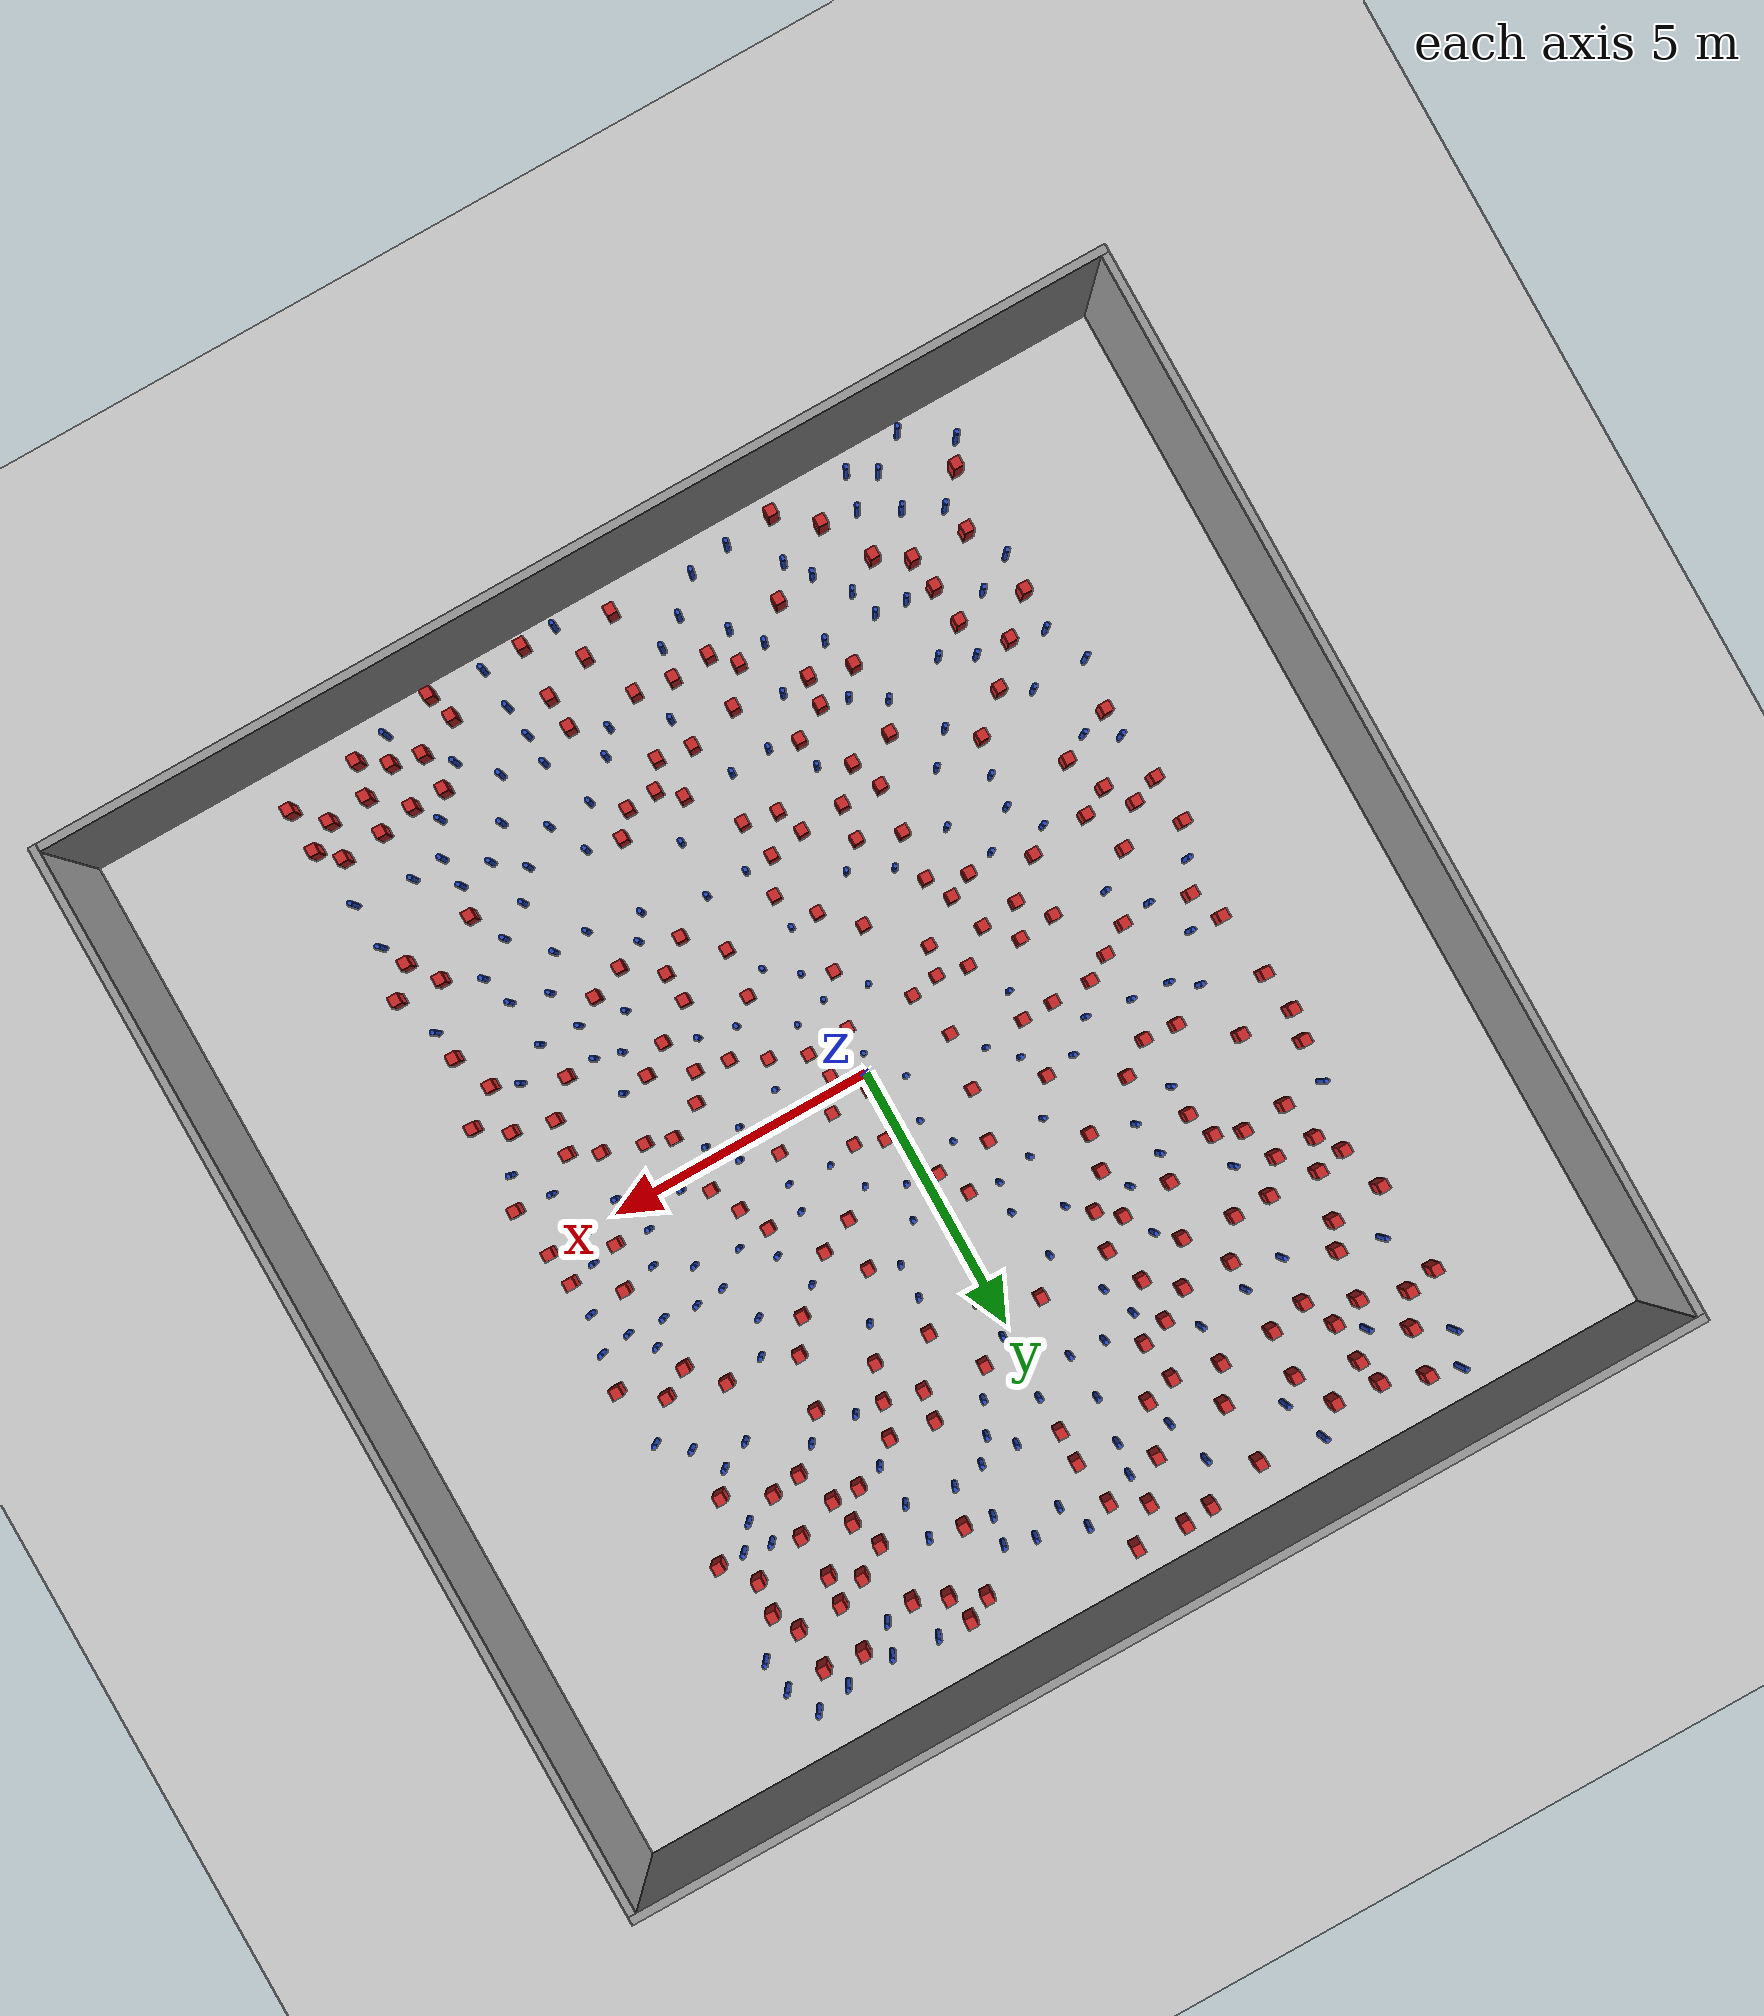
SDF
<sdf version="1.6">
 <world name="default">
  <light name="sun" type="directional">
   <pose>0 0 1000 0 -0 0</pose>
   <diffuse>0.8 0.8 0.8 1</diffuse>
   <specular>0.1 0.1 0.1 1</specular>
   <attenuation>
    <range>1000</range>
    <constant>0.9</constant>
    <linear>0.01</linear>
    <quadratic>0.001</quadratic>
   </attenuation>
   <direction>-0.5 0.5 -1</direction>
  </light>
  <model name="ground_plane">
   <static>1</static>
   <link name="link">
    <collision name="collision">
     <geometry><plane><normal>0 0 1</normal><size>100 100</size></plane></geometry>
     <surface><friction><ode><mu>100</mu><mu2>50</mu2></ode></friction></surface>
    </collision>
    <visual name="visual">
     <cast_shadows>0</cast_shadows>
     <geometry><plane><normal>0 0 1</normal><size>100 100</size></plane></geometry>
     <material>
      <ambient>1.0 1.0 1.0 1.0</ambient>
      <diffuse>0.8 0.8 0.8 1.0</diffuse>
      <specular>0.01 0.01 0.01 1.000000</specular>
     </material>
    </visual>
   </link>
  </model>
  <gravity>0 0 -9.8</gravity>
  <magnetic_field>6e-06 2.3e-05 -4.2e-05</magnetic_field>
  <atmosphere type="adiabatic"/>
  <physics name="default_physics" default="0" type="ode">
   <max_step_size>0.001</max_step_size>
   <real_time_factor>1</real_time_factor>
   <real_time_update_rate>1000</real_time_update_rate>
  </physics>
  <scene><ambient>0.4 0.4 0.4 1</ambient><background>0.7 0.7 0.7 1</background><shadows>1</shadows></scene>
  <spherical_coordinates>
   <surface_model>EARTH_WGS84</surface_model>
   <latitude_deg>0</latitude_deg>
   <longitude_deg>0</longitude_deg>
   <elevation>0</elevation>
   <heading_deg>0</heading_deg>
  </spherical_coordinates>
  <plugin name="gazebo_occupancy_map" filename="libgazebo_2Dmap_plugin.so">
   <map_resolution>0.05</map_resolution>
   <map_topic>generated_map</map_topic>
   <map_height>0.01</map_height>
   <map_size_x>50</map_size_x>
   <map_size_y>50</map_size_y>
  </plugin>
  <model name="NamedLocations">
   <static>true</static>
   <link name="DefaultStart"><pose>8.5 0 0 0 0 3.14</pose></link>
  </model>
  <model name="20x20_walls">
   <pose>0.044518 0.176112 0 0 -0 0</pose>
   <link name="Wall_1">
    <collision name="Wall_1_Collision">
     <geometry><box><size>20 0.15 2.5</size></box></geometry>
     <pose>0 0 1.25 0 -0 0</pose>
    </collision>
    <visual name="Wall_1_Visual">
     <pose>0 0 1.25 0 -0 0</pose>
     <geometry><box><size>20 0.15 2.5</size></box></geometry>
     <material>
      <script><uri>file://media/materials/scripts/gazebo.material</uri><name>Gazebo/Grey</name></script>
      <ambient>0.976471 0.992157 1 1</ambient>
     </material>
     <meta><layer>0</layer></meta>
    </visual>
    <pose>0 9.925 0 0 -0 0</pose>
   </link>
   <link name="Wall_3">
    <collision name="Wall_3_Collision">
     <geometry><box><size>20 0.15 2.5</size></box></geometry>
     <pose>0 0 1.25 0 -0 0</pose>
    </collision>
    <visual name="Wall_3_Visual">
     <pose>0 0 1.25 0 -0 0</pose>
     <geometry><box><size>20 0.15 2.5</size></box></geometry>
     <material>
      <script><uri>file://media/materials/scripts/gazebo.material</uri><name>Gazebo/Grey</name></script>
      <ambient>0.976471 0.992157 1 1</ambient>
     </material>
     <meta><layer>0</layer></meta>
    </visual>
    <pose>9.925 0 0 0 0 -1.5708</pose>
   </link>
   <link name="Wall_4">
    <collision name="Wall_4_Collision">
     <geometry><box><size>20 0.15 2.5</size></box></geometry>
     <pose>0 0 1.25 0 -0 0</pose>
    </collision>
    <visual name="Wall_4_Visual">
     <pose>0 0 1.25 0 -0 0</pose>
     <geometry><box><size>20 0.15 2.5</size></box></geometry>
     <material>
      <script><uri>file://media/materials/scripts/gazebo.material</uri><name>Gazebo/Grey</name></script>
      <ambient>0.976471 0.992157 1 1</ambient>
     </material>
     <meta><layer>0</layer></meta>
    </visual>
    <pose>0 -9.925 0 0 -0 3.14159</pose>
   </link>
   <link name="Wall_5">
    <collision name="Wall_5_Collision">
     <geometry><box><size>20 0.15 2.5</size></box></geometry>
     <pose>0 0 1.25 0 -0 0</pose>
    </collision>
    <visual name="Wall_5_Visual">
     <pose>0 0 1.25 0 -0 0</pose>
     <geometry><box><size>20 0.15 2.5</size></box></geometry>
     <material>
      <script><uri>file://media/materials/scripts/gazebo.material</uri><name>Gazebo/Grey</name></script>
      <ambient>0.976471 0.992157 1 1</ambient>
     </material>
     <meta><layer>0</layer></meta>
    </visual>
    <pose>-9.925 0 0 0 -0 1.5708</pose>
   </link>
   <static>1</static>
  </model>
  <model name="pole_obstacle0">
   <static>true</static>
   <pose>0.880135995998 -4.03369669981 2.88873142074e-08 -9.90536689879e-09 4.60219948988e-07 -1.20965994961e-07</pose>
   <link name="link">
    <pose>0 0 0.3 0 -0 0</pose>
    <inertial>
     <mass>1</mass>
     <inertia><ixx>0.145833</ixx><ixy>0</ixy><ixz>0</ixz><iyy>0.145833</iyy><iyz>0</iyz><izz>0.125</izz></inertia>
    </inertial>
    <collision name="collision">
     <geometry><cylinder><radius>0.05</radius><length>.6</length></cylinder></geometry>
    </collision>
    <visual name="visual">
     <geometry><cylinder><radius>0.05</radius><length>.6</length></cylinder></geometry>
     <material>
      <script><name>Gazebo/Blue</name><uri>file://media/materials/scripts/gazebo.material</uri></script>
     </material>
    </visual>
   </link>
  </model>
  <model name="pole_obstacle1">
   <static>true</static>
   <pose>3.65739315824 -4.48320199937 2.88873142074e-08 -9.90536689859e-09 4.60219948989e-07 -1.20965994961e-07</pose>
   <link name="link">
    <pose>0 0 0.3 0 -0 0</pose>
    <inertial>
     <mass>1</mass>
     <inertia><ixx>0.145833</ixx><ixy>0</ixy><ixz>0</ixz><iyy>0.145833</iyy><iyz>0</iyz><izz>0.125</izz></inertia>
    </inertial>
    <collision name="collision">
     <geometry><cylinder><radius>0.05</radius><length>.6</length></cylinder></geometry>
    </collision>
    <visual name="visual">
     <geometry><cylinder><radius>0.05</radius><length>.6</length></cylinder></geometry>
     <material>
      <script><name>Gazebo/Blue</name><uri>file://media/materials/scripts/gazebo.material</uri></script>
     </material>
    </visual>
   </link>
  </model>
  <model name="square_post_obstacle0">
   <static>true</static>
   <pose>3.04580464808 0.973924702898 8.22691968438e-08 7.2212513382e-06 -7.54495500217e-07 2.29674213826e-05</pose>
   <link name="link">
    <pose>0 0 0.25 0 -0 0</pose>
    <inertial>
     <mass>100</mass>
     <inertia>
      <ixx>0.166667</ixx>
      <ixy>0</ixy>
      <ixz>0</ixz>
      <iyy>0.166667</iyy>
      <iyz>0</iyz>
      <izz>0.166667</izz>
     </inertia>
    </inertial>
    <collision name="collision"><geometry><box><size>.2 .2 .5</size></box></geometry></collision>
    <visual name="visual">
     <geometry><box><size>.2 .2 .5</size></box></geometry>
     <material>
      <script><name>Gazebo/Red</name><uri>file://media/materials/scripts/gazebo.material</uri></script>
     </material>
    </visual>
   </link>
  </model>
  <model name="square_post_obstacle1">
   <static>true</static>
   <pose>-0.560841671599 2.65041663907 8.22691968438e-08 7.2212513382e-06 -7.54495500217e-07 2.29674213826e-05</pose>
   <link name="link">
    <pose>0 0 0.25 0 -0 0</pose>
    <inertial>
     <mass>100</mass>
     <inertia>
      <ixx>0.166667</ixx>
      <ixy>0</ixy>
      <ixz>0</ixz>
      <iyy>0.166667</iyy>
      <iyz>0</iyz>
      <izz>0.166667</izz>
     </inertia>
    </inertial>
    <collision name="collision"><geometry><box><size>.2 .2 .5</size></box></geometry></collision>
    <visual name="visual">
     <geometry><box><size>.2 .2 .5</size></box></geometry>
     <material>
      <script><name>Gazebo/Red</name><uri>file://media/materials/scripts/gazebo.material</uri></script>
     </material>
    </visual>
   </link>
  </model>
  <model name="pole_obstacle2">
   <static>true</static>
   <pose>5.45777131035 2.34422630777 2.88873142074e-08 -9.90536690245e-09 4.6021994898e-07 -1.20965994966e-07</pose>
   <link name="link">
    <pose>0 0 0.3 0 -0 0</pose>
    <inertial>
     <mass>1</mass>
     <inertia><ixx>0.145833</ixx><ixy>0</ixy><ixz>0</ixz><iyy>0.145833</iyy><iyz>0</iyz><izz>0.125</izz></inertia>
    </inertial>
    <collision name="collision">
     <geometry><cylinder><radius>0.05</radius><length>.6</length></cylinder></geometry>
    </collision>
    <visual name="visual">
     <geometry><cylinder><radius>0.05</radius><length>.6</length></cylinder></geometry>
     <material>
      <script><name>Gazebo/Blue</name><uri>file://media/materials/scripts/gazebo.material</uri></script>
     </material>
    </visual>
   </link>
  </model>
  <model name="pole_obstacle3">
   <static>true</static>
   <pose>3.03864295202 6.81444231652 2.88873142074e-08 -9.90536689859e-09 4.60219948989e-07 -1.20965994961e-07</pose>
   <link name="link">
    <pose>0 0 0.3 0 -0 0</pose>
    <inertial>
     <mass>1</mass>
     <inertia><ixx>0.145833</ixx><ixy>0</ixy><ixz>0</ixz><iyy>0.145833</iyy><iyz>0</iyz><izz>0.125</izz></inertia>
    </inertial>
    <collision name="collision">
     <geometry><cylinder><radius>0.05</radius><length>.6</length></cylinder></geometry>
    </collision>
    <visual name="visual">
     <geometry><cylinder><radius>0.05</radius><length>.6</length></cylinder></geometry>
     <material>
      <script><name>Gazebo/Blue</name><uri>file://media/materials/scripts/gazebo.material</uri></script>
     </material>
    </visual>
   </link>
  </model>
  <model name="pole_obstacle4">
   <static>true</static>
   <pose>-4.39595485227 -2.83956614343 2.88873142074e-08 -9.90536690245e-09 4.6021994898e-07 -1.20965994966e-07</pose>
   <link name="link">
    <pose>0 0 0.3 0 -0 0</pose>
    <inertial>
     <mass>1</mass>
     <inertia><ixx>0.145833</ixx><ixy>0</ixy><ixz>0</ixz><iyy>0.145833</iyy><iyz>0</iyz><izz>0.125</izz></inertia>
    </inertial>
    <collision name="collision">
     <geometry><cylinder><radius>0.05</radius><length>.6</length></cylinder></geometry>
    </collision>
    <visual name="visual">
     <geometry><cylinder><radius>0.05</radius><length>.6</length></cylinder></geometry>
     <material>
      <script><name>Gazebo/Blue</name><uri>file://media/materials/scripts/gazebo.material</uri></script>
     </material>
    </visual>
   </link>
  </model>
  <model name="pole_obstacle5">
   <static>true</static>
   <pose>3.96144716904 -2.53710015509 2.88873142074e-08 -9.90536690919e-09 4.60219948964e-07 -1.20965994979e-07</pose>
   <link name="link">
    <pose>0 0 0.3 0 -0 0</pose>
    <inertial>
     <mass>1</mass>
     <inertia><ixx>0.145833</ixx><ixy>0</ixy><ixz>0</ixz><iyy>0.145833</iyy><iyz>0</iyz><izz>0.125</izz></inertia>
    </inertial>
    <collision name="collision">
     <geometry><cylinder><radius>0.05</radius><length>.6</length></cylinder></geometry>
    </collision>
    <visual name="visual">
     <geometry><cylinder><radius>0.05</radius><length>.6</length></cylinder></geometry>
     <material>
      <script><name>Gazebo/Blue</name><uri>file://media/materials/scripts/gazebo.material</uri></script>
     </material>
    </visual>
   </link>
  </model>
  <model name="pole_obstacle6">
   <static>true</static>
   <pose>2.04491357636 3.79223943982 2.88873142074e-08 -9.9053669043e-09 4.60219948975e-07 -1.2096599497e-07</pose>
   <link name="link">
    <pose>0 0 0.3 0 -0 0</pose>
    <inertial>
     <mass>1</mass>
     <inertia><ixx>0.145833</ixx><ixy>0</ixy><ixz>0</ixz><iyy>0.145833</iyy><iyz>0</iyz><izz>0.125</izz></inertia>
    </inertial>
    <collision name="collision">
     <geometry><cylinder><radius>0.05</radius><length>.6</length></cylinder></geometry>
    </collision>
    <visual name="visual">
     <geometry><cylinder><radius>0.05</radius><length>.6</length></cylinder></geometry>
     <material>
      <script><name>Gazebo/Blue</name><uri>file://media/materials/scripts/gazebo.material</uri></script>
     </material>
    </visual>
   </link>
  </model>
  <model name="square_post_obstacle2">
   <static>true</static>
   <pose>-6.1309527959 -7.35485237627 8.22691968438e-08 7.22125133819e-06 -7.54495500217e-07 2.29674213826e-05</pose>
   <link name="link">
    <pose>0 0 0.25 0 -0 0</pose>
    <inertial>
     <mass>100</mass>
     <inertia>
      <ixx>0.166667</ixx>
      <ixy>0</ixy>
      <ixz>0</ixz>
      <iyy>0.166667</iyy>
      <iyz>0</iyz>
      <izz>0.166667</izz>
     </inertia>
    </inertial>
    <collision name="collision"><geometry><box><size>.2 .2 .5</size></box></geometry></collision>
    <visual name="visual">
     <geometry><box><size>.2 .2 .5</size></box></geometry>
     <material>
      <script><name>Gazebo/Red</name><uri>file://media/materials/scripts/gazebo.material</uri></script>
     </material>
    </visual>
   </link>
  </model>
  <model name="square_post_obstacle3">
   <static>true</static>
   <pose>-2.6174061966 8.0196257443 8.22691968438e-08 7.22125133819e-06 -7.54495500217e-07 2.29674213826e-05</pose>
   <link name="link">
    <pose>0 0 0.25 0 -0 0</pose>
    <inertial>
     <mass>100</mass>
     <inertia>
      <ixx>0.166667</ixx>
      <ixy>0</ixy>
      <ixz>0</ixz>
      <iyy>0.166667</iyy>
      <iyz>0</iyz>
      <izz>0.166667</izz>
     </inertia>
    </inertial>
    <collision name="collision"><geometry><box><size>.2 .2 .5</size></box></geometry></collision>
    <visual name="visual">
     <geometry><box><size>.2 .2 .5</size></box></geometry>
     <material>
      <script><name>Gazebo/Red</name><uri>file://media/materials/scripts/gazebo.material</uri></script>
     </material>
    </visual>
   </link>
  </model>
  <model name="square_post_obstacle4">
   <static>true</static>
   <pose>5.06880561041 -1.93774286061 8.22691968438e-08 7.2212513382e-06 -7.54495500217e-07 2.29674213826e-05</pose>
   <link name="link">
    <pose>0 0 0.25 0 -0 0</pose>
    <inertial>
     <mass>100</mass>
     <inertia>
      <ixx>0.166667</ixx>
      <ixy>0</ixy>
      <ixz>0</ixz>
      <iyy>0.166667</iyy>
      <iyz>0</iyz>
      <izz>0.166667</izz>
     </inertia>
    </inertial>
    <collision name="collision"><geometry><box><size>.2 .2 .5</size></box></geometry></collision>
    <visual name="visual">
     <geometry><box><size>.2 .2 .5</size></box></geometry>
     <material>
      <script><name>Gazebo/Red</name><uri>file://media/materials/scripts/gazebo.material</uri></script>
     </material>
    </visual>
   </link>
  </model>
  <model name="pole_obstacle7">
   <static>true</static>
   <pose>1.22205446212 -6.99600765452 2.88873142074e-08 -9.90536689852e-09 4.60219948989e-07 -1.2096599496e-07</pose>
   <link name="link">
    <pose>0 0 0.3 0 -0 0</pose>
    <inertial>
     <mass>1</mass>
     <inertia><ixx>0.145833</ixx><ixy>0</ixy><ixz>0</ixz><iyy>0.145833</iyy><iyz>0</iyz><izz>0.125</izz></inertia>
    </inertial>
    <collision name="collision">
     <geometry><cylinder><radius>0.05</radius><length>.6</length></cylinder></geometry>
    </collision>
    <visual name="visual">
     <geometry><cylinder><radius>0.05</radius><length>.6</length></cylinder></geometry>
     <material>
      <script><name>Gazebo/Blue</name><uri>file://media/materials/scripts/gazebo.material</uri></script>
     </material>
    </visual>
   </link>
  </model>
  <model name="pole_obstacle8">
   <static>true</static>
   <pose>-2.48331928345 1.05033465094 2.88873142074e-08 -9.90536689395e-09 4.60219949e-07 -1.20965994953e-07</pose>
   <link name="link">
    <pose>0 0 0.3 0 -0 0</pose>
    <inertial>
     <mass>1</mass>
     <inertia><ixx>0.145833</ixx><ixy>0</ixy><ixz>0</ixz><iyy>0.145833</iyy><iyz>0</iyz><izz>0.125</izz></inertia>
    </inertial>
    <collision name="collision">
     <geometry><cylinder><radius>0.05</radius><length>.6</length></cylinder></geometry>
    </collision>
    <visual name="visual">
     <geometry><cylinder><radius>0.05</radius><length>.6</length></cylinder></geometry>
     <material>
      <script><name>Gazebo/Blue</name><uri>file://media/materials/scripts/gazebo.material</uri></script>
     </material>
    </visual>
   </link>
  </model>
  <model name="square_post_obstacle5">
   <static>true</static>
   <pose>-0.645134835433 8.885105888 8.22691968438e-08 7.22125133819e-06 -7.54495500217e-07 2.29674213826e-05</pose>
   <link name="link">
    <pose>0 0 0.25 0 -0 0</pose>
    <inertial>
     <mass>100</mass>
     <inertia>
      <ixx>0.166667</ixx>
      <ixy>0</ixy>
      <ixz>0</ixz>
      <iyy>0.166667</iyy>
      <iyz>0</iyz>
      <izz>0.166667</izz>
     </inertia>
    </inertial>
    <collision name="collision"><geometry><box><size>.2 .2 .5</size></box></geometry></collision>
    <visual name="visual">
     <geometry><box><size>.2 .2 .5</size></box></geometry>
     <material>
      <script><name>Gazebo/Red</name><uri>file://media/materials/scripts/gazebo.material</uri></script>
     </material>
    </visual>
   </link>
  </model>
  <model name="square_post_obstacle6">
   <static>true</static>
   <pose>-3.73251036276 -1.32779266943 8.22691968438e-08 7.2212513382e-06 -7.54495500217e-07 2.29674213826e-05</pose>
   <link name="link">
    <pose>0 0 0.25 0 -0 0</pose>
    <inertial>
     <mass>100</mass>
     <inertia>
      <ixx>0.166667</ixx>
      <ixy>0</ixy>
      <ixz>0</ixz>
      <iyy>0.166667</iyy>
      <iyz>0</iyz>
      <izz>0.166667</izz>
     </inertia>
    </inertial>
    <collision name="collision"><geometry><box><size>.2 .2 .5</size></box></geometry></collision>
    <visual name="visual">
     <geometry><box><size>.2 .2 .5</size></box></geometry>
     <material>
      <script><name>Gazebo/Red</name><uri>file://media/materials/scripts/gazebo.material</uri></script>
     </material>
    </visual>
   </link>
  </model>
  <model name="square_post_obstacle7">
   <static>true</static>
   <pose>-2.04888916923 7.17420283449 8.22691968438e-08 7.22125133819e-06 -7.54495500217e-07 2.29674213826e-05</pose>
   <link name="link">
    <pose>0 0 0.25 0 -0 0</pose>
    <inertial>
     <mass>100</mass>
     <inertia>
      <ixx>0.166667</ixx>
      <ixy>0</ixy>
      <ixz>0</ixz>
      <iyy>0.166667</iyy>
      <iyz>0</iyz>
      <izz>0.166667</izz>
     </inertia>
    </inertial>
    <collision name="collision"><geometry><box><size>.2 .2 .5</size></box></geometry></collision>
    <visual name="visual">
     <geometry><box><size>.2 .2 .5</size></box></geometry>
     <material>
      <script><name>Gazebo/Red</name><uri>file://media/materials/scripts/gazebo.material</uri></script>
     </material>
    </visual>
   </link>
  </model>
  <model name="pole_obstacle9">
   <static>true</static>
   <pose>-3.30076019264 1.46445562812 2.88873142074e-08 -9.90536689395e-09 4.60219949e-07 -1.20965994953e-07</pose>
   <link name="link">
    <pose>0 0 0.3 0 -0 0</pose>
    <inertial>
     <mass>1</mass>
     <inertia><ixx>0.145833</ixx><ixy>0</ixy><ixz>0</ixz><iyy>0.145833</iyy><iyz>0</iyz><izz>0.125</izz></inertia>
    </inertial>
    <collision name="collision">
     <geometry><cylinder><radius>0.05</radius><length>.6</length></cylinder></geometry>
    </collision>
    <visual name="visual">
     <geometry><cylinder><radius>0.05</radius><length>.6</length></cylinder></geometry>
     <material>
      <script><name>Gazebo/Blue</name><uri>file://media/materials/scripts/gazebo.material</uri></script>
     </material>
    </visual>
   </link>
  </model>
  <model name="pole_obstacle10">
   <static>true</static>
   <pose>3.81010568712 -1.76509671194 2.88873142074e-08 -9.90536689395e-09 4.60219949e-07 -1.20965994953e-07</pose>
   <link name="link">
    <pose>0 0 0.3 0 -0 0</pose>
    <inertial>
     <mass>1</mass>
     <inertia><ixx>0.145833</ixx><ixy>0</ixy><ixz>0</ixz><iyy>0.145833</iyy><iyz>0</iyz><izz>0.125</izz></inertia>
    </inertial>
    <collision name="collision">
     <geometry><cylinder><radius>0.05</radius><length>.6</length></cylinder></geometry>
    </collision>
    <visual name="visual">
     <geometry><cylinder><radius>0.05</radius><length>.6</length></cylinder></geometry>
     <material>
      <script><name>Gazebo/Blue</name><uri>file://media/materials/scripts/gazebo.material</uri></script>
     </material>
    </visual>
   </link>
  </model>
  <model name="pole_obstacle11">
   <static>true</static>
   <pose>-3.9105672306 6.45645708071 2.88873142074e-08 -9.90536692062e-09 4.60219948937e-07 -1.20965994985e-07</pose>
   <link name="link">
    <pose>0 0 0.3 0 -0 0</pose>
    <inertial>
     <mass>1</mass>
     <inertia><ixx>0.145833</ixx><ixy>0</ixy><ixz>0</ixz><iyy>0.145833</iyy><iyz>0</iyz><izz>0.125</izz></inertia>
    </inertial>
    <collision name="collision">
     <geometry><cylinder><radius>0.05</radius><length>.6</length></cylinder></geometry>
    </collision>
    <visual name="visual">
     <geometry><cylinder><radius>0.05</radius><length>.6</length></cylinder></geometry>
     <material>
      <script><name>Gazebo/Blue</name><uri>file://media/materials/scripts/gazebo.material</uri></script>
     </material>
    </visual>
   </link>
  </model>
  <model name="pole_obstacle12">
   <static>true</static>
   <pose>2.34664239557 -0.272803003717 2.88873142074e-08 -9.90536692022e-09 4.60219948938e-07 -1.20965994984e-07</pose>
   <link name="link">
    <pose>0 0 0.3 0 -0 0</pose>
    <inertial>
     <mass>1</mass>
     <inertia><ixx>0.145833</ixx><ixy>0</ixy><ixz>0</ixz><iyy>0.145833</iyy><iyz>0</iyz><izz>0.125</izz></inertia>
    </inertial>
    <collision name="collision">
     <geometry><cylinder><radius>0.05</radius><length>.6</length></cylinder></geometry>
    </collision>
    <visual name="visual">
     <geometry><cylinder><radius>0.05</radius><length>.6</length></cylinder></geometry>
     <material>
      <script><name>Gazebo/Blue</name><uri>file://media/materials/scripts/gazebo.material</uri></script>
     </material>
    </visual>
   </link>
  </model>
  <model name="square_post_obstacle8">
   <static>true</static>
   <pose>-6.82306011882 6.04115686973 8.22691968438e-08 7.2212513382e-06 -7.54495500217e-07 2.29674213826e-05</pose>
   <link name="link">
    <pose>0 0 0.25 0 -0 0</pose>
    <inertial>
     <mass>100</mass>
     <inertia>
      <ixx>0.166667</ixx>
      <ixy>0</ixy>
      <ixz>0</ixz>
      <iyy>0.166667</iyy>
      <iyz>0</iyz>
      <izz>0.166667</izz>
     </inertia>
    </inertial>
    <collision name="collision"><geometry><box><size>.2 .2 .5</size></box></geometry></collision>
    <visual name="visual">
     <geometry><box><size>.2 .2 .5</size></box></geometry>
     <material>
      <script><name>Gazebo/Red</name><uri>file://media/materials/scripts/gazebo.material</uri></script>
     </material>
    </visual>
   </link>
  </model>
  <model name="square_post_obstacle9">
   <static>true</static>
   <pose>-3.92443147104 5.92480272412 8.22691968438e-08 7.22125133819e-06 -7.54495500217e-07 2.29674213826e-05</pose>
   <link name="link">
    <pose>0 0 0.25 0 -0 0</pose>
    <inertial>
     <mass>100</mass>
     <inertia>
      <ixx>0.166667</ixx>
      <ixy>0</ixy>
      <ixz>0</ixz>
      <iyy>0.166667</iyy>
      <iyz>0</iyz>
      <izz>0.166667</izz>
     </inertia>
    </inertial>
    <collision name="collision"><geometry><box><size>.2 .2 .5</size></box></geometry></collision>
    <visual name="visual">
     <geometry><box><size>.2 .2 .5</size></box></geometry>
     <material>
      <script><name>Gazebo/Red</name><uri>file://media/materials/scripts/gazebo.material</uri></script>
     </material>
    </visual>
   </link>
  </model>
  <model name="pole_obstacle13">
   <static>true</static>
   <pose>-1.42932631599 -3.22152350444 2.88873142074e-08 -9.90536689791e-09 4.6021994899e-07 -1.20965994959e-07</pose>
   <link name="link">
    <pose>0 0 0.3 0 -0 0</pose>
    <inertial>
     <mass>1</mass>
     <inertia><ixx>0.145833</ixx><ixy>0</ixy><ixz>0</ixz><iyy>0.145833</iyy><iyz>0</iyz><izz>0.125</izz></inertia>
    </inertial>
    <collision name="collision">
     <geometry><cylinder><radius>0.05</radius><length>.6</length></cylinder></geometry>
    </collision>
    <visual name="visual">
     <geometry><cylinder><radius>0.05</radius><length>.6</length></cylinder></geometry>
     <material>
      <script><name>Gazebo/Blue</name><uri>file://media/materials/scripts/gazebo.material</uri></script>
     </material>
    </visual>
   </link>
  </model>
  <model name="square_post_obstacle10">
   <static>true</static>
   <pose>6.43679771532 2.68238782263 8.22691968438e-08 7.2212513382e-06 -7.54495500217e-07 2.29674213826e-05</pose>
   <link name="link">
    <pose>0 0 0.25 0 -0 0</pose>
    <inertial>
     <mass>100</mass>
     <inertia>
      <ixx>0.166667</ixx>
      <ixy>0</ixy>
      <ixz>0</ixz>
      <iyy>0.166667</iyy>
      <iyz>0</iyz>
      <izz>0.166667</izz>
     </inertia>
    </inertial>
    <collision name="collision"><geometry><box><size>.2 .2 .5</size></box></geometry></collision>
    <visual name="visual">
     <geometry><box><size>.2 .2 .5</size></box></geometry>
     <material>
      <script><name>Gazebo/Red</name><uri>file://media/materials/scripts/gazebo.material</uri></script>
     </material>
    </visual>
   </link>
  </model>
  <model name="square_post_obstacle11">
   <static>true</static>
   <pose>-6.88948237772 3.19168750568 8.22691968438e-08 7.2212513382e-06 -7.54495500217e-07 2.29674213826e-05</pose>
   <link name="link">
    <pose>0 0 0.25 0 -0 0</pose>
    <inertial>
     <mass>100</mass>
     <inertia>
      <ixx>0.166667</ixx>
      <ixy>0</ixy>
      <ixz>0</ixz>
      <iyy>0.166667</iyy>
      <iyz>0</iyz>
      <izz>0.166667</izz>
     </inertia>
    </inertial>
    <collision name="collision"><geometry><box><size>.2 .2 .5</size></box></geometry></collision>
    <visual name="visual">
     <geometry><box><size>.2 .2 .5</size></box></geometry>
     <material>
      <script><name>Gazebo/Red</name><uri>file://media/materials/scripts/gazebo.material</uri></script>
     </material>
    </visual>
   </link>
  </model>
  <model name="pole_obstacle14">
   <static>true</static>
   <pose>2.58773399289 2.71610376358 2.88873142074e-08 -9.90536690232e-09 4.6021994898e-07 -1.20965994968e-07</pose>
   <link name="link">
    <pose>0 0 0.3 0 -0 0</pose>
    <inertial>
     <mass>1</mass>
     <inertia><ixx>0.145833</ixx><ixy>0</ixy><ixz>0</ixz><iyy>0.145833</iyy><iyz>0</iyz><izz>0.125</izz></inertia>
    </inertial>
    <collision name="collision">
     <geometry><cylinder><radius>0.05</radius><length>.6</length></cylinder></geometry>
    </collision>
    <visual name="visual">
     <geometry><cylinder><radius>0.05</radius><length>.6</length></cylinder></geometry>
     <material>
      <script><name>Gazebo/Blue</name><uri>file://media/materials/scripts/gazebo.material</uri></script>
     </material>
    </visual>
   </link>
  </model>
  <model name="pole_obstacle15">
   <static>true</static>
   <pose>4.30699988644 8.43849665752 2.88873142074e-08 -9.9053668967e-09 4.60219948993e-07 -1.20965994957e-07</pose>
   <link name="link">
    <pose>0 0 0.3 0 -0 0</pose>
    <inertial>
     <mass>1</mass>
     <inertia><ixx>0.145833</ixx><ixy>0</ixy><ixz>0</ixz><iyy>0.145833</iyy><iyz>0</iyz><izz>0.125</izz></inertia>
    </inertial>
    <collision name="collision">
     <geometry><cylinder><radius>0.05</radius><length>.6</length></cylinder></geometry>
    </collision>
    <visual name="visual">
     <geometry><cylinder><radius>0.05</radius><length>.6</length></cylinder></geometry>
     <material>
      <script><name>Gazebo/Blue</name><uri>file://media/materials/scripts/gazebo.material</uri></script>
     </material>
    </visual>
   </link>
  </model>
  <model name="square_post_obstacle12">
   <static>true</static>
   <pose>-1.90750702567 -0.886768801386 8.22691968438e-08 7.2212513382e-06 -7.54495500217e-07 2.29674213826e-05</pose>
   <link name="link">
    <pose>0 0 0.25 0 -0 0</pose>
    <inertial>
     <mass>100</mass>
     <inertia>
      <ixx>0.166667</ixx>
      <ixy>0</ixy>
      <ixz>0</ixz>
      <iyy>0.166667</iyy>
      <iyz>0</iyz>
      <izz>0.166667</izz>
     </inertia>
    </inertial>
    <collision name="collision"><geometry><box><size>.2 .2 .5</size></box></geometry></collision>
    <visual name="visual">
     <geometry><box><size>.2 .2 .5</size></box></geometry>
     <material>
      <script><name>Gazebo/Red</name><uri>file://media/materials/scripts/gazebo.material</uri></script>
     </material>
    </visual>
   </link>
  </model>
  <model name="pole_obstacle16">
   <static>true</static>
   <pose>3.65973734561 9.09488109856 2.88873142074e-08 -9.90536692318e-09 4.6021994893e-07 -1.20965994988e-07</pose>
   <link name="link">
    <pose>0 0 0.3 0 -0 0</pose>
    <inertial>
     <mass>1</mass>
     <inertia><ixx>0.145833</ixx><ixy>0</ixy><ixz>0</ixz><iyy>0.145833</iyy><iyz>0</iyz><izz>0.125</izz></inertia>
    </inertial>
    <collision name="collision">
     <geometry><cylinder><radius>0.05</radius><length>.6</length></cylinder></geometry>
    </collision>
    <visual name="visual">
     <geometry><cylinder><radius>0.05</radius><length>.6</length></cylinder></geometry>
     <material>
      <script><name>Gazebo/Blue</name><uri>file://media/materials/scripts/gazebo.material</uri></script>
     </material>
    </visual>
   </link>
  </model>
  <model name="pole_obstacle17">
   <static>true</static>
   <pose>-4.05257553489 -6.87511140498 2.88873142074e-08 -9.90536690842e-09 4.60219948965e-07 -1.20965994976e-07</pose>
   <link name="link">
    <pose>0 0 0.3 0 -0 0</pose>
    <inertial>
     <mass>1</mass>
     <inertia><ixx>0.145833</ixx><ixy>0</ixy><ixz>0</ixz><iyy>0.145833</iyy><iyz>0</iyz><izz>0.125</izz></inertia>
    </inertial>
    <collision name="collision">
     <geometry><cylinder><radius>0.05</radius><length>.6</length></cylinder></geometry>
    </collision>
    <visual name="visual">
     <geometry><cylinder><radius>0.05</radius><length>.6</length></cylinder></geometry>
     <material>
      <script><name>Gazebo/Blue</name><uri>file://media/materials/scripts/gazebo.material</uri></script>
     </material>
    </visual>
   </link>
  </model>
  <model name="square_post_obstacle13">
   <static>true</static>
   <pose>-4.49310102387 -7.76069410505 8.22691968438e-08 7.2212513382e-06 -7.54495500217e-07 2.29674213826e-05</pose>
   <link name="link">
    <pose>0 0 0.25 0 -0 0</pose>
    <inertial>
     <mass>100</mass>
     <inertia>
      <ixx>0.166667</ixx>
      <ixy>0</ixy>
      <ixz>0</ixz>
      <iyy>0.166667</iyy>
      <iyz>0</iyz>
      <izz>0.166667</izz>
     </inertia>
    </inertial>
    <collision name="collision"><geometry><box><size>.2 .2 .5</size></box></geometry></collision>
    <visual name="visual">
     <geometry><box><size>.2 .2 .5</size></box></geometry>
     <material>
      <script><name>Gazebo/Red</name><uri>file://media/materials/scripts/gazebo.material</uri></script>
     </material>
    </visual>
   </link>
  </model>
  <model name="pole_obstacle18">
   <static>true</static>
   <pose>2.01173463298 -4.35096842097 2.88873142074e-08 -9.90536689932e-09 4.60219948987e-07 -1.20965994962e-07</pose>
   <link name="link">
    <pose>0 0 0.3 0 -0 0</pose>
    <inertial>
     <mass>1</mass>
     <inertia><ixx>0.145833</ixx><ixy>0</ixy><ixz>0</ixz><iyy>0.145833</iyy><iyz>0</iyz><izz>0.125</izz></inertia>
    </inertial>
    <collision name="collision">
     <geometry><cylinder><radius>0.05</radius><length>.6</length></cylinder></geometry>
    </collision>
    <visual name="visual">
     <geometry><cylinder><radius>0.05</radius><length>.6</length></cylinder></geometry>
     <material>
      <script><name>Gazebo/Blue</name><uri>file://media/materials/scripts/gazebo.material</uri></script>
     </material>
    </visual>
   </link>
  </model>
  <model name="square_post_obstacle14">
   <static>true</static>
   <pose>-1.11378315135 -6.66036221192 8.22691968438e-08 7.2212513382e-06 -7.54495500217e-07 2.29674213826e-05</pose>
   <link name="link">
    <pose>0 0 0.25 0 -0 0</pose>
    <inertial>
     <mass>100</mass>
     <inertia>
      <ixx>0.166667</ixx>
      <ixy>0</ixy>
      <ixz>0</ixz>
      <iyy>0.166667</iyy>
      <iyz>0</iyz>
      <izz>0.166667</izz>
     </inertia>
    </inertial>
    <collision name="collision"><geometry><box><size>.2 .2 .5</size></box></geometry></collision>
    <visual name="visual">
     <geometry><box><size>.2 .2 .5</size></box></geometry>
     <material>
      <script><name>Gazebo/Red</name><uri>file://media/materials/scripts/gazebo.material</uri></script>
     </material>
    </visual>
   </link>
  </model>
  <model name="pole_obstacle19">
   <static>true</static>
   <pose>-1.98300112717 -6.44486799128 2.88873142074e-08 -9.90536689721e-09 4.60219948992e-07 -1.20965994958e-07</pose>
   <link name="link">
    <pose>0 0 0.3 0 -0 0</pose>
    <inertial>
     <mass>1</mass>
     <inertia><ixx>0.145833</ixx><ixy>0</ixy><ixz>0</ixz><iyy>0.145833</iyy><iyz>0</iyz><izz>0.125</izz></inertia>
    </inertial>
    <collision name="collision">
     <geometry><cylinder><radius>0.05</radius><length>.6</length></cylinder></geometry>
    </collision>
    <visual name="visual">
     <geometry><cylinder><radius>0.05</radius><length>.6</length></cylinder></geometry>
     <material>
      <script><name>Gazebo/Blue</name><uri>file://media/materials/scripts/gazebo.material</uri></script>
     </material>
    </visual>
   </link>
  </model>
  <model name="square_post_obstacle15">
   <static>true</static>
   <pose>3.21988299101 -8.89908096435 8.22691968438e-08 7.22125133819e-06 -7.54495500217e-07 2.29674213826e-05</pose>
   <link name="link">
    <pose>0 0 0.25 0 -0 0</pose>
    <inertial>
     <mass>100</mass>
     <inertia>
      <ixx>0.166667</ixx>
      <ixy>0</ixy>
      <ixz>0</ixz>
      <iyy>0.166667</iyy>
      <iyz>0</iyz>
      <izz>0.166667</izz>
     </inertia>
    </inertial>
    <collision name="collision"><geometry><box><size>.2 .2 .5</size></box></geometry></collision>
    <visual name="visual">
     <geometry><box><size>.2 .2 .5</size></box></geometry>
     <material>
      <script><name>Gazebo/Red</name><uri>file://media/materials/scripts/gazebo.material</uri></script>
     </material>
    </visual>
   </link>
  </model>
  <model name="square_post_obstacle16">
   <static>true</static>
   <pose>-3.680123788 4.19438872389 8.22691968438e-08 7.2212513382e-06 -7.54495500217e-07 2.29674213826e-05</pose>
   <link name="link">
    <pose>0 0 0.25 0 -0 0</pose>
    <inertial>
     <mass>100</mass>
     <inertia>
      <ixx>0.166667</ixx>
      <ixy>0</ixy>
      <ixz>0</ixz>
      <iyy>0.166667</iyy>
      <iyz>0</iyz>
      <izz>0.166667</izz>
     </inertia>
    </inertial>
    <collision name="collision"><geometry><box><size>.2 .2 .5</size></box></geometry></collision>
    <visual name="visual">
     <geometry><box><size>.2 .2 .5</size></box></geometry>
     <material>
      <script><name>Gazebo/Red</name><uri>file://media/materials/scripts/gazebo.material</uri></script>
     </material>
    </visual>
   </link>
  </model>
  <model name="square_post_obstacle17">
   <static>true</static>
   <pose>5.98129903861 7.36066911239 8.22691968438e-08 7.2212513382e-06 -7.54495500217e-07 2.29674213826e-05</pose>
   <link name="link">
    <pose>0 0 0.25 0 -0 0</pose>
    <inertial>
     <mass>100</mass>
     <inertia>
      <ixx>0.166667</ixx>
      <ixy>0</ixy>
      <ixz>0</ixz>
      <iyy>0.166667</iyy>
      <iyz>0</iyz>
      <izz>0.166667</izz>
     </inertia>
    </inertial>
    <collision name="collision"><geometry><box><size>.2 .2 .5</size></box></geometry></collision>
    <visual name="visual">
     <geometry><box><size>.2 .2 .5</size></box></geometry>
     <material>
      <script><name>Gazebo/Red</name><uri>file://media/materials/scripts/gazebo.material</uri></script>
     </material>
    </visual>
   </link>
  </model>
  <model name="pole_obstacle20">
   <static>true</static>
   <pose>0.95430784977 1.68152880618 2.88873142074e-08 -9.90536690202e-09 4.6021994898e-07 -1.20965994965e-07</pose>
   <link name="link">
    <pose>0 0 0.3 0 -0 0</pose>
    <inertial>
     <mass>1</mass>
     <inertia><ixx>0.145833</ixx><ixy>0</ixy><ixz>0</ixz><iyy>0.145833</iyy><iyz>0</iyz><izz>0.125</izz></inertia>
    </inertial>
    <collision name="collision">
     <geometry><cylinder><radius>0.05</radius><length>.6</length></cylinder></geometry>
    </collision>
    <visual name="visual">
     <geometry><cylinder><radius>0.05</radius><length>.6</length></cylinder></geometry>
     <material>
      <script><name>Gazebo/Blue</name><uri>file://media/materials/scripts/gazebo.material</uri></script>
     </material>
    </visual>
   </link>
  </model>
  <model name="pole_obstacle21">
   <static>true</static>
   <pose>3.47930066305 -2.39734856119 2.88873142074e-08 -9.90536690232e-09 4.6021994898e-07 -1.20965994968e-07</pose>
   <link name="link">
    <pose>0 0 0.3 0 -0 0</pose>
    <inertial>
     <mass>1</mass>
     <inertia><ixx>0.145833</ixx><ixy>0</ixy><ixz>0</ixz><iyy>0.145833</iyy><iyz>0</iyz><izz>0.125</izz></inertia>
    </inertial>
    <collision name="collision">
     <geometry><cylinder><radius>0.05</radius><length>.6</length></cylinder></geometry>
    </collision>
    <visual name="visual">
     <geometry><cylinder><radius>0.05</radius><length>.6</length></cylinder></geometry>
     <material>
      <script><name>Gazebo/Blue</name><uri>file://media/materials/scripts/gazebo.material</uri></script>
     </material>
    </visual>
   </link>
  </model>
  <model name="pole_obstacle22">
   <static>true</static>
   <pose>-3.09804642663 -8.41578343584 2.88873142074e-08 -9.90536692318e-09 4.6021994893e-07 -1.20965994988e-07</pose>
   <link name="link">
    <pose>0 0 0.3 0 -0 0</pose>
    <inertial>
     <mass>1</mass>
     <inertia><ixx>0.145833</ixx><ixy>0</ixy><ixz>0</ixz><iyy>0.145833</iyy><iyz>0</iyz><izz>0.125</izz></inertia>
    </inertial>
    <collision name="collision">
     <geometry><cylinder><radius>0.05</radius><length>.6</length></cylinder></geometry>
    </collision>
    <visual name="visual">
     <geometry><cylinder><radius>0.05</radius><length>.6</length></cylinder></geometry>
     <material>
      <script><name>Gazebo/Blue</name><uri>file://media/materials/scripts/gazebo.material</uri></script>
     </material>
    </visual>
   </link>
  </model>
  <model name="pole_obstacle23">
   <static>true</static>
   <pose>5.45672125437 4.74769062917 2.88873142074e-08 -9.90536690842e-09 4.60219948965e-07 -1.20965994976e-07</pose>
   <link name="link">
    <pose>0 0 0.3 0 -0 0</pose>
    <inertial>
     <mass>1</mass>
     <inertia><ixx>0.145833</ixx><ixy>0</ixy><ixz>0</ixz><iyy>0.145833</iyy><iyz>0</iyz><izz>0.125</izz></inertia>
    </inertial>
    <collision name="collision">
     <geometry><cylinder><radius>0.05</radius><length>.6</length></cylinder></geometry>
    </collision>
    <visual name="visual">
     <geometry><cylinder><radius>0.05</radius><length>.6</length></cylinder></geometry>
     <material>
      <script><name>Gazebo/Blue</name><uri>file://media/materials/scripts/gazebo.material</uri></script>
     </material>
    </visual>
   </link>
  </model>
  <model name="square_post_obstacle18">
   <static>true</static>
   <pose>-2.43390667206 6.24936321946 8.22691968438e-08 7.2212513382e-06 -7.54495500217e-07 2.29674213826e-05</pose>
   <link name="link">
    <pose>0 0 0.25 0 -0 0</pose>
    <inertial>
     <mass>100</mass>
     <inertia>
      <ixx>0.166667</ixx>
      <ixy>0</ixy>
      <ixz>0</ixz>
      <iyy>0.166667</iyy>
      <iyz>0</iyz>
      <izz>0.166667</izz>
     </inertia>
    </inertial>
    <collision name="collision"><geometry><box><size>.2 .2 .5</size></box></geometry></collision>
    <visual name="visual">
     <geometry><box><size>.2 .2 .5</size></box></geometry>
     <material>
      <script><name>Gazebo/Red</name><uri>file://media/materials/scripts/gazebo.material</uri></script>
     </material>
    </visual>
   </link>
  </model>
  <model name="pole_obstacle24">
   <static>true</static>
   <pose>-2.304319869 2.16145580614 2.88873142074e-08 -9.90536690232e-09 4.6021994898e-07 -1.20965994968e-07</pose>
   <link name="link">
    <pose>0 0 0.3 0 -0 0</pose>
    <inertial>
     <mass>1</mass>
     <inertia><ixx>0.145833</ixx><ixy>0</ixy><ixz>0</ixz><iyy>0.145833</iyy><iyz>0</iyz><izz>0.125</izz></inertia>
    </inertial>
    <collision name="collision">
     <geometry><cylinder><radius>0.05</radius><length>.6</length></cylinder></geometry>
    </collision>
    <visual name="visual">
     <geometry><cylinder><radius>0.05</radius><length>.6</length></cylinder></geometry>
     <material>
      <script><name>Gazebo/Blue</name><uri>file://media/materials/scripts/gazebo.material</uri></script>
     </material>
    </visual>
   </link>
  </model>
  <model name="pole_obstacle25">
   <static>true</static>
   <pose>5.43299807183 9.06527341968 2.88873142074e-08 -9.9053668967e-09 4.60219948993e-07 -1.20965994957e-07</pose>
   <link name="link">
    <pose>0 0 0.3 0 -0 0</pose>
    <inertial>
     <mass>1</mass>
     <inertia><ixx>0.145833</ixx><ixy>0</ixy><ixz>0</ixz><iyy>0.145833</iyy><iyz>0</iyz><izz>0.125</izz></inertia>
    </inertial>
    <collision name="collision">
     <geometry><cylinder><radius>0.05</radius><length>.6</length></cylinder></geometry>
    </collision>
    <visual name="visual">
     <geometry><cylinder><radius>0.05</radius><length>.6</length></cylinder></geometry>
     <material>
      <script><name>Gazebo/Blue</name><uri>file://media/materials/scripts/gazebo.material</uri></script>
     </material>
    </visual>
   </link>
  </model>
  <model name="pole_obstacle26">
   <static>true</static>
   <pose>-6.52541339041 -6.65995649793 2.88873142074e-08 -9.90536690842e-09 4.60219948965e-07 -1.20965994976e-07</pose>
   <link name="link">
    <pose>0 0 0.3 0 -0 0</pose>
    <inertial>
     <mass>1</mass>
     <inertia><ixx>0.145833</ixx><ixy>0</ixy><ixz>0</ixz><iyy>0.145833</iyy><iyz>0</iyz><izz>0.125</izz></inertia>
    </inertial>
    <collision name="collision">
     <geometry><cylinder><radius>0.05</radius><length>.6</length></cylinder></geometry>
    </collision>
    <visual name="visual">
     <geometry><cylinder><radius>0.05</radius><length>.6</length></cylinder></geometry>
     <material>
      <script><name>Gazebo/Blue</name><uri>file://media/materials/scripts/gazebo.material</uri></script>
     </material>
    </visual>
   </link>
  </model>
  <model name="pole_obstacle27">
   <static>true</static>
   <pose>0.976012090959 5.89816593282 2.88873142074e-08 -9.90536689421e-09 4.60219948999e-07 -1.20965994953e-07</pose>
   <link name="link">
    <pose>0 0 0.3 0 -0 0</pose>
    <inertial>
     <mass>1</mass>
     <inertia><ixx>0.145833</ixx><ixy>0</ixy><ixz>0</ixz><iyy>0.145833</iyy><iyz>0</iyz><izz>0.125</izz></inertia>
    </inertial>
    <collision name="collision">
     <geometry><cylinder><radius>0.05</radius><length>.6</length></cylinder></geometry>
    </collision>
    <visual name="visual">
     <geometry><cylinder><radius>0.05</radius><length>.6</length></cylinder></geometry>
     <material>
      <script><name>Gazebo/Blue</name><uri>file://media/materials/scripts/gazebo.material</uri></script>
     </material>
    </visual>
   </link>
  </model>
  <model name="pole_obstacle28">
   <static>true</static>
   <pose>4.51472767566 8.98976667733 2.88873142074e-08 -9.9053668967e-09 4.60219948993e-07 -1.20965994957e-07</pose>
   <link name="link">
    <pose>0 0 0.3 0 -0 0</pose>
    <inertial>
     <mass>1</mass>
     <inertia><ixx>0.145833</ixx><ixy>0</ixy><ixz>0</ixz><iyy>0.145833</iyy><iyz>0</iyz><izz>0.125</izz></inertia>
    </inertial>
    <collision name="collision">
     <geometry><cylinder><radius>0.05</radius><length>.6</length></cylinder></geometry>
    </collision>
    <visual name="visual">
     <geometry><cylinder><radius>0.05</radius><length>.6</length></cylinder></geometry>
     <material>
      <script><name>Gazebo/Blue</name><uri>file://media/materials/scripts/gazebo.material</uri></script>
     </material>
    </visual>
   </link>
  </model>
  <model name="square_post_obstacle19">
   <static>true</static>
   <pose>6.29166822977 0.0331094307546 8.22691968438e-08 7.2212513382e-06 -7.54495500217e-07 2.29674213826e-05</pose>
   <link name="link">
    <pose>0 0 0.25 0 -0 0</pose>
    <inertial>
     <mass>100</mass>
     <inertia>
      <ixx>0.166667</ixx>
      <ixy>0</ixy>
      <ixz>0</ixz>
      <iyy>0.166667</iyy>
      <iyz>0</iyz>
      <izz>0.166667</izz>
     </inertia>
    </inertial>
    <collision name="collision"><geometry><box><size>.2 .2 .5</size></box></geometry></collision>
    <visual name="visual">
     <geometry><box><size>.2 .2 .5</size></box></geometry>
     <material>
      <script><name>Gazebo/Red</name><uri>file://media/materials/scripts/gazebo.material</uri></script>
     </material>
    </visual>
   </link>
  </model>
  <model name="square_post_obstacle20">
   <static>true</static>
   <pose>5.46462495724 1.21053023007 8.22691968438e-08 7.2212513382e-06 -7.54495500217e-07 2.29674213826e-05</pose>
   <link name="link">
    <pose>0 0 0.25 0 -0 0</pose>
    <inertial>
     <mass>100</mass>
     <inertia>
      <ixx>0.166667</ixx>
      <ixy>0</ixy>
      <ixz>0</ixz>
      <iyy>0.166667</iyy>
      <iyz>0</iyz>
      <izz>0.166667</izz>
     </inertia>
    </inertial>
    <collision name="collision"><geometry><box><size>.2 .2 .5</size></box></geometry></collision>
    <visual name="visual">
     <geometry><box><size>.2 .2 .5</size></box></geometry>
     <material>
      <script><name>Gazebo/Red</name><uri>file://media/materials/scripts/gazebo.material</uri></script>
     </material>
    </visual>
   </link>
  </model>
  <model name="pole_obstacle29">
   <static>true</static>
   <pose>-4.64463714561 1.11420730306 2.88873142074e-08 -9.90536689445e-09 4.60219948999e-07 -1.20965994956e-07</pose>
   <link name="link">
    <pose>0 0 0.3 0 -0 0</pose>
    <inertial>
     <mass>1</mass>
     <inertia><ixx>0.145833</ixx><ixy>0</ixy><ixz>0</ixz><iyy>0.145833</iyy><iyz>0</iyz><izz>0.125</izz></inertia>
    </inertial>
    <collision name="collision">
     <geometry><cylinder><radius>0.05</radius><length>.6</length></cylinder></geometry>
    </collision>
    <visual name="visual">
     <geometry><cylinder><radius>0.05</radius><length>.6</length></cylinder></geometry>
     <material>
      <script><name>Gazebo/Blue</name><uri>file://media/materials/scripts/gazebo.material</uri></script>
     </material>
    </visual>
   </link>
  </model>
  <model name="square_post_obstacle21">
   <static>true</static>
   <pose>-2.83876542974 0.504566178584 8.22691968438e-08 7.2212513382e-06 -7.54495500217e-07 2.29674213826e-05</pose>
   <link name="link">
    <pose>0 0 0.25 0 -0 0</pose>
    <inertial>
     <mass>100</mass>
     <inertia>
      <ixx>0.166667</ixx>
      <ixy>0</ixy>
      <ixz>0</ixz>
      <iyy>0.166667</iyy>
      <iyz>0</iyz>
      <izz>0.166667</izz>
     </inertia>
    </inertial>
    <collision name="collision"><geometry><box><size>.2 .2 .5</size></box></geometry></collision>
    <visual name="visual">
     <geometry><box><size>.2 .2 .5</size></box></geometry>
     <material>
      <script><name>Gazebo/Red</name><uri>file://media/materials/scripts/gazebo.material</uri></script>
     </material>
    </visual>
   </link>
  </model>
  <model name="pole_obstacle30">
   <static>true</static>
   <pose>1.30149947294 1.07301521637 2.88873142074e-08 -9.90536689672e-09 4.60219948993e-07 -1.20965994959e-07</pose>
   <link name="link">
    <pose>0 0 0.3 0 -0 0</pose>
    <inertial>
     <mass>1</mass>
     <inertia><ixx>0.145833</ixx><ixy>0</ixy><ixz>0</ixz><iyy>0.145833</iyy><iyz>0</iyz><izz>0.125</izz></inertia>
    </inertial>
    <collision name="collision">
     <geometry><cylinder><radius>0.05</radius><length>.6</length></cylinder></geometry>
    </collision>
    <visual name="visual">
     <geometry><cylinder><radius>0.05</radius><length>.6</length></cylinder></geometry>
     <material>
      <script><name>Gazebo/Blue</name><uri>file://media/materials/scripts/gazebo.material</uri></script>
     </material>
    </visual>
   </link>
  </model>
  <model name="square_post_obstacle22">
   <static>true</static>
   <pose>-0.173707152083 -6.42175875092 8.22691968438e-08 7.22125133819e-06 -7.54495500217e-07 2.29674213826e-05</pose>
   <link name="link">
    <pose>0 0 0.25 0 -0 0</pose>
    <inertial>
     <mass>100</mass>
     <inertia>
      <ixx>0.166667</ixx>
      <ixy>0</ixy>
      <ixz>0</ixz>
      <iyy>0.166667</iyy>
      <iyz>0</iyz>
      <izz>0.166667</izz>
     </inertia>
    </inertial>
    <collision name="collision"><geometry><box><size>.2 .2 .5</size></box></geometry></collision>
    <visual name="visual">
     <geometry><box><size>.2 .2 .5</size></box></geometry>
     <material>
      <script><name>Gazebo/Red</name><uri>file://media/materials/scripts/gazebo.material</uri></script>
     </material>
    </visual>
   </link>
  </model>
  <model name="square_post_obstacle23">
   <static>true</static>
   <pose>6.04751558992 -7.67596608932 8.22691968438e-08 7.22125133819e-06 -7.54495500217e-07 2.29674213826e-05</pose>
   <link name="link">
    <pose>0 0 0.25 0 -0 0</pose>
    <inertial>
     <mass>100</mass>
     <inertia>
      <ixx>0.166667</ixx>
      <ixy>0</ixy>
      <ixz>0</ixz>
      <iyy>0.166667</iyy>
      <iyz>0</iyz>
      <izz>0.166667</izz>
     </inertia>
    </inertial>
    <collision name="collision"><geometry><box><size>.2 .2 .5</size></box></geometry></collision>
    <visual name="visual">
     <geometry><box><size>.2 .2 .5</size></box></geometry>
     <material>
      <script><name>Gazebo/Red</name><uri>file://media/materials/scripts/gazebo.material</uri></script>
     </material>
    </visual>
   </link>
  </model>
  <model name="pole_obstacle31">
   <static>true</static>
   <pose>1.35216881646 8.41963204359 2.88873142074e-08 -9.90536690474e-09 4.60219948974e-07 -1.2096599497e-07</pose>
   <link name="link">
    <pose>0 0 0.3 0 -0 0</pose>
    <inertial>
     <mass>1</mass>
     <inertia><ixx>0.145833</ixx><ixy>0</ixy><ixz>0</ixz><iyy>0.145833</iyy><iyz>0</iyz><izz>0.125</izz></inertia>
    </inertial>
    <collision name="collision">
     <geometry><cylinder><radius>0.05</radius><length>.6</length></cylinder></geometry>
    </collision>
    <visual name="visual">
     <geometry><cylinder><radius>0.05</radius><length>.6</length></cylinder></geometry>
     <material>
      <script><name>Gazebo/Blue</name><uri>file://media/materials/scripts/gazebo.material</uri></script>
     </material>
    </visual>
   </link>
  </model>
  <model name="square_post_obstacle24">
   <static>true</static>
   <pose>-1.93333260109 -4.26986810397 8.22691968438e-08 7.22125133819e-06 -7.54495500217e-07 2.29674213826e-05</pose>
   <link name="link">
    <pose>0 0 0.25 0 -0 0</pose>
    <inertial>
     <mass>100</mass>
     <inertia>
      <ixx>0.166667</ixx>
      <ixy>0</ixy>
      <ixz>0</ixz>
      <iyy>0.166667</iyy>
      <iyz>0</iyz>
      <izz>0.166667</izz>
     </inertia>
    </inertial>
    <collision name="collision"><geometry><box><size>.2 .2 .5</size></box></geometry></collision>
    <visual name="visual">
     <geometry><box><size>.2 .2 .5</size></box></geometry>
     <material>
      <script><name>Gazebo/Red</name><uri>file://media/materials/scripts/gazebo.material</uri></script>
     </material>
    </visual>
   </link>
  </model>
  <model name="square_post_obstacle25">
   <static>true</static>
   <pose>-3.96421467149 7.31643335258 8.22691968438e-08 7.22125133819e-06 -7.54495500217e-07 2.29674213826e-05</pose>
   <link name="link">
    <pose>0 0 0.25 0 -0 0</pose>
    <inertial>
     <mass>100</mass>
     <inertia>
      <ixx>0.166667</ixx>
      <ixy>0</ixy>
      <ixz>0</ixz>
      <iyy>0.166667</iyy>
      <iyz>0</iyz>
      <izz>0.166667</izz>
     </inertia>
    </inertial>
    <collision name="collision"><geometry><box><size>.2 .2 .5</size></box></geometry></collision>
    <visual name="visual">
     <geometry><box><size>.2 .2 .5</size></box></geometry>
     <material>
      <script><name>Gazebo/Red</name><uri>file://media/materials/scripts/gazebo.material</uri></script>
     </material>
    </visual>
   </link>
  </model>
  <model name="square_post_obstacle26">
   <static>true</static>
   <pose>-2.87410063419 2.79433971176 8.22691968438e-08 7.2212513382e-06 -7.54495500217e-07 2.29674213826e-05</pose>
   <link name="link">
    <pose>0 0 0.25 0 -0 0</pose>
    <inertial>
     <mass>100</mass>
     <inertia>
      <ixx>0.166667</ixx>
      <ixy>0</ixy>
      <ixz>0</ixz>
      <iyy>0.166667</iyy>
      <iyz>0</iyz>
      <izz>0.166667</izz>
     </inertia>
    </inertial>
    <collision name="collision"><geometry><box><size>.2 .2 .5</size></box></geometry></collision>
    <visual name="visual">
     <geometry><box><size>.2 .2 .5</size></box></geometry>
     <material>
      <script><name>Gazebo/Red</name><uri>file://media/materials/scripts/gazebo.material</uri></script>
     </material>
    </visual>
   </link>
  </model>
  <model name="pole_obstacle32">
   <static>true</static>
   <pose>4.92317373105 4.51609181594 2.88873142074e-08 -9.90536690842e-09 4.60219948965e-07 -1.20965994976e-07</pose>
   <link name="link">
    <pose>0 0 0.3 0 -0 0</pose>
    <inertial>
     <mass>1</mass>
     <inertia><ixx>0.145833</ixx><ixy>0</ixy><ixz>0</ixz><iyy>0.145833</iyy><iyz>0</iyz><izz>0.125</izz></inertia>
    </inertial>
    <collision name="collision">
     <geometry><cylinder><radius>0.05</radius><length>.6</length></cylinder></geometry>
    </collision>
    <visual name="visual">
     <geometry><cylinder><radius>0.05</radius><length>.6</length></cylinder></geometry>
     <material>
      <script><name>Gazebo/Blue</name><uri>file://media/materials/scripts/gazebo.material</uri></script>
     </material>
    </visual>
   </link>
  </model>
  <model name="square_post_obstacle27">
   <static>true</static>
   <pose>5.52196709119 -0.020975182786 8.22691968438e-08 7.2212513382e-06 -7.54495500217e-07 2.29674213826e-05</pose>
   <link name="link">
    <pose>0 0 0.25 0 -0 0</pose>
    <inertial>
     <mass>100</mass>
     <inertia>
      <ixx>0.166667</ixx>
      <ixy>0</ixy>
      <ixz>0</ixz>
      <iyy>0.166667</iyy>
      <iyz>0</iyz>
      <izz>0.166667</izz>
     </inertia>
    </inertial>
    <collision name="collision"><geometry><box><size>.2 .2 .5</size></box></geometry></collision>
    <visual name="visual">
     <geometry><box><size>.2 .2 .5</size></box></geometry>
     <material>
      <script><name>Gazebo/Red</name><uri>file://media/materials/scripts/gazebo.material</uri></script>
     </material>
    </visual>
   </link>
  </model>
  <model name="square_post_obstacle28">
   <static>true</static>
   <pose>-0.0864518264217 9.4384577424 8.22691968438e-08 7.22125133819e-06 -7.54495500217e-07 2.29674213826e-05</pose>
   <link name="link">
    <pose>0 0 0.25 0 -0 0</pose>
    <inertial>
     <mass>100</mass>
     <inertia>
      <ixx>0.166667</ixx>
      <ixy>0</ixy>
      <ixz>0</ixz>
      <iyy>0.166667</iyy>
      <iyz>0</iyz>
      <izz>0.166667</izz>
     </inertia>
    </inertial>
    <collision name="collision"><geometry><box><size>.2 .2 .5</size></box></geometry></collision>
    <visual name="visual">
     <geometry><box><size>.2 .2 .5</size></box></geometry>
     <material>
      <script><name>Gazebo/Red</name><uri>file://media/materials/scripts/gazebo.material</uri></script>
     </material>
    </visual>
   </link>
  </model>
  <model name="pole_obstacle33">
   <static>true</static>
   <pose>-1.88882830112 3.67111143473 2.88873142074e-08 -9.90536689791e-09 4.6021994899e-07 -1.20965994959e-07</pose>
   <link name="link">
    <pose>0 0 0.3 0 -0 0</pose>
    <inertial>
     <mass>1</mass>
     <inertia><ixx>0.145833</ixx><ixy>0</ixy><ixz>0</ixz><iyy>0.145833</iyy><iyz>0</iyz><izz>0.125</izz></inertia>
    </inertial>
    <collision name="collision">
     <geometry><cylinder><radius>0.05</radius><length>.6</length></cylinder></geometry>
    </collision>
    <visual name="visual">
     <geometry><cylinder><radius>0.05</radius><length>.6</length></cylinder></geometry>
     <material>
      <script><name>Gazebo/Blue</name><uri>file://media/materials/scripts/gazebo.material</uri></script>
     </material>
    </visual>
   </link>
  </model>
  <model name="pole_obstacle34">
   <static>true</static>
   <pose>-3.32096200655 -3.04326368019 2.88873142074e-08 -9.90536689597e-09 4.60219948995e-07 -1.20965994957e-07</pose>
   <link name="link">
    <pose>0 0 0.3 0 -0 0</pose>
    <inertial>
     <mass>1</mass>
     <inertia><ixx>0.145833</ixx><ixy>0</ixy><ixz>0</ixz><iyy>0.145833</iyy><iyz>0</iyz><izz>0.125</izz></inertia>
    </inertial>
    <collision name="collision">
     <geometry><cylinder><radius>0.05</radius><length>.6</length></cylinder></geometry>
    </collision>
    <visual name="visual">
     <geometry><cylinder><radius>0.05</radius><length>.6</length></cylinder></geometry>
     <material>
      <script><name>Gazebo/Blue</name><uri>file://media/materials/scripts/gazebo.material</uri></script>
     </material>
    </visual>
   </link>
  </model>
  <model name="square_post_obstacle29">
   <static>true</static>
   <pose>5.25063450716 -7.74062578746 8.22691968438e-08 7.2212513382e-06 -7.54495500217e-07 2.29674213826e-05</pose>
   <link name="link">
    <pose>0 0 0.25 0 -0 0</pose>
    <inertial>
     <mass>100</mass>
     <inertia>
      <ixx>0.166667</ixx>
      <ixy>0</ixy>
      <ixz>0</ixz>
      <iyy>0.166667</iyy>
      <iyz>0</iyz>
      <izz>0.166667</izz>
     </inertia>
    </inertial>
    <collision name="collision"><geometry><box><size>.2 .2 .5</size></box></geometry></collision>
    <visual name="visual">
     <geometry><box><size>.2 .2 .5</size></box></geometry>
     <material>
      <script><name>Gazebo/Red</name><uri>file://media/materials/scripts/gazebo.material</uri></script>
     </material>
    </visual>
   </link>
  </model>
  <model name="pole_obstacle35">
   <static>true</static>
   <pose>-3.66695691176 -4.0226889884 2.88873142074e-08 -9.90536690007e-09 4.60219948985e-07 -1.20965994963e-07</pose>
   <link name="link">
    <pose>0 0 0.3 0 -0 0</pose>
    <inertial>
     <mass>1</mass>
     <inertia><ixx>0.145833</ixx><ixy>0</ixy><ixz>0</ixz><iyy>0.145833</iyy><iyz>0</iyz><izz>0.125</izz></inertia>
    </inertial>
    <collision name="collision">
     <geometry><cylinder><radius>0.05</radius><length>.6</length></cylinder></geometry>
    </collision>
    <visual name="visual">
     <geometry><cylinder><radius>0.05</radius><length>.6</length></cylinder></geometry>
     <material>
      <script><name>Gazebo/Blue</name><uri>file://media/materials/scripts/gazebo.material</uri></script>
     </material>
    </visual>
   </link>
  </model>
  <model name="square_post_obstacle30">
   <static>true</static>
   <pose>-6.36442578415 7.86415820606 8.22691968438e-08 7.22125133819e-06 -7.54495500217e-07 2.29674213826e-05</pose>
   <link name="link">
    <pose>0 0 0.25 0 -0 0</pose>
    <inertial>
     <mass>100</mass>
     <inertia>
      <ixx>0.166667</ixx>
      <ixy>0</ixy>
      <ixz>0</ixz>
      <iyy>0.166667</iyy>
      <iyz>0</iyz>
      <izz>0.166667</izz>
     </inertia>
    </inertial>
    <collision name="collision"><geometry><box><size>.2 .2 .5</size></box></geometry></collision>
    <visual name="visual">
     <geometry><box><size>.2 .2 .5</size></box></geometry>
     <material>
      <script><name>Gazebo/Red</name><uri>file://media/materials/scripts/gazebo.material</uri></script>
     </material>
    </visual>
   </link>
  </model>
  <model name="pole_obstacle36">
   <static>true</static>
   <pose>1.53632306449 -1.81702683565 2.88873142074e-08 -9.90536689672e-09 4.60219948993e-07 -1.20965994959e-07</pose>
   <link name="link">
    <pose>0 0 0.3 0 -0 0</pose>
    <inertial>
     <mass>1</mass>
     <inertia><ixx>0.145833</ixx><ixy>0</ixy><ixz>0</ixz><iyy>0.145833</iyy><iyz>0</iyz><izz>0.125</izz></inertia>
    </inertial>
    <collision name="collision">
     <geometry><cylinder><radius>0.05</radius><length>.6</length></cylinder></geometry>
    </collision>
    <visual name="visual">
     <geometry><cylinder><radius>0.05</radius><length>.6</length></cylinder></geometry>
     <material>
      <script><name>Gazebo/Blue</name><uri>file://media/materials/scripts/gazebo.material</uri></script>
     </material>
    </visual>
   </link>
  </model>
  <model name="pole_obstacle37">
   <static>true</static>
   <pose>0.0818878807055 -4.07859849476 2.88873142074e-08 -9.90536689742e-09 4.60219948992e-07 -1.2096599496e-07</pose>
   <link name="link">
    <pose>0 0 0.3 0 -0 0</pose>
    <inertial>
     <mass>1</mass>
     <inertia><ixx>0.145833</ixx><ixy>0</ixy><ixz>0</ixz><iyy>0.145833</iyy><iyz>0</iyz><izz>0.125</izz></inertia>
    </inertial>
    <collision name="collision">
     <geometry><cylinder><radius>0.05</radius><length>.6</length></cylinder></geometry>
    </collision>
    <visual name="visual">
     <geometry><cylinder><radius>0.05</radius><length>.6</length></cylinder></geometry>
     <material>
      <script><name>Gazebo/Blue</name><uri>file://media/materials/scripts/gazebo.material</uri></script>
     </material>
    </visual>
   </link>
  </model>
  <model name="pole_obstacle38">
   <static>true</static>
   <pose>4.06663133027 -3.89603629017 2.88873142074e-08 -9.90536690245e-09 4.6021994898e-07 -1.20965994966e-07</pose>
   <link name="link">
    <pose>0 0 0.3 0 -0 0</pose>
    <inertial>
     <mass>1</mass>
     <inertia><ixx>0.145833</ixx><ixy>0</ixy><ixz>0</ixz><iyy>0.145833</iyy><iyz>0</iyz><izz>0.125</izz></inertia>
    </inertial>
    <collision name="collision">
     <geometry><cylinder><radius>0.05</radius><length>.6</length></cylinder></geometry>
    </collision>
    <visual name="visual">
     <geometry><cylinder><radius>0.05</radius><length>.6</length></cylinder></geometry>
     <material>
      <script><name>Gazebo/Blue</name><uri>file://media/materials/scripts/gazebo.material</uri></script>
     </material>
    </visual>
   </link>
  </model>
  <model name="pole_obstacle39">
   <static>true</static>
   <pose>-4.78832714391 -2.25343991581 2.88873142074e-08 -9.90536690245e-09 4.6021994898e-07 -1.20965994966e-07</pose>
   <link name="link">
    <pose>0 0 0.3 0 -0 0</pose>
    <inertial>
     <mass>1</mass>
     <inertia><ixx>0.145833</ixx><ixy>0</ixy><ixz>0</ixz><iyy>0.145833</iyy><iyz>0</iyz><izz>0.125</izz></inertia>
    </inertial>
    <collision name="collision">
     <geometry><cylinder><radius>0.05</radius><length>.6</length></cylinder></geometry>
    </collision>
    <visual name="visual">
     <geometry><cylinder><radius>0.05</radius><length>.6</length></cylinder></geometry>
     <material>
      <script><name>Gazebo/Blue</name><uri>file://media/materials/scripts/gazebo.material</uri></script>
     </material>
    </visual>
   </link>
  </model>
  <model name="pole_obstacle40">
   <static>true</static>
   <pose>1.48844902401 -0.533631812081 2.88873142074e-08 -9.90536689896e-09 4.60219948988e-07 -1.20965994962e-07</pose>
   <link name="link">
    <pose>0 0 0.3 0 -0 0</pose>
    <inertial>
     <mass>1</mass>
     <inertia><ixx>0.145833</ixx><ixy>0</ixy><ixz>0</ixz><iyy>0.145833</iyy><iyz>0</iyz><izz>0.125</izz></inertia>
    </inertial>
    <collision name="collision">
     <geometry><cylinder><radius>0.05</radius><length>.6</length></cylinder></geometry>
    </collision>
    <visual name="visual">
     <geometry><cylinder><radius>0.05</radius><length>.6</length></cylinder></geometry>
     <material>
      <script><name>Gazebo/Blue</name><uri>file://media/materials/scripts/gazebo.material</uri></script>
     </material>
    </visual>
   </link>
  </model>
  <model name="pole_obstacle41">
   <static>true</static>
   <pose>-5.72235798381 -0.187766226478 2.88873142074e-08 -9.90536689378e-09 4.60219949e-07 -1.20965994955e-07</pose>
   <link name="link">
    <pose>0 0 0.3 0 -0 0</pose>
    <inertial>
     <mass>1</mass>
     <inertia><ixx>0.145833</ixx><ixy>0</ixy><ixz>0</ixz><iyy>0.145833</iyy><iyz>0</iyz><izz>0.125</izz></inertia>
    </inertial>
    <collision name="collision">
     <geometry><cylinder><radius>0.05</radius><length>.6</length></cylinder></geometry>
    </collision>
    <visual name="visual">
     <geometry><cylinder><radius>0.05</radius><length>.6</length></cylinder></geometry>
     <material>
      <script><name>Gazebo/Blue</name><uri>file://media/materials/scripts/gazebo.material</uri></script>
     </material>
    </visual>
   </link>
  </model>
  <model name="pole_obstacle42">
   <static>true</static>
   <pose>3.08162810679 -2.99361022782 2.88873142074e-08 -9.90536690232e-09 4.6021994898e-07 -1.20965994968e-07</pose>
   <link name="link">
    <pose>0 0 0.3 0 -0 0</pose>
    <inertial>
     <mass>1</mass>
     <inertia><ixx>0.145833</ixx><ixy>0</ixy><ixz>0</ixz><iyy>0.145833</iyy><iyz>0</iyz><izz>0.125</izz></inertia>
    </inertial>
    <collision name="collision">
     <geometry><cylinder><radius>0.05</radius><length>.6</length></cylinder></geometry>
    </collision>
    <visual name="visual">
     <geometry><cylinder><radius>0.05</radius><length>.6</length></cylinder></geometry>
     <material>
      <script><name>Gazebo/Blue</name><uri>file://media/materials/scripts/gazebo.material</uri></script>
     </material>
    </visual>
   </link>
  </model>
  <model name="square_post_obstacle31">
   <static>true</static>
   <pose>-4.2974575285 8.919167651 8.22691968438e-08 7.22125133819e-06 -7.54495500217e-07 2.29674213826e-05</pose>
   <link name="link">
    <pose>0 0 0.25 0 -0 0</pose>
    <inertial>
     <mass>100</mass>
     <inertia>
      <ixx>0.166667</ixx>
      <ixy>0</ixy>
      <ixz>0</ixz>
      <iyy>0.166667</iyy>
      <iyz>0</iyz>
      <izz>0.166667</izz>
     </inertia>
    </inertial>
    <collision name="collision"><geometry><box><size>.2 .2 .5</size></box></geometry></collision>
    <visual name="visual">
     <geometry><box><size>.2 .2 .5</size></box></geometry>
     <material>
      <script><name>Gazebo/Red</name><uri>file://media/materials/scripts/gazebo.material</uri></script>
     </material>
    </visual>
   </link>
  </model>
  <model name="square_post_obstacle32">
   <static>true</static>
   <pose>-2.98409769363 5.90545911593 8.22691968438e-08 7.2212513382e-06 -7.54495500217e-07 2.29674213826e-05</pose>
   <link name="link">
    <pose>0 0 0.25 0 -0 0</pose>
    <inertial>
     <mass>100</mass>
     <inertia>
      <ixx>0.166667</ixx>
      <ixy>0</ixy>
      <ixz>0</ixz>
      <iyy>0.166667</iyy>
      <iyz>0</iyz>
      <izz>0.166667</izz>
     </inertia>
    </inertial>
    <collision name="collision"><geometry><box><size>.2 .2 .5</size></box></geometry></collision>
    <visual name="visual">
     <geometry><box><size>.2 .2 .5</size></box></geometry>
     <material>
      <script><name>Gazebo/Red</name><uri>file://media/materials/scripts/gazebo.material</uri></script>
     </material>
    </visual>
   </link>
  </model>
  <model name="square_post_obstacle33">
   <static>true</static>
   <pose>-3.92741275039 2.24414399379 8.22691968438e-08 7.2212513382e-06 -7.54495500217e-07 2.29674213826e-05</pose>
   <link name="link">
    <pose>0 0 0.25 0 -0 0</pose>
    <inertial>
     <mass>100</mass>
     <inertia>
      <ixx>0.166667</ixx>
      <ixy>0</ixy>
      <ixz>0</ixz>
      <iyy>0.166667</iyy>
      <iyz>0</iyz>
      <izz>0.166667</izz>
     </inertia>
    </inertial>
    <collision name="collision"><geometry><box><size>.2 .2 .5</size></box></geometry></collision>
    <visual name="visual">
     <geometry><box><size>.2 .2 .5</size></box></geometry>
     <material>
      <script><name>Gazebo/Red</name><uri>file://media/materials/scripts/gazebo.material</uri></script>
     </material>
    </visual>
   </link>
  </model>
  <model name="square_post_obstacle34">
   <static>true</static>
   <pose>-5.07407825925 -7.38916831195 8.22691968438e-08 7.2212513382e-06 -7.54495500217e-07 2.29674213826e-05</pose>
   <link name="link">
    <pose>0 0 0.25 0 -0 0</pose>
    <inertial>
     <mass>100</mass>
     <inertia>
      <ixx>0.166667</ixx>
      <ixy>0</ixy>
      <ixz>0</ixz>
      <iyy>0.166667</iyy>
      <iyz>0</iyz>
      <izz>0.166667</izz>
     </inertia>
    </inertial>
    <collision name="collision"><geometry><box><size>.2 .2 .5</size></box></geometry></collision>
    <visual name="visual">
     <geometry><box><size>.2 .2 .5</size></box></geometry>
     <material>
      <script><name>Gazebo/Red</name><uri>file://media/materials/scripts/gazebo.material</uri></script>
     </material>
    </visual>
   </link>
  </model>
  <model name="pole_obstacle43">
   <static>true</static>
   <pose>4.94702246728 -4.67626609164 2.88873142074e-08 -9.90536690842e-09 4.60219948965e-07 -1.20965994976e-07</pose>
   <link name="link">
    <pose>0 0 0.3 0 -0 0</pose>
    <inertial>
     <mass>1</mass>
     <inertia><ixx>0.145833</ixx><ixy>0</ixy><ixz>0</ixz><iyy>0.145833</iyy><iyz>0</iyz><izz>0.125</izz></inertia>
    </inertial>
    <collision name="collision">
     <geometry><cylinder><radius>0.05</radius><length>.6</length></cylinder></geometry>
    </collision>
    <visual name="visual">
     <geometry><cylinder><radius>0.05</radius><length>.6</length></cylinder></geometry>
     <material>
      <script><name>Gazebo/Blue</name><uri>file://media/materials/scripts/gazebo.material</uri></script>
     </material>
    </visual>
   </link>
  </model>
  <model name="pole_obstacle44">
   <static>true</static>
   <pose>0.120676297792 6.33723324968 2.88873142074e-08 -9.90536689835e-09 4.60219948989e-07 -1.20965994961e-07</pose>
   <link name="link">
    <pose>0 0 0.3 0 -0 0</pose>
    <inertial>
     <mass>1</mass>
     <inertia><ixx>0.145833</ixx><ixy>0</ixy><ixz>0</ixz><iyy>0.145833</iyy><iyz>0</iyz><izz>0.125</izz></inertia>
    </inertial>
    <collision name="collision">
     <geometry><cylinder><radius>0.05</radius><length>.6</length></cylinder></geometry>
    </collision>
    <visual name="visual">
     <geometry><cylinder><radius>0.05</radius><length>.6</length></cylinder></geometry>
     <material>
      <script><name>Gazebo/Blue</name><uri>file://media/materials/scripts/gazebo.material</uri></script>
     </material>
    </visual>
   </link>
  </model>
  <model name="pole_obstacle45">
   <static>true</static>
   <pose>3.35569557505 -6.87437294628 2.88873142074e-08 -9.90536689859e-09 4.60219948989e-07 -1.20965994961e-07</pose>
   <link name="link">
    <pose>0 0 0.3 0 -0 0</pose>
    <inertial>
     <mass>1</mass>
     <inertia><ixx>0.145833</ixx><ixy>0</ixy><ixz>0</ixz><iyy>0.145833</iyy><iyz>0</iyz><izz>0.125</izz></inertia>
    </inertial>
    <collision name="collision">
     <geometry><cylinder><radius>0.05</radius><length>.6</length></cylinder></geometry>
    </collision>
    <visual name="visual">
     <geometry><cylinder><radius>0.05</radius><length>.6</length></cylinder></geometry>
     <material>
      <script><name>Gazebo/Blue</name><uri>file://media/materials/scripts/gazebo.material</uri></script>
     </material>
    </visual>
   </link>
  </model>
  <model name="square_post_obstacle35">
   <static>true</static>
   <pose>4.11081844571 6.15034953788 8.22691968438e-08 7.2212513382e-06 -7.54495500217e-07 2.29674213826e-05</pose>
   <link name="link">
    <pose>0 0 0.25 0 -0 0</pose>
    <inertial>
     <mass>100</mass>
     <inertia>
      <ixx>0.166667</ixx>
      <ixy>0</ixy>
      <ixz>0</ixz>
      <iyy>0.166667</iyy>
      <iyz>0</iyz>
      <izz>0.166667</izz>
     </inertia>
    </inertial>
    <collision name="collision"><geometry><box><size>.2 .2 .5</size></box></geometry></collision>
    <visual name="visual">
     <geometry><box><size>.2 .2 .5</size></box></geometry>
     <material>
      <script><name>Gazebo/Red</name><uri>file://media/materials/scripts/gazebo.material</uri></script>
     </material>
    </visual>
   </link>
  </model>
  <model name="pole_obstacle46">
   <static>true</static>
   <pose>-5.86941868117 -6.303239002 2.88873142074e-08 -9.90536690842e-09 4.60219948965e-07 -1.20965994976e-07</pose>
   <link name="link">
    <pose>0 0 0.3 0 -0 0</pose>
    <inertial>
     <mass>1</mass>
     <inertia><ixx>0.145833</ixx><ixy>0</ixy><ixz>0</ixz><iyy>0.145833</iyy><iyz>0</iyz><izz>0.125</izz></inertia>
    </inertial>
    <collision name="collision">
     <geometry><cylinder><radius>0.05</radius><length>.6</length></cylinder></geometry>
    </collision>
    <visual name="visual">
     <geometry><cylinder><radius>0.05</radius><length>.6</length></cylinder></geometry>
     <material>
      <script><name>Gazebo/Blue</name><uri>file://media/materials/scripts/gazebo.material</uri></script>
     </material>
    </visual>
   </link>
  </model>
  <model name="pole_obstacle47">
   <static>true</static>
   <pose>-4.72618957109 6.2810639374 2.88873142074e-08 -9.90536690842e-09 4.60219948965e-07 -1.20965994976e-07</pose>
   <link name="link">
    <pose>0 0 0.3 0 -0 0</pose>
    <inertial>
     <mass>1</mass>
     <inertia><ixx>0.145833</ixx><ixy>0</ixy><ixz>0</ixz><iyy>0.145833</iyy><iyz>0</iyz><izz>0.125</izz></inertia>
    </inertial>
    <collision name="collision">
     <geometry><cylinder><radius>0.05</radius><length>.6</length></cylinder></geometry>
    </collision>
    <visual name="visual">
     <geometry><cylinder><radius>0.05</radius><length>.6</length></cylinder></geometry>
     <material>
      <script><name>Gazebo/Blue</name><uri>file://media/materials/scripts/gazebo.material</uri></script>
     </material>
    </visual>
   </link>
  </model>
  <model name="square_post_obstacle36">
   <static>true</static>
   <pose>0.258428879469 1.14807808996 8.22691968438e-08 7.2212513382e-06 -7.54495500217e-07 2.29674213826e-05</pose>
   <link name="link">
    <pose>0 0 0.25 0 -0 0</pose>
    <inertial>
     <mass>100</mass>
     <inertia>
      <ixx>0.166667</ixx>
      <ixy>0</ixy>
      <ixz>0</ixz>
      <iyy>0.166667</iyy>
      <iyz>0</iyz>
      <izz>0.166667</izz>
     </inertia>
    </inertial>
    <collision name="collision"><geometry><box><size>.2 .2 .5</size></box></geometry></collision>
    <visual name="visual">
     <geometry><box><size>.2 .2 .5</size></box></geometry>
     <material>
      <script><name>Gazebo/Red</name><uri>file://media/materials/scripts/gazebo.material</uri></script>
     </material>
    </visual>
   </link>
  </model>
  <model name="square_post_obstacle37">
   <static>true</static>
   <pose>-4.73279522906 3.85065306211 8.22691968438e-08 7.2212513382e-06 -7.54495500217e-07 2.29674213826e-05</pose>
   <link name="link">
    <pose>0 0 0.25 0 -0 0</pose>
    <inertial>
     <mass>100</mass>
     <inertia>
      <ixx>0.166667</ixx>
      <ixy>0</ixy>
      <ixz>0</ixz>
      <iyy>0.166667</iyy>
      <iyz>0</iyz>
      <izz>0.166667</izz>
     </inertia>
    </inertial>
    <collision name="collision"><geometry><box><size>.2 .2 .5</size></box></geometry></collision>
    <visual name="visual">
     <geometry><box><size>.2 .2 .5</size></box></geometry>
     <material>
      <script><name>Gazebo/Red</name><uri>file://media/materials/scripts/gazebo.material</uri></script>
     </material>
    </visual>
   </link>
  </model>
  <model name="pole_obstacle48">
   <static>true</static>
   <pose>-2.01597798541 5.85317914082 2.88873142074e-08 -9.90536689575e-09 4.60219948995e-07 -1.20965994956e-07</pose>
   <link name="link">
    <pose>0 0 0.3 0 -0 0</pose>
    <inertial>
     <mass>1</mass>
     <inertia><ixx>0.145833</ixx><ixy>0</ixy><ixz>0</ixz><iyy>0.145833</iyy><iyz>0</iyz><izz>0.125</izz></inertia>
    </inertial>
    <collision name="collision">
     <geometry><cylinder><radius>0.05</radius><length>.6</length></cylinder></geometry>
    </collision>
    <visual name="visual">
     <geometry><cylinder><radius>0.05</radius><length>.6</length></cylinder></geometry>
     <material>
      <script><name>Gazebo/Blue</name><uri>file://media/materials/scripts/gazebo.material</uri></script>
     </material>
    </visual>
   </link>
  </model>
  <model name="square_post_obstacle38">
   <static>true</static>
   <pose>-5.53027642553 7.56623998618 8.22691968438e-08 7.22125133819e-06 -7.54495500217e-07 2.29674213826e-05</pose>
   <link name="link">
    <pose>0 0 0.25 0 -0 0</pose>
    <inertial>
     <mass>100</mass>
     <inertia>
      <ixx>0.166667</ixx>
      <ixy>0</ixy>
      <ixz>0</ixz>
      <iyy>0.166667</iyy>
      <iyz>0</iyz>
      <izz>0.166667</izz>
     </inertia>
    </inertial>
    <collision name="collision"><geometry><box><size>.2 .2 .5</size></box></geometry></collision>
    <visual name="visual">
     <geometry><box><size>.2 .2 .5</size></box></geometry>
     <material>
      <script><name>Gazebo/Red</name><uri>file://media/materials/scripts/gazebo.material</uri></script>
     </material>
    </visual>
   </link>
  </model>
  <model name="square_post_obstacle39">
   <static>true</static>
   <pose>2.30296311528 4.43458114821 8.22691968438e-08 7.2212513382e-06 -7.54495500217e-07 2.29674213826e-05</pose>
   <link name="link">
    <pose>0 0 0.25 0 -0 0</pose>
    <inertial>
     <mass>100</mass>
     <inertia>
      <ixx>0.166667</ixx>
      <ixy>0</ixy>
      <ixz>0</ixz>
      <iyy>0.166667</iyy>
      <iyz>0</iyz>
      <izz>0.166667</izz>
     </inertia>
    </inertial>
    <collision name="collision"><geometry><box><size>.2 .2 .5</size></box></geometry></collision>
    <visual name="visual">
     <geometry><box><size>.2 .2 .5</size></box></geometry>
     <material>
      <script><name>Gazebo/Red</name><uri>file://media/materials/scripts/gazebo.material</uri></script>
     </material>
    </visual>
   </link>
  </model>
  <model name="pole_obstacle49">
   <static>true</static>
   <pose>1.08296176439 3.17078987473 2.88873142074e-08 -9.90536689791e-09 4.6021994899e-07 -1.20965994959e-07</pose>
   <link name="link">
    <pose>0 0 0.3 0 -0 0</pose>
    <inertial>
     <mass>1</mass>
     <inertia><ixx>0.145833</ixx><ixy>0</ixy><ixz>0</ixz><iyy>0.145833</iyy><iyz>0</iyz><izz>0.125</izz></inertia>
    </inertial>
    <collision name="collision">
     <geometry><cylinder><radius>0.05</radius><length>.6</length></cylinder></geometry>
    </collision>
    <visual name="visual">
     <geometry><cylinder><radius>0.05</radius><length>.6</length></cylinder></geometry>
     <material>
      <script><name>Gazebo/Blue</name><uri>file://media/materials/scripts/gazebo.material</uri></script>
     </material>
    </visual>
   </link>
  </model>
  <model name="pole_obstacle50">
   <static>true</static>
   <pose>-6.83363723945 3.96718415108 2.88873142074e-08 -9.9053669014e-09 4.60219948982e-07 -1.20965994965e-07</pose>
   <link name="link">
    <pose>0 0 0.3 0 -0 0</pose>
    <inertial>
     <mass>1</mass>
     <inertia><ixx>0.145833</ixx><ixy>0</ixy><ixz>0</ixz><iyy>0.145833</iyy><iyz>0</iyz><izz>0.125</izz></inertia>
    </inertial>
    <collision name="collision">
     <geometry><cylinder><radius>0.05</radius><length>.6</length></cylinder></geometry>
    </collision>
    <visual name="visual">
     <geometry><cylinder><radius>0.05</radius><length>.6</length></cylinder></geometry>
     <material>
      <script><name>Gazebo/Blue</name><uri>file://media/materials/scripts/gazebo.material</uri></script>
     </material>
    </visual>
   </link>
  </model>
  <model name="pole_obstacle51">
   <static>true</static>
   <pose>3.10217281065 6.02231684743 2.88873142074e-08 -9.90536689859e-09 4.60219948989e-07 -1.20965994961e-07</pose>
   <link name="link">
    <pose>0 0 0.3 0 -0 0</pose>
    <inertial>
     <mass>1</mass>
     <inertia><ixx>0.145833</ixx><ixy>0</ixy><ixz>0</ixz><iyy>0.145833</iyy><iyz>0</iyz><izz>0.125</izz></inertia>
    </inertial>
    <collision name="collision">
     <geometry><cylinder><radius>0.05</radius><length>.6</length></cylinder></geometry>
    </collision>
    <visual name="visual">
     <geometry><cylinder><radius>0.05</radius><length>.6</length></cylinder></geometry>
     <material>
      <script><name>Gazebo/Blue</name><uri>file://media/materials/scripts/gazebo.material</uri></script>
     </material>
    </visual>
   </link>
  </model>
  <model name="pole_obstacle52">
   <static>true</static>
   <pose>-2.19203236939 -2.86878616461 2.88873142074e-08 -9.90536690232e-09 4.6021994898e-07 -1.20965994968e-07</pose>
   <link name="link">
    <pose>0 0 0.3 0 -0 0</pose>
    <inertial>
     <mass>1</mass>
     <inertia><ixx>0.145833</ixx><ixy>0</ixy><ixz>0</ixz><iyy>0.145833</iyy><iyz>0</iyz><izz>0.125</izz></inertia>
    </inertial>
    <collision name="collision">
     <geometry><cylinder><radius>0.05</radius><length>.6</length></cylinder></geometry>
    </collision>
    <visual name="visual">
     <geometry><cylinder><radius>0.05</radius><length>.6</length></cylinder></geometry>
     <material>
      <script><name>Gazebo/Blue</name><uri>file://media/materials/scripts/gazebo.material</uri></script>
     </material>
    </visual>
   </link>
  </model>
  <model name="pole_obstacle53">
   <static>true</static>
   <pose>2.62495455351 0.22612331151 2.88873142074e-08 -9.90536689395e-09 4.60219949e-07 -1.20965994954e-07</pose>
   <link name="link">
    <pose>0 0 0.3 0 -0 0</pose>
    <inertial>
     <mass>1</mass>
     <inertia><ixx>0.145833</ixx><ixy>0</ixy><ixz>0</ixz><iyy>0.145833</iyy><iyz>0</iyz><izz>0.125</izz></inertia>
    </inertial>
    <collision name="collision">
     <geometry><cylinder><radius>0.05</radius><length>.6</length></cylinder></geometry>
    </collision>
    <visual name="visual">
     <geometry><cylinder><radius>0.05</radius><length>.6</length></cylinder></geometry>
     <material>
      <script><name>Gazebo/Blue</name><uri>file://media/materials/scripts/gazebo.material</uri></script>
     </material>
    </visual>
   </link>
  </model>
  <model name="square_post_obstacle40">
   <static>true</static>
   <pose>-6.50919420673 -8.41149481625 8.22691968438e-08 7.2212513382e-06 -7.54495500217e-07 2.29674213826e-05</pose>
   <link name="link">
    <pose>0 0 0.25 0 -0 0</pose>
    <inertial>
     <mass>100</mass>
     <inertia>
      <ixx>0.166667</ixx>
      <ixy>0</ixy>
      <ixz>0</ixz>
      <iyy>0.166667</iyy>
      <iyz>0</iyz>
      <izz>0.166667</izz>
     </inertia>
    </inertial>
    <collision name="collision"><geometry><box><size>.2 .2 .5</size></box></geometry></collision>
    <visual name="visual">
     <geometry><box><size>.2 .2 .5</size></box></geometry>
     <material>
      <script><name>Gazebo/Red</name><uri>file://media/materials/scripts/gazebo.material</uri></script>
     </material>
    </visual>
   </link>
  </model>
  <model name="pole_obstacle54">
   <static>true</static>
   <pose>-5.29155931225 -8.97949971006 2.88873142074e-08 -9.9053668967e-09 4.60219948993e-07 -1.20965994957e-07</pose>
   <link name="link">
    <pose>0 0 0.3 0 -0 0</pose>
    <inertial>
     <mass>1</mass>
     <inertia><ixx>0.145833</ixx><ixy>0</ixy><ixz>0</ixz><iyy>0.145833</iyy><iyz>0</iyz><izz>0.125</izz></inertia>
    </inertial>
    <collision name="collision">
     <geometry><cylinder><radius>0.05</radius><length>.6</length></cylinder></geometry>
    </collision>
    <visual name="visual">
     <geometry><cylinder><radius>0.05</radius><length>.6</length></cylinder></geometry>
     <material>
      <script><name>Gazebo/Blue</name><uri>file://media/materials/scripts/gazebo.material</uri></script>
     </material>
    </visual>
   </link>
  </model>
  <model name="square_post_obstacle41">
   <static>true</static>
   <pose>-3.2504737241 -4.94294712398 8.22691968438e-08 7.2212513382e-06 -7.54495500217e-07 2.29674213826e-05</pose>
   <link name="link">
    <pose>0 0 0.25 0 -0 0</pose>
    <inertial>
     <mass>100</mass>
     <inertia>
      <ixx>0.166667</ixx>
      <ixy>0</ixy>
      <ixz>0</ixz>
      <iyy>0.166667</iyy>
      <iyz>0</iyz>
      <izz>0.166667</izz>
     </inertia>
    </inertial>
    <collision name="collision"><geometry><box><size>.2 .2 .5</size></box></geometry></collision>
    <visual name="visual">
     <geometry><box><size>.2 .2 .5</size></box></geometry>
     <material>
      <script><name>Gazebo/Red</name><uri>file://media/materials/scripts/gazebo.material</uri></script>
     </material>
    </visual>
   </link>
  </model>
  <model name="pole_obstacle55">
   <static>true</static>
   <pose>2.66759036344 -6.4156882368 2.88873142074e-08 -9.90536689859e-09 4.60219948989e-07 -1.20965994961e-07</pose>
   <link name="link">
    <pose>0 0 0.3 0 -0 0</pose>
    <inertial>
     <mass>1</mass>
     <inertia><ixx>0.145833</ixx><ixy>0</ixy><ixz>0</ixz><iyy>0.145833</iyy><iyz>0</iyz><izz>0.125</izz></inertia>
    </inertial>
    <collision name="collision">
     <geometry><cylinder><radius>0.05</radius><length>.6</length></cylinder></geometry>
    </collision>
    <visual name="visual">
     <geometry><cylinder><radius>0.05</radius><length>.6</length></cylinder></geometry>
     <material>
      <script><name>Gazebo/Blue</name><uri>file://media/materials/scripts/gazebo.material</uri></script>
     </material>
    </visual>
   </link>
  </model>
  <model name="square_post_obstacle42">
   <static>true</static>
   <pose>5.75782111801 -2.99787388884 8.22691968438e-08 7.2212513382e-06 -7.54495500217e-07 2.29674213826e-05</pose>
   <link name="link">
    <pose>0 0 0.25 0 -0 0</pose>
    <inertial>
     <mass>100</mass>
     <inertia>
      <ixx>0.166667</ixx>
      <ixy>0</ixy>
      <ixz>0</ixz>
      <iyy>0.166667</iyy>
      <iyz>0</iyz>
      <izz>0.166667</izz>
     </inertia>
    </inertial>
    <collision name="collision"><geometry><box><size>.2 .2 .5</size></box></geometry></collision>
    <visual name="visual">
     <geometry><box><size>.2 .2 .5</size></box></geometry>
     <material>
      <script><name>Gazebo/Red</name><uri>file://media/materials/scripts/gazebo.material</uri></script>
     </material>
    </visual>
   </link>
  </model>
  <model name="square_post_obstacle43">
   <static>true</static>
   <pose>-0.394479689452 -1.82041644097 8.22691968438e-08 7.2212513382e-06 -7.54495500217e-07 2.29674213826e-05</pose>
   <link name="link">
    <pose>0 0 0.25 0 -0 0</pose>
    <inertial>
     <mass>100</mass>
     <inertia>
      <ixx>0.166667</ixx>
      <ixy>0</ixy>
      <ixz>0</ixz>
      <iyy>0.166667</iyy>
      <iyz>0</iyz>
      <izz>0.166667</izz>
     </inertia>
    </inertial>
    <collision name="collision"><geometry><box><size>.2 .2 .5</size></box></geometry></collision>
    <visual name="visual">
     <geometry><box><size>.2 .2 .5</size></box></geometry>
     <material>
      <script><name>Gazebo/Red</name><uri>file://media/materials/scripts/gazebo.material</uri></script>
     </material>
    </visual>
   </link>
  </model>
  <model name="pole_obstacle56">
   <static>true</static>
   <pose>-0.696608456123 5.96498830313 2.88873142074e-08 -9.90536689661e-09 4.60219948993e-07 -1.20965994957e-07</pose>
   <link name="link">
    <pose>0 0 0.3 0 -0 0</pose>
    <inertial>
     <mass>1</mass>
     <inertia><ixx>0.145833</ixx><ixy>0</ixy><ixz>0</ixz><iyy>0.145833</iyy><iyz>0</iyz><izz>0.125</izz></inertia>
    </inertial>
    <collision name="collision">
     <geometry><cylinder><radius>0.05</radius><length>.6</length></cylinder></geometry>
    </collision>
    <visual name="visual">
     <geometry><cylinder><radius>0.05</radius><length>.6</length></cylinder></geometry>
     <material>
      <script><name>Gazebo/Blue</name><uri>file://media/materials/scripts/gazebo.material</uri></script>
     </material>
    </visual>
   </link>
  </model>
  <model name="pole_obstacle57">
   <static>true</static>
   <pose>-2.13132711941 -7.36952335918 2.88873142074e-08 -9.90536689859e-09 4.60219948989e-07 -1.20965994961e-07</pose>
   <link name="link">
    <pose>0 0 0.3 0 -0 0</pose>
    <inertial>
     <mass>1</mass>
     <inertia><ixx>0.145833</ixx><ixy>0</ixy><ixz>0</ixz><iyy>0.145833</iyy><iyz>0</iyz><izz>0.125</izz></inertia>
    </inertial>
    <collision name="collision">
     <geometry><cylinder><radius>0.05</radius><length>.6</length></cylinder></geometry>
    </collision>
    <visual name="visual">
     <geometry><cylinder><radius>0.05</radius><length>.6</length></cylinder></geometry>
     <material>
      <script><name>Gazebo/Blue</name><uri>file://media/materials/scripts/gazebo.material</uri></script>
     </material>
    </visual>
   </link>
  </model>
  <model name="pole_obstacle58">
   <static>true</static>
   <pose>0.124869947321 -2.06352819971 2.88873142074e-08 -9.905366898e-09 4.6021994899e-07 -1.2096599496e-07</pose>
   <link name="link">
    <pose>0 0 0.3 0 -0 0</pose>
    <inertial>
     <mass>1</mass>
     <inertia><ixx>0.145833</ixx><ixy>0</ixy><ixz>0</ixz><iyy>0.145833</iyy><iyz>0</iyz><izz>0.125</izz></inertia>
    </inertial>
    <collision name="collision">
     <geometry><cylinder><radius>0.05</radius><length>.6</length></cylinder></geometry>
    </collision>
    <visual name="visual">
     <geometry><cylinder><radius>0.05</radius><length>.6</length></cylinder></geometry>
     <material>
      <script><name>Gazebo/Blue</name><uri>file://media/materials/scripts/gazebo.material</uri></script>
     </material>
    </visual>
   </link>
  </model>
  <model name="square_post_obstacle44">
   <static>true</static>
   <pose>4.39857622158 5.47285064056 8.22691968438e-08 7.2212513382e-06 -7.54495500217e-07 2.29674213826e-05</pose>
   <link name="link">
    <pose>0 0 0.25 0 -0 0</pose>
    <inertial>
     <mass>100</mass>
     <inertia>
      <ixx>0.166667</ixx>
      <ixy>0</ixy>
      <ixz>0</ixz>
      <iyy>0.166667</iyy>
      <iyz>0</iyz>
      <izz>0.166667</izz>
     </inertia>
    </inertial>
    <collision name="collision"><geometry><box><size>.2 .2 .5</size></box></geometry></collision>
    <visual name="visual">
     <geometry><box><size>.2 .2 .5</size></box></geometry>
     <material>
      <script><name>Gazebo/Red</name><uri>file://media/materials/scripts/gazebo.material</uri></script>
     </material>
    </visual>
   </link>
  </model>
  <model name="pole_obstacle59">
   <static>true</static>
   <pose>3.96785897545 3.36974669086 2.88873142074e-08 -9.90536690919e-09 4.60219948964e-07 -1.20965994979e-07</pose>
   <link name="link">
    <pose>0 0 0.3 0 -0 0</pose>
    <inertial>
     <mass>1</mass>
     <inertia><ixx>0.145833</ixx><ixy>0</ixy><ixz>0</ixz><iyy>0.145833</iyy><iyz>0</iyz><izz>0.125</izz></inertia>
    </inertial>
    <collision name="collision">
     <geometry><cylinder><radius>0.05</radius><length>.6</length></cylinder></geometry>
    </collision>
    <visual name="visual">
     <geometry><cylinder><radius>0.05</radius><length>.6</length></cylinder></geometry>
     <material>
      <script><name>Gazebo/Blue</name><uri>file://media/materials/scripts/gazebo.material</uri></script>
     </material>
    </visual>
   </link>
  </model>
  <model name="square_post_obstacle45">
   <static>true</static>
   <pose>-6.43561946679 0.0325655676555 8.22691968438e-08 7.22125133819e-06 -7.54495500217e-07 2.29674213826e-05</pose>
   <link name="link">
    <pose>0 0 0.25 0 -0 0</pose>
    <inertial>
     <mass>100</mass>
     <inertia>
      <ixx>0.166667</ixx>
      <ixy>0</ixy>
      <ixz>0</ixz>
      <iyy>0.166667</iyy>
      <iyz>0</iyz>
      <izz>0.166667</izz>
     </inertia>
    </inertial>
    <collision name="collision"><geometry><box><size>.2 .2 .5</size></box></geometry></collision>
    <visual name="visual">
     <geometry><box><size>.2 .2 .5</size></box></geometry>
     <material>
      <script><name>Gazebo/Red</name><uri>file://media/materials/scripts/gazebo.material</uri></script>
     </material>
    </visual>
   </link>
  </model>
  <model name="pole_obstacle60">
   <static>true</static>
   <pose>-1.29528579575 -5.73501356907 2.88873142074e-08 -9.90536689852e-09 4.60219948989e-07 -1.2096599496e-07</pose>
   <link name="link">
    <pose>0 0 0.3 0 -0 0</pose>
    <inertial>
     <mass>1</mass>
     <inertia><ixx>0.145833</ixx><ixy>0</ixy><ixz>0</ixz><iyy>0.145833</iyy><iyz>0</iyz><izz>0.125</izz></inertia>
    </inertial>
    <collision name="collision">
     <geometry><cylinder><radius>0.05</radius><length>.6</length></cylinder></geometry>
    </collision>
    <visual name="visual">
     <geometry><cylinder><radius>0.05</radius><length>.6</length></cylinder></geometry>
     <material>
      <script><name>Gazebo/Blue</name><uri>file://media/materials/scripts/gazebo.material</uri></script>
     </material>
    </visual>
   </link>
  </model>
  <model name="square_post_obstacle46">
   <static>true</static>
   <pose>-5.11732606859 1.87885073688 8.22691968438e-08 7.2212513382e-06 -7.54495500217e-07 2.29674213826e-05</pose>
   <link name="link">
    <pose>0 0 0.25 0 -0 0</pose>
    <inertial>
     <mass>100</mass>
     <inertia>
      <ixx>0.166667</ixx>
      <ixy>0</ixy>
      <ixz>0</ixz>
      <iyy>0.166667</iyy>
      <iyz>0</iyz>
      <izz>0.166667</izz>
     </inertia>
    </inertial>
    <collision name="collision"><geometry><box><size>.2 .2 .5</size></box></geometry></collision>
    <visual name="visual">
     <geometry><box><size>.2 .2 .5</size></box></geometry>
     <material>
      <script><name>Gazebo/Red</name><uri>file://media/materials/scripts/gazebo.material</uri></script>
     </material>
    </visual>
   </link>
  </model>
  <model name="pole_obstacle61">
   <static>true</static>
   <pose>-3.52869566853 -5.45964716681 2.88873142074e-08 -9.90536689859e-09 4.60219948989e-07 -1.20965994961e-07</pose>
   <link name="link">
    <pose>0 0 0.3 0 -0 0</pose>
    <inertial>
     <mass>1</mass>
     <inertia><ixx>0.145833</ixx><ixy>0</ixy><ixz>0</ixz><iyy>0.145833</iyy><iyz>0</iyz><izz>0.125</izz></inertia>
    </inertial>
    <collision name="collision">
     <geometry><cylinder><radius>0.05</radius><length>.6</length></cylinder></geometry>
    </collision>
    <visual name="visual">
     <geometry><cylinder><radius>0.05</radius><length>.6</length></cylinder></geometry>
     <material>
      <script><name>Gazebo/Blue</name><uri>file://media/materials/scripts/gazebo.material</uri></script>
     </material>
    </visual>
   </link>
  </model>
  <model name="square_post_obstacle47">
   <static>true</static>
   <pose>-2.43380180877 -4.80000391732 8.22691968438e-08 7.22125133819e-06 -7.54495500217e-07 2.29674213826e-05</pose>
   <link name="link">
    <pose>0 0 0.25 0 -0 0</pose>
    <inertial>
     <mass>100</mass>
     <inertia>
      <ixx>0.166667</ixx>
      <ixy>0</ixy>
      <ixz>0</ixz>
      <iyy>0.166667</iyy>
      <iyz>0</iyz>
      <izz>0.166667</izz>
     </inertia>
    </inertial>
    <collision name="collision"><geometry><box><size>.2 .2 .5</size></box></geometry></collision>
    <visual name="visual">
     <geometry><box><size>.2 .2 .5</size></box></geometry>
     <material>
      <script><name>Gazebo/Red</name><uri>file://media/materials/scripts/gazebo.material</uri></script>
     </material>
    </visual>
   </link>
  </model>
  <model name="pole_obstacle62">
   <static>true</static>
   <pose>-6.71667173271 8.83061359466 2.88873142074e-08 -9.9053668967e-09 4.60219948993e-07 -1.20965994957e-07</pose>
   <link name="link">
    <pose>0 0 0.3 0 -0 0</pose>
    <inertial>
     <mass>1</mass>
     <inertia><ixx>0.145833</ixx><ixy>0</ixy><ixz>0</ixz><iyy>0.145833</iyy><iyz>0</iyz><izz>0.125</izz></inertia>
    </inertial>
    <collision name="collision">
     <geometry><cylinder><radius>0.05</radius><length>.6</length></cylinder></geometry>
    </collision>
    <visual name="visual">
     <geometry><cylinder><radius>0.05</radius><length>.6</length></cylinder></geometry>
     <material>
      <script><name>Gazebo/Blue</name><uri>file://media/materials/scripts/gazebo.material</uri></script>
     </material>
    </visual>
   </link>
  </model>
  <model name="square_post_obstacle48">
   <static>true</static>
   <pose>2.12343648834 2.33251311773 8.22691968438e-08 7.2212513382e-06 -7.54495500217e-07 2.29674213826e-05</pose>
   <link name="link">
    <pose>0 0 0.25 0 -0 0</pose>
    <inertial>
     <mass>100</mass>
     <inertia>
      <ixx>0.166667</ixx>
      <ixy>0</ixy>
      <ixz>0</ixz>
      <iyy>0.166667</iyy>
      <iyz>0</iyz>
      <izz>0.166667</izz>
     </inertia>
    </inertial>
    <collision name="collision"><geometry><box><size>.2 .2 .5</size></box></geometry></collision>
    <visual name="visual">
     <geometry><box><size>.2 .2 .5</size></box></geometry>
     <material>
      <script><name>Gazebo/Red</name><uri>file://media/materials/scripts/gazebo.material</uri></script>
     </material>
    </visual>
   </link>
  </model>
  <model name="square_post_obstacle49">
   <static>true</static>
   <pose>3.91805140849 -0.824429768619 8.22691968438e-08 7.2212513382e-06 -7.54495500217e-07 2.29674213826e-05</pose>
   <link name="link">
    <pose>0 0 0.25 0 -0 0</pose>
    <inertial>
     <mass>100</mass>
     <inertia>
      <ixx>0.166667</ixx>
      <ixy>0</ixy>
      <ixz>0</ixz>
      <iyy>0.166667</iyy>
      <iyz>0</iyz>
      <izz>0.166667</izz>
     </inertia>
    </inertial>
    <collision name="collision"><geometry><box><size>.2 .2 .5</size></box></geometry></collision>
    <visual name="visual">
     <geometry><box><size>.2 .2 .5</size></box></geometry>
     <material>
      <script><name>Gazebo/Red</name><uri>file://media/materials/scripts/gazebo.material</uri></script>
     </material>
    </visual>
   </link>
  </model>
  <model name="pole_obstacle63">
   <static>true</static>
   <pose>-4.50645721522 2.76461307979 2.88873142074e-08 -9.90536690245e-09 4.6021994898e-07 -1.20965994966e-07</pose>
   <link name="link">
    <pose>0 0 0.3 0 -0 0</pose>
    <inertial>
     <mass>1</mass>
     <inertia><ixx>0.145833</ixx><ixy>0</ixy><ixz>0</ixz><iyy>0.145833</iyy><iyz>0</iyz><izz>0.125</izz></inertia>
    </inertial>
    <collision name="collision">
     <geometry><cylinder><radius>0.05</radius><length>.6</length></cylinder></geometry>
    </collision>
    <visual name="visual">
     <geometry><cylinder><radius>0.05</radius><length>.6</length></cylinder></geometry>
     <material>
      <script><name>Gazebo/Blue</name><uri>file://media/materials/scripts/gazebo.material</uri></script>
     </material>
    </visual>
   </link>
  </model>
  <model name="pole_obstacle64">
   <static>true</static>
   <pose>0.000662981833559 -1.47923829137 2.88873142074e-08 -9.90536690093e-09 4.60219948983e-07 -1.20965994964e-07</pose>
   <link name="link">
    <pose>0 0 0.3 0 -0 0</pose>
    <inertial>
     <mass>1</mass>
     <inertia><ixx>0.145833</ixx><ixy>0</ixy><ixz>0</ixz><iyy>0.145833</iyy><iyz>0</iyz><izz>0.125</izz></inertia>
    </inertial>
    <collision name="collision">
     <geometry><cylinder><radius>0.05</radius><length>.6</length></cylinder></geometry>
    </collision>
    <visual name="visual">
     <geometry><cylinder><radius>0.05</radius><length>.6</length></cylinder></geometry>
     <material>
      <script><name>Gazebo/Blue</name><uri>file://media/materials/scripts/gazebo.material</uri></script>
     </material>
    </visual>
   </link>
  </model>
  <model name="pole_obstacle65">
   <static>true</static>
   <pose>-1.77916049019 2.62491850262 2.88873142074e-08 -9.90536689791e-09 4.6021994899e-07 -1.20965994959e-07</pose>
   <link name="link">
    <pose>0 0 0.3 0 -0 0</pose>
    <inertial>
     <mass>1</mass>
     <inertia><ixx>0.145833</ixx><ixy>0</ixy><ixz>0</ixz><iyy>0.145833</iyy><iyz>0</iyz><izz>0.125</izz></inertia>
    </inertial>
    <collision name="collision">
     <geometry><cylinder><radius>0.05</radius><length>.6</length></cylinder></geometry>
    </collision>
    <visual name="visual">
     <geometry><cylinder><radius>0.05</radius><length>.6</length></cylinder></geometry>
     <material>
      <script><name>Gazebo/Blue</name><uri>file://media/materials/scripts/gazebo.material</uri></script>
     </material>
    </visual>
   </link>
  </model>
  <model name="pole_obstacle66">
   <static>true</static>
   <pose>0.459379372663 8.69627902844 2.88873142074e-08 -9.90536690577e-09 4.60219948971e-07 -1.20965994972e-07</pose>
   <link name="link">
    <pose>0 0 0.3 0 -0 0</pose>
    <inertial>
     <mass>1</mass>
     <inertia><ixx>0.145833</ixx><ixy>0</ixy><ixz>0</ixz><iyy>0.145833</iyy><iyz>0</iyz><izz>0.125</izz></inertia>
    </inertial>
    <collision name="collision">
     <geometry><cylinder><radius>0.05</radius><length>.6</length></cylinder></geometry>
    </collision>
    <visual name="visual">
     <geometry><cylinder><radius>0.05</radius><length>.6</length></cylinder></geometry>
     <material>
      <script><name>Gazebo/Blue</name><uri>file://media/materials/scripts/gazebo.material</uri></script>
     </material>
    </visual>
   </link>
  </model>
  <model name="square_post_obstacle50">
   <static>true</static>
   <pose>2.77005549722 1.49828917938 8.22691968438e-08 7.2212513382e-06 -7.54495500217e-07 2.29674213826e-05</pose>
   <link name="link">
    <pose>0 0 0.25 0 -0 0</pose>
    <inertial>
     <mass>100</mass>
     <inertia>
      <ixx>0.166667</ixx>
      <ixy>0</ixy>
      <ixz>0</ixz>
      <iyy>0.166667</iyy>
      <iyz>0</iyz>
      <izz>0.166667</izz>
     </inertia>
    </inertial>
    <collision name="collision"><geometry><box><size>.2 .2 .5</size></box></geometry></collision>
    <visual name="visual">
     <geometry><box><size>.2 .2 .5</size></box></geometry>
     <material>
      <script><name>Gazebo/Red</name><uri>file://media/materials/scripts/gazebo.material</uri></script>
     </material>
    </visual>
   </link>
  </model>
  <model name="pole_obstacle67">
   <static>true</static>
   <pose>-6.11617109913 0.585693611447 2.88873142074e-08 -9.90536689837e-09 4.60219948989e-07 -1.2096599496e-07</pose>
   <link name="link">
    <pose>0 0 0.3 0 -0 0</pose>
    <inertial>
     <mass>1</mass>
     <inertia><ixx>0.145833</ixx><ixy>0</ixy><ixz>0</ixz><iyy>0.145833</iyy><iyz>0</iyz><izz>0.125</izz></inertia>
    </inertial>
    <collision name="collision">
     <geometry><cylinder><radius>0.05</radius><length>.6</length></cylinder></geometry>
    </collision>
    <visual name="visual">
     <geometry><cylinder><radius>0.05</radius><length>.6</length></cylinder></geometry>
     <material>
      <script><name>Gazebo/Blue</name><uri>file://media/materials/scripts/gazebo.material</uri></script>
     </material>
    </visual>
   </link>
  </model>
  <model name="pole_obstacle68">
   <static>true</static>
   <pose>4.75526428016 -4.09671443555 2.88873142074e-08 -9.90536690842e-09 4.60219948965e-07 -1.20965994976e-07</pose>
   <link name="link">
    <pose>0 0 0.3 0 -0 0</pose>
    <inertial>
     <mass>1</mass>
     <inertia><ixx>0.145833</ixx><ixy>0</ixy><ixz>0</ixz><iyy>0.145833</iyy><iyz>0</iyz><izz>0.125</izz></inertia>
    </inertial>
    <collision name="collision">
     <geometry><cylinder><radius>0.05</radius><length>.6</length></cylinder></geometry>
    </collision>
    <visual name="visual">
     <geometry><cylinder><radius>0.05</radius><length>.6</length></cylinder></geometry>
     <material>
      <script><name>Gazebo/Blue</name><uri>file://media/materials/scripts/gazebo.material</uri></script>
     </material>
    </visual>
   </link>
  </model>
  <model name="square_post_obstacle51">
   <static>true</static>
   <pose>1.62947599661 -3.64054977438 8.22691968438e-08 7.2212513382e-06 -7.54495500217e-07 2.29674213826e-05</pose>
   <link name="link">
    <pose>0 0 0.25 0 -0 0</pose>
    <inertial>
     <mass>100</mass>
     <inertia>
      <ixx>0.166667</ixx>
      <ixy>0</ixy>
      <ixz>0</ixz>
      <iyy>0.166667</iyy>
      <iyz>0</iyz>
      <izz>0.166667</izz>
     </inertia>
    </inertial>
    <collision name="collision"><geometry><box><size>.2 .2 .5</size></box></geometry></collision>
    <visual name="visual">
     <geometry><box><size>.2 .2 .5</size></box></geometry>
     <material>
      <script><name>Gazebo/Red</name><uri>file://media/materials/scripts/gazebo.material</uri></script>
     </material>
    </visual>
   </link>
  </model>
  <model name="square_post_obstacle52">
   <static>true</static>
   <pose>4.62579269263 -5.7338035239 8.22691968438e-08 7.2212513382e-06 -7.54495500217e-07 2.29674213826e-05</pose>
   <link name="link">
    <pose>0 0 0.25 0 -0 0</pose>
    <inertial>
     <mass>100</mass>
     <inertia>
      <ixx>0.166667</ixx>
      <ixy>0</ixy>
      <ixz>0</ixz>
      <iyy>0.166667</iyy>
      <iyz>0</iyz>
      <izz>0.166667</izz>
     </inertia>
    </inertial>
    <collision name="collision"><geometry><box><size>.2 .2 .5</size></box></geometry></collision>
    <visual name="visual">
     <geometry><box><size>.2 .2 .5</size></box></geometry>
     <material>
      <script><name>Gazebo/Red</name><uri>file://media/materials/scripts/gazebo.material</uri></script>
     </material>
    </visual>
   </link>
  </model>
  <model name="square_post_obstacle53">
   <static>true</static>
   <pose>-4.39028294459 -1.89008673459 8.22691968438e-08 7.2212513382e-06 -7.54495500217e-07 2.29674213826e-05</pose>
   <link name="link">
    <pose>0 0 0.25 0 -0 0</pose>
    <inertial>
     <mass>100</mass>
     <inertia>
      <ixx>0.166667</ixx>
      <ixy>0</ixy>
      <ixz>0</ixz>
      <iyy>0.166667</iyy>
      <iyz>0</iyz>
      <izz>0.166667</izz>
     </inertia>
    </inertial>
    <collision name="collision"><geometry><box><size>.2 .2 .5</size></box></geometry></collision>
    <visual name="visual">
     <geometry><box><size>.2 .2 .5</size></box></geometry>
     <material>
      <script><name>Gazebo/Red</name><uri>file://media/materials/scripts/gazebo.material</uri></script>
     </material>
    </visual>
   </link>
  </model>
  <model name="square_post_obstacle54">
   <static>true</static>
   <pose>-0.438059465877 -4.09537539827 8.22691968438e-08 7.2212513382e-06 -7.54495500217e-07 2.29674213826e-05</pose>
   <link name="link">
    <pose>0 0 0.25 0 -0 0</pose>
    <inertial>
     <mass>100</mass>
     <inertia>
      <ixx>0.166667</ixx>
      <ixy>0</ixy>
      <ixz>0</ixz>
      <iyy>0.166667</iyy>
      <iyz>0</iyz>
      <izz>0.166667</izz>
     </inertia>
    </inertial>
    <collision name="collision"><geometry><box><size>.2 .2 .5</size></box></geometry></collision>
    <visual name="visual">
     <geometry><box><size>.2 .2 .5</size></box></geometry>
     <material>
      <script><name>Gazebo/Red</name><uri>file://media/materials/scripts/gazebo.material</uri></script>
     </material>
    </visual>
   </link>
  </model>
  <model name="square_post_obstacle55">
   <static>true</static>
   <pose>1.24052296039 4.4428766237 8.22691968438e-08 7.2212513382e-06 -7.54495500217e-07 2.29674213826e-05</pose>
   <link name="link">
    <pose>0 0 0.25 0 -0 0</pose>
    <inertial>
     <mass>100</mass>
     <inertia>
      <ixx>0.166667</ixx>
      <ixy>0</ixy>
      <ixz>0</ixz>
      <iyy>0.166667</iyy>
      <iyz>0</iyz>
      <izz>0.166667</izz>
     </inertia>
    </inertial>
    <collision name="collision"><geometry><box><size>.2 .2 .5</size></box></geometry></collision>
    <visual name="visual">
     <geometry><box><size>.2 .2 .5</size></box></geometry>
     <material>
      <script><name>Gazebo/Red</name><uri>file://media/materials/scripts/gazebo.material</uri></script>
     </material>
    </visual>
   </link>
  </model>
  <model name="square_post_obstacle56">
   <static>true</static>
   <pose>-6.98311634448 2.62640199725 8.22691968438e-08 7.2212513382e-06 -7.54495500217e-07 2.29674213826e-05</pose>
   <link name="link">
    <pose>0 0 0.25 0 -0 0</pose>
    <inertial>
     <mass>100</mass>
     <inertia>
      <ixx>0.166667</ixx>
      <ixy>0</ixy>
      <ixz>0</ixz>
      <iyy>0.166667</iyy>
      <iyz>0</iyz>
      <izz>0.166667</izz>
     </inertia>
    </inertial>
    <collision name="collision"><geometry><box><size>.2 .2 .5</size></box></geometry></collision>
    <visual name="visual">
     <geometry><box><size>.2 .2 .5</size></box></geometry>
     <material>
      <script><name>Gazebo/Red</name><uri>file://media/materials/scripts/gazebo.material</uri></script>
     </material>
    </visual>
   </link>
  </model>
  <model name="square_post_obstacle57">
   <static>true</static>
   <pose>0.698648312188 -8.67454856008 8.22691968438e-08 7.22125133819e-06 -7.54495500217e-07 2.29674213826e-05</pose>
   <link name="link">
    <pose>0 0 0.25 0 -0 0</pose>
    <inertial>
     <mass>100</mass>
     <inertia>
      <ixx>0.166667</ixx>
      <ixy>0</ixy>
      <ixz>0</ixz>
      <iyy>0.166667</iyy>
      <iyz>0</iyz>
      <izz>0.166667</izz>
     </inertia>
    </inertial>
    <collision name="collision"><geometry><box><size>.2 .2 .5</size></box></geometry></collision>
    <visual name="visual">
     <geometry><box><size>.2 .2 .5</size></box></geometry>
     <material>
      <script><name>Gazebo/Red</name><uri>file://media/materials/scripts/gazebo.material</uri></script>
     </material>
    </visual>
   </link>
  </model>
  <model name="square_post_obstacle58">
   <static>true</static>
   <pose>-6.02430051502 -2.31082834648 8.22691968438e-08 7.2212513382e-06 -7.54495500217e-07 2.29674213826e-05</pose>
   <link name="link">
    <pose>0 0 0.25 0 -0 0</pose>
    <inertial>
     <mass>100</mass>
     <inertia>
      <ixx>0.166667</ixx>
      <ixy>0</ixy>
      <ixz>0</ixz>
      <iyy>0.166667</iyy>
      <iyz>0</iyz>
      <izz>0.166667</izz>
     </inertia>
    </inertial>
    <collision name="collision"><geometry><box><size>.2 .2 .5</size></box></geometry></collision>
    <visual name="visual">
     <geometry><box><size>.2 .2 .5</size></box></geometry>
     <material>
      <script><name>Gazebo/Red</name><uri>file://media/materials/scripts/gazebo.material</uri></script>
     </material>
    </visual>
   </link>
  </model>
  <model name="pole_obstacle69">
   <static>true</static>
   <pose>-5.7930384761 -4.38501093133 2.88873142074e-08 -9.90536690842e-09 4.60219948965e-07 -1.20965994976e-07</pose>
   <link name="link">
    <pose>0 0 0.3 0 -0 0</pose>
    <inertial>
     <mass>1</mass>
     <inertia><ixx>0.145833</ixx><ixy>0</ixy><ixz>0</ixz><iyy>0.145833</iyy><iyz>0</iyz><izz>0.125</izz></inertia>
    </inertial>
    <collision name="collision">
     <geometry><cylinder><radius>0.05</radius><length>.6</length></cylinder></geometry>
    </collision>
    <visual name="visual">
     <geometry><cylinder><radius>0.05</radius><length>.6</length></cylinder></geometry>
     <material>
      <script><name>Gazebo/Blue</name><uri>file://media/materials/scripts/gazebo.material</uri></script>
     </material>
    </visual>
   </link>
  </model>
  <model name="pole_obstacle70">
   <static>true</static>
   <pose>3.90870354363 -3.16283327793 2.88873142074e-08 -9.90536690232e-09 4.6021994898e-07 -1.20965994968e-07</pose>
   <link name="link">
    <pose>0 0 0.3 0 -0 0</pose>
    <inertial>
     <mass>1</mass>
     <inertia><ixx>0.145833</ixx><ixy>0</ixy><ixz>0</ixz><iyy>0.145833</iyy><iyz>0</iyz><izz>0.125</izz></inertia>
    </inertial>
    <collision name="collision">
     <geometry><cylinder><radius>0.05</radius><length>.6</length></cylinder></geometry>
    </collision>
    <visual name="visual">
     <geometry><cylinder><radius>0.05</radius><length>.6</length></cylinder></geometry>
     <material>
      <script><name>Gazebo/Blue</name><uri>file://media/materials/scripts/gazebo.material</uri></script>
     </material>
    </visual>
   </link>
  </model>
  <model name="square_post_obstacle59">
   <static>true</static>
   <pose>3.37557135459 3.66950542198 8.22691968438e-08 7.2212513382e-06 -7.54495500217e-07 2.29674213826e-05</pose>
   <link name="link">
    <pose>0 0 0.25 0 -0 0</pose>
    <inertial>
     <mass>100</mass>
     <inertia>
      <ixx>0.166667</ixx>
      <ixy>0</ixy>
      <ixz>0</ixz>
      <iyy>0.166667</iyy>
      <iyz>0</iyz>
      <izz>0.166667</izz>
     </inertia>
    </inertial>
    <collision name="collision"><geometry><box><size>.2 .2 .5</size></box></geometry></collision>
    <visual name="visual">
     <geometry><box><size>.2 .2 .5</size></box></geometry>
     <material>
      <script><name>Gazebo/Red</name><uri>file://media/materials/scripts/gazebo.material</uri></script>
     </material>
    </visual>
   </link>
  </model>
  <model name="square_post_obstacle60">
   <static>true</static>
   <pose>-5.621400066 6.65565342604 8.22691968438e-08 7.2212513382e-06 -7.54495500217e-07 2.29674213826e-05</pose>
   <link name="link">
    <pose>0 0 0.25 0 -0 0</pose>
    <inertial>
     <mass>100</mass>
     <inertia>
      <ixx>0.166667</ixx>
      <ixy>0</ixy>
      <ixz>0</ixz>
      <iyy>0.166667</iyy>
      <iyz>0</iyz>
      <izz>0.166667</izz>
     </inertia>
    </inertial>
    <collision name="collision"><geometry><box><size>.2 .2 .5</size></box></geometry></collision>
    <visual name="visual">
     <geometry><box><size>.2 .2 .5</size></box></geometry>
     <material>
      <script><name>Gazebo/Red</name><uri>file://media/materials/scripts/gazebo.material</uri></script>
     </material>
    </visual>
   </link>
  </model>
  <model name="square_post_obstacle61">
   <static>true</static>
   <pose>-2.80187065929 -1.94971970988 8.22691968438e-08 7.22125133819e-06 -7.54495500217e-07 2.29674213826e-05</pose>
   <link name="link">
    <pose>0 0 0.25 0 -0 0</pose>
    <inertial>
     <mass>100</mass>
     <inertia>
      <ixx>0.166667</ixx>
      <ixy>0</ixy>
      <ixz>0</ixz>
      <iyy>0.166667</iyy>
      <iyz>0</iyz>
      <izz>0.166667</izz>
     </inertia>
    </inertial>
    <collision name="collision"><geometry><box><size>.2 .2 .5</size></box></geometry></collision>
    <visual name="visual">
     <geometry><box><size>.2 .2 .5</size></box></geometry>
     <material>
      <script><name>Gazebo/Red</name><uri>file://media/materials/scripts/gazebo.material</uri></script>
     </material>
    </visual>
   </link>
  </model>
  <model name="pole_obstacle71">
   <static>true</static>
   <pose>2.96030339051 -7.61163965273 2.88873142074e-08 -9.90536689859e-09 4.60219948989e-07 -1.20965994961e-07</pose>
   <link name="link">
    <pose>0 0 0.3 0 -0 0</pose>
    <inertial>
     <mass>1</mass>
     <inertia><ixx>0.145833</ixx><ixy>0</ixy><ixz>0</ixz><iyy>0.145833</iyy><iyz>0</iyz><izz>0.125</izz></inertia>
    </inertial>
    <collision name="collision">
     <geometry><cylinder><radius>0.05</radius><length>.6</length></cylinder></geometry>
    </collision>
    <visual name="visual">
     <geometry><cylinder><radius>0.05</radius><length>.6</length></cylinder></geometry>
     <material>
      <script><name>Gazebo/Blue</name><uri>file://media/materials/scripts/gazebo.material</uri></script>
     </material>
    </visual>
   </link>
  </model>
  <model name="pole_obstacle72">
   <static>true</static>
   <pose>3.71090245789 -5.48729451987 2.88873142074e-08 -9.90536689859e-09 4.60219948989e-07 -1.20965994961e-07</pose>
   <link name="link">
    <pose>0 0 0.3 0 -0 0</pose>
    <inertial>
     <mass>1</mass>
     <inertia><ixx>0.145833</ixx><ixy>0</ixy><ixz>0</ixz><iyy>0.145833</iyy><iyz>0</iyz><izz>0.125</izz></inertia>
    </inertial>
    <collision name="collision">
     <geometry><cylinder><radius>0.05</radius><length>.6</length></cylinder></geometry>
    </collision>
    <visual name="visual">
     <geometry><cylinder><radius>0.05</radius><length>.6</length></cylinder></geometry>
     <material>
      <script><name>Gazebo/Blue</name><uri>file://media/materials/scripts/gazebo.material</uri></script>
     </material>
    </visual>
   </link>
  </model>
  <model name="square_post_obstacle62">
   <static>true</static>
   <pose>0.690230237132 -0.781380511651 8.22691968438e-08 7.2212513382e-06 -7.54495500217e-07 2.29674213826e-05</pose>
   <link name="link">
    <pose>0 0 0.25 0 -0 0</pose>
    <inertial>
     <mass>100</mass>
     <inertia>
      <ixx>0.166667</ixx>
      <ixy>0</ixy>
      <ixz>0</ixz>
      <iyy>0.166667</iyy>
      <iyz>0</iyz>
      <izz>0.166667</izz>
     </inertia>
    </inertial>
    <collision name="collision"><geometry><box><size>.2 .2 .5</size></box></geometry></collision>
    <visual name="visual">
     <geometry><box><size>.2 .2 .5</size></box></geometry>
     <material>
      <script><name>Gazebo/Red</name><uri>file://media/materials/scripts/gazebo.material</uri></script>
     </material>
    </visual>
   </link>
  </model>
  <model name="square_post_obstacle63">
   <static>true</static>
   <pose>-2.46739505392 -0.766077989339 8.22691968438e-08 7.2212513382e-06 -7.54495500217e-07 2.29674213826e-05</pose>
   <link name="link">
    <pose>0 0 0.25 0 -0 0</pose>
    <inertial>
     <mass>100</mass>
     <inertia>
      <ixx>0.166667</ixx>
      <ixy>0</ixy>
      <ixz>0</ixz>
      <iyy>0.166667</iyy>
      <iyz>0</iyz>
      <izz>0.166667</izz>
     </inertia>
    </inertial>
    <collision name="collision"><geometry><box><size>.2 .2 .5</size></box></geometry></collision>
    <visual name="visual">
     <geometry><box><size>.2 .2 .5</size></box></geometry>
     <material>
      <script><name>Gazebo/Red</name><uri>file://media/materials/scripts/gazebo.material</uri></script>
     </material>
    </visual>
   </link>
  </model>
  <model name="pole_obstacle73">
   <static>true</static>
   <pose>5.16660916505 -6.77714790191 2.88873142074e-08 -9.90536690842e-09 4.60219948965e-07 -1.20965994976e-07</pose>
   <link name="link">
    <pose>0 0 0.3 0 -0 0</pose>
    <inertial>
     <mass>1</mass>
     <inertia><ixx>0.145833</ixx><ixy>0</ixy><ixz>0</ixz><iyy>0.145833</iyy><iyz>0</iyz><izz>0.125</izz></inertia>
    </inertial>
    <collision name="collision">
     <geometry><cylinder><radius>0.05</radius><length>.6</length></cylinder></geometry>
    </collision>
    <visual name="visual">
     <geometry><cylinder><radius>0.05</radius><length>.6</length></cylinder></geometry>
     <material>
      <script><name>Gazebo/Blue</name><uri>file://media/materials/scripts/gazebo.material</uri></script>
     </material>
    </visual>
   </link>
  </model>
  <model name="pole_obstacle74">
   <static>true</static>
   <pose>2.14434241521 6.96483324691 2.88873142074e-08 -9.90536689859e-09 4.60219948989e-07 -1.20965994961e-07</pose>
   <link name="link">
    <pose>0 0 0.3 0 -0 0</pose>
    <inertial>
     <mass>1</mass>
     <inertia><ixx>0.145833</ixx><ixy>0</ixy><ixz>0</ixz><iyy>0.145833</iyy><iyz>0</iyz><izz>0.125</izz></inertia>
    </inertial>
    <collision name="collision">
     <geometry><cylinder><radius>0.05</radius><length>.6</length></cylinder></geometry>
    </collision>
    <visual name="visual">
     <geometry><cylinder><radius>0.05</radius><length>.6</length></cylinder></geometry>
     <material>
      <script><name>Gazebo/Blue</name><uri>file://media/materials/scripts/gazebo.material</uri></script>
     </material>
    </visual>
   </link>
  </model>
  <model name="square_post_obstacle64">
   <static>true</static>
   <pose>-5.15093123879 9.00493640276 8.22691968438e-08 7.22125133819e-06 -7.54495500217e-07 2.29674213826e-05</pose>
   <link name="link">
    <pose>0 0 0.25 0 -0 0</pose>
    <inertial>
     <mass>100</mass>
     <inertia>
      <ixx>0.166667</ixx>
      <ixy>0</ixy>
      <ixz>0</ixz>
      <iyy>0.166667</iyy>
      <iyz>0</iyz>
      <izz>0.166667</izz>
     </inertia>
    </inertial>
    <collision name="collision"><geometry><box><size>.2 .2 .5</size></box></geometry></collision>
    <visual name="visual">
     <geometry><box><size>.2 .2 .5</size></box></geometry>
     <material>
      <script><name>Gazebo/Red</name><uri>file://media/materials/scripts/gazebo.material</uri></script>
     </material>
    </visual>
   </link>
  </model>
  <model name="pole_obstacle75">
   <static>true</static>
   <pose>-3.00789084993 4.82495907167 2.88873142074e-08 -9.90536692062e-09 4.60219948937e-07 -1.20965994985e-07</pose>
   <link name="link">
    <pose>0 0 0.3 0 -0 0</pose>
    <inertial>
     <mass>1</mass>
     <inertia><ixx>0.145833</ixx><ixy>0</ixy><ixz>0</ixz><iyy>0.145833</iyy><iyz>0</iyz><izz>0.125</izz></inertia>
    </inertial>
    <collision name="collision">
     <geometry><cylinder><radius>0.05</radius><length>.6</length></cylinder></geometry>
    </collision>
    <visual name="visual">
     <geometry><cylinder><radius>0.05</radius><length>.6</length></cylinder></geometry>
     <material>
      <script><name>Gazebo/Blue</name><uri>file://media/materials/scripts/gazebo.material</uri></script>
     </material>
    </visual>
   </link>
  </model>
  <model name="pole_obstacle76">
   <static>true</static>
   <pose>-6.17054257128 -3.28636392188 2.88873142074e-08 -9.90536690245e-09 4.6021994898e-07 -1.20965994966e-07</pose>
   <link name="link">
    <pose>0 0 0.3 0 -0 0</pose>
    <inertial>
     <mass>1</mass>
     <inertia><ixx>0.145833</ixx><ixy>0</ixy><ixz>0</ixz><iyy>0.145833</iyy><iyz>0</iyz><izz>0.125</izz></inertia>
    </inertial>
    <collision name="collision">
     <geometry><cylinder><radius>0.05</radius><length>.6</length></cylinder></geometry>
    </collision>
    <visual name="visual">
     <geometry><cylinder><radius>0.05</radius><length>.6</length></cylinder></geometry>
     <material>
      <script><name>Gazebo/Blue</name><uri>file://media/materials/scripts/gazebo.material</uri></script>
     </material>
    </visual>
   </link>
  </model>
  <model name="square_post_obstacle65">
   <static>true</static>
   <pose>4.70421875662 3.47562799886 8.22691968438e-08 7.2212513382e-06 -7.54495500217e-07 2.29674213826e-05</pose>
   <link name="link">
    <pose>0 0 0.25 0 -0 0</pose>
    <inertial>
     <mass>100</mass>
     <inertia>
      <ixx>0.166667</ixx>
      <ixy>0</ixy>
      <ixz>0</ixz>
      <iyy>0.166667</iyy>
      <iyz>0</iyz>
      <izz>0.166667</izz>
     </inertia>
    </inertial>
    <collision name="collision"><geometry><box><size>.2 .2 .5</size></box></geometry></collision>
    <visual name="visual">
     <geometry><box><size>.2 .2 .5</size></box></geometry>
     <material>
      <script><name>Gazebo/Red</name><uri>file://media/materials/scripts/gazebo.material</uri></script>
     </material>
    </visual>
   </link>
  </model>
  <model name="pole_obstacle77">
   <static>true</static>
   <pose>0.0829624721579 3.48288292947 2.88873142074e-08 -9.90536689907e-09 4.60219948988e-07 -1.20965994961e-07</pose>
   <link name="link">
    <pose>0 0 0.3 0 -0 0</pose>
    <inertial>
     <mass>1</mass>
     <inertia><ixx>0.145833</ixx><ixy>0</ixy><ixz>0</ixz><iyy>0.145833</iyy><iyz>0</iyz><izz>0.125</izz></inertia>
    </inertial>
    <collision name="collision">
     <geometry><cylinder><radius>0.05</radius><length>.6</length></cylinder></geometry>
    </collision>
    <visual name="visual">
     <geometry><cylinder><radius>0.05</radius><length>.6</length></cylinder></geometry>
     <material>
      <script><name>Gazebo/Blue</name><uri>file://media/materials/scripts/gazebo.material</uri></script>
     </material>
    </visual>
   </link>
  </model>
  <model name="square_post_obstacle66">
   <static>true</static>
   <pose>-4.49617403517 1.82604715958 8.22691968438e-08 7.2212513382e-06 -7.54495500217e-07 2.29674213826e-05</pose>
   <link name="link">
    <pose>0 0 0.25 0 -0 0</pose>
    <inertial>
     <mass>100</mass>
     <inertia>
      <ixx>0.166667</ixx>
      <ixy>0</ixy>
      <ixz>0</ixz>
      <iyy>0.166667</iyy>
      <iyz>0</iyz>
      <izz>0.166667</izz>
     </inertia>
    </inertial>
    <collision name="collision"><geometry><box><size>.2 .2 .5</size></box></geometry></collision>
    <visual name="visual">
     <geometry><box><size>.2 .2 .5</size></box></geometry>
     <material>
      <script><name>Gazebo/Red</name><uri>file://media/materials/scripts/gazebo.material</uri></script>
     </material>
    </visual>
   </link>
  </model>
  <model name="pole_obstacle78">
   <static>true</static>
   <pose>-1.70802177076 -7.86918268963 2.88873142074e-08 -9.90536689852e-09 4.60219948989e-07 -1.2096599496e-07</pose>
   <link name="link">
    <pose>0 0 0.3 0 -0 0</pose>
    <inertial>
     <mass>1</mass>
     <inertia><ixx>0.145833</ixx><ixy>0</ixy><ixz>0</ixz><iyy>0.145833</iyy><iyz>0</iyz><izz>0.125</izz></inertia>
    </inertial>
    <collision name="collision">
     <geometry><cylinder><radius>0.05</radius><length>.6</length></cylinder></geometry>
    </collision>
    <visual name="visual">
     <geometry><cylinder><radius>0.05</radius><length>.6</length></cylinder></geometry>
     <material>
      <script><name>Gazebo/Blue</name><uri>file://media/materials/scripts/gazebo.material</uri></script>
     </material>
    </visual>
   </link>
  </model>
  <model name="pole_obstacle79">
   <static>true</static>
   <pose>2.29023742442 -8.5745845594 2.88873142074e-08 -9.90536692318e-09 4.6021994893e-07 -1.20965994988e-07</pose>
   <link name="link">
    <pose>0 0 0.3 0 -0 0</pose>
    <inertial>
     <mass>1</mass>
     <inertia><ixx>0.145833</ixx><ixy>0</ixy><ixz>0</ixz><iyy>0.145833</iyy><iyz>0</iyz><izz>0.125</izz></inertia>
    </inertial>
    <collision name="collision">
     <geometry><cylinder><radius>0.05</radius><length>.6</length></cylinder></geometry>
    </collision>
    <visual name="visual">
     <geometry><cylinder><radius>0.05</radius><length>.6</length></cylinder></geometry>
     <material>
      <script><name>Gazebo/Blue</name><uri>file://media/materials/scripts/gazebo.material</uri></script>
     </material>
    </visual>
   </link>
  </model>
  <model name="square_post_obstacle67">
   <static>true</static>
   <pose>-3.29611910945 -6.28791906634 8.22691968438e-08 7.22125133819e-06 -7.54495500217e-07 2.29674213826e-05</pose>
   <link name="link">
    <pose>0 0 0.25 0 -0 0</pose>
    <inertial>
     <mass>100</mass>
     <inertia>
      <ixx>0.166667</ixx>
      <ixy>0</ixy>
      <ixz>0</ixz>
      <iyy>0.166667</iyy>
      <iyz>0</iyz>
      <izz>0.166667</izz>
     </inertia>
    </inertial>
    <collision name="collision"><geometry><box><size>.2 .2 .5</size></box></geometry></collision>
    <visual name="visual">
     <geometry><box><size>.2 .2 .5</size></box></geometry>
     <material>
      <script><name>Gazebo/Red</name><uri>file://media/materials/scripts/gazebo.material</uri></script>
     </material>
    </visual>
   </link>
  </model>
  <model name="square_post_obstacle68">
   <static>true</static>
   <pose>0.668670534018 5.40005335883 8.22691968438e-08 7.2212513382e-06 -7.54495500217e-07 2.29674213826e-05</pose>
   <link name="link">
    <pose>0 0 0.25 0 -0 0</pose>
    <inertial>
     <mass>100</mass>
     <inertia>
      <ixx>0.166667</ixx>
      <ixy>0</ixy>
      <ixz>0</ixz>
      <iyy>0.166667</iyy>
      <iyz>0</iyz>
      <izz>0.166667</izz>
     </inertia>
    </inertial>
    <collision name="collision"><geometry><box><size>.2 .2 .5</size></box></geometry></collision>
    <visual name="visual">
     <geometry><box><size>.2 .2 .5</size></box></geometry>
     <material>
      <script><name>Gazebo/Red</name><uri>file://media/materials/scripts/gazebo.material</uri></script>
     </material>
    </visual>
   </link>
  </model>
  <model name="pole_obstacle80">
   <static>true</static>
   <pose>5.74605848467 -0.848301897702 2.88873142074e-08 -9.90536689837e-09 4.60219948989e-07 -1.2096599496e-07</pose>
   <link name="link">
    <pose>0 0 0.3 0 -0 0</pose>
    <inertial>
     <mass>1</mass>
     <inertia><ixx>0.145833</ixx><ixy>0</ixy><ixz>0</ixz><iyy>0.145833</iyy><iyz>0</iyz><izz>0.125</izz></inertia>
    </inertial>
    <collision name="collision">
     <geometry><cylinder><radius>0.05</radius><length>.6</length></cylinder></geometry>
    </collision>
    <visual name="visual">
     <geometry><cylinder><radius>0.05</radius><length>.6</length></cylinder></geometry>
     <material>
      <script><name>Gazebo/Blue</name><uri>file://media/materials/scripts/gazebo.material</uri></script>
     </material>
    </visual>
   </link>
  </model>
  <model name="square_post_obstacle69">
   <static>true</static>
   <pose>-5.48660990155 4.71626903176 8.22691968438e-08 7.22125133819e-06 -7.54495500217e-07 2.29674213826e-05</pose>
   <link name="link">
    <pose>0 0 0.25 0 -0 0</pose>
    <inertial>
     <mass>100</mass>
     <inertia>
      <ixx>0.166667</ixx>
      <ixy>0</ixy>
      <ixz>0</ixz>
      <iyy>0.166667</iyy>
      <iyz>0</iyz>
      <izz>0.166667</izz>
     </inertia>
    </inertial>
    <collision name="collision"><geometry><box><size>.2 .2 .5</size></box></geometry></collision>
    <visual name="visual">
     <geometry><box><size>.2 .2 .5</size></box></geometry>
     <material>
      <script><name>Gazebo/Red</name><uri>file://media/materials/scripts/gazebo.material</uri></script>
     </material>
    </visual>
   </link>
  </model>
  <model name="pole_obstacle81">
   <static>true</static>
   <pose>-5.80731462332 1.47958272403 2.88873142074e-08 -9.90536689445e-09 4.60219948999e-07 -1.20965994956e-07</pose>
   <link name="link">
    <pose>0 0 0.3 0 -0 0</pose>
    <inertial>
     <mass>1</mass>
     <inertia><ixx>0.145833</ixx><ixy>0</ixy><ixz>0</ixz><iyy>0.145833</iyy><iyz>0</iyz><izz>0.125</izz></inertia>
    </inertial>
    <collision name="collision">
     <geometry><cylinder><radius>0.05</radius><length>.6</length></cylinder></geometry>
    </collision>
    <visual name="visual">
     <geometry><cylinder><radius>0.05</radius><length>.6</length></cylinder></geometry>
     <material>
      <script><name>Gazebo/Blue</name><uri>file://media/materials/scripts/gazebo.material</uri></script>
     </material>
    </visual>
   </link>
  </model>
  <model name="square_post_obstacle70">
   <static>true</static>
   <pose>-0.0783402880861 -9.13439227131 8.22691968438e-08 7.2212513382e-06 -7.54495500217e-07 2.29674213826e-05</pose>
   <link name="link">
    <pose>0 0 0.25 0 -0 0</pose>
    <inertial>
     <mass>100</mass>
     <inertia>
      <ixx>0.166667</ixx>
      <ixy>0</ixy>
      <ixz>0</ixz>
      <iyy>0.166667</iyy>
      <iyz>0</iyz>
      <izz>0.166667</izz>
     </inertia>
    </inertial>
    <collision name="collision"><geometry><box><size>.2 .2 .5</size></box></geometry></collision>
    <visual name="visual">
     <geometry><box><size>.2 .2 .5</size></box></geometry>
     <material>
      <script><name>Gazebo/Red</name><uri>file://media/materials/scripts/gazebo.material</uri></script>
     </material>
    </visual>
   </link>
  </model>
  <model name="pole_obstacle82">
   <static>true</static>
   <pose>-1.77037196241 5.25587868518 2.88873142074e-08 -9.90536689852e-09 4.60219948989e-07 -1.2096599496e-07</pose>
   <link name="link">
    <pose>0 0 0.3 0 -0 0</pose>
    <inertial>
     <mass>1</mass>
     <inertia><ixx>0.145833</ixx><ixy>0</ixy><ixz>0</ixz><iyy>0.145833</iyy><iyz>0</iyz><izz>0.125</izz></inertia>
    </inertial>
    <collision name="collision">
     <geometry><cylinder><radius>0.05</radius><length>.6</length></cylinder></geometry>
    </collision>
    <visual name="visual">
     <geometry><cylinder><radius>0.05</radius><length>.6</length></cylinder></geometry>
     <material>
      <script><name>Gazebo/Blue</name><uri>file://media/materials/scripts/gazebo.material</uri></script>
     </material>
    </visual>
   </link>
  </model>
  <model name="square_post_obstacle71">
   <static>true</static>
   <pose>5.6048974799 -5.02530628249 8.22691968438e-08 7.22125133819e-06 -7.54495500217e-07 2.29674213826e-05</pose>
   <link name="link">
    <pose>0 0 0.25 0 -0 0</pose>
    <inertial>
     <mass>100</mass>
     <inertia>
      <ixx>0.166667</ixx>
      <ixy>0</ixy>
      <ixz>0</ixz>
      <iyy>0.166667</iyy>
      <iyz>0</iyz>
      <izz>0.166667</izz>
     </inertia>
    </inertial>
    <collision name="collision"><geometry><box><size>.2 .2 .5</size></box></geometry></collision>
    <visual name="visual">
     <geometry><box><size>.2 .2 .5</size></box></geometry>
     <material>
      <script><name>Gazebo/Red</name><uri>file://media/materials/scripts/gazebo.material</uri></script>
     </material>
    </visual>
   </link>
  </model>
  <model name="square_post_obstacle72">
   <static>true</static>
   <pose>5.03410437836 -9.03712477254 8.22691968438e-08 7.22125133819e-06 -7.54495500217e-07 2.29674213826e-05</pose>
   <link name="link">
    <pose>0 0 0.25 0 -0 0</pose>
    <inertial>
     <mass>100</mass>
     <inertia>
      <ixx>0.166667</ixx>
      <ixy>0</ixy>
      <ixz>0</ixz>
      <iyy>0.166667</iyy>
      <iyz>0</iyz>
      <izz>0.166667</izz>
     </inertia>
    </inertial>
    <collision name="collision"><geometry><box><size>.2 .2 .5</size></box></geometry></collision>
    <visual name="visual">
     <geometry><box><size>.2 .2 .5</size></box></geometry>
     <material>
      <script><name>Gazebo/Red</name><uri>file://media/materials/scripts/gazebo.material</uri></script>
     </material>
    </visual>
   </link>
  </model>
  <model name="pole_obstacle83">
   <static>true</static>
   <pose>-5.40125924761 8.07742929753 2.88873142074e-08 -9.9053668967e-09 4.60219948993e-07 -1.20965994957e-07</pose>
   <link name="link">
    <pose>0 0 0.3 0 -0 0</pose>
    <inertial>
     <mass>1</mass>
     <inertia><ixx>0.145833</ixx><ixy>0</ixy><ixz>0</ixz><iyy>0.145833</iyy><iyz>0</iyz><izz>0.125</izz></inertia>
    </inertial>
    <collision name="collision">
     <geometry><cylinder><radius>0.05</radius><length>.6</length></cylinder></geometry>
    </collision>
    <visual name="visual">
     <geometry><cylinder><radius>0.05</radius><length>.6</length></cylinder></geometry>
     <material>
      <script><name>Gazebo/Blue</name><uri>file://media/materials/scripts/gazebo.material</uri></script>
     </material>
    </visual>
   </link>
  </model>
  <model name="pole_obstacle84">
   <static>true</static>
   <pose>-5.33642011508 -8.2233195706 2.88873142074e-08 -9.9053668967e-09 4.60219948993e-07 -1.20965994957e-07</pose>
   <link name="link">
    <pose>0 0 0.3 0 -0 0</pose>
    <inertial>
     <mass>1</mass>
     <inertia><ixx>0.145833</ixx><ixy>0</ixy><ixz>0</ixz><iyy>0.145833</iyy><iyz>0</iyz><izz>0.125</izz></inertia>
    </inertial>
    <collision name="collision">
     <geometry><cylinder><radius>0.05</radius><length>.6</length></cylinder></geometry>
    </collision>
    <visual name="visual">
     <geometry><cylinder><radius>0.05</radius><length>.6</length></cylinder></geometry>
     <material>
      <script><name>Gazebo/Blue</name><uri>file://media/materials/scripts/gazebo.material</uri></script>
     </material>
    </visual>
   </link>
  </model>
  <model name="pole_obstacle85">
   <static>true</static>
   <pose>-4.63407916396 -5.68388342919 2.88873142074e-08 -9.90536690842e-09 4.60219948965e-07 -1.20965994976e-07</pose>
   <link name="link">
    <pose>0 0 0.3 0 -0 0</pose>
    <inertial>
     <mass>1</mass>
     <inertia><ixx>0.145833</ixx><ixy>0</ixy><ixz>0</ixz><iyy>0.145833</iyy><iyz>0</iyz><izz>0.125</izz></inertia>
    </inertial>
    <collision name="collision">
     <geometry><cylinder><radius>0.05</radius><length>.6</length></cylinder></geometry>
    </collision>
    <visual name="visual">
     <geometry><cylinder><radius>0.05</radius><length>.6</length></cylinder></geometry>
     <material>
      <script><name>Gazebo/Blue</name><uri>file://media/materials/scripts/gazebo.material</uri></script>
     </material>
    </visual>
   </link>
  </model>
  <model name="square_post_obstacle73">
   <static>true</static>
   <pose>5.22164903736 2.88928919019 8.22691968438e-08 7.2212513382e-06 -7.54495500217e-07 2.29674213826e-05</pose>
   <link name="link">
    <pose>0 0 0.25 0 -0 0</pose>
    <inertial>
     <mass>100</mass>
     <inertia>
      <ixx>0.166667</ixx>
      <ixy>0</ixy>
      <ixz>0</ixz>
      <iyy>0.166667</iyy>
      <iyz>0</iyz>
      <izz>0.166667</izz>
     </inertia>
    </inertial>
    <collision name="collision"><geometry><box><size>.2 .2 .5</size></box></geometry></collision>
    <visual name="visual">
     <geometry><box><size>.2 .2 .5</size></box></geometry>
     <material>
      <script><name>Gazebo/Red</name><uri>file://media/materials/scripts/gazebo.material</uri></script>
     </material>
    </visual>
   </link>
  </model>
  <model name="pole_obstacle86">
   <static>true</static>
   <pose>3.02445287663 5.03569094359 2.88873142074e-08 -9.90536689859e-09 4.60219948989e-07 -1.20965994961e-07</pose>
   <link name="link">
    <pose>0 0 0.3 0 -0 0</pose>
    <inertial>
     <mass>1</mass>
     <inertia><ixx>0.145833</ixx><ixy>0</ixy><ixz>0</ixz><iyy>0.145833</iyy><iyz>0</iyz><izz>0.125</izz></inertia>
    </inertial>
    <collision name="collision">
     <geometry><cylinder><radius>0.05</radius><length>.6</length></cylinder></geometry>
    </collision>
    <visual name="visual">
     <geometry><cylinder><radius>0.05</radius><length>.6</length></cylinder></geometry>
     <material>
      <script><name>Gazebo/Blue</name><uri>file://media/materials/scripts/gazebo.material</uri></script>
     </material>
    </visual>
   </link>
  </model>
  <model name="square_post_obstacle74">
   <static>true</static>
   <pose>2.54411049904 -1.48970674147 8.22691968438e-08 7.2212513382e-06 -7.54495500217e-07 2.29674213826e-05</pose>
   <link name="link">
    <pose>0 0 0.25 0 -0 0</pose>
    <inertial>
     <mass>100</mass>
     <inertia>
      <ixx>0.166667</ixx>
      <ixy>0</ixy>
      <ixz>0</ixz>
      <iyy>0.166667</iyy>
      <iyz>0</iyz>
      <izz>0.166667</izz>
     </inertia>
    </inertial>
    <collision name="collision"><geometry><box><size>.2 .2 .5</size></box></geometry></collision>
    <visual name="visual">
     <geometry><box><size>.2 .2 .5</size></box></geometry>
     <material>
      <script><name>Gazebo/Red</name><uri>file://media/materials/scripts/gazebo.material</uri></script>
     </material>
    </visual>
   </link>
  </model>
  <model name="pole_obstacle87">
   <static>true</static>
   <pose>2.96863462776 7.52436857401 2.88873142074e-08 -9.90536689859e-09 4.60219948989e-07 -1.20965994961e-07</pose>
   <link name="link">
    <pose>0 0 0.3 0 -0 0</pose>
    <inertial>
     <mass>1</mass>
     <inertia><ixx>0.145833</ixx><ixy>0</ixy><ixz>0</ixz><iyy>0.145833</iyy><iyz>0</iyz><izz>0.125</izz></inertia>
    </inertial>
    <collision name="collision">
     <geometry><cylinder><radius>0.05</radius><length>.6</length></cylinder></geometry>
    </collision>
    <visual name="visual">
     <geometry><cylinder><radius>0.05</radius><length>.6</length></cylinder></geometry>
     <material>
      <script><name>Gazebo/Blue</name><uri>file://media/materials/scripts/gazebo.material</uri></script>
     </material>
    </visual>
   </link>
  </model>
  <model name="pole_obstacle88">
   <static>true</static>
   <pose>-3.88429072119 -7.39313524959 2.88873142074e-08 -9.90536689859e-09 4.60219948989e-07 -1.20965994961e-07</pose>
   <link name="link">
    <pose>0 0 0.3 0 -0 0</pose>
    <inertial>
     <mass>1</mass>
     <inertia><ixx>0.145833</ixx><ixy>0</ixy><ixz>0</ixz><iyy>0.145833</iyy><iyz>0</iyz><izz>0.125</izz></inertia>
    </inertial>
    <collision name="collision">
     <geometry><cylinder><radius>0.05</radius><length>.6</length></cylinder></geometry>
    </collision>
    <visual name="visual">
     <geometry><cylinder><radius>0.05</radius><length>.6</length></cylinder></geometry>
     <material>
      <script><name>Gazebo/Blue</name><uri>file://media/materials/scripts/gazebo.material</uri></script>
     </material>
    </visual>
   </link>
  </model>
  <model name="square_post_obstacle75">
   <static>true</static>
   <pose>4.88923443948 6.42600402084 8.22691968438e-08 7.2212513382e-06 -7.54495500217e-07 2.29674213826e-05</pose>
   <link name="link">
    <pose>0 0 0.25 0 -0 0</pose>
    <inertial>
     <mass>100</mass>
     <inertia>
      <ixx>0.166667</ixx>
      <ixy>0</ixy>
      <ixz>0</ixz>
      <iyy>0.166667</iyy>
      <iyz>0</iyz>
      <izz>0.166667</izz>
     </inertia>
    </inertial>
    <collision name="collision"><geometry><box><size>.2 .2 .5</size></box></geometry></collision>
    <visual name="visual">
     <geometry><box><size>.2 .2 .5</size></box></geometry>
     <material>
      <script><name>Gazebo/Red</name><uri>file://media/materials/scripts/gazebo.material</uri></script>
     </material>
    </visual>
   </link>
  </model>
  <model name="square_post_obstacle76">
   <static>true</static>
   <pose>-5.01425617465 8.50079144619 8.22691968438e-08 7.22125133819e-06 -7.54495500217e-07 2.29674213826e-05</pose>
   <link name="link">
    <pose>0 0 0.25 0 -0 0</pose>
    <inertial>
     <mass>100</mass>
     <inertia>
      <ixx>0.166667</ixx>
      <ixy>0</ixy>
      <ixz>0</ixz>
      <iyy>0.166667</iyy>
      <iyz>0</iyz>
      <izz>0.166667</izz>
     </inertia>
    </inertial>
    <collision name="collision"><geometry><box><size>.2 .2 .5</size></box></geometry></collision>
    <visual name="visual">
     <geometry><box><size>.2 .2 .5</size></box></geometry>
     <material>
      <script><name>Gazebo/Red</name><uri>file://media/materials/scripts/gazebo.material</uri></script>
     </material>
    </visual>
   </link>
  </model>
  <model name="square_post_obstacle77">
   <static>true</static>
   <pose>2.58141203347 8.90207049989 8.22691968438e-08 7.22125133819e-06 -7.54495500217e-07 2.29674213826e-05</pose>
   <link name="link">
    <pose>0 0 0.25 0 -0 0</pose>
    <inertial>
     <mass>100</mass>
     <inertia>
      <ixx>0.166667</ixx>
      <ixy>0</ixy>
      <ixz>0</ixz>
      <iyy>0.166667</iyy>
      <iyz>0</iyz>
      <izz>0.166667</izz>
     </inertia>
    </inertial>
    <collision name="collision"><geometry><box><size>.2 .2 .5</size></box></geometry></collision>
    <visual name="visual">
     <geometry><box><size>.2 .2 .5</size></box></geometry>
     <material>
      <script><name>Gazebo/Red</name><uri>file://media/materials/scripts/gazebo.material</uri></script>
     </material>
    </visual>
   </link>
  </model>
  <model name="square_post_obstacle78">
   <static>true</static>
   <pose>3.94985074465 -7.87588354614 8.22691968438e-08 7.2212513382e-06 -7.54495500217e-07 2.29674213826e-05</pose>
   <link name="link">
    <pose>0 0 0.25 0 -0 0</pose>
    <inertial>
     <mass>100</mass>
     <inertia>
      <ixx>0.166667</ixx>
      <ixy>0</ixy>
      <ixz>0</ixz>
      <iyy>0.166667</iyy>
      <iyz>0</iyz>
      <izz>0.166667</izz>
     </inertia>
    </inertial>
    <collision name="collision"><geometry><box><size>.2 .2 .5</size></box></geometry></collision>
    <visual name="visual">
     <geometry><box><size>.2 .2 .5</size></box></geometry>
     <material>
      <script><name>Gazebo/Red</name><uri>file://media/materials/scripts/gazebo.material</uri></script>
     </material>
    </visual>
   </link>
  </model>
  <model name="pole_obstacle89">
   <static>true</static>
   <pose>-0.68033946062 7.68483507442 2.88873142074e-08 -9.90536689661e-09 4.60219948993e-07 -1.20965994957e-07</pose>
   <link name="link">
    <pose>0 0 0.3 0 -0 0</pose>
    <inertial>
     <mass>1</mass>
     <inertia><ixx>0.145833</ixx><ixy>0</ixy><ixz>0</ixz><iyy>0.145833</iyy><iyz>0</iyz><izz>0.125</izz></inertia>
    </inertial>
    <collision name="collision">
     <geometry><cylinder><radius>0.05</radius><length>.6</length></cylinder></geometry>
    </collision>
    <visual name="visual">
     <geometry><cylinder><radius>0.05</radius><length>.6</length></cylinder></geometry>
     <material>
      <script><name>Gazebo/Blue</name><uri>file://media/materials/scripts/gazebo.material</uri></script>
     </material>
    </visual>
   </link>
  </model>
  <model name="square_post_obstacle79">
   <static>true</static>
   <pose>-2.29300067203 4.00698000335 8.22691968438e-08 7.22125133819e-06 -7.54495500217e-07 2.29674213826e-05</pose>
   <link name="link">
    <pose>0 0 0.25 0 -0 0</pose>
    <inertial>
     <mass>100</mass>
     <inertia>
      <ixx>0.166667</ixx>
      <ixy>0</ixy>
      <ixz>0</ixz>
      <iyy>0.166667</iyy>
      <iyz>0</iyz>
      <izz>0.166667</izz>
     </inertia>
    </inertial>
    <collision name="collision"><geometry><box><size>.2 .2 .5</size></box></geometry></collision>
    <visual name="visual">
     <geometry><box><size>.2 .2 .5</size></box></geometry>
     <material>
      <script><name>Gazebo/Red</name><uri>file://media/materials/scripts/gazebo.material</uri></script>
     </material>
    </visual>
   </link>
  </model>
  <model name="square_post_obstacle80">
   <static>true</static>
   <pose>4.65326316669 -1.06259303048 8.22691968438e-08 7.2212513382e-06 -7.54495500217e-07 2.29674213826e-05</pose>
   <link name="link">
    <pose>0 0 0.25 0 -0 0</pose>
    <inertial>
     <mass>100</mass>
     <inertia>
      <ixx>0.166667</ixx>
      <ixy>0</ixy>
      <ixz>0</ixz>
      <iyy>0.166667</iyy>
      <iyz>0</iyz>
      <izz>0.166667</izz>
     </inertia>
    </inertial>
    <collision name="collision"><geometry><box><size>.2 .2 .5</size></box></geometry></collision>
    <visual name="visual">
     <geometry><box><size>.2 .2 .5</size></box></geometry>
     <material>
      <script><name>Gazebo/Red</name><uri>file://media/materials/scripts/gazebo.material</uri></script>
     </material>
    </visual>
   </link>
  </model>
  <model name="square_post_obstacle81">
   <static>true</static>
   <pose>-3.01784688482 -1.24059300447 8.22691968438e-08 7.2212513382e-06 -7.54495500217e-07 2.29674213826e-05</pose>
   <link name="link">
    <pose>0 0 0.25 0 -0 0</pose>
    <inertial>
     <mass>100</mass>
     <inertia>
      <ixx>0.166667</ixx>
      <ixy>0</ixy>
      <ixz>0</ixz>
      <iyy>0.166667</iyy>
      <iyz>0</iyz>
      <izz>0.166667</izz>
     </inertia>
    </inertial>
    <collision name="collision"><geometry><box><size>.2 .2 .5</size></box></geometry></collision>
    <visual name="visual">
     <geometry><box><size>.2 .2 .5</size></box></geometry>
     <material>
      <script><name>Gazebo/Red</name><uri>file://media/materials/scripts/gazebo.material</uri></script>
     </material>
    </visual>
   </link>
  </model>
  <model name="pole_obstacle90">
   <static>true</static>
   <pose>-0.271523865402 4.33994678662 2.88873142074e-08 -9.90536689618e-09 4.60219948994e-07 -1.20965994956e-07</pose>
   <link name="link">
    <pose>0 0 0.3 0 -0 0</pose>
    <inertial>
     <mass>1</mass>
     <inertia><ixx>0.145833</ixx><ixy>0</ixy><ixz>0</ixz><iyy>0.145833</iyy><iyz>0</iyz><izz>0.125</izz></inertia>
    </inertial>
    <collision name="collision">
     <geometry><cylinder><radius>0.05</radius><length>.6</length></cylinder></geometry>
    </collision>
    <visual name="visual">
     <geometry><cylinder><radius>0.05</radius><length>.6</length></cylinder></geometry>
     <material>
      <script><name>Gazebo/Blue</name><uri>file://media/materials/scripts/gazebo.material</uri></script>
     </material>
    </visual>
   </link>
  </model>
  <model name="square_post_obstacle82">
   <static>true</static>
   <pose>-4.36212795225 5.25739036829 8.22691968438e-08 7.2212513382e-06 -7.54495500217e-07 2.29674213826e-05</pose>
   <link name="link">
    <pose>0 0 0.25 0 -0 0</pose>
    <inertial>
     <mass>100</mass>
     <inertia>
      <ixx>0.166667</ixx>
      <ixy>0</ixy>
      <ixz>0</ixz>
      <iyy>0.166667</iyy>
      <iyz>0</iyz>
      <izz>0.166667</izz>
     </inertia>
    </inertial>
    <collision name="collision"><geometry><box><size>.2 .2 .5</size></box></geometry></collision>
    <visual name="visual">
     <geometry><box><size>.2 .2 .5</size></box></geometry>
     <material>
      <script><name>Gazebo/Red</name><uri>file://media/materials/scripts/gazebo.material</uri></script>
     </material>
    </visual>
   </link>
  </model>
  <model name="square_post_obstacle83">
   <static>true</static>
   <pose>-5.81352952129 -1.2148683282 8.22691968438e-08 7.2212513382e-06 -7.54495500217e-07 2.29674213826e-05</pose>
   <link name="link">
    <pose>0 0 0.25 0 -0 0</pose>
    <inertial>
     <mass>100</mass>
     <inertia>
      <ixx>0.166667</ixx>
      <ixy>0</ixy>
      <ixz>0</ixz>
      <iyy>0.166667</iyy>
      <iyz>0</iyz>
      <izz>0.166667</izz>
     </inertia>
    </inertial>
    <collision name="collision"><geometry><box><size>.2 .2 .5</size></box></geometry></collision>
    <visual name="visual">
     <geometry><box><size>.2 .2 .5</size></box></geometry>
     <material>
      <script><name>Gazebo/Red</name><uri>file://media/materials/scripts/gazebo.material</uri></script>
     </material>
    </visual>
   </link>
  </model>
  <model name="square_post_obstacle84">
   <static>true</static>
   <pose>3.1728193472 8.59037875883 8.22691968438e-08 7.22125133819e-06 -7.54495500217e-07 2.29674213826e-05</pose>
   <link name="link">
    <pose>0 0 0.25 0 -0 0</pose>
    <inertial>
     <mass>100</mass>
     <inertia>
      <ixx>0.166667</ixx>
      <ixy>0</ixy>
      <ixz>0</ixz>
      <iyy>0.166667</iyy>
      <iyz>0</iyz>
      <izz>0.166667</izz>
     </inertia>
    </inertial>
    <collision name="collision"><geometry><box><size>.2 .2 .5</size></box></geometry></collision>
    <visual name="visual">
     <geometry><box><size>.2 .2 .5</size></box></geometry>
     <material>
      <script><name>Gazebo/Red</name><uri>file://media/materials/scripts/gazebo.material</uri></script>
     </material>
    </visual>
   </link>
  </model>
  <model name="pole_obstacle91">
   <static>true</static>
   <pose>2.22232558398 -7.97722410862 2.88873142074e-08 -9.90536692129e-09 4.60219948935e-07 -1.20965994985e-07</pose>
   <link name="link">
    <pose>0 0 0.3 0 -0 0</pose>
    <inertial>
     <mass>1</mass>
     <inertia><ixx>0.145833</ixx><ixy>0</ixy><ixz>0</ixz><iyy>0.145833</iyy><iyz>0</iyz><izz>0.125</izz></inertia>
    </inertial>
    <collision name="collision">
     <geometry><cylinder><radius>0.05</radius><length>.6</length></cylinder></geometry>
    </collision>
    <visual name="visual">
     <geometry><cylinder><radius>0.05</radius><length>.6</length></cylinder></geometry>
     <material>
      <script><name>Gazebo/Blue</name><uri>file://media/materials/scripts/gazebo.material</uri></script>
     </material>
    </visual>
   </link>
  </model>
  <model name="square_post_obstacle85">
   <static>true</static>
   <pose>2.7859586206 -2.19226296548 8.22691968438e-08 7.2212513382e-06 -7.54495500217e-07 2.29674213826e-05</pose>
   <link name="link">
    <pose>0 0 0.25 0 -0 0</pose>
    <inertial>
     <mass>100</mass>
     <inertia>
      <ixx>0.166667</ixx>
      <ixy>0</ixy>
      <ixz>0</ixz>
      <iyy>0.166667</iyy>
      <iyz>0</iyz>
      <izz>0.166667</izz>
     </inertia>
    </inertial>
    <collision name="collision"><geometry><box><size>.2 .2 .5</size></box></geometry></collision>
    <visual name="visual">
     <geometry><box><size>.2 .2 .5</size></box></geometry>
     <material>
      <script><name>Gazebo/Red</name><uri>file://media/materials/scripts/gazebo.material</uri></script>
     </material>
    </visual>
   </link>
  </model>
  <model name="pole_obstacle92">
   <static>true</static>
   <pose>2.07862077537 1.00634107424 2.88873142074e-08 -9.90536692432e-09 4.60219948928e-07 -1.2096599499e-07</pose>
   <link name="link">
    <pose>0 0 0.3 0 -0 0</pose>
    <inertial>
     <mass>1</mass>
     <inertia><ixx>0.145833</ixx><ixy>0</ixy><ixz>0</ixz><iyy>0.145833</iyy><iyz>0</iyz><izz>0.125</izz></inertia>
    </inertial>
    <collision name="collision">
     <geometry><cylinder><radius>0.05</radius><length>.6</length></cylinder></geometry>
    </collision>
    <visual name="visual">
     <geometry><cylinder><radius>0.05</radius><length>.6</length></cylinder></geometry>
     <material>
      <script><name>Gazebo/Blue</name><uri>file://media/materials/scripts/gazebo.material</uri></script>
     </material>
    </visual>
   </link>
  </model>
  <model name="pole_obstacle93">
   <static>true</static>
   <pose>4.8255796199 -0.233756539004 2.88873142074e-08 -9.90536689628e-09 4.60219948994e-07 -1.20965994959e-07</pose>
   <link name="link">
    <pose>0 0 0.3 0 -0 0</pose>
    <inertial>
     <mass>1</mass>
     <inertia><ixx>0.145833</ixx><ixy>0</ixy><ixz>0</ixz><iyy>0.145833</iyy><iyz>0</iyz><izz>0.125</izz></inertia>
    </inertial>
    <collision name="collision">
     <geometry><cylinder><radius>0.05</radius><length>.6</length></cylinder></geometry>
    </collision>
    <visual name="visual">
     <geometry><cylinder><radius>0.05</radius><length>.6</length></cylinder></geometry>
     <material>
      <script><name>Gazebo/Blue</name><uri>file://media/materials/scripts/gazebo.material</uri></script>
     </material>
    </visual>
   </link>
  </model>
  <model name="square_post_obstacle86">
   <static>true</static>
   <pose>-5.99710301955 2.5825157316 8.22691968438e-08 7.2212513382e-06 -7.54495500217e-07 2.29674213826e-05</pose>
   <link name="link">
    <pose>0 0 0.25 0 -0 0</pose>
    <inertial>
     <mass>100</mass>
     <inertia>
      <ixx>0.166667</ixx>
      <ixy>0</ixy>
      <ixz>0</ixz>
      <iyy>0.166667</iyy>
      <iyz>0</iyz>
      <izz>0.166667</izz>
     </inertia>
    </inertial>
    <collision name="collision"><geometry><box><size>.2 .2 .5</size></box></geometry></collision>
    <visual name="visual">
     <geometry><box><size>.2 .2 .5</size></box></geometry>
     <material>
      <script><name>Gazebo/Red</name><uri>file://media/materials/scripts/gazebo.material</uri></script>
     </material>
    </visual>
   </link>
  </model>
  <model name="pole_obstacle94">
   <static>true</static>
   <pose>-0.0699095740145 -7.00481002592 2.88873142074e-08 -9.90536689653e-09 4.60219948994e-07 -1.20965994959e-07</pose>
   <link name="link">
    <pose>0 0 0.3 0 -0 0</pose>
    <inertial>
     <mass>1</mass>
     <inertia><ixx>0.145833</ixx><ixy>0</ixy><ixz>0</ixz><iyy>0.145833</iyy><iyz>0</iyz><izz>0.125</izz></inertia>
    </inertial>
    <collision name="collision">
     <geometry><cylinder><radius>0.05</radius><length>.6</length></cylinder></geometry>
    </collision>
    <visual name="visual">
     <geometry><cylinder><radius>0.05</radius><length>.6</length></cylinder></geometry>
     <material>
      <script><name>Gazebo/Blue</name><uri>file://media/materials/scripts/gazebo.material</uri></script>
     </material>
    </visual>
   </link>
  </model>
  <model name="square_post_obstacle87">
   <static>true</static>
   <pose>-6.24336735413 4.74969634615 8.22691968438e-08 7.2212513382e-06 -7.54495500217e-07 2.29674213826e-05</pose>
   <link name="link">
    <pose>0 0 0.25 0 -0 0</pose>
    <inertial>
     <mass>100</mass>
     <inertia>
      <ixx>0.166667</ixx>
      <ixy>0</ixy>
      <ixz>0</ixz>
      <iyy>0.166667</iyy>
      <iyz>0</iyz>
      <izz>0.166667</izz>
     </inertia>
    </inertial>
    <collision name="collision"><geometry><box><size>.2 .2 .5</size></box></geometry></collision>
    <visual name="visual">
     <geometry><box><size>.2 .2 .5</size></box></geometry>
     <material>
      <script><name>Gazebo/Red</name><uri>file://media/materials/scripts/gazebo.material</uri></script>
     </material>
    </visual>
   </link>
  </model>
  <model name="pole_obstacle95">
   <static>true</static>
   <pose>2.21998121215 -1.97052135649 2.88873142074e-08 -9.90536689589e-09 4.60219948995e-07 -1.20965994957e-07</pose>
   <link name="link">
    <pose>0 0 0.3 0 -0 0</pose>
    <inertial>
     <mass>1</mass>
     <inertia><ixx>0.145833</ixx><ixy>0</ixy><ixz>0</ixz><iyy>0.145833</iyy><iyz>0</iyz><izz>0.125</izz></inertia>
    </inertial>
    <collision name="collision">
     <geometry><cylinder><radius>0.05</radius><length>.6</length></cylinder></geometry>
    </collision>
    <visual name="visual">
     <geometry><cylinder><radius>0.05</radius><length>.6</length></cylinder></geometry>
     <material>
      <script><name>Gazebo/Blue</name><uri>file://media/materials/scripts/gazebo.material</uri></script>
     </material>
    </visual>
   </link>
  </model>
  <model name="square_post_obstacle88">
   <static>true</static>
   <pose>6.4522033444 -8.84956385897 8.22691968438e-08 7.2212513382e-06 -7.54495500217e-07 2.29674213826e-05</pose>
   <link name="link">
    <pose>0 0 0.25 0 -0 0</pose>
    <inertial>
     <mass>100</mass>
     <inertia>
      <ixx>0.166667</ixx>
      <ixy>0</ixy>
      <ixz>0</ixz>
      <iyy>0.166667</iyy>
      <iyz>0</iyz>
      <izz>0.166667</izz>
     </inertia>
    </inertial>
    <collision name="collision"><geometry><box><size>.2 .2 .5</size></box></geometry></collision>
    <visual name="visual">
     <geometry><box><size>.2 .2 .5</size></box></geometry>
     <material>
      <script><name>Gazebo/Red</name><uri>file://media/materials/scripts/gazebo.material</uri></script>
     </material>
    </visual>
   </link>
  </model>
  <model name="pole_obstacle96">
   <static>true</static>
   <pose>2.34333774229 -9.33823856717 2.88873142074e-08 -9.90536692318e-09 4.6021994893e-07 -1.20965994988e-07</pose>
   <link name="link">
    <pose>0 0 0.3 0 -0 0</pose>
    <inertial>
     <mass>1</mass>
     <inertia><ixx>0.145833</ixx><ixy>0</ixy><ixz>0</ixz><iyy>0.145833</iyy><iyz>0</iyz><izz>0.125</izz></inertia>
    </inertial>
    <collision name="collision">
     <geometry><cylinder><radius>0.05</radius><length>.6</length></cylinder></geometry>
    </collision>
    <visual name="visual">
     <geometry><cylinder><radius>0.05</radius><length>.6</length></cylinder></geometry>
     <material>
      <script><name>Gazebo/Blue</name><uri>file://media/materials/scripts/gazebo.material</uri></script>
     </material>
    </visual>
   </link>
  </model>
  <model name="pole_obstacle97">
   <static>true</static>
   <pose>-6.67822165512 -0.532237628005 2.88873142074e-08 -9.90536689968e-09 4.60219948986e-07 -1.20965994963e-07</pose>
   <link name="link">
    <pose>0 0 0.3 0 -0 0</pose>
    <inertial>
     <mass>1</mass>
     <inertia><ixx>0.145833</ixx><ixy>0</ixy><ixz>0</ixz><iyy>0.145833</iyy><iyz>0</iyz><izz>0.125</izz></inertia>
    </inertial>
    <collision name="collision">
     <geometry><cylinder><radius>0.05</radius><length>.6</length></cylinder></geometry>
    </collision>
    <visual name="visual">
     <geometry><cylinder><radius>0.05</radius><length>.6</length></cylinder></geometry>
     <material>
      <script><name>Gazebo/Blue</name><uri>file://media/materials/scripts/gazebo.material</uri></script>
     </material>
    </visual>
   </link>
  </model>
  <model name="square_post_obstacle89">
   <static>true</static>
   <pose>-1.18097050835 -7.65887278141 8.22691968438e-08 7.2212513382e-06 -7.54495500217e-07 2.29674213826e-05</pose>
   <link name="link">
    <pose>0 0 0.25 0 -0 0</pose>
    <inertial>
     <mass>100</mass>
     <inertia>
      <ixx>0.166667</ixx>
      <ixy>0</ixy>
      <ixz>0</ixz>
      <iyy>0.166667</iyy>
      <iyz>0</iyz>
      <izz>0.166667</izz>
     </inertia>
    </inertial>
    <collision name="collision"><geometry><box><size>.2 .2 .5</size></box></geometry></collision>
    <visual name="visual">
     <geometry><box><size>.2 .2 .5</size></box></geometry>
     <material>
      <script><name>Gazebo/Red</name><uri>file://media/materials/scripts/gazebo.material</uri></script>
     </material>
    </visual>
   </link>
  </model>
  <model name="pole_obstacle98">
   <static>true</static>
   <pose>-3.53865539487 8.52902612128 2.88873142074e-08 -9.9053668994e-09 4.60219948987e-07 -1.20965994963e-07</pose>
   <link name="link">
    <pose>0 0 0.3 0 -0 0</pose>
    <inertial>
     <mass>1</mass>
     <inertia><ixx>0.145833</ixx><ixy>0</ixy><ixz>0</ixz><iyy>0.145833</iyy><iyz>0</iyz><izz>0.125</izz></inertia>
    </inertial>
    <collision name="collision">
     <geometry><cylinder><radius>0.05</radius><length>.6</length></cylinder></geometry>
    </collision>
    <visual name="visual">
     <geometry><cylinder><radius>0.05</radius><length>.6</length></cylinder></geometry>
     <material>
      <script><name>Gazebo/Blue</name><uri>file://media/materials/scripts/gazebo.material</uri></script>
     </material>
    </visual>
   </link>
  </model>
  <model name="pole_obstacle99">
   <static>true</static>
   <pose>-0.596337712867 0.363008030687 2.88873142074e-08 -9.90536689558e-09 4.60219948996e-07 -1.20965994957e-07</pose>
   <link name="link">
    <pose>0 0 0.3 0 -0 0</pose>
    <inertial>
     <mass>1</mass>
     <inertia><ixx>0.145833</ixx><ixy>0</ixy><ixz>0</ixz><iyy>0.145833</iyy><iyz>0</iyz><izz>0.125</izz></inertia>
    </inertial>
    <collision name="collision">
     <geometry><cylinder><radius>0.05</radius><length>.6</length></cylinder></geometry>
    </collision>
    <visual name="visual">
     <geometry><cylinder><radius>0.05</radius><length>.6</length></cylinder></geometry>
     <material>
      <script><name>Gazebo/Blue</name><uri>file://media/materials/scripts/gazebo.material</uri></script>
     </material>
    </visual>
   </link>
  </model>
  <model name="square_post_obstacle90">
   <static>true</static>
   <pose>1.93365326403 -1.37317515752 8.22691968438e-08 7.2212513382e-06 -7.54495500217e-07 2.29674213826e-05</pose>
   <link name="link">
    <pose>0 0 0.25 0 -0 0</pose>
    <inertial>
     <mass>100</mass>
     <inertia>
      <ixx>0.166667</ixx>
      <ixy>0</ixy>
      <ixz>0</ixz>
      <iyy>0.166667</iyy>
      <iyz>0</iyz>
      <izz>0.166667</izz>
     </inertia>
    </inertial>
    <collision name="collision"><geometry><box><size>.2 .2 .5</size></box></geometry></collision>
    <visual name="visual">
     <geometry><box><size>.2 .2 .5</size></box></geometry>
     <material>
      <script><name>Gazebo/Red</name><uri>file://media/materials/scripts/gazebo.material</uri></script>
     </material>
    </visual>
   </link>
  </model>
  <model name="square_post_obstacle91">
   <static>true</static>
   <pose>-5.23971210616 -6.03947432926 8.22691968438e-08 7.2212513382e-06 -7.54495500217e-07 2.29674213826e-05</pose>
   <link name="link">
    <pose>0 0 0.25 0 -0 0</pose>
    <inertial>
     <mass>100</mass>
     <inertia>
      <ixx>0.166667</ixx>
      <ixy>0</ixy>
      <ixz>0</ixz>
      <iyy>0.166667</iyy>
      <iyz>0</iyz>
      <izz>0.166667</izz>
     </inertia>
    </inertial>
    <collision name="collision"><geometry><box><size>.2 .2 .5</size></box></geometry></collision>
    <visual name="visual">
     <geometry><box><size>.2 .2 .5</size></box></geometry>
     <material>
      <script><name>Gazebo/Red</name><uri>file://media/materials/scripts/gazebo.material</uri></script>
     </material>
    </visual>
   </link>
  </model>
  <model name="pole_obstacle100">
   <static>true</static>
   <pose>-6.00916233773 -7.88989753271 2.88873142074e-08 -9.90536690842e-09 4.60219948965e-07 -1.20965994976e-07</pose>
   <link name="link">
    <pose>0 0 0.3 0 -0 0</pose>
    <inertial>
     <mass>1</mass>
     <inertia><ixx>0.145833</ixx><ixy>0</ixy><ixz>0</ixz><iyy>0.145833</iyy><iyz>0</iyz><izz>0.125</izz></inertia>
    </inertial>
    <collision name="collision">
     <geometry><cylinder><radius>0.05</radius><length>.6</length></cylinder></geometry>
    </collision>
    <visual name="visual">
     <geometry><cylinder><radius>0.05</radius><length>.6</length></cylinder></geometry>
     <material>
      <script><name>Gazebo/Blue</name><uri>file://media/materials/scripts/gazebo.material</uri></script>
     </material>
    </visual>
   </link>
  </model>
  <model name="square_post_obstacle92">
   <static>true</static>
   <pose>-0.137102365583 -3.46170573224 8.22691968438e-08 7.2212513382e-06 -7.54495500217e-07 2.29674213826e-05</pose>
   <link name="link">
    <pose>0 0 0.25 0 -0 0</pose>
    <inertial>
     <mass>100</mass>
     <inertia>
      <ixx>0.166667</ixx>
      <ixy>0</ixy>
      <ixz>0</ixz>
      <iyy>0.166667</iyy>
      <iyz>0</iyz>
      <izz>0.166667</izz>
     </inertia>
    </inertial>
    <collision name="collision"><geometry><box><size>.2 .2 .5</size></box></geometry></collision>
    <visual name="visual">
     <geometry><box><size>.2 .2 .5</size></box></geometry>
     <material>
      <script><name>Gazebo/Red</name><uri>file://media/materials/scripts/gazebo.material</uri></script>
     </material>
    </visual>
   </link>
  </model>
  <model name="pole_obstacle101">
   <static>true</static>
   <pose>5.88242215222 6.17776019954 2.88873142074e-08 -9.90536690842e-09 4.60219948965e-07 -1.20965994976e-07</pose>
   <link name="link">
    <pose>0 0 0.3 0 -0 0</pose>
    <inertial>
     <mass>1</mass>
     <inertia><ixx>0.145833</ixx><ixy>0</ixy><ixz>0</ixz><iyy>0.145833</iyy><iyz>0</iyz><izz>0.125</izz></inertia>
    </inertial>
    <collision name="collision">
     <geometry><cylinder><radius>0.05</radius><length>.6</length></cylinder></geometry>
    </collision>
    <visual name="visual">
     <geometry><cylinder><radius>0.05</radius><length>.6</length></cylinder></geometry>
     <material>
      <script><name>Gazebo/Blue</name><uri>file://media/materials/scripts/gazebo.material</uri></script>
     </material>
    </visual>
   </link>
  </model>
  <model name="square_post_obstacle93">
   <static>true</static>
   <pose>6.38420073262 -2.50634423541 8.22691968438e-08 7.2212513382e-06 -7.54495500217e-07 2.29674213826e-05</pose>
   <link name="link">
    <pose>0 0 0.25 0 -0 0</pose>
    <inertial>
     <mass>100</mass>
     <inertia>
      <ixx>0.166667</ixx>
      <ixy>0</ixy>
      <ixz>0</ixz>
      <iyy>0.166667</iyy>
      <iyz>0</iyz>
      <izz>0.166667</izz>
     </inertia>
    </inertial>
    <collision name="collision"><geometry><box><size>.2 .2 .5</size></box></geometry></collision>
    <visual name="visual">
     <geometry><box><size>.2 .2 .5</size></box></geometry>
     <material>
      <script><name>Gazebo/Red</name><uri>file://media/materials/scripts/gazebo.material</uri></script>
     </material>
    </visual>
   </link>
  </model>
  <model name="square_post_obstacle94">
   <static>true</static>
   <pose>0.0878403575449 0.254519244113 8.22691968438e-08 7.2212513382e-06 -7.54495500217e-07 2.29674213826e-05</pose>
   <link name="link">
    <pose>0 0 0.25 0 -0 0</pose>
    <inertial>
     <mass>100</mass>
     <inertia>
      <ixx>0.166667</ixx>
      <ixy>0</ixy>
      <ixz>0</ixz>
      <iyy>0.166667</iyy>
      <iyz>0</iyz>
      <izz>0.166667</izz>
     </inertia>
    </inertial>
    <collision name="collision"><geometry><box><size>.2 .2 .5</size></box></geometry></collision>
    <visual name="visual">
     <geometry><box><size>.2 .2 .5</size></box></geometry>
     <material>
      <script><name>Gazebo/Red</name><uri>file://media/materials/scripts/gazebo.material</uri></script>
     </material>
    </visual>
   </link>
  </model>
  <model name="square_post_obstacle95">
   <static>true</static>
   <pose>-6.70617805163 0.626951596238 8.22691968438e-08 7.2212513382e-06 -7.54495500217e-07 2.29674213826e-05</pose>
   <link name="link">
    <pose>0 0 0.25 0 -0 0</pose>
    <inertial>
     <mass>100</mass>
     <inertia>
      <ixx>0.166667</ixx>
      <ixy>0</ixy>
      <ixz>0</ixz>
      <iyy>0.166667</iyy>
      <iyz>0</iyz>
      <izz>0.166667</izz>
     </inertia>
    </inertial>
    <collision name="collision"><geometry><box><size>.2 .2 .5</size></box></geometry></collision>
    <visual name="visual">
     <geometry><box><size>.2 .2 .5</size></box></geometry>
     <material>
      <script><name>Gazebo/Red</name><uri>file://media/materials/scripts/gazebo.material</uri></script>
     </material>
    </visual>
   </link>
  </model>
  <model name="square_post_obstacle96">
   <static>true</static>
   <pose>1.55835667237 -9.37310184265 8.22691968438e-08 7.22125133819e-06 -7.54495500217e-07 2.29674213826e-05</pose>
   <link name="link">
    <pose>0 0 0.25 0 -0 0</pose>
    <inertial>
     <mass>100</mass>
     <inertia>
      <ixx>0.166667</ixx>
      <ixy>0</ixy>
      <ixz>0</ixz>
      <iyy>0.166667</iyy>
      <iyz>0</iyz>
      <izz>0.166667</izz>
     </inertia>
    </inertial>
    <collision name="collision"><geometry><box><size>.2 .2 .5</size></box></geometry></collision>
    <visual name="visual">
     <geometry><box><size>.2 .2 .5</size></box></geometry>
     <material>
      <script><name>Gazebo/Red</name><uri>file://media/materials/scripts/gazebo.material</uri></script>
     </material>
    </visual>
   </link>
  </model>
  <model name="square_post_obstacle97">
   <static>true</static>
   <pose>4.95143179043 5.55677921572 8.22691968438e-08 7.2212513382e-06 -7.54495500217e-07 2.29674213826e-05</pose>
   <link name="link">
    <pose>0 0 0.25 0 -0 0</pose>
    <inertial>
     <mass>100</mass>
     <inertia>
      <ixx>0.166667</ixx>
      <ixy>0</ixy>
      <ixz>0</ixz>
      <iyy>0.166667</iyy>
      <iyz>0</iyz>
      <izz>0.166667</izz>
     </inertia>
    </inertial>
    <collision name="collision"><geometry><box><size>.2 .2 .5</size></box></geometry></collision>
    <visual name="visual">
     <geometry><box><size>.2 .2 .5</size></box></geometry>
     <material>
      <script><name>Gazebo/Red</name><uri>file://media/materials/scripts/gazebo.material</uri></script>
     </material>
    </visual>
   </link>
  </model>
  <model name="pole_obstacle102">
   <static>true</static>
   <pose>-0.148538504717 -0.33504437211 2.88873142074e-08 -9.90536690108e-09 4.60219948983e-07 -1.20965994963e-07</pose>
   <link name="link">
    <pose>0 0 0.3 0 -0 0</pose>
    <inertial>
     <mass>1</mass>
     <inertia><ixx>0.145833</ixx><ixy>0</ixy><ixz>0</ixz><iyy>0.145833</iyy><iyz>0</iyz><izz>0.125</izz></inertia>
    </inertial>
    <collision name="collision">
     <geometry><cylinder><radius>0.05</radius><length>.6</length></cylinder></geometry>
    </collision>
    <visual name="visual">
     <geometry><cylinder><radius>0.05</radius><length>.6</length></cylinder></geometry>
     <material>
      <script><name>Gazebo/Blue</name><uri>file://media/materials/scripts/gazebo.material</uri></script>
     </material>
    </visual>
   </link>
  </model>
  <model name="pole_obstacle103">
   <static>true</static>
   <pose>-0.802383869071 -1.33732478238 2.88873142074e-08 -9.90536689855e-09 4.60219948989e-07 -1.20965994962e-07</pose>
   <link name="link">
    <pose>0 0 0.3 0 -0 0</pose>
    <inertial>
     <mass>1</mass>
     <inertia><ixx>0.145833</ixx><ixy>0</ixy><ixz>0</ixz><iyy>0.145833</iyy><iyz>0</iyz><izz>0.125</izz></inertia>
    </inertial>
    <collision name="collision">
     <geometry><cylinder><radius>0.05</radius><length>.6</length></cylinder></geometry>
    </collision>
    <visual name="visual">
     <geometry><cylinder><radius>0.05</radius><length>.6</length></cylinder></geometry>
     <material>
      <script><name>Gazebo/Blue</name><uri>file://media/materials/scripts/gazebo.material</uri></script>
     </material>
    </visual>
   </link>
  </model>
  <model name="square_post_obstacle98">
   <static>true</static>
   <pose>1.67275912267 -5.62196269488 8.22691968438e-08 7.2212513382e-06 -7.54495500217e-07 2.29674213826e-05</pose>
   <link name="link">
    <pose>0 0 0.25 0 -0 0</pose>
    <inertial>
     <mass>100</mass>
     <inertia>
      <ixx>0.166667</ixx>
      <ixy>0</ixy>
      <ixz>0</ixz>
      <iyy>0.166667</iyy>
      <iyz>0</iyz>
      <izz>0.166667</izz>
     </inertia>
    </inertial>
    <collision name="collision"><geometry><box><size>.2 .2 .5</size></box></geometry></collision>
    <visual name="visual">
     <geometry><box><size>.2 .2 .5</size></box></geometry>
     <material>
      <script><name>Gazebo/Red</name><uri>file://media/materials/scripts/gazebo.material</uri></script>
     </material>
    </visual>
   </link>
  </model>
  <model name="square_post_obstacle99">
   <static>true</static>
   <pose>1.89270300083 5.8149623605 8.22691968438e-08 7.2212513382e-06 -7.54495500217e-07 2.29674213826e-05</pose>
   <link name="link">
    <pose>0 0 0.25 0 -0 0</pose>
    <inertial>
     <mass>100</mass>
     <inertia>
      <ixx>0.166667</ixx>
      <ixy>0</ixy>
      <ixz>0</ixz>
      <iyy>0.166667</iyy>
      <iyz>0</iyz>
      <izz>0.166667</izz>
     </inertia>
    </inertial>
    <collision name="collision"><geometry><box><size>.2 .2 .5</size></box></geometry></collision>
    <visual name="visual">
     <geometry><box><size>.2 .2 .5</size></box></geometry>
     <material>
      <script><name>Gazebo/Red</name><uri>file://media/materials/scripts/gazebo.material</uri></script>
     </material>
    </visual>
   </link>
  </model>
  <model name="pole_obstacle104">
   <static>true</static>
   <pose>5.78963744642 4.18799203884 2.88873142074e-08 -9.90536690842e-09 4.60219948965e-07 -1.20965994976e-07</pose>
   <link name="link">
    <pose>0 0 0.3 0 -0 0</pose>
    <inertial>
     <mass>1</mass>
     <inertia><ixx>0.145833</ixx><ixy>0</ixy><ixz>0</ixz><iyy>0.145833</iyy><iyz>0</iyz><izz>0.125</izz></inertia>
    </inertial>
    <collision name="collision">
     <geometry><cylinder><radius>0.05</radius><length>.6</length></cylinder></geometry>
    </collision>
    <visual name="visual">
     <geometry><cylinder><radius>0.05</radius><length>.6</length></cylinder></geometry>
     <material>
      <script><name>Gazebo/Blue</name><uri>file://media/materials/scripts/gazebo.material</uri></script>
     </material>
    </visual>
   </link>
  </model>
  <model name="pole_obstacle105">
   <static>true</static>
   <pose>1.85806245193 -6.4401720642 2.88873142074e-08 -9.90536689852e-09 4.60219948989e-07 -1.2096599496e-07</pose>
   <link name="link">
    <pose>0 0 0.3 0 -0 0</pose>
    <inertial>
     <mass>1</mass>
     <inertia><ixx>0.145833</ixx><ixy>0</ixy><ixz>0</ixz><iyy>0.145833</iyy><iyz>0</iyz><izz>0.125</izz></inertia>
    </inertial>
    <collision name="collision">
     <geometry><cylinder><radius>0.05</radius><length>.6</length></cylinder></geometry>
    </collision>
    <visual name="visual">
     <geometry><cylinder><radius>0.05</radius><length>.6</length></cylinder></geometry>
     <material>
      <script><name>Gazebo/Blue</name><uri>file://media/materials/scripts/gazebo.material</uri></script>
     </material>
    </visual>
   </link>
  </model>
  <model name="square_post_obstacle100">
   <static>true</static>
   <pose>5.73233366058 3.1875269093 8.22691968438e-08 7.2212513382e-06 -7.54495500217e-07 2.29674213826e-05</pose>
   <link name="link">
    <pose>0 0 0.25 0 -0 0</pose>
    <inertial>
     <mass>100</mass>
     <inertia>
      <ixx>0.166667</ixx>
      <ixy>0</ixy>
      <ixz>0</ixz>
      <iyy>0.166667</iyy>
      <iyz>0</iyz>
      <izz>0.166667</izz>
     </inertia>
    </inertial>
    <collision name="collision"><geometry><box><size>.2 .2 .5</size></box></geometry></collision>
    <visual name="visual">
     <geometry><box><size>.2 .2 .5</size></box></geometry>
     <material>
      <script><name>Gazebo/Red</name><uri>file://media/materials/scripts/gazebo.material</uri></script>
     </material>
    </visual>
   </link>
  </model>
  <model name="pole_obstacle106">
   <static>true</static>
   <pose>-0.753810290325 1.74890264447 2.88873142074e-08 -9.90536689855e-09 4.60219948989e-07 -1.20965994962e-07</pose>
   <link name="link">
    <pose>0 0 0.3 0 -0 0</pose>
    <inertial>
     <mass>1</mass>
     <inertia><ixx>0.145833</ixx><ixy>0</ixy><ixz>0</ixz><iyy>0.145833</iyy><iyz>0</iyz><izz>0.125</izz></inertia>
    </inertial>
    <collision name="collision">
     <geometry><cylinder><radius>0.05</radius><length>.6</length></cylinder></geometry>
    </collision>
    <visual name="visual">
     <geometry><cylinder><radius>0.05</radius><length>.6</length></cylinder></geometry>
     <material>
      <script><name>Gazebo/Blue</name><uri>file://media/materials/scripts/gazebo.material</uri></script>
     </material>
    </visual>
   </link>
  </model>
  <model name="square_post_obstacle101">
   <static>true</static>
   <pose>-3.48395962732 -0.73702462658 8.22691968438e-08 7.2212513382e-06 -7.54495500217e-07 2.29674213826e-05</pose>
   <link name="link">
    <pose>0 0 0.25 0 -0 0</pose>
    <inertial>
     <mass>100</mass>
     <inertia>
      <ixx>0.166667</ixx>
      <ixy>0</ixy>
      <ixz>0</ixz>
      <iyy>0.166667</iyy>
      <iyz>0</iyz>
      <izz>0.166667</izz>
     </inertia>
    </inertial>
    <collision name="collision"><geometry><box><size>.2 .2 .5</size></box></geometry></collision>
    <visual name="visual">
     <geometry><box><size>.2 .2 .5</size></box></geometry>
     <material>
      <script><name>Gazebo/Red</name><uri>file://media/materials/scripts/gazebo.material</uri></script>
     </material>
    </visual>
   </link>
  </model>
  <model name="square_post_obstacle102">
   <static>true</static>
   <pose>-1.09774832891 -4.21380237382 8.22691968438e-08 7.2212513382e-06 -7.54495500217e-07 2.29674213826e-05</pose>
   <link name="link">
    <pose>0 0 0.25 0 -0 0</pose>
    <inertial>
     <mass>100</mass>
     <inertia>
      <ixx>0.166667</ixx>
      <ixy>0</ixy>
      <ixz>0</ixz>
      <iyy>0.166667</iyy>
      <iyz>0</iyz>
      <izz>0.166667</izz>
     </inertia>
    </inertial>
    <collision name="collision"><geometry><box><size>.2 .2 .5</size></box></geometry></collision>
    <visual name="visual">
     <geometry><box><size>.2 .2 .5</size></box></geometry>
     <material>
      <script><name>Gazebo/Red</name><uri>file://media/materials/scripts/gazebo.material</uri></script>
     </material>
    </visual>
   </link>
  </model>
  <model name="pole_obstacle107">
   <static>true</static>
   <pose>-5.35539447719 1.17975356388 2.88873142074e-08 -9.90536689445e-09 4.60219948999e-07 -1.20965994956e-07</pose>
   <link name="link">
    <pose>0 0 0.3 0 -0 0</pose>
    <inertial>
     <mass>1</mass>
     <inertia><ixx>0.145833</ixx><ixy>0</ixy><ixz>0</ixz><iyy>0.145833</iyy><iyz>0</iyz><izz>0.125</izz></inertia>
    </inertial>
    <collision name="collision">
     <geometry><cylinder><radius>0.05</radius><length>.6</length></cylinder></geometry>
    </collision>
    <visual name="visual">
     <geometry><cylinder><radius>0.05</radius><length>.6</length></cylinder></geometry>
     <material>
      <script><name>Gazebo/Blue</name><uri>file://media/materials/scripts/gazebo.material</uri></script>
     </material>
    </visual>
   </link>
  </model>
  <model name="pole_obstacle108">
   <static>true</static>
   <pose>-2.92514979462 6.63573691955 2.88873142074e-08 -9.90536689859e-09 4.60219948989e-07 -1.20965994961e-07</pose>
   <link name="link">
    <pose>0 0 0.3 0 -0 0</pose>
    <inertial>
     <mass>1</mass>
     <inertia><ixx>0.145833</ixx><ixy>0</ixy><ixz>0</ixz><iyy>0.145833</iyy><iyz>0</iyz><izz>0.125</izz></inertia>
    </inertial>
    <collision name="collision">
     <geometry><cylinder><radius>0.05</radius><length>.6</length></cylinder></geometry>
    </collision>
    <visual name="visual">
     <geometry><cylinder><radius>0.05</radius><length>.6</length></cylinder></geometry>
     <material>
      <script><name>Gazebo/Blue</name><uri>file://media/materials/scripts/gazebo.material</uri></script>
     </material>
    </visual>
   </link>
  </model>
  <model name="pole_obstacle109">
   <static>true</static>
   <pose>-1.87659597492 -5.0630314162 2.88873142074e-08 -9.90536689852e-09 4.60219948989e-07 -1.2096599496e-07</pose>
   <link name="link">
    <pose>0 0 0.3 0 -0 0</pose>
    <inertial>
     <mass>1</mass>
     <inertia><ixx>0.145833</ixx><ixy>0</ixy><ixz>0</ixz><iyy>0.145833</iyy><iyz>0</iyz><izz>0.125</izz></inertia>
    </inertial>
    <collision name="collision">
     <geometry><cylinder><radius>0.05</radius><length>.6</length></cylinder></geometry>
    </collision>
    <visual name="visual">
     <geometry><cylinder><radius>0.05</radius><length>.6</length></cylinder></geometry>
     <material>
      <script><name>Gazebo/Blue</name><uri>file://media/materials/scripts/gazebo.material</uri></script>
     </material>
    </visual>
   </link>
  </model>
  <model name="pole_obstacle110">
   <static>true</static>
   <pose>-1.62707193069 7.83590830338 2.88873142074e-08 -9.90536689852e-09 4.60219948989e-07 -1.2096599496e-07</pose>
   <link name="link">
    <pose>0 0 0.3 0 -0 0</pose>
    <inertial>
     <mass>1</mass>
     <inertia><ixx>0.145833</ixx><ixy>0</ixy><ixz>0</ixz><iyy>0.145833</iyy><iyz>0</iyz><izz>0.125</izz></inertia>
    </inertial>
    <collision name="collision">
     <geometry><cylinder><radius>0.05</radius><length>.6</length></cylinder></geometry>
    </collision>
    <visual name="visual">
     <geometry><cylinder><radius>0.05</radius><length>.6</length></cylinder></geometry>
     <material>
      <script><name>Gazebo/Blue</name><uri>file://media/materials/scripts/gazebo.material</uri></script>
     </material>
    </visual>
   </link>
  </model>
  <model name="square_post_obstacle103">
   <static>true</static>
   <pose>6.07332973154 -3.72381438897 8.22691968438e-08 7.2212513382e-06 -7.54495500217e-07 2.29674213826e-05</pose>
   <link name="link">
    <pose>0 0 0.25 0 -0 0</pose>
    <inertial>
     <mass>100</mass>
     <inertia>
      <ixx>0.166667</ixx>
      <ixy>0</ixy>
      <ixz>0</ixz>
      <iyy>0.166667</iyy>
      <iyz>0</iyz>
      <izz>0.166667</izz>
     </inertia>
    </inertial>
    <collision name="collision"><geometry><box><size>.2 .2 .5</size></box></geometry></collision>
    <visual name="visual">
     <geometry><box><size>.2 .2 .5</size></box></geometry>
     <material>
      <script><name>Gazebo/Red</name><uri>file://media/materials/scripts/gazebo.material</uri></script>
     </material>
    </visual>
   </link>
  </model>
  <model name="square_post_obstacle104">
   <static>true</static>
   <pose>5.66223161554 8.61447241529 8.22691968438e-08 7.22125133819e-06 -7.54495500217e-07 2.29674213826e-05</pose>
   <link name="link">
    <pose>0 0 0.25 0 -0 0</pose>
    <inertial>
     <mass>100</mass>
     <inertia>
      <ixx>0.166667</ixx>
      <ixy>0</ixy>
      <ixz>0</ixz>
      <iyy>0.166667</iyy>
      <iyz>0</iyz>
      <izz>0.166667</izz>
     </inertia>
    </inertial>
    <collision name="collision"><geometry><box><size>.2 .2 .5</size></box></geometry></collision>
    <visual name="visual">
     <geometry><box><size>.2 .2 .5</size></box></geometry>
     <material>
      <script><name>Gazebo/Red</name><uri>file://media/materials/scripts/gazebo.material</uri></script>
     </material>
    </visual>
   </link>
  </model>
  <model name="square_post_obstacle105">
   <static>true</static>
   <pose>4.57862427116 -7.87932431411 8.22691968438e-08 7.22125133819e-06 -7.54495500217e-07 2.29674213826e-05</pose>
   <link name="link">
    <pose>0 0 0.25 0 -0 0</pose>
    <inertial>
     <mass>100</mass>
     <inertia>
      <ixx>0.166667</ixx>
      <ixy>0</ixy>
      <ixz>0</ixz>
      <iyy>0.166667</iyy>
      <iyz>0</iyz>
      <izz>0.166667</izz>
     </inertia>
    </inertial>
    <collision name="collision"><geometry><box><size>.2 .2 .5</size></box></geometry></collision>
    <visual name="visual">
     <geometry><box><size>.2 .2 .5</size></box></geometry>
     <material>
      <script><name>Gazebo/Red</name><uri>file://media/materials/scripts/gazebo.material</uri></script>
     </material>
    </visual>
   </link>
  </model>
  <model name="pole_obstacle111">
   <static>true</static>
   <pose>0.289990314903 4.38085286651 2.88873142074e-08 -9.90536689592e-09 4.60219948995e-07 -1.20965994956e-07</pose>
   <link name="link">
    <pose>0 0 0.3 0 -0 0</pose>
    <inertial>
     <mass>1</mass>
     <inertia><ixx>0.145833</ixx><ixy>0</ixy><ixz>0</ixz><iyy>0.145833</iyy><iyz>0</iyz><izz>0.125</izz></inertia>
    </inertial>
    <collision name="collision">
     <geometry><cylinder><radius>0.05</radius><length>.6</length></cylinder></geometry>
    </collision>
    <visual name="visual">
     <geometry><cylinder><radius>0.05</radius><length>.6</length></cylinder></geometry>
     <material>
      <script><name>Gazebo/Blue</name><uri>file://media/materials/scripts/gazebo.material</uri></script>
     </material>
    </visual>
   </link>
  </model>
  <model name="square_post_obstacle106">
   <static>true</static>
   <pose>1.96487640219 0.457601085435 8.22691968438e-08 7.2212513382e-06 -7.54495500217e-07 2.29674213826e-05</pose>
   <link name="link">
    <pose>0 0 0.25 0 -0 0</pose>
    <inertial>
     <mass>100</mass>
     <inertia>
      <ixx>0.166667</ixx>
      <ixy>0</ixy>
      <ixz>0</ixz>
      <iyy>0.166667</iyy>
      <iyz>0</iyz>
      <izz>0.166667</izz>
     </inertia>
    </inertial>
    <collision name="collision"><geometry><box><size>.2 .2 .5</size></box></geometry></collision>
    <visual name="visual">
     <geometry><box><size>.2 .2 .5</size></box></geometry>
     <material>
      <script><name>Gazebo/Red</name><uri>file://media/materials/scripts/gazebo.material</uri></script>
     </material>
    </visual>
   </link>
  </model>
  <model name="square_post_obstacle107">
   <static>true</static>
   <pose>0.478189539805 -6.52604958438 8.22691968438e-08 7.2212513382e-06 -7.54495500217e-07 2.29674213826e-05</pose>
   <link name="link">
    <pose>0 0 0.25 0 -0 0</pose>
    <inertial>
     <mass>100</mass>
     <inertia>
      <ixx>0.166667</ixx>
      <ixy>0</ixy>
      <ixz>0</ixz>
      <iyy>0.166667</iyy>
      <iyz>0</iyz>
      <izz>0.166667</izz>
     </inertia>
    </inertial>
    <collision name="collision"><geometry><box><size>.2 .2 .5</size></box></geometry></collision>
    <visual name="visual">
     <geometry><box><size>.2 .2 .5</size></box></geometry>
     <material>
      <script><name>Gazebo/Red</name><uri>file://media/materials/scripts/gazebo.material</uri></script>
     </material>
    </visual>
   </link>
  </model>
  <model name="square_post_obstacle108">
   <static>true</static>
   <pose>-1.29280418347 2.03772372093 8.22691968438e-08 7.2212513382e-06 -7.54495500217e-07 2.29674213826e-05</pose>
   <link name="link">
    <pose>0 0 0.25 0 -0 0</pose>
    <inertial>
     <mass>100</mass>
     <inertia>
      <ixx>0.166667</ixx>
      <ixy>0</ixy>
      <ixz>0</ixz>
      <iyy>0.166667</iyy>
      <iyz>0</iyz>
      <izz>0.166667</izz>
     </inertia>
    </inertial>
    <collision name="collision"><geometry><box><size>.2 .2 .5</size></box></geometry></collision>
    <visual name="visual">
     <geometry><box><size>.2 .2 .5</size></box></geometry>
     <material>
      <script><name>Gazebo/Red</name><uri>file://media/materials/scripts/gazebo.material</uri></script>
     </material>
    </visual>
   </link>
  </model>
  <model name="pole_obstacle112">
   <static>true</static>
   <pose>-3.06117662168 -6.88693171159 2.88873142074e-08 -9.90536692062e-09 4.60219948937e-07 -1.20965994985e-07</pose>
   <link name="link">
    <pose>0 0 0.3 0 -0 0</pose>
    <inertial>
     <mass>1</mass>
     <inertia><ixx>0.145833</ixx><ixy>0</ixy><ixz>0</ixz><iyy>0.145833</iyy><iyz>0</iyz><izz>0.125</izz></inertia>
    </inertial>
    <collision name="collision">
     <geometry><cylinder><radius>0.05</radius><length>.6</length></cylinder></geometry>
    </collision>
    <visual name="visual">
     <geometry><cylinder><radius>0.05</radius><length>.6</length></cylinder></geometry>
     <material>
      <script><name>Gazebo/Blue</name><uri>file://media/materials/scripts/gazebo.material</uri></script>
     </material>
    </visual>
   </link>
  </model>
  <model name="square_post_obstacle109">
   <static>true</static>
   <pose>5.21018973061 0.446559665905 8.22691968438e-08 7.2212513382e-06 -7.54495500217e-07 2.29674213826e-05</pose>
   <link name="link">
    <pose>0 0 0.25 0 -0 0</pose>
    <inertial>
     <mass>100</mass>
     <inertia>
      <ixx>0.166667</ixx>
      <ixy>0</ixy>
      <ixz>0</ixz>
      <iyy>0.166667</iyy>
      <iyz>0</iyz>
      <izz>0.166667</izz>
     </inertia>
    </inertial>
    <collision name="collision"><geometry><box><size>.2 .2 .5</size></box></geometry></collision>
    <visual name="visual">
     <geometry><box><size>.2 .2 .5</size></box></geometry>
     <material>
      <script><name>Gazebo/Red</name><uri>file://media/materials/scripts/gazebo.material</uri></script>
     </material>
    </visual>
   </link>
  </model>
  <model name="square_post_obstacle110">
   <static>true</static>
   <pose>-5.27845526826 -4.68974292624 8.22691968438e-08 7.22125133819e-06 -7.54495500217e-07 2.29674213826e-05</pose>
   <link name="link">
    <pose>0 0 0.25 0 -0 0</pose>
    <inertial>
     <mass>100</mass>
     <inertia>
      <ixx>0.166667</ixx>
      <ixy>0</ixy>
      <ixz>0</ixz>
      <iyy>0.166667</iyy>
      <iyz>0</iyz>
      <izz>0.166667</izz>
     </inertia>
    </inertial>
    <collision name="collision"><geometry><box><size>.2 .2 .5</size></box></geometry></collision>
    <visual name="visual">
     <geometry><box><size>.2 .2 .5</size></box></geometry>
     <material>
      <script><name>Gazebo/Red</name><uri>file://media/materials/scripts/gazebo.material</uri></script>
     </material>
    </visual>
   </link>
  </model>
  <model name="pole_obstacle113">
   <static>true</static>
   <pose>4.49748043408 2.05281818103 2.88873142074e-08 -9.90536690245e-09 4.6021994898e-07 -1.20965994966e-07</pose>
   <link name="link">
    <pose>0 0 0.3 0 -0 0</pose>
    <inertial>
     <mass>1</mass>
     <inertia><ixx>0.145833</ixx><ixy>0</ixy><ixz>0</ixz><iyy>0.145833</iyy><iyz>0</iyz><izz>0.125</izz></inertia>
    </inertial>
    <collision name="collision">
     <geometry><cylinder><radius>0.05</radius><length>.6</length></cylinder></geometry>
    </collision>
    <visual name="visual">
     <geometry><cylinder><radius>0.05</radius><length>.6</length></cylinder></geometry>
     <material>
      <script><name>Gazebo/Blue</name><uri>file://media/materials/scripts/gazebo.material</uri></script>
     </material>
    </visual>
   </link>
  </model>
  <model name="pole_obstacle114">
   <static>true</static>
   <pose>2.99220562541 -4.51915075554 2.88873142074e-08 -9.90536689859e-09 4.60219948989e-07 -1.20965994961e-07</pose>
   <link name="link">
    <pose>0 0 0.3 0 -0 0</pose>
    <inertial>
     <mass>1</mass>
     <inertia><ixx>0.145833</ixx><ixy>0</ixy><ixz>0</ixz><iyy>0.145833</iyy><iyz>0</iyz><izz>0.125</izz></inertia>
    </inertial>
    <collision name="collision">
     <geometry><cylinder><radius>0.05</radius><length>.6</length></cylinder></geometry>
    </collision>
    <visual name="visual">
     <geometry><cylinder><radius>0.05</radius><length>.6</length></cylinder></geometry>
     <material>
      <script><name>Gazebo/Blue</name><uri>file://media/materials/scripts/gazebo.material</uri></script>
     </material>
    </visual>
   </link>
  </model>
  <model name="square_post_obstacle111">
   <static>true</static>
   <pose>-4.17896338685 -0.813178407386 8.22691968438e-08 7.2212513382e-06 -7.54495500217e-07 2.29674213826e-05</pose>
   <link name="link">
    <pose>0 0 0.25 0 -0 0</pose>
    <inertial>
     <mass>100</mass>
     <inertia>
      <ixx>0.166667</ixx>
      <ixy>0</ixy>
      <ixz>0</ixz>
      <iyy>0.166667</iyy>
      <iyz>0</iyz>
      <izz>0.166667</izz>
     </inertia>
    </inertial>
    <collision name="collision"><geometry><box><size>.2 .2 .5</size></box></geometry></collision>
    <visual name="visual">
     <geometry><box><size>.2 .2 .5</size></box></geometry>
     <material>
      <script><name>Gazebo/Red</name><uri>file://media/materials/scripts/gazebo.material</uri></script>
     </material>
    </visual>
   </link>
  </model>
  <model name="pole_obstacle115">
   <static>true</static>
   <pose>0.811722050141 -5.05490556978 2.88873142074e-08 -9.90536689661e-09 4.60219948993e-07 -1.20965994957e-07</pose>
   <link name="link">
    <pose>0 0 0.3 0 -0 0</pose>
    <inertial>
     <mass>1</mass>
     <inertia><ixx>0.145833</ixx><ixy>0</ixy><ixz>0</ixz><iyy>0.145833</iyy><iyz>0</iyz><izz>0.125</izz></inertia>
    </inertial>
    <collision name="collision">
     <geometry><cylinder><radius>0.05</radius><length>.6</length></cylinder></geometry>
    </collision>
    <visual name="visual">
     <geometry><cylinder><radius>0.05</radius><length>.6</length></cylinder></geometry>
     <material>
      <script><name>Gazebo/Blue</name><uri>file://media/materials/scripts/gazebo.material</uri></script>
     </material>
    </visual>
   </link>
  </model>
  <model name="square_post_obstacle112">
   <static>true</static>
   <pose>4.52518918425 -2.49462650083 8.22691968438e-08 7.2212513382e-06 -7.54495500217e-07 2.29674213826e-05</pose>
   <link name="link">
    <pose>0 0 0.25 0 -0 0</pose>
    <inertial>
     <mass>100</mass>
     <inertia>
      <ixx>0.166667</ixx>
      <ixy>0</ixy>
      <ixz>0</ixz>
      <iyy>0.166667</iyy>
      <iyz>0</iyz>
      <izz>0.166667</izz>
     </inertia>
    </inertial>
    <collision name="collision"><geometry><box><size>.2 .2 .5</size></box></geometry></collision>
    <visual name="visual">
     <geometry><box><size>.2 .2 .5</size></box></geometry>
     <material>
      <script><name>Gazebo/Red</name><uri>file://media/materials/scripts/gazebo.material</uri></script>
     </material>
    </visual>
   </link>
  </model>
  <model name="square_post_obstacle113">
   <static>true</static>
   <pose>5.83307297532 -2.11929926455 8.22691968438e-08 7.2212513382e-06 -7.54495500217e-07 2.29674213826e-05</pose>
   <link name="link">
    <pose>0 0 0.25 0 -0 0</pose>
    <inertial>
     <mass>100</mass>
     <inertia>
      <ixx>0.166667</ixx>
      <ixy>0</ixy>
      <ixz>0</ixz>
      <iyy>0.166667</iyy>
      <iyz>0</iyz>
      <izz>0.166667</izz>
     </inertia>
    </inertial>
    <collision name="collision"><geometry><box><size>.2 .2 .5</size></box></geometry></collision>
    <visual name="visual">
     <geometry><box><size>.2 .2 .5</size></box></geometry>
     <material>
      <script><name>Gazebo/Red</name><uri>file://media/materials/scripts/gazebo.material</uri></script>
     </material>
    </visual>
   </link>
  </model>
  <model name="square_post_obstacle114">
   <static>true</static>
   <pose>-4.60981411799 -4.10684675861 8.22691968438e-08 7.22125133819e-06 -7.54495500217e-07 2.29674213826e-05</pose>
   <link name="link">
    <pose>0 0 0.25 0 -0 0</pose>
    <inertial>
     <mass>100</mass>
     <inertia>
      <ixx>0.166667</ixx>
      <ixy>0</ixy>
      <ixz>0</ixz>
      <iyy>0.166667</iyy>
      <iyz>0</iyz>
      <izz>0.166667</izz>
     </inertia>
    </inertial>
    <collision name="collision"><geometry><box><size>.2 .2 .5</size></box></geometry></collision>
    <visual name="visual">
     <geometry><box><size>.2 .2 .5</size></box></geometry>
     <material>
      <script><name>Gazebo/Red</name><uri>file://media/materials/scripts/gazebo.material</uri></script>
     </material>
    </visual>
   </link>
  </model>
  <model name="square_post_obstacle115">
   <static>true</static>
   <pose>6.4405033363 -0.906626122743 8.22691968438e-08 7.2212513382e-06 -7.54495500217e-07 2.29674213826e-05</pose>
   <link name="link">
    <pose>0 0 0.25 0 -0 0</pose>
    <inertial>
     <mass>100</mass>
     <inertia>
      <ixx>0.166667</ixx>
      <ixy>0</ixy>
      <ixz>0</ixz>
      <iyy>0.166667</iyy>
      <iyz>0</iyz>
      <izz>0.166667</izz>
     </inertia>
    </inertial>
    <collision name="collision"><geometry><box><size>.2 .2 .5</size></box></geometry></collision>
    <visual name="visual">
     <geometry><box><size>.2 .2 .5</size></box></geometry>
     <material>
      <script><name>Gazebo/Red</name><uri>file://media/materials/scripts/gazebo.material</uri></script>
     </material>
    </visual>
   </link>
  </model>
  <model name="pole_obstacle116">
   <static>true</static>
   <pose>-3.04149800342 3.92216286845 2.88873142074e-08 -9.90536689597e-09 4.60219948995e-07 -1.20965994957e-07</pose>
   <link name="link">
    <pose>0 0 0.3 0 -0 0</pose>
    <inertial>
     <mass>1</mass>
     <inertia><ixx>0.145833</ixx><ixy>0</ixy><ixz>0</ixz><iyy>0.145833</iyy><iyz>0</iyz><izz>0.125</izz></inertia>
    </inertial>
    <collision name="collision">
     <geometry><cylinder><radius>0.05</radius><length>.6</length></cylinder></geometry>
    </collision>
    <visual name="visual">
     <geometry><cylinder><radius>0.05</radius><length>.6</length></cylinder></geometry>
     <material>
      <script><name>Gazebo/Blue</name><uri>file://media/materials/scripts/gazebo.material</uri></script>
     </material>
    </visual>
   </link>
  </model>
  <model name="pole_obstacle117">
   <static>true</static>
   <pose>3.02449834229 -0.260122547696 2.88873142074e-08 -9.90536692022e-09 4.60219948938e-07 -1.20965994984e-07</pose>
   <link name="link">
    <pose>0 0 0.3 0 -0 0</pose>
    <inertial>
     <mass>1</mass>
     <inertia><ixx>0.145833</ixx><ixy>0</ixy><ixz>0</ixz><iyy>0.145833</iyy><iyz>0</iyz><izz>0.125</izz></inertia>
    </inertial>
    <collision name="collision">
     <geometry><cylinder><radius>0.05</radius><length>.6</length></cylinder></geometry>
    </collision>
    <visual name="visual">
     <geometry><cylinder><radius>0.05</radius><length>.6</length></cylinder></geometry>
     <material>
      <script><name>Gazebo/Blue</name><uri>file://media/materials/scripts/gazebo.material</uri></script>
     </material>
    </visual>
   </link>
  </model>
  <model name="square_post_obstacle116">
   <static>true</static>
   <pose>-5.22801478074 4.05010147433 8.22691968438e-08 7.22125133819e-06 -7.54495500217e-07 2.29674213826e-05</pose>
   <link name="link">
    <pose>0 0 0.25 0 -0 0</pose>
    <inertial>
     <mass>100</mass>
     <inertia>
      <ixx>0.166667</ixx>
      <ixy>0</ixy>
      <ixz>0</ixz>
      <iyy>0.166667</iyy>
      <iyz>0</iyz>
      <izz>0.166667</izz>
     </inertia>
    </inertial>
    <collision name="collision"><geometry><box><size>.2 .2 .5</size></box></geometry></collision>
    <visual name="visual">
     <geometry><box><size>.2 .2 .5</size></box></geometry>
     <material>
      <script><name>Gazebo/Red</name><uri>file://media/materials/scripts/gazebo.material</uri></script>
     </material>
    </visual>
   </link>
  </model>
  <model name="square_post_obstacle117">
   <static>true</static>
   <pose>-3.99494020145 -8.68925259924 8.22691968438e-08 7.22125133819e-06 -7.54495500217e-07 2.29674213826e-05</pose>
   <link name="link">
    <pose>0 0 0.25 0 -0 0</pose>
    <inertial>
     <mass>100</mass>
     <inertia>
      <ixx>0.166667</ixx>
      <ixy>0</ixy>
      <ixz>0</ixz>
      <iyy>0.166667</iyy>
      <iyz>0</iyz>
      <izz>0.166667</izz>
     </inertia>
    </inertial>
    <collision name="collision"><geometry><box><size>.2 .2 .5</size></box></geometry></collision>
    <visual name="visual">
     <geometry><box><size>.2 .2 .5</size></box></geometry>
     <material>
      <script><name>Gazebo/Red</name><uri>file://media/materials/scripts/gazebo.material</uri></script>
     </material>
    </visual>
   </link>
  </model>
  <model name="square_post_obstacle118">
   <static>true</static>
   <pose>-2.44662604612 -5.96003231308 8.22691968438e-08 7.22125133819e-06 -7.54495500217e-07 2.29674213826e-05</pose>
   <link name="link">
    <pose>0 0 0.25 0 -0 0</pose>
    <inertial>
     <mass>100</mass>
     <inertia>
      <ixx>0.166667</ixx>
      <ixy>0</ixy>
      <ixz>0</ixz>
      <iyy>0.166667</iyy>
      <iyz>0</iyz>
      <izz>0.166667</izz>
     </inertia>
    </inertial>
    <collision name="collision"><geometry><box><size>.2 .2 .5</size></box></geometry></collision>
    <visual name="visual">
     <geometry><box><size>.2 .2 .5</size></box></geometry>
     <material>
      <script><name>Gazebo/Red</name><uri>file://media/materials/scripts/gazebo.material</uri></script>
     </material>
    </visual>
   </link>
  </model>
  <model name="pole_obstacle118">
   <static>true</static>
   <pose>3.94188217243 5.10732138128 2.88873142074e-08 -9.90536689859e-09 4.60219948989e-07 -1.20965994961e-07</pose>
   <link name="link">
    <pose>0 0 0.3 0 -0 0</pose>
    <inertial>
     <mass>1</mass>
     <inertia><ixx>0.145833</ixx><ixy>0</ixy><ixz>0</ixz><iyy>0.145833</iyy><iyz>0</iyz><izz>0.125</izz></inertia>
    </inertial>
    <collision name="collision">
     <geometry><cylinder><radius>0.05</radius><length>.6</length></cylinder></geometry>
    </collision>
    <visual name="visual">
     <geometry><cylinder><radius>0.05</radius><length>.6</length></cylinder></geometry>
     <material>
      <script><name>Gazebo/Blue</name><uri>file://media/materials/scripts/gazebo.material</uri></script>
     </material>
    </visual>
   </link>
  </model>
  <model name="square_post_obstacle119">
   <static>true</static>
   <pose>0.102237771472 7.64610580293 8.22691968438e-08 7.2212513382e-06 -7.54495500217e-07 2.29674213826e-05</pose>
   <link name="link">
    <pose>0 0 0.25 0 -0 0</pose>
    <inertial>
     <mass>100</mass>
     <inertia>
      <ixx>0.166667</ixx>
      <ixy>0</ixy>
      <ixz>0</ixz>
      <iyy>0.166667</iyy>
      <iyz>0</iyz>
      <izz>0.166667</izz>
     </inertia>
    </inertial>
    <collision name="collision"><geometry><box><size>.2 .2 .5</size></box></geometry></collision>
    <visual name="visual">
     <geometry><box><size>.2 .2 .5</size></box></geometry>
     <material>
      <script><name>Gazebo/Red</name><uri>file://media/materials/scripts/gazebo.material</uri></script>
     </material>
    </visual>
   </link>
  </model>
  <model name="square_post_obstacle120">
   <static>true</static>
   <pose>5.17559757449 -1.3229938402 8.22691968438e-08 7.2212513382e-06 -7.54495500217e-07 2.29674213826e-05</pose>
   <link name="link">
    <pose>0 0 0.25 0 -0 0</pose>
    <inertial>
     <mass>100</mass>
     <inertia>
      <ixx>0.166667</ixx>
      <ixy>0</ixy>
      <ixz>0</ixz>
      <iyy>0.166667</iyy>
      <iyz>0</iyz>
      <izz>0.166667</izz>
     </inertia>
    </inertial>
    <collision name="collision"><geometry><box><size>.2 .2 .5</size></box></geometry></collision>
    <visual name="visual">
     <geometry><box><size>.2 .2 .5</size></box></geometry>
     <material>
      <script><name>Gazebo/Red</name><uri>file://media/materials/scripts/gazebo.material</uri></script>
     </material>
    </visual>
   </link>
  </model>
  <model name="pole_obstacle119">
   <static>true</static>
   <pose>2.30880766306 -5.74942018082 2.88873142074e-08 -9.90536689859e-09 4.60219948989e-07 -1.20965994961e-07</pose>
   <link name="link">
    <pose>0 0 0.3 0 -0 0</pose>
    <inertial>
     <mass>1</mass>
     <inertia><ixx>0.145833</ixx><ixy>0</ixy><ixz>0</ixz><iyy>0.145833</iyy><iyz>0</iyz><izz>0.125</izz></inertia>
    </inertial>
    <collision name="collision">
     <geometry><cylinder><radius>0.05</radius><length>.6</length></cylinder></geometry>
    </collision>
    <visual name="visual">
     <geometry><cylinder><radius>0.05</radius><length>.6</length></cylinder></geometry>
     <material>
      <script><name>Gazebo/Blue</name><uri>file://media/materials/scripts/gazebo.material</uri></script>
     </material>
    </visual>
   </link>
  </model>
  <model name="pole_obstacle120">
   <static>true</static>
   <pose>0.309950525666 1.99965346876 2.88873142074e-08 -9.90536689904e-09 4.60219948988e-07 -1.20965994961e-07</pose>
   <link name="link">
    <pose>0 0 0.3 0 -0 0</pose>
    <inertial>
     <mass>1</mass>
     <inertia><ixx>0.145833</ixx><ixy>0</ixy><ixz>0</ixz><iyy>0.145833</iyy><iyz>0</iyz><izz>0.125</izz></inertia>
    </inertial>
    <collision name="collision">
     <geometry><cylinder><radius>0.05</radius><length>.6</length></cylinder></geometry>
    </collision>
    <visual name="visual">
     <geometry><cylinder><radius>0.05</radius><length>.6</length></cylinder></geometry>
     <material>
      <script><name>Gazebo/Blue</name><uri>file://media/materials/scripts/gazebo.material</uri></script>
     </material>
    </visual>
   </link>
  </model>
  <model name="pole_obstacle121">
   <static>true</static>
   <pose>3.76362023641 0.189085510142 2.88873142074e-08 -9.90536689209e-09 4.60219949004e-07 -1.20965994952e-07</pose>
   <link name="link">
    <pose>0 0 0.3 0 -0 0</pose>
    <inertial>
     <mass>1</mass>
     <inertia><ixx>0.145833</ixx><ixy>0</ixy><ixz>0</ixz><iyy>0.145833</iyy><iyz>0</iyz><izz>0.125</izz></inertia>
    </inertial>
    <collision name="collision">
     <geometry><cylinder><radius>0.05</radius><length>.6</length></cylinder></geometry>
    </collision>
    <visual name="visual">
     <geometry><cylinder><radius>0.05</radius><length>.6</length></cylinder></geometry>
     <material>
      <script><name>Gazebo/Blue</name><uri>file://media/materials/scripts/gazebo.material</uri></script>
     </material>
    </visual>
   </link>
  </model>
  <model name="square_post_obstacle121">
   <static>true</static>
   <pose>-5.8254573433 6.17375206314 8.22691968438e-08 7.2212513382e-06 -7.54495500217e-07 2.29674213826e-05</pose>
   <link name="link">
    <pose>0 0 0.25 0 -0 0</pose>
    <inertial>
     <mass>100</mass>
     <inertia>
      <ixx>0.166667</ixx>
      <ixy>0</ixy>
      <ixz>0</ixz>
      <iyy>0.166667</iyy>
      <iyz>0</iyz>
      <izz>0.166667</izz>
     </inertia>
    </inertial>
    <collision name="collision"><geometry><box><size>.2 .2 .5</size></box></geometry></collision>
    <visual name="visual">
     <geometry><box><size>.2 .2 .5</size></box></geometry>
     <material>
      <script><name>Gazebo/Red</name><uri>file://media/materials/scripts/gazebo.material</uri></script>
     </material>
    </visual>
   </link>
  </model>
  <model name="pole_obstacle122">
   <static>true</static>
   <pose>-3.42806868895 -7.98590824944 2.88873142074e-08 -9.90536692129e-09 4.60219948935e-07 -1.20965994985e-07</pose>
   <link name="link">
    <pose>0 0 0.3 0 -0 0</pose>
    <inertial>
     <mass>1</mass>
     <inertia><ixx>0.145833</ixx><ixy>0</ixy><ixz>0</ixz><iyy>0.145833</iyy><iyz>0</iyz><izz>0.125</izz></inertia>
    </inertial>
    <collision name="collision">
     <geometry><cylinder><radius>0.05</radius><length>.6</length></cylinder></geometry>
    </collision>
    <visual name="visual">
     <geometry><cylinder><radius>0.05</radius><length>.6</length></cylinder></geometry>
     <material>
      <script><name>Gazebo/Blue</name><uri>file://media/materials/scripts/gazebo.material</uri></script>
     </material>
    </visual>
   </link>
  </model>
  <model name="pole_obstacle123">
   <static>true</static>
   <pose>0.747085627629 8.15610434206 2.88873142074e-08 -9.90536690779e-09 4.60219948967e-07 -1.20965994975e-07</pose>
   <link name="link">
    <pose>0 0 0.3 0 -0 0</pose>
    <inertial>
     <mass>1</mass>
     <inertia><ixx>0.145833</ixx><ixy>0</ixy><ixz>0</ixz><iyy>0.145833</iyy><iyz>0</iyz><izz>0.125</izz></inertia>
    </inertial>
    <collision name="collision">
     <geometry><cylinder><radius>0.05</radius><length>.6</length></cylinder></geometry>
    </collision>
    <visual name="visual">
     <geometry><cylinder><radius>0.05</radius><length>.6</length></cylinder></geometry>
     <material>
      <script><name>Gazebo/Blue</name><uri>file://media/materials/scripts/gazebo.material</uri></script>
     </material>
    </visual>
   </link>
  </model>
  <model name="pole_obstacle124">
   <static>true</static>
   <pose>4.49861119113 -6.26717394891 2.88873142074e-08 -9.90536690842e-09 4.60219948965e-07 -1.20965994976e-07</pose>
   <link name="link">
    <pose>0 0 0.3 0 -0 0</pose>
    <inertial>
     <mass>1</mass>
     <inertia><ixx>0.145833</ixx><ixy>0</ixy><ixz>0</ixz><iyy>0.145833</iyy><iyz>0</iyz><izz>0.125</izz></inertia>
    </inertial>
    <collision name="collision">
     <geometry><cylinder><radius>0.05</radius><length>.6</length></cylinder></geometry>
    </collision>
    <visual name="visual">
     <geometry><cylinder><radius>0.05</radius><length>.6</length></cylinder></geometry>
     <material>
      <script><name>Gazebo/Blue</name><uri>file://media/materials/scripts/gazebo.material</uri></script>
     </material>
    </visual>
   </link>
  </model>
  <model name="pole_obstacle125">
   <static>true</static>
   <pose>6.19995255421 -1.47950643039 2.88873142074e-08 -9.90536689445e-09 4.60219948999e-07 -1.20965994956e-07</pose>
   <link name="link">
    <pose>0 0 0.3 0 -0 0</pose>
    <inertial>
     <mass>1</mass>
     <inertia><ixx>0.145833</ixx><ixy>0</ixy><ixz>0</ixz><iyy>0.145833</iyy><iyz>0</iyz><izz>0.125</izz></inertia>
    </inertial>
    <collision name="collision">
     <geometry><cylinder><radius>0.05</radius><length>.6</length></cylinder></geometry>
    </collision>
    <visual name="visual">
     <geometry><cylinder><radius>0.05</radius><length>.6</length></cylinder></geometry>
     <material>
      <script><name>Gazebo/Blue</name><uri>file://media/materials/scripts/gazebo.material</uri></script>
     </material>
    </visual>
   </link>
  </model>
  <model name="pole_obstacle126">
   <static>true</static>
   <pose>6.38892064635 8.62039477068 2.88873142074e-08 -9.9053668967e-09 4.60219948993e-07 -1.20965994957e-07</pose>
   <link name="link">
    <pose>0 0 0.3 0 -0 0</pose>
    <inertial>
     <mass>1</mass>
     <inertia><ixx>0.145833</ixx><ixy>0</ixy><ixz>0</ixz><iyy>0.145833</iyy><iyz>0</iyz><izz>0.125</izz></inertia>
    </inertial>
    <collision name="collision">
     <geometry><cylinder><radius>0.05</radius><length>.6</length></cylinder></geometry>
    </collision>
    <visual name="visual">
     <geometry><cylinder><radius>0.05</radius><length>.6</length></cylinder></geometry>
     <material>
      <script><name>Gazebo/Blue</name><uri>file://media/materials/scripts/gazebo.material</uri></script>
     </material>
    </visual>
   </link>
  </model>
  <model name="square_post_obstacle122">
   <static>true</static>
   <pose>5.1878017933 -8.40824305975 8.22691968438e-08 7.2212513382e-06 -7.54495500217e-07 2.29674213826e-05</pose>
   <link name="link">
    <pose>0 0 0.25 0 -0 0</pose>
    <inertial>
     <mass>100</mass>
     <inertia>
      <ixx>0.166667</ixx>
      <ixy>0</ixy>
      <ixz>0</ixz>
      <iyy>0.166667</iyy>
      <iyz>0</iyz>
      <izz>0.166667</izz>
     </inertia>
    </inertial>
    <collision name="collision"><geometry><box><size>.2 .2 .5</size></box></geometry></collision>
    <visual name="visual">
     <geometry><box><size>.2 .2 .5</size></box></geometry>
     <material>
      <script><name>Gazebo/Red</name><uri>file://media/materials/scripts/gazebo.material</uri></script>
     </material>
    </visual>
   </link>
  </model>
  <model name="pole_obstacle127">
   <static>true</static>
   <pose>-1.34891424311 6.02551207283 2.88873142074e-08 -9.90536689852e-09 4.60219948989e-07 -1.2096599496e-07</pose>
   <link name="link">
    <pose>0 0 0.3 0 -0 0</pose>
    <inertial>
     <mass>1</mass>
     <inertia><ixx>0.145833</ixx><ixy>0</ixy><ixz>0</ixz><iyy>0.145833</iyy><iyz>0</iyz><izz>0.125</izz></inertia>
    </inertial>
    <collision name="collision">
     <geometry><cylinder><radius>0.05</radius><length>.6</length></cylinder></geometry>
    </collision>
    <visual name="visual">
     <geometry><cylinder><radius>0.05</radius><length>.6</length></cylinder></geometry>
     <material>
      <script><name>Gazebo/Blue</name><uri>file://media/materials/scripts/gazebo.material</uri></script>
     </material>
    </visual>
   </link>
  </model>
  <model name="square_post_obstacle123">
   <static>true</static>
   <pose>-3.91560765916 8.18813620422 8.22691968438e-08 7.22125133819e-06 -7.54495500217e-07 2.29674213826e-05</pose>
   <link name="link">
    <pose>0 0 0.25 0 -0 0</pose>
    <inertial>
     <mass>100</mass>
     <inertia>
      <ixx>0.166667</ixx>
      <ixy>0</ixy>
      <ixz>0</ixz>
      <iyy>0.166667</iyy>
      <iyz>0</iyz>
      <izz>0.166667</izz>
     </inertia>
    </inertial>
    <collision name="collision"><geometry><box><size>.2 .2 .5</size></box></geometry></collision>
    <visual name="visual">
     <geometry><box><size>.2 .2 .5</size></box></geometry>
     <material>
      <script><name>Gazebo/Red</name><uri>file://media/materials/scripts/gazebo.material</uri></script>
     </material>
    </visual>
   </link>
  </model>
  <model name="pole_obstacle128">
   <static>true</static>
   <pose>4.36153956619 -9.18904836948 2.88873142074e-08 -9.9053668967e-09 4.60219948993e-07 -1.20965994957e-07</pose>
   <link name="link">
    <pose>0 0 0.3 0 -0 0</pose>
    <inertial>
     <mass>1</mass>
     <inertia><ixx>0.145833</ixx><ixy>0</ixy><ixz>0</ixz><iyy>0.145833</iyy><iyz>0</iyz><izz>0.125</izz></inertia>
    </inertial>
    <collision name="collision">
     <geometry><cylinder><radius>0.05</radius><length>.6</length></cylinder></geometry>
    </collision>
    <visual name="visual">
     <geometry><cylinder><radius>0.05</radius><length>.6</length></cylinder></geometry>
     <material>
      <script><name>Gazebo/Blue</name><uri>file://media/materials/scripts/gazebo.material</uri></script>
     </material>
    </visual>
   </link>
  </model>
  <model name="square_post_obstacle124">
   <static>true</static>
   <pose>-0.904534254057 -4.70929111497 8.22691968438e-08 7.22125133819e-06 -7.54495500217e-07 2.29674213826e-05</pose>
   <link name="link">
    <pose>0 0 0.25 0 -0 0</pose>
    <inertial>
     <mass>100</mass>
     <inertia>
      <ixx>0.166667</ixx>
      <ixy>0</ixy>
      <ixz>0</ixz>
      <iyy>0.166667</iyy>
      <iyz>0</iyz>
      <izz>0.166667</izz>
     </inertia>
    </inertial>
    <collision name="collision"><geometry><box><size>.2 .2 .5</size></box></geometry></collision>
    <visual name="visual">
     <geometry><box><size>.2 .2 .5</size></box></geometry>
     <material>
      <script><name>Gazebo/Red</name><uri>file://media/materials/scripts/gazebo.material</uri></script>
     </material>
    </visual>
   </link>
  </model>
  <model name="pole_obstacle129">
   <static>true</static>
   <pose>-4.12384519465 -4.54867424451 2.88873142074e-08 -9.90536690842e-09 4.60219948965e-07 -1.20965994976e-07</pose>
   <link name="link">
    <pose>0 0 0.3 0 -0 0</pose>
    <inertial>
     <mass>1</mass>
     <inertia><ixx>0.145833</ixx><ixy>0</ixy><ixz>0</ixz><iyy>0.145833</iyy><iyz>0</iyz><izz>0.125</izz></inertia>
    </inertial>
    <collision name="collision">
     <geometry><cylinder><radius>0.05</radius><length>.6</length></cylinder></geometry>
    </collision>
    <visual name="visual">
     <geometry><cylinder><radius>0.05</radius><length>.6</length></cylinder></geometry>
     <material>
      <script><name>Gazebo/Blue</name><uri>file://media/materials/scripts/gazebo.material</uri></script>
     </material>
    </visual>
   </link>
  </model>
  <model name="square_post_obstacle125">
   <static>true</static>
   <pose>5.99073592019 -5.56121431936 8.22691968438e-08 7.2212513382e-06 -7.54495500217e-07 2.29674213826e-05</pose>
   <link name="link">
    <pose>0 0 0.25 0 -0 0</pose>
    <inertial>
     <mass>100</mass>
     <inertia>
      <ixx>0.166667</ixx>
      <ixy>0</ixy>
      <ixz>0</ixz>
      <iyy>0.166667</iyy>
      <iyz>0</iyz>
      <izz>0.166667</izz>
     </inertia>
    </inertial>
    <collision name="collision"><geometry><box><size>.2 .2 .5</size></box></geometry></collision>
    <visual name="visual">
     <geometry><box><size>.2 .2 .5</size></box></geometry>
     <material>
      <script><name>Gazebo/Red</name><uri>file://media/materials/scripts/gazebo.material</uri></script>
     </material>
    </visual>
   </link>
  </model>
  <model name="pole_obstacle130">
   <static>true</static>
   <pose>2.20804863374 -7.41557176191 2.88873142074e-08 -9.90536689859e-09 4.60219948989e-07 -1.20965994961e-07</pose>
   <link name="link">
    <pose>0 0 0.3 0 -0 0</pose>
    <inertial>
     <mass>1</mass>
     <inertia><ixx>0.145833</ixx><ixy>0</ixy><ixz>0</ixz><iyy>0.145833</iyy><iyz>0</iyz><izz>0.125</izz></inertia>
    </inertial>
    <collision name="collision">
     <geometry><cylinder><radius>0.05</radius><length>.6</length></cylinder></geometry>
    </collision>
    <visual name="visual">
     <geometry><cylinder><radius>0.05</radius><length>.6</length></cylinder></geometry>
     <material>
      <script><name>Gazebo/Blue</name><uri>file://media/materials/scripts/gazebo.material</uri></script>
     </material>
    </visual>
   </link>
  </model>
  <model name="pole_obstacle131">
   <static>true</static>
   <pose>4.57786762807 0.504219230127 2.88873142074e-08 -9.90536689326e-09 4.60219949001e-07 -1.20965994954e-07</pose>
   <link name="link">
    <pose>0 0 0.3 0 -0 0</pose>
    <inertial>
     <mass>1</mass>
     <inertia><ixx>0.145833</ixx><ixy>0</ixy><ixz>0</ixz><iyy>0.145833</iyy><iyz>0</iyz><izz>0.125</izz></inertia>
    </inertial>
    <collision name="collision">
     <geometry><cylinder><radius>0.05</radius><length>.6</length></cylinder></geometry>
    </collision>
    <visual name="visual">
     <geometry><cylinder><radius>0.05</radius><length>.6</length></cylinder></geometry>
     <material>
      <script><name>Gazebo/Blue</name><uri>file://media/materials/scripts/gazebo.material</uri></script>
     </material>
    </visual>
   </link>
  </model>
  <model name="square_post_obstacle126">
   <static>true</static>
   <pose>-0.276890255943 -4.83239822564 8.22691968438e-08 7.2212513382e-06 -7.54495500217e-07 2.29674213826e-05</pose>
   <link name="link">
    <pose>0 0 0.25 0 -0 0</pose>
    <inertial>
     <mass>100</mass>
     <inertia>
      <ixx>0.166667</ixx>
      <ixy>0</ixy>
      <ixz>0</ixz>
      <iyy>0.166667</iyy>
      <iyz>0</iyz>
      <izz>0.166667</izz>
     </inertia>
    </inertial>
    <collision name="collision"><geometry><box><size>.2 .2 .5</size></box></geometry></collision>
    <visual name="visual">
     <geometry><box><size>.2 .2 .5</size></box></geometry>
     <material>
      <script><name>Gazebo/Red</name><uri>file://media/materials/scripts/gazebo.material</uri></script>
     </material>
    </visual>
   </link>
  </model>
  <model name="square_post_obstacle127">
   <static>true</static>
   <pose>3.76746285897 7.21482119935 8.22691968438e-08 7.2212513382e-06 -7.54495500217e-07 2.29674213826e-05</pose>
   <link name="link">
    <pose>0 0 0.25 0 -0 0</pose>
    <inertial>
     <mass>100</mass>
     <inertia>
      <ixx>0.166667</ixx>
      <ixy>0</ixy>
      <ixz>0</ixz>
      <iyy>0.166667</iyy>
      <iyz>0</iyz>
      <izz>0.166667</izz>
     </inertia>
    </inertial>
    <collision name="collision"><geometry><box><size>.2 .2 .5</size></box></geometry></collision>
    <visual name="visual">
     <geometry><box><size>.2 .2 .5</size></box></geometry>
     <material>
      <script><name>Gazebo/Red</name><uri>file://media/materials/scripts/gazebo.material</uri></script>
     </material>
    </visual>
   </link>
  </model>
  <model name="square_post_obstacle128">
   <static>true</static>
   <pose>-2.1533951759 4.71017432588 8.22691968438e-08 7.2212513382e-06 -7.54495500217e-07 2.29674213826e-05</pose>
   <link name="link">
    <pose>0 0 0.25 0 -0 0</pose>
    <inertial>
     <mass>100</mass>
     <inertia>
      <ixx>0.166667</ixx>
      <ixy>0</ixy>
      <ixz>0</ixz>
      <iyy>0.166667</iyy>
      <iyz>0</iyz>
      <izz>0.166667</izz>
     </inertia>
    </inertial>
    <collision name="collision"><geometry><box><size>.2 .2 .5</size></box></geometry></collision>
    <visual name="visual">
     <geometry><box><size>.2 .2 .5</size></box></geometry>
     <material>
      <script><name>Gazebo/Red</name><uri>file://media/materials/scripts/gazebo.material</uri></script>
     </material>
    </visual>
   </link>
  </model>
  <model name="pole_obstacle132">
   <static>true</static>
   <pose>0.608361810569 -1.31945683878 2.88873142074e-08 -9.90536689855e-09 4.60219948989e-07 -1.20965994962e-07</pose>
   <link name="link">
    <pose>0 0 0.3 0 -0 0</pose>
    <inertial>
     <mass>1</mass>
     <inertia><ixx>0.145833</ixx><ixy>0</ixy><ixz>0</ixz><iyy>0.145833</iyy><iyz>0</iyz><izz>0.125</izz></inertia>
    </inertial>
    <collision name="collision">
     <geometry><cylinder><radius>0.05</radius><length>.6</length></cylinder></geometry>
    </collision>
    <visual name="visual">
     <geometry><cylinder><radius>0.05</radius><length>.6</length></cylinder></geometry>
     <material>
      <script><name>Gazebo/Blue</name><uri>file://media/materials/scripts/gazebo.material</uri></script>
     </material>
    </visual>
   </link>
  </model>
  <model name="square_post_obstacle129">
   <static>true</static>
   <pose>3.43169772804 -3.45859360018 8.22691968438e-08 7.2212513382e-06 -7.54495500217e-07 2.29674213826e-05</pose>
   <link name="link">
    <pose>0 0 0.25 0 -0 0</pose>
    <inertial>
     <mass>100</mass>
     <inertia>
      <ixx>0.166667</ixx>
      <ixy>0</ixy>
      <ixz>0</ixz>
      <iyy>0.166667</iyy>
      <iyz>0</iyz>
      <izz>0.166667</izz>
     </inertia>
    </inertial>
    <collision name="collision"><geometry><box><size>.2 .2 .5</size></box></geometry></collision>
    <visual name="visual">
     <geometry><box><size>.2 .2 .5</size></box></geometry>
     <material>
      <script><name>Gazebo/Red</name><uri>file://media/materials/scripts/gazebo.material</uri></script>
     </material>
    </visual>
   </link>
  </model>
  <model name="square_post_obstacle130">
   <static>true</static>
   <pose>-6.87564008628 1.85827465387 8.22691968438e-08 7.2212513382e-06 -7.54495500217e-07 2.29674213826e-05</pose>
   <link name="link">
    <pose>0 0 0.25 0 -0 0</pose>
    <inertial>
     <mass>100</mass>
     <inertia>
      <ixx>0.166667</ixx>
      <ixy>0</ixy>
      <ixz>0</ixz>
      <iyy>0.166667</iyy>
      <iyz>0</iyz>
      <izz>0.166667</izz>
     </inertia>
    </inertial>
    <collision name="collision"><geometry><box><size>.2 .2 .5</size></box></geometry></collision>
    <visual name="visual">
     <geometry><box><size>.2 .2 .5</size></box></geometry>
     <material>
      <script><name>Gazebo/Red</name><uri>file://media/materials/scripts/gazebo.material</uri></script>
     </material>
    </visual>
   </link>
  </model>
  <model name="square_post_obstacle131">
   <static>true</static>
   <pose>2.8088276887 -3.69690326509 8.22691968438e-08 7.2212513382e-06 -7.54495500217e-07 2.29674213826e-05</pose>
   <link name="link">
    <pose>0 0 0.25 0 -0 0</pose>
    <inertial>
     <mass>100</mass>
     <inertia>
      <ixx>0.166667</ixx>
      <ixy>0</ixy>
      <ixz>0</ixz>
      <iyy>0.166667</iyy>
      <iyz>0</iyz>
      <izz>0.166667</izz>
     </inertia>
    </inertial>
    <collision name="collision"><geometry><box><size>.2 .2 .5</size></box></geometry></collision>
    <visual name="visual">
     <geometry><box><size>.2 .2 .5</size></box></geometry>
     <material>
      <script><name>Gazebo/Red</name><uri>file://media/materials/scripts/gazebo.material</uri></script>
     </material>
    </visual>
   </link>
  </model>
  <model name="square_post_obstacle132">
   <static>true</static>
   <pose>1.53577865869 -7.74850424013 8.22691968438e-08 7.2212513382e-06 -7.54495500217e-07 2.29674213826e-05</pose>
   <link name="link">
    <pose>0 0 0.25 0 -0 0</pose>
    <inertial>
     <mass>100</mass>
     <inertia>
      <ixx>0.166667</ixx>
      <ixy>0</ixy>
      <ixz>0</ixz>
      <iyy>0.166667</iyy>
      <iyz>0</iyz>
      <izz>0.166667</izz>
     </inertia>
    </inertial>
    <collision name="collision"><geometry><box><size>.2 .2 .5</size></box></geometry></collision>
    <visual name="visual">
     <geometry><box><size>.2 .2 .5</size></box></geometry>
     <material>
      <script><name>Gazebo/Red</name><uri>file://media/materials/scripts/gazebo.material</uri></script>
     </material>
    </visual>
   </link>
  </model>
  <model name="pole_obstacle133">
   <static>true</static>
   <pose>-1.87424847545 8.68319025933 2.88873142074e-08 -9.90536690474e-09 4.60219948974e-07 -1.2096599497e-07</pose>
   <link name="link">
    <pose>0 0 0.3 0 -0 0</pose>
    <inertial>
     <mass>1</mass>
     <inertia><ixx>0.145833</ixx><ixy>0</ixy><ixz>0</ixz><iyy>0.145833</iyy><iyz>0</iyz><izz>0.125</izz></inertia>
    </inertial>
    <collision name="collision">
     <geometry><cylinder><radius>0.05</radius><length>.6</length></cylinder></geometry>
    </collision>
    <visual name="visual">
     <geometry><cylinder><radius>0.05</radius><length>.6</length></cylinder></geometry>
     <material>
      <script><name>Gazebo/Blue</name><uri>file://media/materials/scripts/gazebo.material</uri></script>
     </material>
    </visual>
   </link>
  </model>
  <model name="pole_obstacle134">
   <static>true</static>
   <pose>-5.92154549318 -9.43304631477 2.88873142074e-08 -9.9053668967e-09 4.60219948993e-07 -1.20965994957e-07</pose>
   <link name="link">
    <pose>0 0 0.3 0 -0 0</pose>
    <inertial>
     <mass>1</mass>
     <inertia><ixx>0.145833</ixx><ixy>0</ixy><ixz>0</ixz><iyy>0.145833</iyy><iyz>0</iyz><izz>0.125</izz></inertia>
    </inertial>
    <collision name="collision">
     <geometry><cylinder><radius>0.05</radius><length>.6</length></cylinder></geometry>
    </collision>
    <visual name="visual">
     <geometry><cylinder><radius>0.05</radius><length>.6</length></cylinder></geometry>
     <material>
      <script><name>Gazebo/Blue</name><uri>file://media/materials/scripts/gazebo.material</uri></script>
     </material>
    </visual>
   </link>
  </model>
  <model name="pole_obstacle135">
   <static>true</static>
   <pose>-6.41570696665 6.83806469962 2.88873142074e-08 -9.90536690842e-09 4.60219948965e-07 -1.20965994976e-07</pose>
   <link name="link">
    <pose>0 0 0.3 0 -0 0</pose>
    <inertial>
     <mass>1</mass>
     <inertia><ixx>0.145833</ixx><ixy>0</ixy><ixz>0</ixz><iyy>0.145833</iyy><iyz>0</iyz><izz>0.125</izz></inertia>
    </inertial>
    <collision name="collision">
     <geometry><cylinder><radius>0.05</radius><length>.6</length></cylinder></geometry>
    </collision>
    <visual name="visual">
     <geometry><cylinder><radius>0.05</radius><length>.6</length></cylinder></geometry>
     <material>
      <script><name>Gazebo/Blue</name><uri>file://media/materials/scripts/gazebo.material</uri></script>
     </material>
    </visual>
   </link>
  </model>
  <model name="pole_obstacle136">
   <static>true</static>
   <pose>-0.432453640294 1.1540847777 2.88873142074e-08 -9.90536689905e-09 4.60219948988e-07 -1.2096599496e-07</pose>
   <link name="link">
    <pose>0 0 0.3 0 -0 0</pose>
    <inertial>
     <mass>1</mass>
     <inertia><ixx>0.145833</ixx><ixy>0</ixy><ixz>0</ixz><iyy>0.145833</iyy><iyz>0</iyz><izz>0.125</izz></inertia>
    </inertial>
    <collision name="collision">
     <geometry><cylinder><radius>0.05</radius><length>.6</length></cylinder></geometry>
    </collision>
    <visual name="visual">
     <geometry><cylinder><radius>0.05</radius><length>.6</length></cylinder></geometry>
     <material>
      <script><name>Gazebo/Blue</name><uri>file://media/materials/scripts/gazebo.material</uri></script>
     </material>
    </visual>
   </link>
  </model>
  <model name="square_post_obstacle133">
   <static>true</static>
   <pose>-2.72436295108 1.55125231874 8.22691968438e-08 7.2212513382e-06 -7.54495500217e-07 2.29674213826e-05</pose>
   <link name="link">
    <pose>0 0 0.25 0 -0 0</pose>
    <inertial>
     <mass>100</mass>
     <inertia>
      <ixx>0.166667</ixx>
      <ixy>0</ixy>
      <ixz>0</ixz>
      <iyy>0.166667</iyy>
      <iyz>0</iyz>
      <izz>0.166667</izz>
     </inertia>
    </inertial>
    <collision name="collision"><geometry><box><size>.2 .2 .5</size></box></geometry></collision>
    <visual name="visual">
     <geometry><box><size>.2 .2 .5</size></box></geometry>
     <material>
      <script><name>Gazebo/Red</name><uri>file://media/materials/scripts/gazebo.material</uri></script>
     </material>
    </visual>
   </link>
  </model>
  <model name="pole_obstacle137">
   <static>true</static>
   <pose>6.0916814653 9.20709681481 2.88873142074e-08 -9.9053668967e-09 4.60219948993e-07 -1.20965994957e-07</pose>
   <link name="link">
    <pose>0 0 0.3 0 -0 0</pose>
    <inertial>
     <mass>1</mass>
     <inertia><ixx>0.145833</ixx><ixy>0</ixy><ixz>0</ixz><iyy>0.145833</iyy><iyz>0</iyz><izz>0.125</izz></inertia>
    </inertial>
    <collision name="collision">
     <geometry><cylinder><radius>0.05</radius><length>.6</length></cylinder></geometry>
    </collision>
    <visual name="visual">
     <geometry><cylinder><radius>0.05</radius><length>.6</length></cylinder></geometry>
     <material>
      <script><name>Gazebo/Blue</name><uri>file://media/materials/scripts/gazebo.material</uri></script>
     </material>
    </visual>
   </link>
  </model>
  <model name="pole_obstacle138">
   <static>true</static>
   <pose>-1.62092562166 -9.03458516604 2.88873142074e-08 -9.90536690474e-09 4.60219948974e-07 -1.2096599497e-07</pose>
   <link name="link">
    <pose>0 0 0.3 0 -0 0</pose>
    <inertial>
     <mass>1</mass>
     <inertia><ixx>0.145833</ixx><ixy>0</ixy><ixz>0</ixz><iyy>0.145833</iyy><iyz>0</iyz><izz>0.125</izz></inertia>
    </inertial>
    <collision name="collision">
     <geometry><cylinder><radius>0.05</radius><length>.6</length></cylinder></geometry>
    </collision>
    <visual name="visual">
     <geometry><cylinder><radius>0.05</radius><length>.6</length></cylinder></geometry>
     <material>
      <script><name>Gazebo/Blue</name><uri>file://media/materials/scripts/gazebo.material</uri></script>
     </material>
    </visual>
   </link>
  </model>
  <model name="square_post_obstacle134">
   <static>true</static>
   <pose>-1.48688407146 1.12268765484 8.22691968438e-08 7.2212513382e-06 -7.54495500217e-07 2.29674213826e-05</pose>
   <link name="link">
    <pose>0 0 0.25 0 -0 0</pose>
    <inertial>
     <mass>100</mass>
     <inertia>
      <ixx>0.166667</ixx>
      <ixy>0</ixy>
      <ixz>0</ixz>
      <iyy>0.166667</iyy>
      <iyz>0</iyz>
      <izz>0.166667</izz>
     </inertia>
    </inertial>
    <collision name="collision"><geometry><box><size>.2 .2 .5</size></box></geometry></collision>
    <visual name="visual">
     <geometry><box><size>.2 .2 .5</size></box></geometry>
     <material>
      <script><name>Gazebo/Red</name><uri>file://media/materials/scripts/gazebo.material</uri></script>
     </material>
    </visual>
   </link>
  </model>
  <model name="pole_obstacle139">
   <static>true</static>
   <pose>-6.72519555158 -2.94824844144 2.88873142074e-08 -9.90536690245e-09 4.6021994898e-07 -1.20965994966e-07</pose>
   <link name="link">
    <pose>0 0 0.3 0 -0 0</pose>
    <inertial>
     <mass>1</mass>
     <inertia><ixx>0.145833</ixx><ixy>0</ixy><ixz>0</ixz><iyy>0.145833</iyy><iyz>0</iyz><izz>0.125</izz></inertia>
    </inertial>
    <collision name="collision">
     <geometry><cylinder><radius>0.05</radius><length>.6</length></cylinder></geometry>
    </collision>
    <visual name="visual">
     <geometry><cylinder><radius>0.05</radius><length>.6</length></cylinder></geometry>
     <material>
      <script><name>Gazebo/Blue</name><uri>file://media/materials/scripts/gazebo.material</uri></script>
     </material>
    </visual>
   </link>
  </model>
  <model name="pole_obstacle140">
   <static>true</static>
   <pose>1.55192966251 6.85830661165 2.88873142074e-08 -9.90536689852e-09 4.60219948989e-07 -1.2096599496e-07</pose>
   <link name="link">
    <pose>0 0 0.3 0 -0 0</pose>
    <inertial>
     <mass>1</mass>
     <inertia><ixx>0.145833</ixx><ixy>0</ixy><ixz>0</ixz><iyy>0.145833</iyy><iyz>0</iyz><izz>0.125</izz></inertia>
    </inertial>
    <collision name="collision">
     <geometry><cylinder><radius>0.05</radius><length>.6</length></cylinder></geometry>
    </collision>
    <visual name="visual">
     <geometry><cylinder><radius>0.05</radius><length>.6</length></cylinder></geometry>
     <material>
      <script><name>Gazebo/Blue</name><uri>file://media/materials/scripts/gazebo.material</uri></script>
     </material>
    </visual>
   </link>
  </model>
  <model name="square_post_obstacle135">
   <static>true</static>
   <pose>-2.91844622405 7.36921831655 8.22691968438e-08 7.2212513382e-06 -7.54495500217e-07 2.29674213826e-05</pose>
   <link name="link">
    <pose>0 0 0.25 0 -0 0</pose>
    <inertial>
     <mass>100</mass>
     <inertia>
      <ixx>0.166667</ixx>
      <ixy>0</ixy>
      <ixz>0</ixz>
      <iyy>0.166667</iyy>
      <iyz>0</iyz>
      <izz>0.166667</izz>
     </inertia>
    </inertial>
    <collision name="collision"><geometry><box><size>.2 .2 .5</size></box></geometry></collision>
    <visual name="visual">
     <geometry><box><size>.2 .2 .5</size></box></geometry>
     <material>
      <script><name>Gazebo/Red</name><uri>file://media/materials/scripts/gazebo.material</uri></script>
     </material>
    </visual>
   </link>
  </model>
  <model name="square_post_obstacle136">
   <static>true</static>
   <pose>-0.638340703803 -2.84329780334 8.22691968438e-08 7.2212513382e-06 -7.54495500217e-07 2.29674213826e-05</pose>
   <link name="link">
    <pose>0 0 0.25 0 -0 0</pose>
    <inertial>
     <mass>100</mass>
     <inertia>
      <ixx>0.166667</ixx>
      <ixy>0</ixy>
      <ixz>0</ixz>
      <iyy>0.166667</iyy>
      <iyz>0</iyz>
      <izz>0.166667</izz>
     </inertia>
    </inertial>
    <collision name="collision"><geometry><box><size>.2 .2 .5</size></box></geometry></collision>
    <visual name="visual">
     <geometry><box><size>.2 .2 .5</size></box></geometry>
     <material>
      <script><name>Gazebo/Red</name><uri>file://media/materials/scripts/gazebo.material</uri></script>
     </material>
    </visual>
   </link>
  </model>
  <model name="square_post_obstacle137">
   <static>true</static>
   <pose>0.0902714207197 7.03556078576 8.22691968438e-08 7.2212513382e-06 -7.54495500217e-07 2.29674213826e-05</pose>
   <link name="link">
    <pose>0 0 0.25 0 -0 0</pose>
    <inertial>
     <mass>100</mass>
     <inertia>
      <ixx>0.166667</ixx>
      <ixy>0</ixy>
      <ixz>0</ixz>
      <iyy>0.166667</iyy>
      <iyz>0</iyz>
      <izz>0.166667</izz>
     </inertia>
    </inertial>
    <collision name="collision"><geometry><box><size>.2 .2 .5</size></box></geometry></collision>
    <visual name="visual">
     <geometry><box><size>.2 .2 .5</size></box></geometry>
     <material>
      <script><name>Gazebo/Red</name><uri>file://media/materials/scripts/gazebo.material</uri></script>
     </material>
    </visual>
   </link>
  </model>
  <model name="pole_obstacle141">
   <static>true</static>
   <pose>0.663191564508 -2.4607868542 2.88873142074e-08 -9.90536689636e-09 4.60219948994e-07 -1.20965994958e-07</pose>
   <link name="link">
    <pose>0 0 0.3 0 -0 0</pose>
    <inertial>
     <mass>1</mass>
     <inertia><ixx>0.145833</ixx><ixy>0</ixy><ixz>0</ixz><iyy>0.145833</iyy><iyz>0</iyz><izz>0.125</izz></inertia>
    </inertial>
    <collision name="collision">
     <geometry><cylinder><radius>0.05</radius><length>.6</length></cylinder></geometry>
    </collision>
    <visual name="visual">
     <geometry><cylinder><radius>0.05</radius><length>.6</length></cylinder></geometry>
     <material>
      <script><name>Gazebo/Blue</name><uri>file://media/materials/scripts/gazebo.material</uri></script>
     </material>
    </visual>
   </link>
  </model>
  <model name="square_post_obstacle138">
   <static>true</static>
   <pose>-2.04816196363 -1.40176881231 8.22691968438e-08 7.2212513382e-06 -7.54495500217e-07 2.29674213826e-05</pose>
   <link name="link">
    <pose>0 0 0.25 0 -0 0</pose>
    <inertial>
     <mass>100</mass>
     <inertia>
      <ixx>0.166667</ixx>
      <ixy>0</ixy>
      <ixz>0</ixz>
      <iyy>0.166667</iyy>
      <iyz>0</iyz>
      <izz>0.166667</izz>
     </inertia>
    </inertial>
    <collision name="collision"><geometry><box><size>.2 .2 .5</size></box></geometry></collision>
    <visual name="visual">
     <geometry><box><size>.2 .2 .5</size></box></geometry>
     <material>
      <script><name>Gazebo/Red</name><uri>file://media/materials/scripts/gazebo.material</uri></script>
     </material>
    </visual>
   </link>
  </model>
  <model name="pole_obstacle142">
   <static>true</static>
   <pose>6.12773083923 -4.26513600543 2.88873142074e-08 -9.90536690842e-09 4.60219948965e-07 -1.20965994976e-07</pose>
   <link name="link">
    <pose>0 0 0.3 0 -0 0</pose>
    <inertial>
     <mass>1</mass>
     <inertia><ixx>0.145833</ixx><ixy>0</ixy><ixz>0</ixz><iyy>0.145833</iyy><iyz>0</iyz><izz>0.125</izz></inertia>
    </inertial>
    <collision name="collision">
     <geometry><cylinder><radius>0.05</radius><length>.6</length></cylinder></geometry>
    </collision>
    <visual name="visual">
     <geometry><cylinder><radius>0.05</radius><length>.6</length></cylinder></geometry>
     <material>
      <script><name>Gazebo/Blue</name><uri>file://media/materials/scripts/gazebo.material</uri></script>
     </material>
    </visual>
   </link>
  </model>
  <model name="square_post_obstacle139">
   <static>true</static>
   <pose>3.00607049683 3.10921335863 8.22691968438e-08 7.2212513382e-06 -7.54495500217e-07 2.29674213826e-05</pose>
   <link name="link">
    <pose>0 0 0.25 0 -0 0</pose>
    <inertial>
     <mass>100</mass>
     <inertia>
      <ixx>0.166667</ixx>
      <ixy>0</ixy>
      <ixz>0</ixz>
      <iyy>0.166667</iyy>
      <iyz>0</iyz>
      <izz>0.166667</izz>
     </inertia>
    </inertial>
    <collision name="collision"><geometry><box><size>.2 .2 .5</size></box></geometry></collision>
    <visual name="visual">
     <geometry><box><size>.2 .2 .5</size></box></geometry>
     <material>
      <script><name>Gazebo/Red</name><uri>file://media/materials/scripts/gazebo.material</uri></script>
     </material>
    </visual>
   </link>
  </model>
  <model name="pole_obstacle143">
   <static>true</static>
   <pose>-4.77351095038 4.49569341878 2.88873142074e-08 -9.90536690842e-09 4.60219948965e-07 -1.20965994976e-07</pose>
   <link name="link">
    <pose>0 0 0.3 0 -0 0</pose>
    <inertial>
     <mass>1</mass>
     <inertia><ixx>0.145833</ixx><ixy>0</ixy><ixz>0</ixz><iyy>0.145833</iyy><iyz>0</iyz><izz>0.125</izz></inertia>
    </inertial>
    <collision name="collision">
     <geometry><cylinder><radius>0.05</radius><length>.6</length></cylinder></geometry>
    </collision>
    <visual name="visual">
     <geometry><cylinder><radius>0.05</radius><length>.6</length></cylinder></geometry>
     <material>
      <script><name>Gazebo/Blue</name><uri>file://media/materials/scripts/gazebo.material</uri></script>
     </material>
    </visual>
   </link>
  </model>
  <model name="pole_obstacle144">
   <static>true</static>
   <pose>-6.49115831822 -5.19623677837 2.88873142074e-08 -9.90536690842e-09 4.60219948965e-07 -1.20965994976e-07</pose>
   <link name="link">
    <pose>0 0 0.3 0 -0 0</pose>
    <inertial>
     <mass>1</mass>
     <inertia><ixx>0.145833</ixx><ixy>0</ixy><ixz>0</ixz><iyy>0.145833</iyy><iyz>0</iyz><izz>0.125</izz></inertia>
    </inertial>
    <collision name="collision">
     <geometry><cylinder><radius>0.05</radius><length>.6</length></cylinder></geometry>
    </collision>
    <visual name="visual">
     <geometry><cylinder><radius>0.05</radius><length>.6</length></cylinder></geometry>
     <material>
      <script><name>Gazebo/Blue</name><uri>file://media/materials/scripts/gazebo.material</uri></script>
     </material>
    </visual>
   </link>
  </model>
  <model name="pole_obstacle145">
   <static>true</static>
   <pose>-1.06654888138 -8.49364175249 2.88873142074e-08 -9.90536690474e-09 4.60219948974e-07 -1.2096599497e-07</pose>
   <link name="link">
    <pose>0 0 0.3 0 -0 0</pose>
    <inertial>
     <mass>1</mass>
     <inertia><ixx>0.145833</ixx><ixy>0</ixy><ixz>0</ixz><iyy>0.145833</iyy><iyz>0</iyz><izz>0.125</izz></inertia>
    </inertial>
    <collision name="collision">
     <geometry><cylinder><radius>0.05</radius><length>.6</length></cylinder></geometry>
    </collision>
    <visual name="visual">
     <geometry><cylinder><radius>0.05</radius><length>.6</length></cylinder></geometry>
     <material>
      <script><name>Gazebo/Blue</name><uri>file://media/materials/scripts/gazebo.material</uri></script>
     </material>
    </visual>
   </link>
  </model>
  <model name="square_post_obstacle140">
   <static>true</static>
   <pose>-1.37883983089 -0.789453510589 8.22691968438e-08 7.2212513382e-06 -7.54495500217e-07 2.29674213826e-05</pose>
   <link name="link">
    <pose>0 0 0.25 0 -0 0</pose>
    <inertial>
     <mass>100</mass>
     <inertia>
      <ixx>0.166667</ixx>
      <ixy>0</ixy>
      <ixz>0</ixz>
      <iyy>0.166667</iyy>
      <iyz>0</iyz>
      <izz>0.166667</izz>
     </inertia>
    </inertial>
    <collision name="collision"><geometry><box><size>.2 .2 .5</size></box></geometry></collision>
    <visual name="visual">
     <geometry><box><size>.2 .2 .5</size></box></geometry>
     <material>
      <script><name>Gazebo/Red</name><uri>file://media/materials/scripts/gazebo.material</uri></script>
     </material>
    </visual>
   </link>
  </model>
  <model name="pole_obstacle146">
   <static>true</static>
   <pose>-0.589304039459 8.26009525998 2.88873142074e-08 -9.90536690779e-09 4.60219948967e-07 -1.20965994975e-07</pose>
   <link name="link">
    <pose>0 0 0.3 0 -0 0</pose>
    <inertial>
     <mass>1</mass>
     <inertia><ixx>0.145833</ixx><ixy>0</ixy><ixz>0</ixz><iyy>0.145833</iyy><iyz>0</iyz><izz>0.125</izz></inertia>
    </inertial>
    <collision name="collision">
     <geometry><cylinder><radius>0.05</radius><length>.6</length></cylinder></geometry>
    </collision>
    <visual name="visual">
     <geometry><cylinder><radius>0.05</radius><length>.6</length></cylinder></geometry>
     <material>
      <script><name>Gazebo/Blue</name><uri>file://media/materials/scripts/gazebo.material</uri></script>
     </material>
    </visual>
   </link>
  </model>
  <model name="pole_obstacle147">
   <static>true</static>
   <pose>-3.77102022664 3.67886481235 2.88873142074e-08 -9.90536690232e-09 4.6021994898e-07 -1.20965994968e-07</pose>
   <link name="link">
    <pose>0 0 0.3 0 -0 0</pose>
    <inertial>
     <mass>1</mass>
     <inertia><ixx>0.145833</ixx><ixy>0</ixy><ixz>0</ixz><iyy>0.145833</iyy><iyz>0</iyz><izz>0.125</izz></inertia>
    </inertial>
    <collision name="collision">
     <geometry><cylinder><radius>0.05</radius><length>.6</length></cylinder></geometry>
    </collision>
    <visual name="visual">
     <geometry><cylinder><radius>0.05</radius><length>.6</length></cylinder></geometry>
     <material>
      <script><name>Gazebo/Blue</name><uri>file://media/materials/scripts/gazebo.material</uri></script>
     </material>
    </visual>
   </link>
  </model>
  <model name="square_post_obstacle141">
   <static>true</static>
   <pose>-2.56363399266 -2.44575834882 8.22691968438e-08 7.2212513382e-06 -7.54495500217e-07 2.29674213826e-05</pose>
   <link name="link">
    <pose>0 0 0.25 0 -0 0</pose>
    <inertial>
     <mass>100</mass>
     <inertia>
      <ixx>0.166667</ixx>
      <ixy>0</ixy>
      <ixz>0</ixz>
      <iyy>0.166667</iyy>
      <iyz>0</iyz>
      <izz>0.166667</izz>
     </inertia>
    </inertial>
    <collision name="collision"><geometry><box><size>.2 .2 .5</size></box></geometry></collision>
    <visual name="visual">
     <geometry><box><size>.2 .2 .5</size></box></geometry>
     <material>
      <script><name>Gazebo/Red</name><uri>file://media/materials/scripts/gazebo.material</uri></script>
     </material>
    </visual>
   </link>
  </model>
  <model name="pole_obstacle148">
   <static>true</static>
   <pose>4.82260050434 1.08666423013 2.88873142074e-08 -9.90536689445e-09 4.60219948999e-07 -1.20965994956e-07</pose>
   <link name="link">
    <pose>0 0 0.3 0 -0 0</pose>
    <inertial>
     <mass>1</mass>
     <inertia><ixx>0.145833</ixx><ixy>0</ixy><ixz>0</ixz><iyy>0.145833</iyy><iyz>0</iyz><izz>0.125</izz></inertia>
    </inertial>
    <collision name="collision">
     <geometry><cylinder><radius>0.05</radius><length>.6</length></cylinder></geometry>
    </collision>
    <visual name="visual">
     <geometry><cylinder><radius>0.05</radius><length>.6</length></cylinder></geometry>
     <material>
      <script><name>Gazebo/Blue</name><uri>file://media/materials/scripts/gazebo.material</uri></script>
     </material>
    </visual>
   </link>
  </model>
  <model name="pole_obstacle149">
   <static>true</static>
   <pose>-3.83409098604 9.34252193959 2.88873142074e-08 -9.9053668994e-09 4.60219948987e-07 -1.20965994963e-07</pose>
   <link name="link">
    <pose>0 0 0.3 0 -0 0</pose>
    <inertial>
     <mass>1</mass>
     <inertia><ixx>0.145833</ixx><ixy>0</ixy><ixz>0</ixz><iyy>0.145833</iyy><iyz>0</iyz><izz>0.125</izz></inertia>
    </inertial>
    <collision name="collision">
     <geometry><cylinder><radius>0.05</radius><length>.6</length></cylinder></geometry>
    </collision>
    <visual name="visual">
     <geometry><cylinder><radius>0.05</radius><length>.6</length></cylinder></geometry>
     <material>
      <script><name>Gazebo/Blue</name><uri>file://media/materials/scripts/gazebo.material</uri></script>
     </material>
    </visual>
   </link>
  </model>
  <model name="square_post_obstacle142">
   <static>true</static>
   <pose>-4.53275734865 3.3375562907 8.22691968438e-08 7.2212513382e-06 -7.54495500217e-07 2.29674213826e-05</pose>
   <link name="link">
    <pose>0 0 0.25 0 -0 0</pose>
    <inertial>
     <mass>100</mass>
     <inertia>
      <ixx>0.166667</ixx>
      <ixy>0</ixy>
      <ixz>0</ixz>
      <iyy>0.166667</iyy>
      <iyz>0</iyz>
      <izz>0.166667</izz>
     </inertia>
    </inertial>
    <collision name="collision"><geometry><box><size>.2 .2 .5</size></box></geometry></collision>
    <visual name="visual">
     <geometry><box><size>.2 .2 .5</size></box></geometry>
     <material>
      <script><name>Gazebo/Red</name><uri>file://media/materials/scripts/gazebo.material</uri></script>
     </material>
    </visual>
   </link>
  </model>
  <model name="square_post_obstacle143">
   <static>true</static>
   <pose>-2.69702260039 -7.87666314966 8.22691968438e-08 7.22125133819e-06 -7.54495500217e-07 2.29674213826e-05</pose>
   <link name="link">
    <pose>0 0 0.25 0 -0 0</pose>
    <inertial>
     <mass>100</mass>
     <inertia>
      <ixx>0.166667</ixx>
      <ixy>0</ixy>
      <ixz>0</ixz>
      <iyy>0.166667</iyy>
      <iyz>0</iyz>
      <izz>0.166667</izz>
     </inertia>
    </inertial>
    <collision name="collision"><geometry><box><size>.2 .2 .5</size></box></geometry></collision>
    <visual name="visual">
     <geometry><box><size>.2 .2 .5</size></box></geometry>
     <material>
      <script><name>Gazebo/Red</name><uri>file://media/materials/scripts/gazebo.material</uri></script>
     </material>
    </visual>
   </link>
  </model>
  <model name="square_post_obstacle144">
   <static>true</static>
   <pose>-3.38676769844 5.15234730655 8.22691968438e-08 7.2212513382e-06 -7.54495500217e-07 2.29674213826e-05</pose>
   <link name="link">
    <pose>0 0 0.25 0 -0 0</pose>
    <inertial>
     <mass>100</mass>
     <inertia>
      <ixx>0.166667</ixx>
      <ixy>0</ixy>
      <ixz>0</ixz>
      <iyy>0.166667</iyy>
      <iyz>0</iyz>
      <izz>0.166667</izz>
     </inertia>
    </inertial>
    <collision name="collision"><geometry><box><size>.2 .2 .5</size></box></geometry></collision>
    <visual name="visual">
     <geometry><box><size>.2 .2 .5</size></box></geometry>
     <material>
      <script><name>Gazebo/Red</name><uri>file://media/materials/scripts/gazebo.material</uri></script>
     </material>
    </visual>
   </link>
  </model>
  <model name="pole_obstacle150">
   <static>true</static>
   <pose>3.6758072505 2.76409450539 2.88873142074e-08 -9.90536690232e-09 4.6021994898e-07 -1.20965994968e-07</pose>
   <link name="link">
    <pose>0 0 0.3 0 -0 0</pose>
    <inertial>
     <mass>1</mass>
     <inertia><ixx>0.145833</ixx><ixy>0</ixy><ixz>0</ixz><iyy>0.145833</iyy><iyz>0</iyz><izz>0.125</izz></inertia>
    </inertial>
    <collision name="collision">
     <geometry><cylinder><radius>0.05</radius><length>.6</length></cylinder></geometry>
    </collision>
    <visual name="visual">
     <geometry><cylinder><radius>0.05</radius><length>.6</length></cylinder></geometry>
     <material>
      <script><name>Gazebo/Blue</name><uri>file://media/materials/scripts/gazebo.material</uri></script>
     </material>
    </visual>
   </link>
  </model>
  <model name="pole_obstacle151">
   <static>true</static>
   <pose>3.85108368015 -6.37427262864 2.88873142074e-08 -9.90536689859e-09 4.60219948989e-07 -1.20965994961e-07</pose>
   <link name="link">
    <pose>0 0 0.3 0 -0 0</pose>
    <inertial>
     <mass>1</mass>
     <inertia><ixx>0.145833</ixx><ixy>0</ixy><ixz>0</ixz><iyy>0.145833</iyy><iyz>0</iyz><izz>0.125</izz></inertia>
    </inertial>
    <collision name="collision">
     <geometry><cylinder><radius>0.05</radius><length>.6</length></cylinder></geometry>
    </collision>
    <visual name="visual">
     <geometry><cylinder><radius>0.05</radius><length>.6</length></cylinder></geometry>
     <material>
      <script><name>Gazebo/Blue</name><uri>file://media/materials/scripts/gazebo.material</uri></script>
     </material>
    </visual>
   </link>
  </model>
  <model name="pole_obstacle152">
   <static>true</static>
   <pose>4.29188586102 -5.10471423867 2.88873142074e-08 -9.90536690842e-09 4.60219948965e-07 -1.20965994976e-07</pose>
   <link name="link">
    <pose>0 0 0.3 0 -0 0</pose>
    <inertial>
     <mass>1</mass>
     <inertia><ixx>0.145833</ixx><ixy>0</ixy><ixz>0</ixz><iyy>0.145833</iyy><iyz>0</iyz><izz>0.125</izz></inertia>
    </inertial>
    <collision name="collision">
     <geometry><cylinder><radius>0.05</radius><length>.6</length></cylinder></geometry>
    </collision>
    <visual name="visual">
     <geometry><cylinder><radius>0.05</radius><length>.6</length></cylinder></geometry>
     <material>
      <script><name>Gazebo/Blue</name><uri>file://media/materials/scripts/gazebo.material</uri></script>
     </material>
    </visual>
   </link>
  </model>
  <model name="square_post_obstacle145">
   <static>true</static>
   <pose>3.9975814107 6.65647539808 8.22691968438e-08 7.2212513382e-06 -7.54495500217e-07 2.29674213826e-05</pose>
   <link name="link">
    <pose>0 0 0.25 0 -0 0</pose>
    <inertial>
     <mass>100</mass>
     <inertia>
      <ixx>0.166667</ixx>
      <ixy>0</ixy>
      <ixz>0</ixz>
      <iyy>0.166667</iyy>
      <iyz>0</iyz>
      <izz>0.166667</izz>
     </inertia>
    </inertial>
    <collision name="collision"><geometry><box><size>.2 .2 .5</size></box></geometry></collision>
    <visual name="visual">
     <geometry><box><size>.2 .2 .5</size></box></geometry>
     <material>
      <script><name>Gazebo/Red</name><uri>file://media/materials/scripts/gazebo.material</uri></script>
     </material>
    </visual>
   </link>
  </model>
  <model name="square_post_obstacle146">
   <static>true</static>
   <pose>4.81255555866 7.25629424902 8.22691968438e-08 7.2212513382e-06 -7.54495500217e-07 2.29674213826e-05</pose>
   <link name="link">
    <pose>0 0 0.25 0 -0 0</pose>
    <inertial>
     <mass>100</mass>
     <inertia>
      <ixx>0.166667</ixx>
      <ixy>0</ixy>
      <ixz>0</ixz>
      <iyy>0.166667</iyy>
      <iyz>0</iyz>
      <izz>0.166667</izz>
     </inertia>
    </inertial>
    <collision name="collision"><geometry><box><size>.2 .2 .5</size></box></geometry></collision>
    <visual name="visual">
     <geometry><box><size>.2 .2 .5</size></box></geometry>
     <material>
      <script><name>Gazebo/Red</name><uri>file://media/materials/scripts/gazebo.material</uri></script>
     </material>
    </visual>
   </link>
  </model>
  <model name="square_post_obstacle147">
   <static>true</static>
   <pose>-5.06688837298 5.25031914023 8.22691968438e-08 7.2212513382e-06 -7.54495500217e-07 2.29674213826e-05</pose>
   <link name="link">
    <pose>0 0 0.25 0 -0 0</pose>
    <inertial>
     <mass>100</mass>
     <inertia>
      <ixx>0.166667</ixx>
      <ixy>0</ixy>
      <ixz>0</ixz>
      <iyy>0.166667</iyy>
      <iyz>0</iyz>
      <izz>0.166667</izz>
     </inertia>
    </inertial>
    <collision name="collision"><geometry><box><size>.2 .2 .5</size></box></geometry></collision>
    <visual name="visual">
     <geometry><box><size>.2 .2 .5</size></box></geometry>
     <material>
      <script><name>Gazebo/Red</name><uri>file://media/materials/scripts/gazebo.material</uri></script>
     </material>
    </visual>
   </link>
  </model>
  <model name="square_post_obstacle148">
   <static>true</static>
   <pose>1.80631568342 5.26164226885 8.22691968438e-08 7.2212513382e-06 -7.54495500217e-07 2.29674213826e-05</pose>
   <link name="link">
    <pose>0 0 0.25 0 -0 0</pose>
    <inertial>
     <mass>100</mass>
     <inertia>
      <ixx>0.166667</ixx>
      <ixy>0</ixy>
      <ixz>0</ixz>
      <iyy>0.166667</iyy>
      <iyz>0</iyz>
      <izz>0.166667</izz>
     </inertia>
    </inertial>
    <collision name="collision"><geometry><box><size>.2 .2 .5</size></box></geometry></collision>
    <visual name="visual">
     <geometry><box><size>.2 .2 .5</size></box></geometry>
     <material>
      <script><name>Gazebo/Red</name><uri>file://media/materials/scripts/gazebo.material</uri></script>
     </material>
    </visual>
   </link>
  </model>
  <model name="square_post_obstacle149">
   <static>true</static>
   <pose>3.76483884989 8.34675937711 8.22691968438e-08 7.22125133819e-06 -7.54495500217e-07 2.29674213826e-05</pose>
   <link name="link">
    <pose>0 0 0.25 0 -0 0</pose>
    <inertial>
     <mass>100</mass>
     <inertia>
      <ixx>0.166667</ixx>
      <ixy>0</ixy>
      <ixz>0</ixz>
      <iyy>0.166667</iyy>
      <iyz>0</iyz>
      <izz>0.166667</izz>
     </inertia>
    </inertial>
    <collision name="collision"><geometry><box><size>.2 .2 .5</size></box></geometry></collision>
    <visual name="visual">
     <geometry><box><size>.2 .2 .5</size></box></geometry>
     <material>
      <script><name>Gazebo/Red</name><uri>file://media/materials/scripts/gazebo.material</uri></script>
     </material>
    </visual>
   </link>
  </model>
  <model name="square_post_obstacle150">
   <static>true</static>
   <pose>2.34449615319 7.65292995254 8.22691968438e-08 7.2212513382e-06 -7.54495500217e-07 2.29674213826e-05</pose>
   <link name="link">
    <pose>0 0 0.25 0 -0 0</pose>
    <inertial>
     <mass>100</mass>
     <inertia>
      <ixx>0.166667</ixx>
      <ixy>0</ixy>
      <ixz>0</ixz>
      <iyy>0.166667</iyy>
      <iyz>0</iyz>
      <izz>0.166667</izz>
     </inertia>
    </inertial>
    <collision name="collision"><geometry><box><size>.2 .2 .5</size></box></geometry></collision>
    <visual name="visual">
     <geometry><box><size>.2 .2 .5</size></box></geometry>
     <material>
      <script><name>Gazebo/Red</name><uri>file://media/materials/scripts/gazebo.material</uri></script>
     </material>
    </visual>
   </link>
  </model>
  <model name="pole_obstacle153">
   <static>true</static>
   <pose>2.86447588049 1.99538706781 2.88873142074e-08 -9.90536690039e-09 4.60219948984e-07 -1.20965994965e-07</pose>
   <link name="link">
    <pose>0 0 0.3 0 -0 0</pose>
    <inertial>
     <mass>1</mass>
     <inertia><ixx>0.145833</ixx><ixy>0</ixy><ixz>0</ixz><iyy>0.145833</iyy><iyz>0</iyz><izz>0.125</izz></inertia>
    </inertial>
    <collision name="collision">
     <geometry><cylinder><radius>0.05</radius><length>.6</length></cylinder></geometry>
    </collision>
    <visual name="visual">
     <geometry><cylinder><radius>0.05</radius><length>.6</length></cylinder></geometry>
     <material>
      <script><name>Gazebo/Blue</name><uri>file://media/materials/scripts/gazebo.material</uri></script>
     </material>
    </visual>
   </link>
  </model>
  <model name="pole_obstacle154">
   <static>true</static>
   <pose>-2.9377650268 -5.82441637785 2.88873142074e-08 -9.90536689859e-09 4.60219948989e-07 -1.20965994961e-07</pose>
   <link name="link">
    <pose>0 0 0.3 0 -0 0</pose>
    <inertial>
     <mass>1</mass>
     <inertia><ixx>0.145833</ixx><ixy>0</ixy><ixz>0</ixz><iyy>0.145833</iyy><iyz>0</iyz><izz>0.125</izz></inertia>
    </inertial>
    <collision name="collision">
     <geometry><cylinder><radius>0.05</radius><length>.6</length></cylinder></geometry>
    </collision>
    <visual name="visual">
     <geometry><cylinder><radius>0.05</radius><length>.6</length></cylinder></geometry>
     <material>
      <script><name>Gazebo/Blue</name><uri>file://media/materials/scripts/gazebo.material</uri></script>
     </material>
    </visual>
   </link>
  </model>
  <model name="square_post_obstacle151">
   <static>true</static>
   <pose>-5.86002186079 -5.34544403566 8.22691968438e-08 7.22125133819e-06 -7.54495500217e-07 2.29674213826e-05</pose>
   <link name="link">
    <pose>0 0 0.25 0 -0 0</pose>
    <inertial>
     <mass>100</mass>
     <inertia>
      <ixx>0.166667</ixx>
      <ixy>0</ixy>
      <ixz>0</ixz>
      <iyy>0.166667</iyy>
      <iyz>0</iyz>
      <izz>0.166667</izz>
     </inertia>
    </inertial>
    <collision name="collision"><geometry><box><size>.2 .2 .5</size></box></geometry></collision>
    <visual name="visual">
     <geometry><box><size>.2 .2 .5</size></box></geometry>
     <material>
      <script><name>Gazebo/Red</name><uri>file://media/materials/scripts/gazebo.material</uri></script>
     </material>
    </visual>
   </link>
  </model>
  <model name="pole_obstacle155">
   <static>true</static>
   <pose>-4.63997699266 -6.81745680327 2.88873142074e-08 -9.90536690842e-09 4.60219948965e-07 -1.20965994976e-07</pose>
   <link name="link">
    <pose>0 0 0.3 0 -0 0</pose>
    <inertial>
     <mass>1</mass>
     <inertia><ixx>0.145833</ixx><ixy>0</ixy><ixz>0</ixz><iyy>0.145833</iyy><iyz>0</iyz><izz>0.125</izz></inertia>
    </inertial>
    <collision name="collision">
     <geometry><cylinder><radius>0.05</radius><length>.6</length></cylinder></geometry>
    </collision>
    <visual name="visual">
     <geometry><cylinder><radius>0.05</radius><length>.6</length></cylinder></geometry>
     <material>
      <script><name>Gazebo/Blue</name><uri>file://media/materials/scripts/gazebo.material</uri></script>
     </material>
    </visual>
   </link>
  </model>
  <model name="pole_obstacle156">
   <static>true</static>
   <pose>-5.22749909142 -5.38867334209 2.88873142074e-08 -9.90536690842e-09 4.60219948965e-07 -1.20965994976e-07</pose>
   <link name="link">
    <pose>0 0 0.3 0 -0 0</pose>
    <inertial>
     <mass>1</mass>
     <inertia><ixx>0.145833</ixx><ixy>0</ixy><ixz>0</ixz><iyy>0.145833</iyy><iyz>0</iyz><izz>0.125</izz></inertia>
    </inertial>
    <collision name="collision">
     <geometry><cylinder><radius>0.05</radius><length>.6</length></cylinder></geometry>
    </collision>
    <visual name="visual">
     <geometry><cylinder><radius>0.05</radius><length>.6</length></cylinder></geometry>
     <material>
      <script><name>Gazebo/Blue</name><uri>file://media/materials/scripts/gazebo.material</uri></script>
     </material>
    </visual>
   </link>
  </model>
  <model name="square_post_obstacle152">
   <static>true</static>
   <pose>1.1139614142 -2.17396368476 8.22691968438e-08 7.2212513382e-06 -7.54495500217e-07 2.29674213826e-05</pose>
   <link name="link">
    <pose>0 0 0.25 0 -0 0</pose>
    <inertial>
     <mass>100</mass>
     <inertia>
      <ixx>0.166667</ixx>
      <ixy>0</ixy>
      <ixz>0</ixz>
      <iyy>0.166667</iyy>
      <iyz>0</iyz>
      <izz>0.166667</izz>
     </inertia>
    </inertial>
    <collision name="collision"><geometry><box><size>.2 .2 .5</size></box></geometry></collision>
    <visual name="visual">
     <geometry><box><size>.2 .2 .5</size></box></geometry>
     <material>
      <script><name>Gazebo/Red</name><uri>file://media/materials/scripts/gazebo.material</uri></script>
     </material>
    </visual>
   </link>
  </model>
  <model name="pole_obstacle157">
   <static>true</static>
   <pose>-3.65257375494 3.03381276744 2.88873142074e-08 -9.90536690232e-09 4.6021994898e-07 -1.20965994968e-07</pose>
   <link name="link">
    <pose>0 0 0.3 0 -0 0</pose>
    <inertial>
     <mass>1</mass>
     <inertia><ixx>0.145833</ixx><ixy>0</ixy><ixz>0</ixz><iyy>0.145833</iyy><iyz>0</iyz><izz>0.125</izz></inertia>
    </inertial>
    <collision name="collision">
     <geometry><cylinder><radius>0.05</radius><length>.6</length></cylinder></geometry>
    </collision>
    <visual name="visual">
     <geometry><cylinder><radius>0.05</radius><length>.6</length></cylinder></geometry>
     <material>
      <script><name>Gazebo/Blue</name><uri>file://media/materials/scripts/gazebo.material</uri></script>
     </material>
    </visual>
   </link>
  </model>
  <model name="pole_obstacle158">
   <static>true</static>
   <pose>0.515043369221 2.59953333537 2.88873142074e-08 -9.90536689505e-09 4.60219948997e-07 -1.20965994956e-07</pose>
   <link name="link">
    <pose>0 0 0.3 0 -0 0</pose>
    <inertial>
     <mass>1</mass>
     <inertia><ixx>0.145833</ixx><ixy>0</ixy><ixz>0</ixz><iyy>0.145833</iyy><iyz>0</iyz><izz>0.125</izz></inertia>
    </inertial>
    <collision name="collision">
     <geometry><cylinder><radius>0.05</radius><length>.6</length></cylinder></geometry>
    </collision>
    <visual name="visual">
     <geometry><cylinder><radius>0.05</radius><length>.6</length></cylinder></geometry>
     <material>
      <script><name>Gazebo/Blue</name><uri>file://media/materials/scripts/gazebo.material</uri></script>
     </material>
    </visual>
   </link>
  </model>
  <model name="square_post_obstacle153">
   <static>true</static>
   <pose>-2.73536641368 3.4495726755 8.22691968438e-08 7.2212513382e-06 -7.54495500217e-07 2.29674213826e-05</pose>
   <link name="link">
    <pose>0 0 0.25 0 -0 0</pose>
    <inertial>
     <mass>100</mass>
     <inertia>
      <ixx>0.166667</ixx>
      <ixy>0</ixy>
      <ixz>0</ixz>
      <iyy>0.166667</iyy>
      <iyz>0</iyz>
      <izz>0.166667</izz>
     </inertia>
    </inertial>
    <collision name="collision"><geometry><box><size>.2 .2 .5</size></box></geometry></collision>
    <visual name="visual">
     <geometry><box><size>.2 .2 .5</size></box></geometry>
     <material>
      <script><name>Gazebo/Red</name><uri>file://media/materials/scripts/gazebo.material</uri></script>
     </material>
    </visual>
   </link>
  </model>
  <model name="pole_obstacle159">
   <static>true</static>
   <pose>6.29119415545 3.79628323319 2.88873142074e-08 -9.90536690245e-09 4.6021994898e-07 -1.20965994966e-07</pose>
   <link name="link">
    <pose>0 0 0.3 0 -0 0</pose>
    <inertial>
     <mass>1</mass>
     <inertia><ixx>0.145833</ixx><ixy>0</ixy><ixz>0</ixz><iyy>0.145833</iyy><iyz>0</iyz><izz>0.125</izz></inertia>
    </inertial>
    <collision name="collision">
     <geometry><cylinder><radius>0.05</radius><length>.6</length></cylinder></geometry>
    </collision>
    <visual name="visual">
     <geometry><cylinder><radius>0.05</radius><length>.6</length></cylinder></geometry>
     <material>
      <script><name>Gazebo/Blue</name><uri>file://media/materials/scripts/gazebo.material</uri></script>
     </material>
    </visual>
   </link>
  </model>
  <model name="pole_obstacle160">
   <static>true</static>
   <pose>-4.8103293963 -9.25465381472 2.88873142074e-08 -9.9053668967e-09 4.60219948993e-07 -1.20965994957e-07</pose>
   <link name="link">
    <pose>0 0 0.3 0 -0 0</pose>
    <inertial>
     <mass>1</mass>
     <inertia><ixx>0.145833</ixx><ixy>0</ixy><ixz>0</ixz><iyy>0.145833</iyy><iyz>0</iyz><izz>0.125</izz></inertia>
    </inertial>
    <collision name="collision">
     <geometry><cylinder><radius>0.05</radius><length>.6</length></cylinder></geometry>
    </collision>
    <visual name="visual">
     <geometry><cylinder><radius>0.05</radius><length>.6</length></cylinder></geometry>
     <material>
      <script><name>Gazebo/Blue</name><uri>file://media/materials/scripts/gazebo.material</uri></script>
     </material>
    </visual>
   </link>
  </model>
  <model name="pole_obstacle161">
   <static>true</static>
   <pose>-1.03109139466 3.31322014827 2.88873142074e-08 -9.90536689693e-09 4.60219948993e-07 -1.20965994958e-07</pose>
   <link name="link">
    <pose>0 0 0.3 0 -0 0</pose>
    <inertial>
     <mass>1</mass>
     <inertia><ixx>0.145833</ixx><ixy>0</ixy><ixz>0</ixz><iyy>0.145833</iyy><iyz>0</iyz><izz>0.125</izz></inertia>
    </inertial>
    <collision name="collision">
     <geometry><cylinder><radius>0.05</radius><length>.6</length></cylinder></geometry>
    </collision>
    <visual name="visual">
     <geometry><cylinder><radius>0.05</radius><length>.6</length></cylinder></geometry>
     <material>
      <script><name>Gazebo/Blue</name><uri>file://media/materials/scripts/gazebo.material</uri></script>
     </material>
    </visual>
   </link>
  </model>
  <model name="pole_obstacle162">
   <static>true</static>
   <pose>-3.77690063974 -2.28986151032 2.88873142074e-08 -9.90536689597e-09 4.60219948995e-07 -1.20965994957e-07</pose>
   <link name="link">
    <pose>0 0 0.3 0 -0 0</pose>
    <inertial>
     <mass>1</mass>
     <inertia><ixx>0.145833</ixx><ixy>0</ixy><ixz>0</ixz><iyy>0.145833</iyy><iyz>0</iyz><izz>0.125</izz></inertia>
    </inertial>
    <collision name="collision">
     <geometry><cylinder><radius>0.05</radius><length>.6</length></cylinder></geometry>
    </collision>
    <visual name="visual">
     <geometry><cylinder><radius>0.05</radius><length>.6</length></cylinder></geometry>
     <material>
      <script><name>Gazebo/Blue</name><uri>file://media/materials/scripts/gazebo.material</uri></script>
     </material>
    </visual>
   </link>
  </model>
  <model name="pole_obstacle163">
   <static>true</static>
   <pose>0.151017254767 5.10963438807 2.88873142074e-08 -9.90536689843e-09 4.60219948989e-07 -1.20965994962e-07</pose>
   <link name="link">
    <pose>0 0 0.3 0 -0 0</pose>
    <inertial>
     <mass>1</mass>
     <inertia><ixx>0.145833</ixx><ixy>0</ixy><ixz>0</ixz><iyy>0.145833</iyy><iyz>0</iyz><izz>0.125</izz></inertia>
    </inertial>
    <collision name="collision">
     <geometry><cylinder><radius>0.05</radius><length>.6</length></cylinder></geometry>
    </collision>
    <visual name="visual">
     <geometry><cylinder><radius>0.05</radius><length>.6</length></cylinder></geometry>
     <material>
      <script><name>Gazebo/Blue</name><uri>file://media/materials/scripts/gazebo.material</uri></script>
     </material>
    </visual>
   </link>
  </model>
  <model name="square_post_obstacle154">
   <static>true</static>
   <pose>-6.88170344246 -2.02462474669 8.22691968438e-08 7.22125133819e-06 -7.54495500217e-07 2.29674213826e-05</pose>
   <link name="link">
    <pose>0 0 0.25 0 -0 0</pose>
    <inertial>
     <mass>100</mass>
     <inertia>
      <ixx>0.166667</ixx>
      <ixy>0</ixy>
      <ixz>0</ixz>
      <iyy>0.166667</iyy>
      <iyz>0</iyz>
      <izz>0.166667</izz>
     </inertia>
    </inertial>
    <collision name="collision"><geometry><box><size>.2 .2 .5</size></box></geometry></collision>
    <visual name="visual">
     <geometry><box><size>.2 .2 .5</size></box></geometry>
     <material>
      <script><name>Gazebo/Red</name><uri>file://media/materials/scripts/gazebo.material</uri></script>
     </material>
    </visual>
   </link>
  </model>
  <model name="pole_obstacle164">
   <static>true</static>
   <pose>5.54958386093 5.75950807335 2.88873142074e-08 -9.90536690842e-09 4.60219948965e-07 -1.20965994976e-07</pose>
   <link name="link">
    <pose>0 0 0.3 0 -0 0</pose>
    <inertial>
     <mass>1</mass>
     <inertia><ixx>0.145833</ixx><ixy>0</ixy><ixz>0</ixz><iyy>0.145833</iyy><iyz>0</iyz><izz>0.125</izz></inertia>
    </inertial>
    <collision name="collision">
     <geometry><cylinder><radius>0.05</radius><length>.6</length></cylinder></geometry>
    </collision>
    <visual name="visual">
     <geometry><cylinder><radius>0.05</radius><length>.6</length></cylinder></geometry>
     <material>
      <script><name>Gazebo/Blue</name><uri>file://media/materials/scripts/gazebo.material</uri></script>
     </material>
    </visual>
   </link>
  </model>
  <model name="square_post_obstacle155">
   <static>true</static>
   <pose>1.29464448295 -0.0376214602666 8.22691968438e-08 7.2212513382e-06 -7.54495500217e-07 2.29674213826e-05</pose>
   <link name="link">
    <pose>0 0 0.25 0 -0 0</pose>
    <inertial>
     <mass>100</mass>
     <inertia>
      <ixx>0.166667</ixx>
      <ixy>0</ixy>
      <ixz>0</ixz>
      <iyy>0.166667</iyy>
      <iyz>0</iyz>
      <izz>0.166667</izz>
     </inertia>
    </inertial>
    <collision name="collision"><geometry><box><size>.2 .2 .5</size></box></geometry></collision>
    <visual name="visual">
     <geometry><box><size>.2 .2 .5</size></box></geometry>
     <material>
      <script><name>Gazebo/Red</name><uri>file://media/materials/scripts/gazebo.material</uri></script>
     </material>
    </visual>
   </link>
  </model>
  <model name="square_post_obstacle156">
   <static>true</static>
   <pose>0.256281540472 -7.7123943354 8.22691968438e-08 7.2212513382e-06 -7.54495500217e-07 2.29674213826e-05</pose>
   <link name="link">
    <pose>0 0 0.25 0 -0 0</pose>
    <inertial>
     <mass>100</mass>
     <inertia>
      <ixx>0.166667</ixx>
      <ixy>0</ixy>
      <ixz>0</ixz>
      <iyy>0.166667</iyy>
      <iyz>0</iyz>
      <izz>0.166667</izz>
     </inertia>
    </inertial>
    <collision name="collision"><geometry><box><size>.2 .2 .5</size></box></geometry></collision>
    <visual name="visual">
     <geometry><box><size>.2 .2 .5</size></box></geometry>
     <material>
      <script><name>Gazebo/Red</name><uri>file://media/materials/scripts/gazebo.material</uri></script>
     </material>
    </visual>
   </link>
  </model>
  <model name="square_post_obstacle157">
   <static>true</static>
   <pose>0.769955373216 0.959763356409 8.22691968438e-08 7.2212513382e-06 -7.54495500217e-07 2.29674213826e-05</pose>
   <link name="link">
    <pose>0 0 0.25 0 -0 0</pose>
    <inertial>
     <mass>100</mass>
     <inertia>
      <ixx>0.166667</ixx>
      <ixy>0</ixy>
      <ixz>0</ixz>
      <iyy>0.166667</iyy>
      <iyz>0</iyz>
      <izz>0.166667</izz>
     </inertia>
    </inertial>
    <collision name="collision"><geometry><box><size>.2 .2 .5</size></box></geometry></collision>
    <visual name="visual">
     <geometry><box><size>.2 .2 .5</size></box></geometry>
     <material>
      <script><name>Gazebo/Red</name><uri>file://media/materials/scripts/gazebo.material</uri></script>
     </material>
    </visual>
   </link>
  </model>
  <model name="square_post_obstacle158">
   <static>true</static>
   <pose>-0.2628360797 2.10714304515 8.22691968438e-08 7.2212513382e-06 -7.54495500217e-07 2.29674213826e-05</pose>
   <link name="link">
    <pose>0 0 0.25 0 -0 0</pose>
    <inertial>
     <mass>100</mass>
     <inertia>
      <ixx>0.166667</ixx>
      <ixy>0</ixy>
      <ixz>0</ixz>
      <iyy>0.166667</iyy>
      <iyz>0</iyz>
      <izz>0.166667</izz>
     </inertia>
    </inertial>
    <collision name="collision"><geometry><box><size>.2 .2 .5</size></box></geometry></collision>
    <visual name="visual">
     <geometry><box><size>.2 .2 .5</size></box></geometry>
     <material>
      <script><name>Gazebo/Red</name><uri>file://media/materials/scripts/gazebo.material</uri></script>
     </material>
    </visual>
   </link>
  </model>
  <model name="pole_obstacle165">
   <static>true</static>
   <pose>-2.38819163687 -9.16479034096 2.88873142074e-08 -9.90536692318e-09 4.6021994893e-07 -1.20965994988e-07</pose>
   <link name="link">
    <pose>0 0 0.3 0 -0 0</pose>
    <inertial>
     <mass>1</mass>
     <inertia><ixx>0.145833</ixx><ixy>0</ixy><ixz>0</ixz><iyy>0.145833</iyy><iyz>0</iyz><izz>0.125</izz></inertia>
    </inertial>
    <collision name="collision">
     <geometry><cylinder><radius>0.05</radius><length>.6</length></cylinder></geometry>
    </collision>
    <visual name="visual">
     <geometry><cylinder><radius>0.05</radius><length>.6</length></cylinder></geometry>
     <material>
      <script><name>Gazebo/Blue</name><uri>file://media/materials/scripts/gazebo.material</uri></script>
     </material>
    </visual>
   </link>
  </model>
  <model name="square_post_obstacle159">
   <static>true</static>
   <pose>-5.93716478626 9.29992312881 8.22691968438e-08 7.22125133819e-06 -7.54495500217e-07 2.29674213826e-05</pose>
   <link name="link">
    <pose>0 0 0.25 0 -0 0</pose>
    <inertial>
     <mass>100</mass>
     <inertia>
      <ixx>0.166667</ixx>
      <ixy>0</ixy>
      <ixz>0</ixz>
      <iyy>0.166667</iyy>
      <iyz>0</iyz>
      <izz>0.166667</izz>
     </inertia>
    </inertial>
    <collision name="collision"><geometry><box><size>.2 .2 .5</size></box></geometry></collision>
    <visual name="visual">
     <geometry><box><size>.2 .2 .5</size></box></geometry>
     <material>
      <script><name>Gazebo/Red</name><uri>file://media/materials/scripts/gazebo.material</uri></script>
     </material>
    </visual>
   </link>
  </model>
  <model name="square_post_obstacle160">
   <static>true</static>
   <pose>5.91400141661 6.74876449255 8.22691968438e-08 7.2212513382e-06 -7.54495500217e-07 2.29674213826e-05</pose>
   <link name="link">
    <pose>0 0 0.25 0 -0 0</pose>
    <inertial>
     <mass>100</mass>
     <inertia>
      <ixx>0.166667</ixx>
      <ixy>0</ixy>
      <ixz>0</ixz>
      <iyy>0.166667</iyy>
      <iyz>0</iyz>
      <izz>0.166667</izz>
     </inertia>
    </inertial>
    <collision name="collision"><geometry><box><size>.2 .2 .5</size></box></geometry></collision>
    <visual name="visual">
     <geometry><box><size>.2 .2 .5</size></box></geometry>
     <material>
      <script><name>Gazebo/Red</name><uri>file://media/materials/scripts/gazebo.material</uri></script>
     </material>
    </visual>
   </link>
  </model>
  <model name="square_post_obstacle161">
   <static>true</static>
   <pose>2.72356786532 5.68707156674 8.22691968438e-08 7.2212513382e-06 -7.54495500217e-07 2.29674213826e-05</pose>
   <link name="link">
    <pose>0 0 0.25 0 -0 0</pose>
    <inertial>
     <mass>100</mass>
     <inertia>
      <ixx>0.166667</ixx>
      <ixy>0</ixy>
      <ixz>0</ixz>
      <iyy>0.166667</iyy>
      <iyz>0</iyz>
      <izz>0.166667</izz>
     </inertia>
    </inertial>
    <collision name="collision"><geometry><box><size>.2 .2 .5</size></box></geometry></collision>
    <visual name="visual">
     <geometry><box><size>.2 .2 .5</size></box></geometry>
     <material>
      <script><name>Gazebo/Red</name><uri>file://media/materials/scripts/gazebo.material</uri></script>
     </material>
    </visual>
   </link>
  </model>
  <model name="square_post_obstacle162">
   <static>true</static>
   <pose>-5.51990380331 -2.04430539449 8.22691968438e-08 7.22125133819e-06 -7.54495500217e-07 2.29674213826e-05</pose>
   <link name="link">
    <pose>0 0 0.25 0 -0 0</pose>
    <inertial>
     <mass>100</mass>
     <inertia>
      <ixx>0.166667</ixx>
      <ixy>0</ixy>
      <ixz>0</ixz>
      <iyy>0.166667</iyy>
      <iyz>0</iyz>
      <izz>0.166667</izz>
     </inertia>
    </inertial>
    <collision name="collision"><geometry><box><size>.2 .2 .5</size></box></geometry></collision>
    <visual name="visual">
     <geometry><box><size>.2 .2 .5</size></box></geometry>
     <material>
      <script><name>Gazebo/Red</name><uri>file://media/materials/scripts/gazebo.material</uri></script>
     </material>
    </visual>
   </link>
  </model>
  <model name="square_post_obstacle163">
   <static>true</static>
   <pose>1.48745946388 2.04044951096 8.22691968438e-08 7.2212513382e-06 -7.54495500217e-07 2.29674213826e-05</pose>
   <link name="link">
    <pose>0 0 0.25 0 -0 0</pose>
    <inertial>
     <mass>100</mass>
     <inertia>
      <ixx>0.166667</ixx>
      <ixy>0</ixy>
      <ixz>0</ixz>
      <iyy>0.166667</iyy>
      <iyz>0</iyz>
      <izz>0.166667</izz>
     </inertia>
    </inertial>
    <collision name="collision"><geometry><box><size>.2 .2 .5</size></box></geometry></collision>
    <visual name="visual">
     <geometry><box><size>.2 .2 .5</size></box></geometry>
     <material>
      <script><name>Gazebo/Red</name><uri>file://media/materials/scripts/gazebo.material</uri></script>
     </material>
    </visual>
   </link>
  </model>
  <model name="pole_obstacle166">
   <static>true</static>
   <pose>6.17002146254 1.29720774772 2.88873142074e-08 -9.90536689445e-09 4.60219948999e-07 -1.20965994956e-07</pose>
   <link name="link">
    <pose>0 0 0.3 0 -0 0</pose>
    <inertial>
     <mass>1</mass>
     <inertia><ixx>0.145833</ixx><ixy>0</ixy><ixz>0</ixz><iyy>0.145833</iyy><iyz>0</iyz><izz>0.125</izz></inertia>
    </inertial>
    <collision name="collision">
     <geometry><cylinder><radius>0.05</radius><length>.6</length></cylinder></geometry>
    </collision>
    <visual name="visual">
     <geometry><cylinder><radius>0.05</radius><length>.6</length></cylinder></geometry>
     <material>
      <script><name>Gazebo/Blue</name><uri>file://media/materials/scripts/gazebo.material</uri></script>
     </material>
    </visual>
   </link>
  </model>
  <model name="square_post_obstacle164">
   <static>true</static>
   <pose>-0.0405945120151 8.52331324376 8.22691968438e-08 7.22125133819e-06 -7.54495500217e-07 2.29674213826e-05</pose>
   <link name="link">
    <pose>0 0 0.25 0 -0 0</pose>
    <inertial>
     <mass>100</mass>
     <inertia>
      <ixx>0.166667</ixx>
      <ixy>0</ixy>
      <ixz>0</ixz>
      <iyy>0.166667</iyy>
      <iyz>0</iyz>
      <izz>0.166667</izz>
     </inertia>
    </inertial>
    <collision name="collision"><geometry><box><size>.2 .2 .5</size></box></geometry></collision>
    <visual name="visual">
     <geometry><box><size>.2 .2 .5</size></box></geometry>
     <material>
      <script><name>Gazebo/Red</name><uri>file://media/materials/scripts/gazebo.material</uri></script>
     </material>
    </visual>
   </link>
  </model>
  <model name="pole_obstacle167">
   <static>true</static>
   <pose>6.33454669633 1.99099626219 2.88873142074e-08 -9.90536689273e-09 4.60219949003e-07 -1.20965994953e-07</pose>
   <link name="link">
    <pose>0 0 0.3 0 -0 0</pose>
    <inertial>
     <mass>1</mass>
     <inertia><ixx>0.145833</ixx><ixy>0</ixy><ixz>0</ixz><iyy>0.145833</iyy><iyz>0</iyz><izz>0.125</izz></inertia>
    </inertial>
    <collision name="collision">
     <geometry><cylinder><radius>0.05</radius><length>.6</length></cylinder></geometry>
    </collision>
    <visual name="visual">
     <geometry><cylinder><radius>0.05</radius><length>.6</length></cylinder></geometry>
     <material>
      <script><name>Gazebo/Blue</name><uri>file://media/materials/scripts/gazebo.material</uri></script>
     </material>
    </visual>
   </link>
  </model>
  <model name="pole_obstacle168">
   <static>true</static>
   <pose>-4.65197640508 -8.58582534299 2.88873142074e-08 -9.9053668967e-09 4.60219948993e-07 -1.20965994957e-07</pose>
   <link name="link">
    <pose>0 0 0.3 0 -0 0</pose>
    <inertial>
     <mass>1</mass>
     <inertia><ixx>0.145833</ixx><ixy>0</ixy><ixz>0</ixz><iyy>0.145833</iyy><iyz>0</iyz><izz>0.125</izz></inertia>
    </inertial>
    <collision name="collision">
     <geometry><cylinder><radius>0.05</radius><length>.6</length></cylinder></geometry>
    </collision>
    <visual name="visual">
     <geometry><cylinder><radius>0.05</radius><length>.6</length></cylinder></geometry>
     <material>
      <script><name>Gazebo/Blue</name><uri>file://media/materials/scripts/gazebo.material</uri></script>
     </material>
    </visual>
   </link>
  </model>
  <model name="square_post_obstacle165">
   <static>true</static>
   <pose>-4.18448421337 0.48690888947 8.22691968438e-08 7.2212513382e-06 -7.54495500217e-07 2.29674213826e-05</pose>
   <link name="link">
    <pose>0 0 0.25 0 -0 0</pose>
    <inertial>
     <mass>100</mass>
     <inertia>
      <ixx>0.166667</ixx>
      <ixy>0</ixy>
      <ixz>0</ixz>
      <iyy>0.166667</iyy>
      <iyz>0</iyz>
      <izz>0.166667</izz>
     </inertia>
    </inertial>
    <collision name="collision"><geometry><box><size>.2 .2 .5</size></box></geometry></collision>
    <visual name="visual">
     <geometry><box><size>.2 .2 .5</size></box></geometry>
     <material>
      <script><name>Gazebo/Red</name><uri>file://media/materials/scripts/gazebo.material</uri></script>
     </material>
    </visual>
   </link>
  </model>
  <model name="square_post_obstacle166">
   <static>true</static>
   <pose>2.50752982406 5.08471932189 8.22691968438e-08 7.2212513382e-06 -7.54495500217e-07 2.29674213826e-05</pose>
   <link name="link">
    <pose>0 0 0.25 0 -0 0</pose>
    <inertial>
     <mass>100</mass>
     <inertia>
      <ixx>0.166667</ixx>
      <ixy>0</ixy>
      <ixz>0</ixz>
      <iyy>0.166667</iyy>
      <iyz>0</iyz>
      <izz>0.166667</izz>
     </inertia>
    </inertial>
    <collision name="collision"><geometry><box><size>.2 .2 .5</size></box></geometry></collision>
    <visual name="visual">
     <geometry><box><size>.2 .2 .5</size></box></geometry>
     <material>
      <script><name>Gazebo/Red</name><uri>file://media/materials/scripts/gazebo.material</uri></script>
     </material>
    </visual>
   </link>
  </model>
  <model name="square_post_obstacle167">
   <static>true</static>
   <pose>-1.56014566735 9.43030144342 8.22691968438e-08 7.22125133819e-06 -7.54495500217e-07 2.29674213826e-05</pose>
   <link name="link">
    <pose>0 0 0.25 0 -0 0</pose>
    <inertial>
     <mass>100</mass>
     <inertia>
      <ixx>0.166667</ixx>
      <ixy>0</ixy>
      <ixz>0</ixz>
      <iyy>0.166667</iyy>
      <iyz>0</iyz>
      <izz>0.166667</izz>
     </inertia>
    </inertial>
    <collision name="collision"><geometry><box><size>.2 .2 .5</size></box></geometry></collision>
    <visual name="visual">
     <geometry><box><size>.2 .2 .5</size></box></geometry>
     <material>
      <script><name>Gazebo/Red</name><uri>file://media/materials/scripts/gazebo.material</uri></script>
     </material>
    </visual>
   </link>
  </model>
  <model name="pole_obstacle169">
   <static>true</static>
   <pose>-0.127298465099 -2.84094719563 2.88873142074e-08 -9.9053669244e-09 4.60219948928e-07 -1.20965994988e-07</pose>
   <link name="link">
    <pose>0 0 0.3 0 -0 0</pose>
    <inertial>
     <mass>1</mass>
     <inertia><ixx>0.145833</ixx><ixy>0</ixy><ixz>0</ixz><iyy>0.145833</iyy><iyz>0</iyz><izz>0.125</izz></inertia>
    </inertial>
    <collision name="collision">
     <geometry><cylinder><radius>0.05</radius><length>.6</length></cylinder></geometry>
    </collision>
    <visual name="visual">
     <geometry><cylinder><radius>0.05</radius><length>.6</length></cylinder></geometry>
     <material>
      <script><name>Gazebo/Blue</name><uri>file://media/materials/scripts/gazebo.material</uri></script>
     </material>
    </visual>
   </link>
  </model>
  <model name="square_post_obstacle168">
   <static>true</static>
   <pose>-2.50540848216 -6.48633892724 8.22691968438e-08 7.22125133819e-06 -7.54495500217e-07 2.29674213826e-05</pose>
   <link name="link">
    <pose>0 0 0.25 0 -0 0</pose>
    <inertial>
     <mass>100</mass>
     <inertia>
      <ixx>0.166667</ixx>
      <ixy>0</ixy>
      <ixz>0</ixz>
      <iyy>0.166667</iyy>
      <iyz>0</iyz>
      <izz>0.166667</izz>
     </inertia>
    </inertial>
    <collision name="collision"><geometry><box><size>.2 .2 .5</size></box></geometry></collision>
    <visual name="visual">
     <geometry><box><size>.2 .2 .5</size></box></geometry>
     <material>
      <script><name>Gazebo/Red</name><uri>file://media/materials/scripts/gazebo.material</uri></script>
     </material>
    </visual>
   </link>
  </model>
  <model name="square_post_obstacle169">
   <static>true</static>
   <pose>3.59924669489 4.65561601747 8.22691968438e-08 7.2212513382e-06 -7.54495500217e-07 2.29674213826e-05</pose>
   <link name="link">
    <pose>0 0 0.25 0 -0 0</pose>
    <inertial>
     <mass>100</mass>
     <inertia>
      <ixx>0.166667</ixx>
      <ixy>0</ixy>
      <ixz>0</ixz>
      <iyy>0.166667</iyy>
      <iyz>0</iyz>
      <izz>0.166667</izz>
     </inertia>
    </inertial>
    <collision name="collision"><geometry><box><size>.2 .2 .5</size></box></geometry></collision>
    <visual name="visual">
     <geometry><box><size>.2 .2 .5</size></box></geometry>
     <material>
      <script><name>Gazebo/Red</name><uri>file://media/materials/scripts/gazebo.material</uri></script>
     </material>
    </visual>
   </link>
  </model>
  <model name="square_post_obstacle170">
   <static>true</static>
   <pose>-6.36920255345 -1.82604761441 8.22691968438e-08 7.2212513382e-06 -7.54495500217e-07 2.29674213826e-05</pose>
   <link name="link">
    <pose>0 0 0.25 0 -0 0</pose>
    <inertial>
     <mass>100</mass>
     <inertia>
      <ixx>0.166667</ixx>
      <ixy>0</ixy>
      <ixz>0</ixz>
      <iyy>0.166667</iyy>
      <iyz>0</iyz>
      <izz>0.166667</izz>
     </inertia>
    </inertial>
    <collision name="collision"><geometry><box><size>.2 .2 .5</size></box></geometry></collision>
    <visual name="visual">
     <geometry><box><size>.2 .2 .5</size></box></geometry>
     <material>
      <script><name>Gazebo/Red</name><uri>file://media/materials/scripts/gazebo.material</uri></script>
     </material>
    </visual>
   </link>
  </model>
  <model name="square_post_obstacle171">
   <static>true</static>
   <pose>-1.62328031489 0.103704976673 8.22691968438e-08 7.2212513382e-06 -7.54495500217e-07 2.29674213826e-05</pose>
   <link name="link">
    <pose>0 0 0.25 0 -0 0</pose>
    <inertial>
     <mass>100</mass>
     <inertia>
      <ixx>0.166667</ixx>
      <ixy>0</ixy>
      <ixz>0</ixz>
      <iyy>0.166667</iyy>
      <iyz>0</iyz>
      <izz>0.166667</izz>
     </inertia>
    </inertial>
    <collision name="collision"><geometry><box><size>.2 .2 .5</size></box></geometry></collision>
    <visual name="visual">
     <geometry><box><size>.2 .2 .5</size></box></geometry>
     <material>
      <script><name>Gazebo/Red</name><uri>file://media/materials/scripts/gazebo.material</uri></script>
     </material>
    </visual>
   </link>
  </model>
  <model name="pole_obstacle170">
   <static>true</static>
   <pose>1.2359181535 6.47038852231 2.88873142074e-08 -9.90536689852e-09 4.60219948989e-07 -1.2096599496e-07</pose>
   <link name="link">
    <pose>0 0 0.3 0 -0 0</pose>
    <inertial>
     <mass>1</mass>
     <inertia><ixx>0.145833</ixx><ixy>0</ixy><ixz>0</ixz><iyy>0.145833</iyy><iyz>0</iyz><izz>0.125</izz></inertia>
    </inertial>
    <collision name="collision">
     <geometry><cylinder><radius>0.05</radius><length>.6</length></cylinder></geometry>
    </collision>
    <visual name="visual">
     <geometry><cylinder><radius>0.05</radius><length>.6</length></cylinder></geometry>
     <material>
      <script><name>Gazebo/Blue</name><uri>file://media/materials/scripts/gazebo.material</uri></script>
     </material>
    </visual>
   </link>
  </model>
  <model name="pole_obstacle171">
   <static>true</static>
   <pose>3.37416762604 1.5531651861 2.88873142074e-08 -9.90536689395e-09 4.60219949e-07 -1.20965994953e-07</pose>
   <link name="link">
    <pose>0 0 0.3 0 -0 0</pose>
    <inertial>
     <mass>1</mass>
     <inertia><ixx>0.145833</ixx><ixy>0</ixy><ixz>0</ixz><iyy>0.145833</iyy><iyz>0</iyz><izz>0.125</izz></inertia>
    </inertial>
    <collision name="collision">
     <geometry><cylinder><radius>0.05</radius><length>.6</length></cylinder></geometry>
    </collision>
    <visual name="visual">
     <geometry><cylinder><radius>0.05</radius><length>.6</length></cylinder></geometry>
     <material>
      <script><name>Gazebo/Blue</name><uri>file://media/materials/scripts/gazebo.material</uri></script>
     </material>
    </visual>
   </link>
  </model>
  <model name="pole_obstacle172">
   <static>true</static>
   <pose>-2.86963590346 -0.0380679831493 2.88873142074e-08 -9.90536689199e-09 4.60219949004e-07 -1.20965994952e-07</pose>
   <link name="link">
    <pose>0 0 0.3 0 -0 0</pose>
    <inertial>
     <mass>1</mass>
     <inertia><ixx>0.145833</ixx><ixy>0</ixy><ixz>0</ixz><iyy>0.145833</iyy><iyz>0</iyz><izz>0.125</izz></inertia>
    </inertial>
    <collision name="collision">
     <geometry><cylinder><radius>0.05</radius><length>.6</length></cylinder></geometry>
    </collision>
    <visual name="visual">
     <geometry><cylinder><radius>0.05</radius><length>.6</length></cylinder></geometry>
     <material>
      <script><name>Gazebo/Blue</name><uri>file://media/materials/scripts/gazebo.material</uri></script>
     </material>
    </visual>
   </link>
  </model>
  <model name="pole_obstacle173">
   <static>true</static>
   <pose>2.29329045586 -3.9266250874 2.88873142074e-08 -9.90536690232e-09 4.6021994898e-07 -1.20965994968e-07</pose>
   <link name="link">
    <pose>0 0 0.3 0 -0 0</pose>
    <inertial>
     <mass>1</mass>
     <inertia><ixx>0.145833</ixx><ixy>0</ixy><ixz>0</ixz><iyy>0.145833</iyy><iyz>0</iyz><izz>0.125</izz></inertia>
    </inertial>
    <collision name="collision">
     <geometry><cylinder><radius>0.05</radius><length>.6</length></cylinder></geometry>
    </collision>
    <visual name="visual">
     <geometry><cylinder><radius>0.05</radius><length>.6</length></cylinder></geometry>
     <material>
      <script><name>Gazebo/Blue</name><uri>file://media/materials/scripts/gazebo.material</uri></script>
     </material>
    </visual>
   </link>
  </model>
  <model name="pole_obstacle174">
   <static>true</static>
   <pose>-1.24285994973 4.28121971793 2.88873142074e-08 -9.90536689852e-09 4.60219948989e-07 -1.2096599496e-07</pose>
   <link name="link">
    <pose>0 0 0.3 0 -0 0</pose>
    <inertial>
     <mass>1</mass>
     <inertia><ixx>0.145833</ixx><ixy>0</ixy><ixz>0</ixz><iyy>0.145833</iyy><iyz>0</iyz><izz>0.125</izz></inertia>
    </inertial>
    <collision name="collision">
     <geometry><cylinder><radius>0.05</radius><length>.6</length></cylinder></geometry>
    </collision>
    <visual name="visual">
     <geometry><cylinder><radius>0.05</radius><length>.6</length></cylinder></geometry>
     <material>
      <script><name>Gazebo/Blue</name><uri>file://media/materials/scripts/gazebo.material</uri></script>
     </material>
    </visual>
   </link>
  </model>
  <model name="square_post_obstacle172">
   <static>true</static>
   <pose>-1.56671245031 -7.2735879181 8.22691968438e-08 7.2212513382e-06 -7.54495500217e-07 2.29674213826e-05</pose>
   <link name="link">
    <pose>0 0 0.25 0 -0 0</pose>
    <inertial>
     <mass>100</mass>
     <inertia>
      <ixx>0.166667</ixx>
      <ixy>0</ixy>
      <ixz>0</ixz>
      <iyy>0.166667</iyy>
      <iyz>0</iyz>
      <izz>0.166667</izz>
     </inertia>
    </inertial>
    <collision name="collision"><geometry><box><size>.2 .2 .5</size></box></geometry></collision>
    <visual name="visual">
     <geometry><box><size>.2 .2 .5</size></box></geometry>
     <material>
      <script><name>Gazebo/Red</name><uri>file://media/materials/scripts/gazebo.material</uri></script>
     </material>
    </visual>
   </link>
  </model>
  <model name="square_post_obstacle173">
   <static>true</static>
   <pose>1.33533107495 -1.05683899294 8.22691968438e-08 7.2212513382e-06 -7.54495500217e-07 2.29674213826e-05</pose>
   <link name="link">
    <pose>0 0 0.25 0 -0 0</pose>
    <inertial>
     <mass>100</mass>
     <inertia>
      <ixx>0.166667</ixx>
      <ixy>0</ixy>
      <ixz>0</ixz>
      <iyy>0.166667</iyy>
      <iyz>0</iyz>
      <izz>0.166667</izz>
     </inertia>
    </inertial>
    <collision name="collision"><geometry><box><size>.2 .2 .5</size></box></geometry></collision>
    <visual name="visual">
     <geometry><box><size>.2 .2 .5</size></box></geometry>
     <material>
      <script><name>Gazebo/Red</name><uri>file://media/materials/scripts/gazebo.material</uri></script>
     </material>
    </visual>
   </link>
  </model>
  <model name="pole_obstacle175">
   <static>true</static>
   <pose>6.27930871416 -6.89168919093 2.88873142074e-08 -9.90536690842e-09 4.60219948965e-07 -1.20965994976e-07</pose>
   <link name="link">
    <pose>0 0 0.3 0 -0 0</pose>
    <inertial>
     <mass>1</mass>
     <inertia><ixx>0.145833</ixx><ixy>0</ixy><ixz>0</ixz><iyy>0.145833</iyy><iyz>0</iyz><izz>0.125</izz></inertia>
    </inertial>
    <collision name="collision">
     <geometry><cylinder><radius>0.05</radius><length>.6</length></cylinder></geometry>
    </collision>
    <visual name="visual">
     <geometry><cylinder><radius>0.05</radius><length>.6</length></cylinder></geometry>
     <material>
      <script><name>Gazebo/Blue</name><uri>file://media/materials/scripts/gazebo.material</uri></script>
     </material>
    </visual>
   </link>
  </model>
  <model name="pole_obstacle176">
   <static>true</static>
   <pose>-6.84382585162 -4.41519551879 2.88873142074e-08 -9.90536690842e-09 4.60219948965e-07 -1.20965994976e-07</pose>
   <link name="link">
    <pose>0 0 0.3 0 -0 0</pose>
    <inertial>
     <mass>1</mass>
     <inertia><ixx>0.145833</ixx><ixy>0</ixy><ixz>0</ixz><iyy>0.145833</iyy><iyz>0</iyz><izz>0.125</izz></inertia>
    </inertial>
    <collision name="collision">
     <geometry><cylinder><radius>0.05</radius><length>.6</length></cylinder></geometry>
    </collision>
    <visual name="visual">
     <geometry><cylinder><radius>0.05</radius><length>.6</length></cylinder></geometry>
     <material>
      <script><name>Gazebo/Blue</name><uri>file://media/materials/scripts/gazebo.material</uri></script>
     </material>
    </visual>
   </link>
  </model>
  <model name="square_post_obstacle174">
   <static>true</static>
   <pose>-1.83415948196 -5.60410198232 8.22691968438e-08 7.2212513382e-06 -7.54495500217e-07 2.29674213826e-05</pose>
   <link name="link">
    <pose>0 0 0.25 0 -0 0</pose>
    <inertial>
     <mass>100</mass>
     <inertia>
      <ixx>0.166667</ixx>
      <ixy>0</ixy>
      <ixz>0</ixz>
      <iyy>0.166667</iyy>
      <iyz>0</iyz>
      <izz>0.166667</izz>
     </inertia>
    </inertial>
    <collision name="collision"><geometry><box><size>.2 .2 .5</size></box></geometry></collision>
    <visual name="visual">
     <geometry><box><size>.2 .2 .5</size></box></geometry>
     <material>
      <script><name>Gazebo/Red</name><uri>file://media/materials/scripts/gazebo.material</uri></script>
     </material>
    </visual>
   </link>
  </model>
  <model name="pole_obstacle177">
   <static>true</static>
   <pose>5.38298622764 6.26649760411 2.88873142074e-08 -9.90536690842e-09 4.60219948965e-07 -1.20965994976e-07</pose>
   <link name="link">
    <pose>0 0 0.3 0 -0 0</pose>
    <inertial>
     <mass>1</mass>
     <inertia><ixx>0.145833</ixx><ixy>0</ixy><ixz>0</ixz><iyy>0.145833</iyy><iyz>0</iyz><izz>0.125</izz></inertia>
    </inertial>
    <collision name="collision">
     <geometry><cylinder><radius>0.05</radius><length>.6</length></cylinder></geometry>
    </collision>
    <visual name="visual">
     <geometry><cylinder><radius>0.05</radius><length>.6</length></cylinder></geometry>
     <material>
      <script><name>Gazebo/Blue</name><uri>file://media/materials/scripts/gazebo.material</uri></script>
     </material>
    </visual>
   </link>
  </model>
  <model name="pole_obstacle178">
   <static>true</static>
   <pose>1.08814125093 3.8149538162 2.88873142074e-08 -9.90536689791e-09 4.6021994899e-07 -1.20965994959e-07</pose>
   <link name="link">
    <pose>0 0 0.3 0 -0 0</pose>
    <inertial>
     <mass>1</mass>
     <inertia><ixx>0.145833</ixx><ixy>0</ixy><ixz>0</ixz><iyy>0.145833</iyy><iyz>0</iyz><izz>0.125</izz></inertia>
    </inertial>
    <collision name="collision">
     <geometry><cylinder><radius>0.05</radius><length>.6</length></cylinder></geometry>
    </collision>
    <visual name="visual">
     <geometry><cylinder><radius>0.05</radius><length>.6</length></cylinder></geometry>
     <material>
      <script><name>Gazebo/Blue</name><uri>file://media/materials/scripts/gazebo.material</uri></script>
     </material>
    </visual>
   </link>
  </model>
  <model name="pole_obstacle179">
   <static>true</static>
   <pose>6.47360211618 8.00232773117 2.88873142074e-08 -9.90536690354e-09 4.60219948977e-07 -1.20965994967e-07</pose>
   <link name="link">
    <pose>0 0 0.3 0 -0 0</pose>
    <inertial>
     <mass>1</mass>
     <inertia><ixx>0.145833</ixx><ixy>0</ixy><ixz>0</ixz><iyy>0.145833</iyy><iyz>0</iyz><izz>0.125</izz></inertia>
    </inertial>
    <collision name="collision">
     <geometry><cylinder><radius>0.05</radius><length>.6</length></cylinder></geometry>
    </collision>
    <visual name="visual">
     <geometry><cylinder><radius>0.05</radius><length>.6</length></cylinder></geometry>
     <material>
      <script><name>Gazebo/Blue</name><uri>file://media/materials/scripts/gazebo.material</uri></script>
     </material>
    </visual>
   </link>
  </model>
  <model name="square_post_obstacle175">
   <static>true</static>
   <pose>-4.96824122334 7.7432622966 8.22691968438e-08 7.2212513382e-06 -7.54495500217e-07 2.29674213826e-05</pose>
   <link name="link">
    <pose>0 0 0.25 0 -0 0</pose>
    <inertial>
     <mass>100</mass>
     <inertia>
      <ixx>0.166667</ixx>
      <ixy>0</ixy>
      <ixz>0</ixz>
      <iyy>0.166667</iyy>
      <iyz>0</iyz>
      <izz>0.166667</izz>
     </inertia>
    </inertial>
    <collision name="collision"><geometry><box><size>.2 .2 .5</size></box></geometry></collision>
    <visual name="visual">
     <geometry><box><size>.2 .2 .5</size></box></geometry>
     <material>
      <script><name>Gazebo/Red</name><uri>file://media/materials/scripts/gazebo.material</uri></script>
     </material>
    </visual>
   </link>
  </model>
  <model name="square_post_obstacle176">
   <static>true</static>
   <pose>-2.61120658754 -3.33614027246 8.22691968438e-08 7.2212513382e-06 -7.54495500217e-07 2.29674213826e-05</pose>
   <link name="link">
    <pose>0 0 0.25 0 -0 0</pose>
    <inertial>
     <mass>100</mass>
     <inertia>
      <ixx>0.166667</ixx>
      <ixy>0</ixy>
      <ixz>0</ixz>
      <iyy>0.166667</iyy>
      <iyz>0</iyz>
      <izz>0.166667</izz>
     </inertia>
    </inertial>
    <collision name="collision"><geometry><box><size>.2 .2 .5</size></box></geometry></collision>
    <visual name="visual">
     <geometry><box><size>.2 .2 .5</size></box></geometry>
     <material>
      <script><name>Gazebo/Red</name><uri>file://media/materials/scripts/gazebo.material</uri></script>
     </material>
    </visual>
   </link>
  </model>
  <model name="square_post_obstacle177">
   <static>true</static>
   <pose>0.384573911324 -5.72338788444 8.22691968438e-08 7.22125133819e-06 -7.54495500217e-07 2.29674213826e-05</pose>
   <link name="link">
    <pose>0 0 0.25 0 -0 0</pose>
    <inertial>
     <mass>100</mass>
     <inertia>
      <ixx>0.166667</ixx>
      <ixy>0</ixy>
      <ixz>0</ixz>
      <iyy>0.166667</iyy>
      <iyz>0</iyz>
      <izz>0.166667</izz>
     </inertia>
    </inertial>
    <collision name="collision"><geometry><box><size>.2 .2 .5</size></box></geometry></collision>
    <visual name="visual">
     <geometry><box><size>.2 .2 .5</size></box></geometry>
     <material>
      <script><name>Gazebo/Red</name><uri>file://media/materials/scripts/gazebo.material</uri></script>
     </material>
    </visual>
   </link>
  </model>
  <model name="square_post_obstacle178">
   <static>true</static>
   <pose>-6.93591866644 -1.13380403513 8.22691968438e-08 7.2212513382e-06 -7.54495500217e-07 2.29674213826e-05</pose>
   <link name="link">
    <pose>0 0 0.25 0 -0 0</pose>
    <inertial>
     <mass>100</mass>
     <inertia>
      <ixx>0.166667</ixx>
      <ixy>0</ixy>
      <ixz>0</ixz>
      <iyy>0.166667</iyy>
      <iyz>0</iyz>
      <izz>0.166667</izz>
     </inertia>
    </inertial>
    <collision name="collision"><geometry><box><size>.2 .2 .5</size></box></geometry></collision>
    <visual name="visual">
     <geometry><box><size>.2 .2 .5</size></box></geometry>
     <material>
      <script><name>Gazebo/Red</name><uri>file://media/materials/scripts/gazebo.material</uri></script>
     </material>
    </visual>
   </link>
  </model>
  <model name="square_post_obstacle179">
   <static>true</static>
   <pose>-2.65569901186 9.18619225382 8.22691968438e-08 7.22125133819e-06 -7.54495500217e-07 2.29674213826e-05</pose>
   <link name="link">
    <pose>0 0 0.25 0 -0 0</pose>
    <inertial>
     <mass>100</mass>
     <inertia>
      <ixx>0.166667</ixx>
      <ixy>0</ixy>
      <ixz>0</ixz>
      <iyy>0.166667</iyy>
      <iyz>0</iyz>
      <izz>0.166667</izz>
     </inertia>
    </inertial>
    <collision name="collision"><geometry><box><size>.2 .2 .5</size></box></geometry></collision>
    <visual name="visual">
     <geometry><box><size>.2 .2 .5</size></box></geometry>
     <material>
      <script><name>Gazebo/Red</name><uri>file://media/materials/scripts/gazebo.material</uri></script>
     </material>
    </visual>
   </link>
  </model>
  <model name="pole_obstacle180">
   <static>true</static>
   <pose>-5.17554174999 -0.732994269471 2.88873142074e-08 -9.90536689837e-09 4.60219948989e-07 -1.2096599496e-07</pose>
   <link name="link">
    <pose>0 0 0.3 0 -0 0</pose>
    <inertial>
     <mass>1</mass>
     <inertia><ixx>0.145833</ixx><ixy>0</ixy><ixz>0</ixz><iyy>0.145833</iyy><iyz>0</iyz><izz>0.125</izz></inertia>
    </inertial>
    <collision name="collision">
     <geometry><cylinder><radius>0.05</radius><length>.6</length></cylinder></geometry>
    </collision>
    <visual name="visual">
     <geometry><cylinder><radius>0.05</radius><length>.6</length></cylinder></geometry>
     <material>
      <script><name>Gazebo/Blue</name><uri>file://media/materials/scripts/gazebo.material</uri></script>
     </material>
    </visual>
   </link>
  </model>
  <model name="square_post_obstacle180">
   <static>true</static>
   <pose>4.92452459419 8.70221772757 8.22691968438e-08 7.22125133819e-06 -7.54495500217e-07 2.29674213826e-05</pose>
   <link name="link">
    <pose>0 0 0.25 0 -0 0</pose>
    <inertial>
     <mass>100</mass>
     <inertia>
      <ixx>0.166667</ixx>
      <ixy>0</ixy>
      <ixz>0</ixz>
      <iyy>0.166667</iyy>
      <iyz>0</iyz>
      <izz>0.166667</izz>
     </inertia>
    </inertial>
    <collision name="collision"><geometry><box><size>.2 .2 .5</size></box></geometry></collision>
    <visual name="visual">
     <geometry><box><size>.2 .2 .5</size></box></geometry>
     <material>
      <script><name>Gazebo/Red</name><uri>file://media/materials/scripts/gazebo.material</uri></script>
     </material>
    </visual>
   </link>
  </model>
  <model name="pole_obstacle181">
   <static>true</static>
   <pose>5.10882492839 1.9667095073 2.88873142074e-08 -9.90536689273e-09 4.60219949003e-07 -1.20965994953e-07</pose>
   <link name="link">
    <pose>0 0 0.3 0 -0 0</pose>
    <inertial>
     <mass>1</mass>
     <inertia><ixx>0.145833</ixx><ixy>0</ixy><ixz>0</ixz><iyy>0.145833</iyy><iyz>0</iyz><izz>0.125</izz></inertia>
    </inertial>
    <collision name="collision">
     <geometry><cylinder><radius>0.05</radius><length>.6</length></cylinder></geometry>
    </collision>
    <visual name="visual">
     <geometry><cylinder><radius>0.05</radius><length>.6</length></cylinder></geometry>
     <material>
      <script><name>Gazebo/Blue</name><uri>file://media/materials/scripts/gazebo.material</uri></script>
     </material>
    </visual>
   </link>
  </model>
  <model name="square_post_obstacle181">
   <static>true</static>
   <pose>-0.455981100095 -7.60427324846 8.22691968438e-08 7.22125133819e-06 -7.54495500217e-07 2.29674213826e-05</pose>
   <link name="link">
    <pose>0 0 0.25 0 -0 0</pose>
    <inertial>
     <mass>100</mass>
     <inertia>
      <ixx>0.166667</ixx>
      <ixy>0</ixy>
      <ixz>0</ixz>
      <iyy>0.166667</iyy>
      <iyz>0</iyz>
      <izz>0.166667</izz>
     </inertia>
    </inertial>
    <collision name="collision"><geometry><box><size>.2 .2 .5</size></box></geometry></collision>
    <visual name="visual">
     <geometry><box><size>.2 .2 .5</size></box></geometry>
     <material>
      <script><name>Gazebo/Red</name><uri>file://media/materials/scripts/gazebo.material</uri></script>
     </material>
    </visual>
   </link>
  </model>
  <model name="pole_obstacle182">
   <static>true</static>
   <pose>-0.756427370194 6.82609957988 2.88873142074e-08 -9.90536689661e-09 4.60219948993e-07 -1.20965994957e-07</pose>
   <link name="link">
    <pose>0 0 0.3 0 -0 0</pose>
    <inertial>
     <mass>1</mass>
     <inertia><ixx>0.145833</ixx><ixy>0</ixy><ixz>0</ixz><iyy>0.145833</iyy><iyz>0</iyz><izz>0.125</izz></inertia>
    </inertial>
    <collision name="collision">
     <geometry><cylinder><radius>0.05</radius><length>.6</length></cylinder></geometry>
    </collision>
    <visual name="visual">
     <geometry><cylinder><radius>0.05</radius><length>.6</length></cylinder></geometry>
     <material>
      <script><name>Gazebo/Blue</name><uri>file://media/materials/scripts/gazebo.material</uri></script>
     </material>
    </visual>
   </link>
  </model>
  <model name="square_post_obstacle182">
   <static>true</static>
   <pose>3.60317291806 6.16482772766 8.22691968438e-08 7.2212513382e-06 -7.54495500217e-07 2.29674213826e-05</pose>
   <link name="link">
    <pose>0 0 0.25 0 -0 0</pose>
    <inertial>
     <mass>100</mass>
     <inertia>
      <ixx>0.166667</ixx>
      <ixy>0</ixy>
      <ixz>0</ixz>
      <iyy>0.166667</iyy>
      <iyz>0</iyz>
      <izz>0.166667</izz>
     </inertia>
    </inertial>
    <collision name="collision"><geometry><box><size>.2 .2 .5</size></box></geometry></collision>
    <visual name="visual">
     <geometry><box><size>.2 .2 .5</size></box></geometry>
     <material>
      <script><name>Gazebo/Red</name><uri>file://media/materials/scripts/gazebo.material</uri></script>
     </material>
    </visual>
   </link>
  </model>
  <model name="pole_obstacle183">
   <static>true</static>
   <pose>-0.542220728167 -8.14795929245 2.88873142074e-08 -9.90536691171e-09 4.60219948957e-07 -1.20965994981e-07</pose>
   <link name="link">
    <pose>0 0 0.3 0 -0 0</pose>
    <inertial>
     <mass>1</mass>
     <inertia><ixx>0.145833</ixx><ixy>0</ixy><ixz>0</ixz><iyy>0.145833</iyy><iyz>0</iyz><izz>0.125</izz></inertia>
    </inertial>
    <collision name="collision">
     <geometry><cylinder><radius>0.05</radius><length>.6</length></cylinder></geometry>
    </collision>
    <visual name="visual">
     <geometry><cylinder><radius>0.05</radius><length>.6</length></cylinder></geometry>
     <material>
      <script><name>Gazebo/Blue</name><uri>file://media/materials/scripts/gazebo.material</uri></script>
     </material>
    </visual>
   </link>
  </model>
  <model name="square_post_obstacle183">
   <static>true</static>
   <pose>2.79619597902 -1.00059784495 8.22691968438e-08 7.2212513382e-06 -7.54495500217e-07 2.29674213826e-05</pose>
   <link name="link">
    <pose>0 0 0.25 0 -0 0</pose>
    <inertial>
     <mass>100</mass>
     <inertia>
      <ixx>0.166667</ixx>
      <ixy>0</ixy>
      <ixz>0</ixz>
      <iyy>0.166667</iyy>
      <iyz>0</iyz>
      <izz>0.166667</izz>
     </inertia>
    </inertial>
    <collision name="collision"><geometry><box><size>.2 .2 .5</size></box></geometry></collision>
    <visual name="visual">
     <geometry><box><size>.2 .2 .5</size></box></geometry>
     <material>
      <script><name>Gazebo/Red</name><uri>file://media/materials/scripts/gazebo.material</uri></script>
     </material>
    </visual>
   </link>
  </model>
  <model name="pole_obstacle184">
   <static>true</static>
   <pose>5.70580261519 0.549078540055 2.88873142074e-08 -9.90536689326e-09 4.60219949001e-07 -1.20965994954e-07</pose>
   <link name="link">
    <pose>0 0 0.3 0 -0 0</pose>
    <inertial>
     <mass>1</mass>
     <inertia><ixx>0.145833</ixx><ixy>0</ixy><ixz>0</ixz><iyy>0.145833</iyy><iyz>0</iyz><izz>0.125</izz></inertia>
    </inertial>
    <collision name="collision">
     <geometry><cylinder><radius>0.05</radius><length>.6</length></cylinder></geometry>
    </collision>
    <visual name="visual">
     <geometry><cylinder><radius>0.05</radius><length>.6</length></cylinder></geometry>
     <material>
      <script><name>Gazebo/Blue</name><uri>file://media/materials/scripts/gazebo.material</uri></script>
     </material>
    </visual>
   </link>
  </model>
  <model name="pole_obstacle185">
   <static>true</static>
   <pose>3.54777571527 -8.18921066967 2.88873142074e-08 -9.90536692318e-09 4.6021994893e-07 -1.20965994988e-07</pose>
   <link name="link">
    <pose>0 0 0.3 0 -0 0</pose>
    <inertial>
     <mass>1</mass>
     <inertia><ixx>0.145833</ixx><ixy>0</ixy><ixz>0</ixz><iyy>0.145833</iyy><iyz>0</iyz><izz>0.125</izz></inertia>
    </inertial>
    <collision name="collision">
     <geometry><cylinder><radius>0.05</radius><length>.6</length></cylinder></geometry>
    </collision>
    <visual name="visual">
     <geometry><cylinder><radius>0.05</radius><length>.6</length></cylinder></geometry>
     <material>
      <script><name>Gazebo/Blue</name><uri>file://media/materials/scripts/gazebo.material</uri></script>
     </material>
    </visual>
   </link>
  </model>
  <model name="square_post_obstacle184">
   <static>true</static>
   <pose>1.57367269202 -8.3723130609 8.22691968438e-08 7.22125133819e-06 -7.54495500217e-07 2.29674213826e-05</pose>
   <link name="link">
    <pose>0 0 0.25 0 -0 0</pose>
    <inertial>
     <mass>100</mass>
     <inertia>
      <ixx>0.166667</ixx>
      <ixy>0</ixy>
      <ixz>0</ixz>
      <iyy>0.166667</iyy>
      <iyz>0</iyz>
      <izz>0.166667</izz>
     </inertia>
    </inertial>
    <collision name="collision"><geometry><box><size>.2 .2 .5</size></box></geometry></collision>
    <visual name="visual">
     <geometry><box><size>.2 .2 .5</size></box></geometry>
     <material>
      <script><name>Gazebo/Red</name><uri>file://media/materials/scripts/gazebo.material</uri></script>
     </material>
    </visual>
   </link>
  </model>
  <model name="square_post_obstacle185">
   <static>true</static>
   <pose>4.30940917364 7.55162524202 8.22691968438e-08 7.2212513382e-06 -7.54495500217e-07 2.29674213826e-05</pose>
   <link name="link">
    <pose>0 0 0.25 0 -0 0</pose>
    <inertial>
     <mass>100</mass>
     <inertia>
      <ixx>0.166667</ixx>
      <ixy>0</ixy>
      <ixz>0</ixz>
      <iyy>0.166667</iyy>
      <iyz>0</iyz>
      <izz>0.166667</izz>
     </inertia>
    </inertial>
    <collision name="collision"><geometry><box><size>.2 .2 .5</size></box></geometry></collision>
    <visual name="visual">
     <geometry><box><size>.2 .2 .5</size></box></geometry>
     <material>
      <script><name>Gazebo/Red</name><uri>file://media/materials/scripts/gazebo.material</uri></script>
     </material>
    </visual>
   </link>
  </model>
  <model name="square_post_obstacle186">
   <static>true</static>
   <pose>3.96957215414 -8.58559672385 8.22691968438e-08 7.22125133819e-06 -7.54495500217e-07 2.29674213826e-05</pose>
   <link name="link">
    <pose>0 0 0.25 0 -0 0</pose>
    <inertial>
     <mass>100</mass>
     <inertia>
      <ixx>0.166667</ixx>
      <ixy>0</ixy>
      <ixz>0</ixz>
      <iyy>0.166667</iyy>
      <iyz>0</iyz>
      <izz>0.166667</izz>
     </inertia>
    </inertial>
    <collision name="collision"><geometry><box><size>.2 .2 .5</size></box></geometry></collision>
    <visual name="visual">
     <geometry><box><size>.2 .2 .5</size></box></geometry>
     <material>
      <script><name>Gazebo/Red</name><uri>file://media/materials/scripts/gazebo.material</uri></script>
     </material>
    </visual>
   </link>
  </model>
  <model name="pole_obstacle186">
   <static>true</static>
   <pose>5.77417161439 1.90964845646 2.88873142074e-08 -9.90536689445e-09 4.60219948999e-07 -1.20965994956e-07</pose>
   <link name="link">
    <pose>0 0 0.3 0 -0 0</pose>
    <inertial>
     <mass>1</mass>
     <inertia><ixx>0.145833</ixx><ixy>0</ixy><ixz>0</ixz><iyy>0.145833</iyy><iyz>0</iyz><izz>0.125</izz></inertia>
    </inertial>
    <collision name="collision">
     <geometry><cylinder><radius>0.05</radius><length>.6</length></cylinder></geometry>
    </collision>
    <visual name="visual">
     <geometry><cylinder><radius>0.05</radius><length>.6</length></cylinder></geometry>
     <material>
      <script><name>Gazebo/Blue</name><uri>file://media/materials/scripts/gazebo.material</uri></script>
     </material>
    </visual>
   </link>
  </model>
  <model name="square_post_obstacle187">
   <static>true</static>
   <pose>-5.16540189425 -0.0912240054136 8.22691968438e-08 7.2212513382e-06 -7.54495500217e-07 2.29674213826e-05</pose>
   <link name="link">
    <pose>0 0 0.25 0 -0 0</pose>
    <inertial>
     <mass>100</mass>
     <inertia>
      <ixx>0.166667</ixx>
      <ixy>0</ixy>
      <ixz>0</ixz>
      <iyy>0.166667</iyy>
      <iyz>0</iyz>
      <izz>0.166667</izz>
     </inertia>
    </inertial>
    <collision name="collision"><geometry><box><size>.2 .2 .5</size></box></geometry></collision>
    <visual name="visual">
     <geometry><box><size>.2 .2 .5</size></box></geometry>
     <material>
      <script><name>Gazebo/Red</name><uri>file://media/materials/scripts/gazebo.material</uri></script>
     </material>
    </visual>
   </link>
  </model>
  <model name="square_post_obstacle188">
   <static>true</static>
   <pose>-6.92606326847 7.74355422413 8.22691968438e-08 7.22125133819e-06 -7.54495500217e-07 2.29674213826e-05</pose>
   <link name="link">
    <pose>0 0 0.25 0 -0 0</pose>
    <inertial>
     <mass>100</mass>
     <inertia>
      <ixx>0.166667</ixx>
      <ixy>0</ixy>
      <ixz>0</ixz>
      <iyy>0.166667</iyy>
      <iyz>0</iyz>
      <izz>0.166667</izz>
     </inertia>
    </inertial>
    <collision name="collision"><geometry><box><size>.2 .2 .5</size></box></geometry></collision>
    <visual name="visual">
     <geometry><box><size>.2 .2 .5</size></box></geometry>
     <material>
      <script><name>Gazebo/Red</name><uri>file://media/materials/scripts/gazebo.material</uri></script>
     </material>
    </visual>
   </link>
  </model>
  <model name="square_post_obstacle189">
   <static>true</static>
   <pose>-5.70970169821 -3.03219506243 8.22691968438e-08 7.2212513382e-06 -7.54495500217e-07 2.29674213826e-05</pose>
   <link name="link">
    <pose>0 0 0.25 0 -0 0</pose>
    <inertial>
     <mass>100</mass>
     <inertia>
      <ixx>0.166667</ixx>
      <ixy>0</ixy>
      <ixz>0</ixz>
      <iyy>0.166667</iyy>
      <iyz>0</iyz>
      <izz>0.166667</izz>
     </inertia>
    </inertial>
    <collision name="collision"><geometry><box><size>.2 .2 .5</size></box></geometry></collision>
    <visual name="visual">
     <geometry><box><size>.2 .2 .5</size></box></geometry>
     <material>
      <script><name>Gazebo/Red</name><uri>file://media/materials/scripts/gazebo.material</uri></script>
     </material>
    </visual>
   </link>
  </model>
  <model name="square_post_obstacle190">
   <static>true</static>
   <pose>-1.23001211257 -2.26749780897 8.22691968438e-08 7.2212513382e-06 -7.54495500217e-07 2.29674213826e-05</pose>
   <link name="link">
    <pose>0 0 0.25 0 -0 0</pose>
    <inertial>
     <mass>100</mass>
     <inertia>
      <ixx>0.166667</ixx>
      <ixy>0</ixy>
      <ixz>0</ixz>
      <iyy>0.166667</iyy>
      <iyz>0</iyz>
      <izz>0.166667</izz>
     </inertia>
    </inertial>
    <collision name="collision"><geometry><box><size>.2 .2 .5</size></box></geometry></collision>
    <visual name="visual">
     <geometry><box><size>.2 .2 .5</size></box></geometry>
     <material>
      <script><name>Gazebo/Red</name><uri>file://media/materials/scripts/gazebo.material</uri></script>
     </material>
    </visual>
   </link>
  </model>
  <model name="square_post_obstacle191">
   <static>true</static>
   <pose>-1.0173851989 9.49373743621 8.22691968438e-08 7.22125133819e-06 -7.54495500217e-07 2.29674213826e-05</pose>
   <link name="link">
    <pose>0 0 0.25 0 -0 0</pose>
    <inertial>
     <mass>100</mass>
     <inertia>
      <ixx>0.166667</ixx>
      <ixy>0</ixy>
      <ixz>0</ixz>
      <iyy>0.166667</iyy>
      <iyz>0</iyz>
      <izz>0.166667</izz>
     </inertia>
    </inertial>
    <collision name="collision"><geometry><box><size>.2 .2 .5</size></box></geometry></collision>
    <visual name="visual">
     <geometry><box><size>.2 .2 .5</size></box></geometry>
     <material>
      <script><name>Gazebo/Red</name><uri>file://media/materials/scripts/gazebo.material</uri></script>
     </material>
    </visual>
   </link>
  </model>
  <model name="square_post_obstacle192">
   <static>true</static>
   <pose>1.3411421224 -6.02084559331 8.22691968438e-08 7.2212513382e-06 -7.54495500217e-07 2.29674213826e-05</pose>
   <link name="link">
    <pose>0 0 0.25 0 -0 0</pose>
    <inertial>
     <mass>100</mass>
     <inertia>
      <ixx>0.166667</ixx>
      <ixy>0</ixy>
      <ixz>0</ixz>
      <iyy>0.166667</iyy>
      <iyz>0</iyz>
      <izz>0.166667</izz>
     </inertia>
    </inertial>
    <collision name="collision"><geometry><box><size>.2 .2 .5</size></box></geometry></collision>
    <visual name="visual">
     <geometry><box><size>.2 .2 .5</size></box></geometry>
     <material>
      <script><name>Gazebo/Red</name><uri>file://media/materials/scripts/gazebo.material</uri></script>
     </material>
    </visual>
   </link>
  </model>
  <model name="pole_obstacle187">
   <static>true</static>
   <pose>4.55393835963 -6.83632183088 2.88873142074e-08 -9.90536690842e-09 4.60219948965e-07 -1.20965994976e-07</pose>
   <link name="link">
    <pose>0 0 0.3 0 -0 0</pose>
    <inertial>
     <mass>1</mass>
     <inertia><ixx>0.145833</ixx><ixy>0</ixy><ixz>0</ixz><iyy>0.145833</iyy><iyz>0</iyz><izz>0.125</izz></inertia>
    </inertial>
    <collision name="collision">
     <geometry><cylinder><radius>0.05</radius><length>.6</length></cylinder></geometry>
    </collision>
    <visual name="visual">
     <geometry><cylinder><radius>0.05</radius><length>.6</length></cylinder></geometry>
     <material>
      <script><name>Gazebo/Blue</name><uri>file://media/materials/scripts/gazebo.material</uri></script>
     </material>
    </visual>
   </link>
  </model>
  <model name="square_post_obstacle193">
   <static>true</static>
   <pose>5.71733162463 7.81718850087 8.22691968438e-08 7.2212513382e-06 -7.54495500217e-07 2.29674213826e-05</pose>
   <link name="link">
    <pose>0 0 0.25 0 -0 0</pose>
    <inertial>
     <mass>100</mass>
     <inertia>
      <ixx>0.166667</ixx>
      <ixy>0</ixy>
      <ixz>0</ixz>
      <iyy>0.166667</iyy>
      <iyz>0</iyz>
      <izz>0.166667</izz>
     </inertia>
    </inertial>
    <collision name="collision"><geometry><box><size>.2 .2 .5</size></box></geometry></collision>
    <visual name="visual">
     <geometry><box><size>.2 .2 .5</size></box></geometry>
     <material>
      <script><name>Gazebo/Red</name><uri>file://media/materials/scripts/gazebo.material</uri></script>
     </material>
    </visual>
   </link>
  </model>
  <model name="square_post_obstacle194">
   <static>true</static>
   <pose>-2.66698016373 -4.23007205069 8.22691968438e-08 7.22125133819e-06 -7.54495500217e-07 2.29674213826e-05</pose>
   <link name="link">
    <pose>0 0 0.25 0 -0 0</pose>
    <inertial>
     <mass>100</mass>
     <inertia>
      <ixx>0.166667</ixx>
      <ixy>0</ixy>
      <ixz>0</ixz>
      <iyy>0.166667</iyy>
      <iyz>0</iyz>
      <izz>0.166667</izz>
     </inertia>
    </inertial>
    <collision name="collision"><geometry><box><size>.2 .2 .5</size></box></geometry></collision>
    <visual name="visual">
     <geometry><box><size>.2 .2 .5</size></box></geometry>
     <material>
      <script><name>Gazebo/Red</name><uri>file://media/materials/scripts/gazebo.material</uri></script>
     </material>
    </visual>
   </link>
  </model>
  <model name="square_post_obstacle195">
   <static>true</static>
   <pose>-4.63778331404 0.225477972786 8.22691968438e-08 7.2212513382e-06 -7.54495500217e-07 2.29674213826e-05</pose>
   <link name="link">
    <pose>0 0 0.25 0 -0 0</pose>
    <inertial>
     <mass>100</mass>
     <inertia>
      <ixx>0.166667</ixx>
      <ixy>0</ixy>
      <ixz>0</ixz>
      <iyy>0.166667</iyy>
      <iyz>0</iyz>
      <izz>0.166667</izz>
     </inertia>
    </inertial>
    <collision name="collision"><geometry><box><size>.2 .2 .5</size></box></geometry></collision>
    <visual name="visual">
     <geometry><box><size>.2 .2 .5</size></box></geometry>
     <material>
      <script><name>Gazebo/Red</name><uri>file://media/materials/scripts/gazebo.material</uri></script>
     </material>
    </visual>
   </link>
  </model>
  <model name="square_post_obstacle196">
   <static>true</static>
   <pose>3.0344260506 9.11894281917 8.22691968438e-08 7.22125133819e-06 -7.54495500217e-07 2.29674213826e-05</pose>
   <link name="link">
    <pose>0 0 0.25 0 -0 0</pose>
    <inertial>
     <mass>100</mass>
     <inertia>
      <ixx>0.166667</ixx>
      <ixy>0</ixy>
      <ixz>0</ixz>
      <iyy>0.166667</iyy>
      <iyz>0</iyz>
      <izz>0.166667</izz>
     </inertia>
    </inertial>
    <collision name="collision"><geometry><box><size>.2 .2 .5</size></box></geometry></collision>
    <visual name="visual">
     <geometry><box><size>.2 .2 .5</size></box></geometry>
     <material>
      <script><name>Gazebo/Red</name><uri>file://media/materials/scripts/gazebo.material</uri></script>
     </material>
    </visual>
   </link>
  </model>
  <model name="pole_obstacle188">
   <static>true</static>
   <pose>6.2311920516 -6.01534200904 2.88873142074e-08 -9.90536690842e-09 4.60219948965e-07 -1.20965994976e-07</pose>
   <link name="link">
    <pose>0 0 0.3 0 -0 0</pose>
    <inertial>
     <mass>1</mass>
     <inertia><ixx>0.145833</ixx><ixy>0</ixy><ixz>0</ixz><iyy>0.145833</iyy><iyz>0</iyz><izz>0.125</izz></inertia>
    </inertial>
    <collision name="collision">
     <geometry><cylinder><radius>0.05</radius><length>.6</length></cylinder></geometry>
    </collision>
    <visual name="visual">
     <geometry><cylinder><radius>0.05</radius><length>.6</length></cylinder></geometry>
     <material>
      <script><name>Gazebo/Blue</name><uri>file://media/materials/scripts/gazebo.material</uri></script>
     </material>
    </visual>
   </link>
  </model>
  <model name="square_post_obstacle197">
   <static>true</static>
   <pose>-3.32264463272 -9.2612319443 8.22691968438e-08 7.22125133819e-06 -7.54495500217e-07 2.29674213826e-05</pose>
   <link name="link">
    <pose>0 0 0.25 0 -0 0</pose>
    <inertial>
     <mass>100</mass>
     <inertia>
      <ixx>0.166667</ixx>
      <ixy>0</ixy>
      <ixz>0</ixz>
      <iyy>0.166667</iyy>
      <iyz>0</iyz>
      <izz>0.166667</izz>
     </inertia>
    </inertial>
    <collision name="collision"><geometry><box><size>.2 .2 .5</size></box></geometry></collision>
    <visual name="visual">
     <geometry><box><size>.2 .2 .5</size></box></geometry>
     <material>
      <script><name>Gazebo/Red</name><uri>file://media/materials/scripts/gazebo.material</uri></script>
     </material>
    </visual>
   </link>
  </model>
  <model name="pole_obstacle189">
   <static>true</static>
   <pose>0.928570870608 -7.4092854746 2.88873142074e-08 -9.90536689661e-09 4.60219948993e-07 -1.20965994957e-07</pose>
   <link name="link">
    <pose>0 0 0.3 0 -0 0</pose>
    <inertial>
     <mass>1</mass>
     <inertia><ixx>0.145833</ixx><ixy>0</ixy><ixz>0</ixz><iyy>0.145833</iyy><iyz>0</iyz><izz>0.125</izz></inertia>
    </inertial>
    <collision name="collision">
     <geometry><cylinder><radius>0.05</radius><length>.6</length></cylinder></geometry>
    </collision>
    <visual name="visual">
     <geometry><cylinder><radius>0.05</radius><length>.6</length></cylinder></geometry>
     <material>
      <script><name>Gazebo/Blue</name><uri>file://media/materials/scripts/gazebo.material</uri></script>
     </material>
    </visual>
   </link>
  </model>
  <model name="pole_obstacle190">
   <static>true</static>
   <pose>4.65587807841 -3.20863175957 2.88873142074e-08 -9.90536690245e-09 4.6021994898e-07 -1.20965994966e-07</pose>
   <link name="link">
    <pose>0 0 0.3 0 -0 0</pose>
    <inertial>
     <mass>1</mass>
     <inertia><ixx>0.145833</ixx><ixy>0</ixy><ixz>0</ixz><iyy>0.145833</iyy><iyz>0</iyz><izz>0.125</izz></inertia>
    </inertial>
    <collision name="collision">
     <geometry><cylinder><radius>0.05</radius><length>.6</length></cylinder></geometry>
    </collision>
    <visual name="visual">
     <geometry><cylinder><radius>0.05</radius><length>.6</length></cylinder></geometry>
     <material>
      <script><name>Gazebo/Blue</name><uri>file://media/materials/scripts/gazebo.material</uri></script>
     </material>
    </visual>
   </link>
  </model>
  <model name="square_post_obstacle198">
   <static>true</static>
   <pose>2.11366546391 -2.65437184712 8.22691968438e-08 7.2212513382e-06 -7.54495500217e-07 2.29674213826e-05</pose>
   <link name="link">
    <pose>0 0 0.25 0 -0 0</pose>
    <inertial>
     <mass>100</mass>
     <inertia>
      <ixx>0.166667</ixx>
      <ixy>0</ixy>
      <ixz>0</ixz>
      <iyy>0.166667</iyy>
      <iyz>0</iyz>
      <izz>0.166667</izz>
     </inertia>
    </inertial>
    <collision name="collision"><geometry><box><size>.2 .2 .5</size></box></geometry></collision>
    <visual name="visual">
     <geometry><box><size>.2 .2 .5</size></box></geometry>
     <material>
      <script><name>Gazebo/Red</name><uri>file://media/materials/scripts/gazebo.material</uri></script>
     </material>
    </visual>
   </link>
  </model>
  <model name="square_post_obstacle199">
   <static>true</static>
   <pose>-6.56126020099 5.1821482367 8.22691968438e-08 7.2212513382e-06 -7.54495500217e-07 2.29674213826e-05</pose>
   <link name="link">
    <pose>0 0 0.25 0 -0 0</pose>
    <inertial>
     <mass>100</mass>
     <inertia>
      <ixx>0.166667</ixx>
      <ixy>0</ixy>
      <ixz>0</ixz>
      <iyy>0.166667</iyy>
      <iyz>0</iyz>
      <izz>0.166667</izz>
     </inertia>
    </inertial>
    <collision name="collision"><geometry><box><size>.2 .2 .5</size></box></geometry></collision>
    <visual name="visual">
     <geometry><box><size>.2 .2 .5</size></box></geometry>
     <material>
      <script><name>Gazebo/Red</name><uri>file://media/materials/scripts/gazebo.material</uri></script>
     </material>
    </visual>
   </link>
  </model>
  <model name="square_post_obstacle200">
   <static>true</static>
   <pose>-6.06505873199 4.00905767104 8.22691968438e-08 7.22125133819e-06 -7.54495500217e-07 2.29674213826e-05</pose>
   <link name="link">
    <pose>0 0 0.25 0 -0 0</pose>
    <inertial>
     <mass>100</mass>
     <inertia>
      <ixx>0.166667</ixx>
      <ixy>0</ixy>
      <ixz>0</ixz>
      <iyy>0.166667</iyy>
      <iyz>0</iyz>
      <izz>0.166667</izz>
     </inertia>
    </inertial>
    <collision name="collision"><geometry><box><size>.2 .2 .5</size></box></geometry></collision>
    <visual name="visual">
     <geometry><box><size>.2 .2 .5</size></box></geometry>
     <material>
      <script><name>Gazebo/Red</name><uri>file://media/materials/scripts/gazebo.material</uri></script>
     </material>
    </visual>
   </link>
  </model>
  <model name="square_post_obstacle201">
   <static>true</static>
   <pose>-6.70114039102 -3.47575616035 8.22691968438e-08 7.2212513382e-06 -7.54495500217e-07 2.29674213826e-05</pose>
   <link name="link">
    <pose>0 0 0.25 0 -0 0</pose>
    <inertial>
     <mass>100</mass>
     <inertia>
      <ixx>0.166667</ixx>
      <ixy>0</ixy>
      <ixz>0</ixz>
      <iyy>0.166667</iyy>
      <iyz>0</iyz>
      <izz>0.166667</izz>
     </inertia>
    </inertial>
    <collision name="collision"><geometry><box><size>.2 .2 .5</size></box></geometry></collision>
    <visual name="visual">
     <geometry><box><size>.2 .2 .5</size></box></geometry>
     <material>
      <script><name>Gazebo/Red</name><uri>file://media/materials/scripts/gazebo.material</uri></script>
     </material>
    </visual>
   </link>
  </model>
  <model name="pole_obstacle191">
   <static>true</static>
   <pose>-0.540611398025 -5.67626241205 2.88873142074e-08 -9.90536689526e-09 4.60219948997e-07 -1.20965994955e-07</pose>
   <link name="link">
    <pose>0 0 0.3 0 -0 0</pose>
    <inertial>
     <mass>1</mass>
     <inertia><ixx>0.145833</ixx><ixy>0</ixy><ixz>0</ixz><iyy>0.145833</iyy><iyz>0</iyz><izz>0.125</izz></inertia>
    </inertial>
    <collision name="collision">
     <geometry><cylinder><radius>0.05</radius><length>.6</length></cylinder></geometry>
    </collision>
    <visual name="visual">
     <geometry><cylinder><radius>0.05</radius><length>.6</length></cylinder></geometry>
     <material>
      <script><name>Gazebo/Blue</name><uri>file://media/materials/scripts/gazebo.material</uri></script>
     </material>
    </visual>
   </link>
  </model>
  <model name="pole_obstacle192">
   <static>true</static>
   <pose>-4.42576420053 -3.45083458154 2.88873142074e-08 -9.90536690245e-09 4.6021994898e-07 -1.20965994966e-07</pose>
   <link name="link">
    <pose>0 0 0.3 0 -0 0</pose>
    <inertial>
     <mass>1</mass>
     <inertia><ixx>0.145833</ixx><ixy>0</ixy><ixz>0</ixz><iyy>0.145833</iyy><iyz>0</iyz><izz>0.125</izz></inertia>
    </inertial>
    <collision name="collision">
     <geometry><cylinder><radius>0.05</radius><length>.6</length></cylinder></geometry>
    </collision>
    <visual name="visual">
     <geometry><cylinder><radius>0.05</radius><length>.6</length></cylinder></geometry>
     <material>
      <script><name>Gazebo/Blue</name><uri>file://media/materials/scripts/gazebo.material</uri></script>
     </material>
    </visual>
   </link>
  </model>
  <model name="square_post_obstacle202">
   <static>true</static>
   <pose>3.31504576875 0.434543478326 8.22691968438e-08 7.2212513382e-06 -7.54495500217e-07 2.29674213826e-05</pose>
   <link name="link">
    <pose>0 0 0.25 0 -0 0</pose>
    <inertial>
     <mass>100</mass>
     <inertia>
      <ixx>0.166667</ixx>
      <ixy>0</ixy>
      <ixz>0</ixz>
      <iyy>0.166667</iyy>
      <iyz>0</iyz>
      <izz>0.166667</izz>
     </inertia>
    </inertial>
    <collision name="collision"><geometry><box><size>.2 .2 .5</size></box></geometry></collision>
    <visual name="visual">
     <geometry><box><size>.2 .2 .5</size></box></geometry>
     <material>
      <script><name>Gazebo/Red</name><uri>file://media/materials/scripts/gazebo.material</uri></script>
     </material>
    </visual>
   </link>
  </model>
  <model name="square_post_obstacle203">
   <static>true</static>
   <pose>0.769531345545 -6.05583098866 8.22691968438e-08 7.2212513382e-06 -7.54495500217e-07 2.29674213826e-05</pose>
   <link name="link">
    <pose>0 0 0.25 0 -0 0</pose>
    <inertial>
     <mass>100</mass>
     <inertia>
      <ixx>0.166667</ixx>
      <ixy>0</ixy>
      <ixz>0</ixz>
      <iyy>0.166667</iyy>
      <iyz>0</iyz>
      <izz>0.166667</izz>
     </inertia>
    </inertial>
    <collision name="collision"><geometry><box><size>.2 .2 .5</size></box></geometry></collision>
    <visual name="visual">
     <geometry><box><size>.2 .2 .5</size></box></geometry>
     <material>
      <script><name>Gazebo/Red</name><uri>file://media/materials/scripts/gazebo.material</uri></script>
     </material>
    </visual>
   </link>
  </model>
  <model name="square_post_obstacle204">
   <static>true</static>
   <pose>-2.68510115112 4.31787465376 8.22691968438e-08 7.2212513382e-06 -7.54495500217e-07 2.29674213826e-05</pose>
   <link name="link">
    <pose>0 0 0.25 0 -0 0</pose>
    <inertial>
     <mass>100</mass>
     <inertia>
      <ixx>0.166667</ixx>
      <ixy>0</ixy>
      <ixz>0</ixz>
      <iyy>0.166667</iyy>
      <iyz>0</iyz>
      <izz>0.166667</izz>
     </inertia>
    </inertial>
    <collision name="collision"><geometry><box><size>.2 .2 .5</size></box></geometry></collision>
    <visual name="visual">
     <geometry><box><size>.2 .2 .5</size></box></geometry>
     <material>
      <script><name>Gazebo/Red</name><uri>file://media/materials/scripts/gazebo.material</uri></script>
     </material>
    </visual>
   </link>
  </model>
  <model name="square_post_obstacle205">
   <static>true</static>
   <pose>6.42002176099 -8.02751706871 8.22691968438e-08 7.2212513382e-06 -7.54495500217e-07 2.29674213826e-05</pose>
   <link name="link">
    <pose>0 0 0.25 0 -0 0</pose>
    <inertial>
     <mass>100</mass>
     <inertia>
      <ixx>0.166667</ixx>
      <ixy>0</ixy>
      <ixz>0</ixz>
      <iyy>0.166667</iyy>
      <iyz>0</iyz>
      <izz>0.166667</izz>
     </inertia>
    </inertial>
    <collision name="collision"><geometry><box><size>.2 .2 .5</size></box></geometry></collision>
    <visual name="visual">
     <geometry><box><size>.2 .2 .5</size></box></geometry>
     <material>
      <script><name>Gazebo/Red</name><uri>file://media/materials/scripts/gazebo.material</uri></script>
     </material>
    </visual>
   </link>
  </model>
  <model name="square_post_obstacle206">
   <static>true</static>
   <pose>4.39009769883 0.0153852193347 8.22691968438e-08 7.2212513382e-06 -7.54495500217e-07 2.29674213826e-05</pose>
   <link name="link">
    <pose>0 0 0.25 0 -0 0</pose>
    <inertial>
     <mass>100</mass>
     <inertia>
      <ixx>0.166667</ixx>
      <ixy>0</ixy>
      <ixz>0</ixz>
      <iyy>0.166667</iyy>
      <iyz>0</iyz>
      <izz>0.166667</izz>
     </inertia>
    </inertial>
    <collision name="collision"><geometry><box><size>.2 .2 .5</size></box></geometry></collision>
    <visual name="visual">
     <geometry><box><size>.2 .2 .5</size></box></geometry>
     <material>
      <script><name>Gazebo/Red</name><uri>file://media/materials/scripts/gazebo.material</uri></script>
     </material>
    </visual>
   </link>
  </model>
  <model name="square_post_obstacle207">
   <static>true</static>
   <pose>6.21670429842 0.658301211426 8.22691968438e-08 7.2212513382e-06 -7.54495500217e-07 2.29674213826e-05</pose>
   <link name="link">
    <pose>0 0 0.25 0 -0 0</pose>
    <inertial>
     <mass>100</mass>
     <inertia>
      <ixx>0.166667</ixx>
      <ixy>0</ixy>
      <ixz>0</ixz>
      <iyy>0.166667</iyy>
      <iyz>0</iyz>
      <izz>0.166667</izz>
     </inertia>
    </inertial>
    <collision name="collision"><geometry><box><size>.2 .2 .5</size></box></geometry></collision>
    <visual name="visual">
     <geometry><box><size>.2 .2 .5</size></box></geometry>
     <material>
      <script><name>Gazebo/Red</name><uri>file://media/materials/scripts/gazebo.material</uri></script>
     </material>
    </visual>
   </link>
  </model>
  <model name="square_post_obstacle208">
   <static>true</static>
   <pose>1.03662343593 -3.0537099541 8.22691968438e-08 7.2212513382e-06 -7.54495500217e-07 2.29674213826e-05</pose>
   <link name="link">
    <pose>0 0 0.25 0 -0 0</pose>
    <inertial>
     <mass>100</mass>
     <inertia>
      <ixx>0.166667</ixx>
      <ixy>0</ixy>
      <ixz>0</ixz>
      <iyy>0.166667</iyy>
      <iyz>0</iyz>
      <izz>0.166667</izz>
     </inertia>
    </inertial>
    <collision name="collision"><geometry><box><size>.2 .2 .5</size></box></geometry></collision>
    <visual name="visual">
     <geometry><box><size>.2 .2 .5</size></box></geometry>
     <material>
      <script><name>Gazebo/Red</name><uri>file://media/materials/scripts/gazebo.material</uri></script>
     </material>
    </visual>
   </link>
  </model>
  <model name="square_post_obstacle209">
   <static>true</static>
   <pose>5.77331013153 5.15055199495 8.22691968438e-08 7.2212513382e-06 -7.54495500217e-07 2.29674213826e-05</pose>
   <link name="link">
    <pose>0 0 0.25 0 -0 0</pose>
    <inertial>
     <mass>100</mass>
     <inertia>
      <ixx>0.166667</ixx>
      <ixy>0</ixy>
      <ixz>0</ixz>
      <iyy>0.166667</iyy>
      <iyz>0</iyz>
      <izz>0.166667</izz>
     </inertia>
    </inertial>
    <collision name="collision"><geometry><box><size>.2 .2 .5</size></box></geometry></collision>
    <visual name="visual">
     <geometry><box><size>.2 .2 .5</size></box></geometry>
     <material>
      <script><name>Gazebo/Red</name><uri>file://media/materials/scripts/gazebo.material</uri></script>
     </material>
    </visual>
   </link>
  </model>
  <model name="square_post_obstacle210">
   <static>true</static>
   <pose>-6.09283037475 8.45290056251 8.22691968438e-08 7.22125133819e-06 -7.54495500217e-07 2.29674213826e-05</pose>
   <link name="link">
    <pose>0 0 0.25 0 -0 0</pose>
    <inertial>
     <mass>100</mass>
     <inertia>
      <ixx>0.166667</ixx>
      <ixy>0</ixy>
      <ixz>0</ixz>
      <iyy>0.166667</iyy>
      <iyz>0</iyz>
      <izz>0.166667</izz>
     </inertia>
    </inertial>
    <collision name="collision"><geometry><box><size>.2 .2 .5</size></box></geometry></collision>
    <visual name="visual">
     <geometry><box><size>.2 .2 .5</size></box></geometry>
     <material>
      <script><name>Gazebo/Red</name><uri>file://media/materials/scripts/gazebo.material</uri></script>
     </material>
    </visual>
   </link>
  </model>
  <model name="square_post_obstacle211">
   <static>true</static>
   <pose>3.37745776898 -9.41994934126 8.22691968438e-08 7.22125133819e-06 -7.54495500217e-07 2.29674213826e-05</pose>
   <link name="link">
    <pose>0 0 0.25 0 -0 0</pose>
    <inertial>
     <mass>100</mass>
     <inertia>
      <ixx>0.166667</ixx>
      <ixy>0</ixy>
      <ixz>0</ixz>
      <iyy>0.166667</iyy>
      <iyz>0</iyz>
      <izz>0.166667</izz>
     </inertia>
    </inertial>
    <collision name="collision"><geometry><box><size>.2 .2 .5</size></box></geometry></collision>
    <visual name="visual">
     <geometry><box><size>.2 .2 .5</size></box></geometry>
     <material>
      <script><name>Gazebo/Red</name><uri>file://media/materials/scripts/gazebo.material</uri></script>
     </material>
    </visual>
   </link>
  </model>
  <model name="square_post_obstacle212">
   <static>true</static>
   <pose>-2.42880151791 5.44592521354 8.22691968438e-08 7.2212513382e-06 -7.54495500217e-07 2.29674213826e-05</pose>
   <link name="link">
    <pose>0 0 0.25 0 -0 0</pose>
    <inertial>
     <mass>100</mass>
     <inertia>
      <ixx>0.166667</ixx>
      <ixy>0</ixy>
      <ixz>0</ixz>
      <iyy>0.166667</iyy>
      <iyz>0</iyz>
      <izz>0.166667</izz>
     </inertia>
    </inertial>
    <collision name="collision"><geometry><box><size>.2 .2 .5</size></box></geometry></collision>
    <visual name="visual">
     <geometry><box><size>.2 .2 .5</size></box></geometry>
     <material>
      <script><name>Gazebo/Red</name><uri>file://media/materials/scripts/gazebo.material</uri></script>
     </material>
    </visual>
   </link>
  </model>
  <model name="square_post_obstacle213">
   <static>true</static>
   <pose>-0.75814863313 4.84355219533 8.22691968438e-08 7.2212513382e-06 -7.54495500217e-07 2.29674213826e-05</pose>
   <link name="link">
    <pose>0 0 0.25 0 -0 0</pose>
    <inertial>
     <mass>100</mass>
     <inertia>
      <ixx>0.166667</ixx>
      <ixy>0</ixy>
      <ixz>0</ixz>
      <iyy>0.166667</iyy>
      <iyz>0</iyz>
      <izz>0.166667</izz>
     </inertia>
    </inertial>
    <collision name="collision"><geometry><box><size>.2 .2 .5</size></box></geometry></collision>
    <visual name="visual">
     <geometry><box><size>.2 .2 .5</size></box></geometry>
     <material>
      <script><name>Gazebo/Red</name><uri>file://media/materials/scripts/gazebo.material</uri></script>
     </material>
    </visual>
   </link>
  </model>
  <model name="square_post_obstacle214">
   <static>true</static>
   <pose>-6.49417707029 -5.9595510922 8.22691968438e-08 7.22125133819e-06 -7.54495500217e-07 2.29674213826e-05</pose>
   <link name="link">
    <pose>0 0 0.25 0 -0 0</pose>
    <inertial>
     <mass>100</mass>
     <inertia>
      <ixx>0.166667</ixx>
      <ixy>0</ixy>
      <ixz>0</ixz>
      <iyy>0.166667</iyy>
      <iyz>0</iyz>
      <izz>0.166667</izz>
     </inertia>
    </inertial>
    <collision name="collision"><geometry><box><size>.2 .2 .5</size></box></geometry></collision>
    <visual name="visual">
     <geometry><box><size>.2 .2 .5</size></box></geometry>
     <material>
      <script><name>Gazebo/Red</name><uri>file://media/materials/scripts/gazebo.material</uri></script>
     </material>
    </visual>
   </link>
  </model>
  <model name="square_post_obstacle215">
   <static>true</static>
   <pose>1.61028611658 2.9559523254 8.22691968438e-08 7.2212513382e-06 -7.54495500217e-07 2.29674213826e-05</pose>
   <link name="link">
    <pose>0 0 0.25 0 -0 0</pose>
    <inertial>
     <mass>100</mass>
     <inertia>
      <ixx>0.166667</ixx>
      <ixy>0</ixy>
      <ixz>0</ixz>
      <iyy>0.166667</iyy>
      <iyz>0</iyz>
      <izz>0.166667</izz>
     </inertia>
    </inertial>
    <collision name="collision"><geometry><box><size>.2 .2 .5</size></box></geometry></collision>
    <visual name="visual">
     <geometry><box><size>.2 .2 .5</size></box></geometry>
     <material>
      <script><name>Gazebo/Red</name><uri>file://media/materials/scripts/gazebo.material</uri></script>
     </material>
    </visual>
   </link>
  </model>
  <model name="pole_obstacle193">
   <static>true</static>
   <pose>1.81574565195 7.73261281611 2.88873142074e-08 -9.90536689852e-09 4.60219948989e-07 -1.2096599496e-07</pose>
   <link name="link">
    <pose>0 0 0.3 0 -0 0</pose>
    <inertial>
     <mass>1</mass>
     <inertia><ixx>0.145833</ixx><ixy>0</ixy><ixz>0</ixz><iyy>0.145833</iyy><iyz>0</iyz><izz>0.125</izz></inertia>
    </inertial>
    <collision name="collision">
     <geometry><cylinder><radius>0.05</radius><length>.6</length></cylinder></geometry>
    </collision>
    <visual name="visual">
     <geometry><cylinder><radius>0.05</radius><length>.6</length></cylinder></geometry>
     <material>
      <script><name>Gazebo/Blue</name><uri>file://media/materials/scripts/gazebo.material</uri></script>
     </material>
    </visual>
   </link>
  </model>
  <model name="pole_obstacle194">
   <static>true</static>
   <pose>-1.10588597011 2.75732080171 2.88873142074e-08 -9.90536689791e-09 4.6021994899e-07 -1.20965994959e-07</pose>
   <link name="link">
    <pose>0 0 0.3 0 -0 0</pose>
    <inertial>
     <mass>1</mass>
     <inertia><ixx>0.145833</ixx><ixy>0</ixy><ixz>0</ixz><iyy>0.145833</iyy><iyz>0</iyz><izz>0.125</izz></inertia>
    </inertial>
    <collision name="collision">
     <geometry><cylinder><radius>0.05</radius><length>.6</length></cylinder></geometry>
    </collision>
    <visual name="visual">
     <geometry><cylinder><radius>0.05</radius><length>.6</length></cylinder></geometry>
     <material>
      <script><name>Gazebo/Blue</name><uri>file://media/materials/scripts/gazebo.material</uri></script>
     </material>
    </visual>
   </link>
  </model>
  <model name="pole_obstacle195">
   <static>true</static>
   <pose>0.852388665321 6.85071014815 2.88873142074e-08 -9.90536689661e-09 4.60219948993e-07 -1.20965994957e-07</pose>
   <link name="link">
    <pose>0 0 0.3 0 -0 0</pose>
    <inertial>
     <mass>1</mass>
     <inertia><ixx>0.145833</ixx><ixy>0</ixy><ixz>0</ixz><iyy>0.145833</iyy><iyz>0</iyz><izz>0.125</izz></inertia>
    </inertial>
    <collision name="collision">
     <geometry><cylinder><radius>0.05</radius><length>.6</length></cylinder></geometry>
    </collision>
    <visual name="visual">
     <geometry><cylinder><radius>0.05</radius><length>.6</length></cylinder></geometry>
     <material>
      <script><name>Gazebo/Blue</name><uri>file://media/materials/scripts/gazebo.material</uri></script>
     </material>
    </visual>
   </link>
  </model>
  <model name="pole_obstacle196">
   <static>true</static>
   <pose>1.899314266 8.26433675945 2.88873142074e-08 -9.90536690474e-09 4.60219948974e-07 -1.2096599497e-07</pose>
   <link name="link">
    <pose>0 0 0.3 0 -0 0</pose>
    <inertial>
     <mass>1</mass>
     <inertia><ixx>0.145833</ixx><ixy>0</ixy><ixz>0</ixz><iyy>0.145833</iyy><iyz>0</iyz><izz>0.125</izz></inertia>
    </inertial>
    <collision name="collision">
     <geometry><cylinder><radius>0.05</radius><length>.6</length></cylinder></geometry>
    </collision>
    <visual name="visual">
     <geometry><cylinder><radius>0.05</radius><length>.6</length></cylinder></geometry>
     <material>
      <script><name>Gazebo/Blue</name><uri>file://media/materials/scripts/gazebo.material</uri></script>
     </material>
    </visual>
   </link>
  </model>
  <model name="pole_obstacle197">
   <static>true</static>
   <pose>3.3262765172 -5.98579009084 2.88873142074e-08 -9.90536689859e-09 4.60219948989e-07 -1.20965994961e-07</pose>
   <link name="link">
    <pose>0 0 0.3 0 -0 0</pose>
    <inertial>
     <mass>1</mass>
     <inertia><ixx>0.145833</ixx><ixy>0</ixy><ixz>0</ixz><iyy>0.145833</iyy><iyz>0</iyz><izz>0.125</izz></inertia>
    </inertial>
    <collision name="collision">
     <geometry><cylinder><radius>0.05</radius><length>.6</length></cylinder></geometry>
    </collision>
    <visual name="visual">
     <geometry><cylinder><radius>0.05</radius><length>.6</length></cylinder></geometry>
     <material>
      <script><name>Gazebo/Blue</name><uri>file://media/materials/scripts/gazebo.material</uri></script>
     </material>
    </visual>
   </link>
  </model>
  <model name="pole_obstacle198">
   <static>true</static>
   <pose>5.27818128842 -2.78506106526 2.88873142074e-08 -9.90536690245e-09 4.6021994898e-07 -1.20965994966e-07</pose>
   <link name="link">
    <pose>0 0 0.3 0 -0 0</pose>
    <inertial>
     <mass>1</mass>
     <inertia><ixx>0.145833</ixx><ixy>0</ixy><ixz>0</ixz><iyy>0.145833</iyy><iyz>0</iyz><izz>0.125</izz></inertia>
    </inertial>
    <collision name="collision">
     <geometry><cylinder><radius>0.05</radius><length>.6</length></cylinder></geometry>
    </collision>
    <visual name="visual">
     <geometry><cylinder><radius>0.05</radius><length>.6</length></cylinder></geometry>
     <material>
      <script><name>Gazebo/Blue</name><uri>file://media/materials/scripts/gazebo.material</uri></script>
     </material>
    </visual>
   </link>
  </model>
  <model name="pole_obstacle199">
   <static>true</static>
   <pose>4.20178294809 1.43800830429 2.88873142074e-08 -9.90536689445e-09 4.60219948999e-07 -1.20965994956e-07</pose>
   <link name="link">
    <pose>0 0 0.3 0 -0 0</pose>
    <inertial>
     <mass>1</mass>
     <inertia><ixx>0.145833</ixx><ixy>0</ixy><ixz>0</ixz><iyy>0.145833</iyy><iyz>0</iyz><izz>0.125</izz></inertia>
    </inertial>
    <collision name="collision">
     <geometry><cylinder><radius>0.05</radius><length>.6</length></cylinder></geometry>
    </collision>
    <visual name="visual">
     <geometry><cylinder><radius>0.05</radius><length>.6</length></cylinder></geometry>
     <material>
      <script><name>Gazebo/Blue</name><uri>file://media/materials/scripts/gazebo.material</uri></script>
     </material>
    </visual>
   </link>
  </model>
  <model name="pole_obstacle200">
   <static>true</static>
   <pose>-6.7612600874 -8.84470865056 2.88873142074e-08 -9.9053668967e-09 4.60219948993e-07 -1.20965994957e-07</pose>
   <link name="link">
    <pose>0 0 0.3 0 -0 0</pose>
    <inertial>
     <mass>1</mass>
     <inertia><ixx>0.145833</ixx><ixy>0</ixy><ixz>0</ixz><iyy>0.145833</iyy><iyz>0</iyz><izz>0.125</izz></inertia>
    </inertial>
    <collision name="collision">
     <geometry><cylinder><radius>0.05</radius><length>.6</length></cylinder></geometry>
    </collision>
    <visual name="visual">
     <geometry><cylinder><radius>0.05</radius><length>.6</length></cylinder></geometry>
     <material>
      <script><name>Gazebo/Blue</name><uri>file://media/materials/scripts/gazebo.material</uri></script>
     </material>
    </visual>
   </link>
  </model>
  <model name="pole_obstacle201">
   <static>true</static>
   <pose>3.96612742113 2.01359987004 2.88873142074e-08 -9.90536692239e-09 4.60219948932e-07 -1.20965994986e-07</pose>
   <link name="link">
    <pose>0 0 0.3 0 -0 0</pose>
    <inertial>
     <mass>1</mass>
     <inertia><ixx>0.145833</ixx><ixy>0</ixy><ixz>0</ixz><iyy>0.145833</iyy><iyz>0</iyz><izz>0.125</izz></inertia>
    </inertial>
    <collision name="collision">
     <geometry><cylinder><radius>0.05</radius><length>.6</length></cylinder></geometry>
    </collision>
    <visual name="visual">
     <geometry><cylinder><radius>0.05</radius><length>.6</length></cylinder></geometry>
     <material>
      <script><name>Gazebo/Blue</name><uri>file://media/materials/scripts/gazebo.material</uri></script>
     </material>
    </visual>
   </link>
  </model>
  <model name="pole_obstacle202">
   <static>true</static>
   <pose>0.906824055465 -9.39751821365 2.88873142074e-08 -9.90536690779e-09 4.60219948967e-07 -1.20965994975e-07</pose>
   <link name="link">
    <pose>0 0 0.3 0 -0 0</pose>
    <inertial>
     <mass>1</mass>
     <inertia><ixx>0.145833</ixx><ixy>0</ixy><ixz>0</ixz><iyy>0.145833</iyy><iyz>0</iyz><izz>0.125</izz></inertia>
    </inertial>
    <collision name="collision">
     <geometry><cylinder><radius>0.05</radius><length>.6</length></cylinder></geometry>
    </collision>
    <visual name="visual">
     <geometry><cylinder><radius>0.05</radius><length>.6</length></cylinder></geometry>
     <material>
      <script><name>Gazebo/Blue</name><uri>file://media/materials/scripts/gazebo.material</uri></script>
     </material>
    </visual>
   </link>
  </model>
  <model name="pole_obstacle203">
   <static>true</static>
   <pose>-2.04124917458 0.614793986782 2.88873142074e-08 -9.90536689755e-09 4.60219948991e-07 -1.2096599496e-07</pose>
   <link name="link">
    <pose>0 0 0.3 0 -0 0</pose>
    <inertial>
     <mass>1</mass>
     <inertia><ixx>0.145833</ixx><ixy>0</ixy><ixz>0</ixz><iyy>0.145833</iyy><iyz>0</iyz><izz>0.125</izz></inertia>
    </inertial>
    <collision name="collision">
     <geometry><cylinder><radius>0.05</radius><length>.6</length></cylinder></geometry>
    </collision>
    <visual name="visual">
     <geometry><cylinder><radius>0.05</radius><length>.6</length></cylinder></geometry>
     <material>
      <script><name>Gazebo/Blue</name><uri>file://media/materials/scripts/gazebo.material</uri></script>
     </material>
    </visual>
   </link>
  </model>
  <model name="pole_obstacle204">
   <static>true</static>
   <pose>-3.80733318157 0.993251481524 2.88873142074e-08 -9.90536687568e-09 4.60219949041e-07 -1.2096599494e-07</pose>
   <link name="link">
    <pose>0 0 0.3 0 -0 0</pose>
    <inertial>
     <mass>1</mass>
     <inertia><ixx>0.145833</ixx><ixy>0</ixy><ixz>0</ixz><iyy>0.145833</iyy><iyz>0</iyz><izz>0.125</izz></inertia>
    </inertial>
    <collision name="collision">
     <geometry><cylinder><radius>0.05</radius><length>.6</length></cylinder></geometry>
    </collision>
    <visual name="visual">
     <geometry><cylinder><radius>0.05</radius><length>.6</length></cylinder></geometry>
     <material>
      <script><name>Gazebo/Blue</name><uri>file://media/materials/scripts/gazebo.material</uri></script>
     </material>
    </visual>
   </link>
  </model>
  <model name="pole_obstacle205">
   <static>true</static>
   <pose>4.25397044588 -7.45017193794 2.88873142074e-08 -9.90536690842e-09 4.60219948965e-07 -1.20965994976e-07</pose>
   <link name="link">
    <pose>0 0 0.3 0 -0 0</pose>
    <inertial>
     <mass>1</mass>
     <inertia><ixx>0.145833</ixx><ixy>0</ixy><ixz>0</ixz><iyy>0.145833</iyy><iyz>0</iyz><izz>0.125</izz></inertia>
    </inertial>
    <collision name="collision">
     <geometry><cylinder><radius>0.05</radius><length>.6</length></cylinder></geometry>
    </collision>
    <visual name="visual">
     <geometry><cylinder><radius>0.05</radius><length>.6</length></cylinder></geometry>
     <material>
      <script><name>Gazebo/Blue</name><uri>file://media/materials/scripts/gazebo.material</uri></script>
     </material>
    </visual>
   </link>
  </model>
  <model name="pole_obstacle206">
   <static>true</static>
   <pose>-6.51016500893 9.46420389966 2.88873142074e-08 -9.9053668967e-09 4.60219948993e-07 -1.20965994957e-07</pose>
   <link name="link">
    <pose>0 0 0.3 0 -0 0</pose>
    <inertial>
     <mass>1</mass>
     <inertia><ixx>0.145833</ixx><ixy>0</ixy><ixz>0</ixz><iyy>0.145833</iyy><iyz>0</iyz><izz>0.125</izz></inertia>
    </inertial>
    <collision name="collision">
     <geometry><cylinder><radius>0.05</radius><length>.6</length></cylinder></geometry>
    </collision>
    <visual name="visual">
     <geometry><cylinder><radius>0.05</radius><length>.6</length></cylinder></geometry>
     <material>
      <script><name>Gazebo/Blue</name><uri>file://media/materials/scripts/gazebo.material</uri></script>
     </material>
    </visual>
   </link>
  </model>
  <model name="pole_obstacle207">
   <static>true</static>
   <pose>2.13150150593 1.52099677048 2.88873142074e-08 -9.90536689395e-09 4.60219949e-07 -1.20965994953e-07</pose>
   <link name="link">
    <pose>0 0 0.3 0 -0 0</pose>
    <inertial>
     <mass>1</mass>
     <inertia><ixx>0.145833</ixx><ixy>0</ixy><ixz>0</ixz><iyy>0.145833</iyy><iyz>0</iyz><izz>0.125</izz></inertia>
    </inertial>
    <collision name="collision">
     <geometry><cylinder><radius>0.05</radius><length>.6</length></cylinder></geometry>
    </collision>
    <visual name="visual">
     <geometry><cylinder><radius>0.05</radius><length>.6</length></cylinder></geometry>
     <material>
      <script><name>Gazebo/Blue</name><uri>file://media/materials/scripts/gazebo.material</uri></script>
     </material>
    </visual>
   </link>
  </model>
  <model name="square_post_obstacle216">
   <static>true</static>
   <pose>-6.01183996738 5.29884996466 8.22691968438e-08 7.22125133819e-06 -7.54495500217e-07 2.29674213826e-05</pose>
   <link name="link">
    <pose>0 0 0.25 0 -0 0</pose>
    <inertial>
     <mass>100</mass>
     <inertia>
      <ixx>0.166667</ixx>
      <ixy>0</ixy>
      <ixz>0</ixz>
      <iyy>0.166667</iyy>
      <iyz>0</iyz>
      <izz>0.166667</izz>
     </inertia>
    </inertial>
    <collision name="collision"><geometry><box><size>.2 .2 .5</size></box></geometry></collision>
    <visual name="visual">
     <geometry><box><size>.2 .2 .5</size></box></geometry>
     <material>
      <script><name>Gazebo/Red</name><uri>file://media/materials/scripts/gazebo.material</uri></script>
     </material>
    </visual>
   </link>
  </model>
  <model name="square_post_obstacle217">
   <static>true</static>
   <pose>-3.25775996738 -2.15723003534 8.22691968438e-08 7.2212513382e-06 -7.54495500217e-07 2.29674213826e-05</pose>
   <link name="link">
    <pose>0 0 0.25 0 -0 0</pose>
    <inertial>
     <mass>100</mass>
     <inertia>
      <ixx>0.166667</ixx>
      <ixy>0</ixy>
      <ixz>0</ixz>
      <iyy>0.166667</iyy>
      <iyz>0</iyz>
      <izz>0.166667</izz>
     </inertia>
    </inertial>
    <collision name="collision"><geometry><box><size>.2 .2 .5</size></box></geometry></collision>
    <visual name="visual">
     <geometry><box><size>.2 .2 .5</size></box></geometry>
     <material>
      <script><name>Gazebo/Red</name><uri>file://media/materials/scripts/gazebo.material</uri></script>
     </material>
    </visual>
   </link>
  </model>
  <model name="square_post_obstacle218">
   <static>true</static>
   <pose>6.44558003262 -5.07742003534 8.22691968438e-08 7.2212513382e-06 -7.54495500217e-07 2.29674213826e-05</pose>
   <link name="link">
    <pose>0 0 0.25 0 -0 0</pose>
    <inertial>
     <mass>100</mass>
     <inertia>
      <ixx>0.166667</ixx>
      <ixy>0</ixy>
      <ixz>0</ixz>
      <iyy>0.166667</iyy>
      <iyz>0</iyz>
      <izz>0.166667</izz>
     </inertia>
    </inertial>
    <collision name="collision"><geometry><box><size>.2 .2 .5</size></box></geometry></collision>
    <visual name="visual">
     <geometry><box><size>.2 .2 .5</size></box></geometry>
     <material>
      <script><name>Gazebo/Red</name><uri>file://media/materials/scripts/gazebo.material</uri></script>
     </material>
    </visual>
   </link>
  </model>
  <model name="square_post_obstacle219">
   <static>true</static>
   <pose>4.53993003262 -8.71299003534 8.22691968438e-08 7.2212513382e-06 -7.54495500217e-07 2.29674213826e-05</pose>
   <link name="link">
    <pose>0 0 0.25 0 -0 0</pose>
    <inertial>
     <mass>100</mass>
     <inertia>
      <ixx>0.166667</ixx>
      <ixy>0</ixy>
      <ixz>0</ixz>
      <iyy>0.166667</iyy>
      <iyz>0</iyz>
      <izz>0.166667</izz>
     </inertia>
    </inertial>
    <collision name="collision"><geometry><box><size>.2 .2 .5</size></box></geometry></collision>
    <visual name="visual">
     <geometry><box><size>.2 .2 .5</size></box></geometry>
     <material>
      <script><name>Gazebo/Red</name><uri>file://media/materials/scripts/gazebo.material</uri></script>
     </material>
    </visual>
   </link>
  </model>
  <model name="square_post_obstacle220">
   <static>true</static>
   <pose>0.543867032622 -0.279634035341 8.22691968438e-08 7.2212513382e-06 -7.54495500217e-07 2.29674213826e-05</pose>
   <link name="link">
    <pose>0 0 0.25 0 -0 0</pose>
    <inertial>
     <mass>100</mass>
     <inertia>
      <ixx>0.166667</ixx>
      <ixy>0</ixy>
      <ixz>0</ixz>
      <iyy>0.166667</iyy>
      <iyz>0</iyz>
      <izz>0.166667</izz>
     </inertia>
    </inertial>
    <collision name="collision"><geometry><box><size>.2 .2 .5</size></box></geometry></collision>
    <visual name="visual">
     <geometry><box><size>.2 .2 .5</size></box></geometry>
     <material>
      <script><name>Gazebo/Red</name><uri>file://media/materials/scripts/gazebo.material</uri></script>
     </material>
    </visual>
   </link>
  </model>
  <model name="square_post_obstacle221">
   <static>true</static>
   <pose>-1.48910996738 7.33118996466 8.22691968438e-08 7.22125133819e-06 -7.54495500217e-07 2.29674213826e-05</pose>
   <link name="link">
    <pose>0 0 0.25 0 -0 0</pose>
    <inertial>
     <mass>100</mass>
     <inertia>
      <ixx>0.166667</ixx>
      <ixy>0</ixy>
      <ixz>0</ixz>
      <iyy>0.166667</iyy>
      <iyz>0</iyz>
      <izz>0.166667</izz>
     </inertia>
    </inertial>
    <collision name="collision"><geometry><box><size>.2 .2 .5</size></box></geometry></collision>
    <visual name="visual">
     <geometry><box><size>.2 .2 .5</size></box></geometry>
     <material>
      <script><name>Gazebo/Red</name><uri>file://media/materials/scripts/gazebo.material</uri></script>
     </material>
    </visual>
   </link>
  </model>
  <model name="square_post_obstacle222">
   <static>true</static>
   <pose>4.87246003262 7.78030996466 8.22691968438e-08 7.2212513382e-06 -7.54495500217e-07 2.29674213826e-05</pose>
   <link name="link">
    <pose>0 0 0.25 0 -0 0</pose>
    <inertial>
     <mass>100</mass>
     <inertia>
      <ixx>0.166667</ixx>
      <ixy>0</ixy>
      <ixz>0</ixz>
      <iyy>0.166667</iyy>
      <iyz>0</iyz>
      <izz>0.166667</izz>
     </inertia>
    </inertial>
    <collision name="collision"><geometry><box><size>.2 .2 .5</size></box></geometry></collision>
    <visual name="visual">
     <geometry><box><size>.2 .2 .5</size></box></geometry>
     <material>
      <script><name>Gazebo/Red</name><uri>file://media/materials/scripts/gazebo.material</uri></script>
     </material>
    </visual>
   </link>
  </model>
  <model name="square_post_obstacle223">
   <static>true</static>
   <pose>-5.16369996738 -6.77100003534 8.22691968438e-08 7.22125133819e-06 -7.54495500217e-07 2.29674213826e-05</pose>
   <link name="link">
    <pose>0 0 0.25 0 -0 0</pose>
    <inertial>
     <mass>100</mass>
     <inertia>
      <ixx>0.166667</ixx>
      <ixy>0</ixy>
      <ixz>0</ixz>
      <iyy>0.166667</iyy>
      <iyz>0</iyz>
      <izz>0.166667</izz>
     </inertia>
    </inertial>
    <collision name="collision"><geometry><box><size>.2 .2 .5</size></box></geometry></collision>
    <visual name="visual">
     <geometry><box><size>.2 .2 .5</size></box></geometry>
     <material>
      <script><name>Gazebo/Red</name><uri>file://media/materials/scripts/gazebo.material</uri></script>
     </material>
    </visual>
   </link>
  </model>
  <model name="square_post_obstacle224">
   <static>true</static>
   <pose>-1.85625996738 -3.62136003534 8.22691968438e-08 7.2212513382e-06 -7.54495500217e-07 2.29674213826e-05</pose>
   <link name="link">
    <pose>0 0 0.25 0 -0 0</pose>
    <inertial>
     <mass>100</mass>
     <inertia>
      <ixx>0.166667</ixx>
      <ixy>0</ixy>
      <ixz>0</ixz>
      <iyy>0.166667</iyy>
      <iyz>0</iyz>
      <izz>0.166667</izz>
     </inertia>
    </inertial>
    <collision name="collision"><geometry><box><size>.2 .2 .5</size></box></geometry></collision>
    <visual name="visual">
     <geometry><box><size>.2 .2 .5</size></box></geometry>
     <material>
      <script><name>Gazebo/Red</name><uri>file://media/materials/scripts/gazebo.material</uri></script>
     </material>
    </visual>
   </link>
  </model>
  <model name="square_post_obstacle225">
   <static>true</static>
   <pose>-1.15793996738 8.22706996466 8.22691968438e-08 7.2212513382e-06 -7.54495500217e-07 2.29674213826e-05</pose>
   <link name="link">
    <pose>0 0 0.25 0 -0 0</pose>
    <inertial>
     <mass>100</mass>
     <inertia>
      <ixx>0.166667</ixx>
      <ixy>0</ixy>
      <ixz>0</ixz>
      <iyy>0.166667</iyy>
      <iyz>0</iyz>
      <izz>0.166667</izz>
     </inertia>
    </inertial>
    <collision name="collision"><geometry><box><size>.2 .2 .5</size></box></geometry></collision>
    <visual name="visual">
     <geometry><box><size>.2 .2 .5</size></box></geometry>
     <material>
      <script><name>Gazebo/Red</name><uri>file://media/materials/scripts/gazebo.material</uri></script>
     </material>
    </visual>
   </link>
  </model>
  <model name="square_post_obstacle226">
   <static>true</static>
   <pose>0.834711032622 0.301393964659 8.22691968438e-08 7.2212513382e-06 -7.54495500217e-07 2.29674213826e-05</pose>
   <link name="link">
    <pose>0 0 0.25 0 -0 0</pose>
    <inertial>
     <mass>100</mass>
     <inertia>
      <ixx>0.166667</ixx>
      <ixy>0</ixy>
      <ixz>0</ixz>
      <iyy>0.166667</iyy>
      <iyz>0</iyz>
      <izz>0.166667</izz>
     </inertia>
    </inertial>
    <collision name="collision"><geometry><box><size>.2 .2 .5</size></box></geometry></collision>
    <visual name="visual">
     <geometry><box><size>.2 .2 .5</size></box></geometry>
     <material>
      <script><name>Gazebo/Red</name><uri>file://media/materials/scripts/gazebo.material</uri></script>
     </material>
    </visual>
   </link>
  </model>
  <model name="square_post_obstacle227">
   <static>true</static>
   <pose>-0.117799967378 -0.847705035341 8.22691968438e-08 7.2212513382e-06 -7.54495500217e-07 2.29674213826e-05</pose>
   <link name="link">
    <pose>0 0 0.25 0 -0 0</pose>
    <inertial>
     <mass>100</mass>
     <inertia>
      <ixx>0.166667</ixx>
      <ixy>0</ixy>
      <ixz>0</ixz>
      <iyy>0.166667</iyy>
      <iyz>0</iyz>
      <izz>0.166667</izz>
     </inertia>
    </inertial>
    <collision name="collision"><geometry><box><size>.2 .2 .5</size></box></geometry></collision>
    <visual name="visual">
     <geometry><box><size>.2 .2 .5</size></box></geometry>
     <material>
      <script><name>Gazebo/Red</name><uri>file://media/materials/scripts/gazebo.material</uri></script>
     </material>
    </visual>
   </link>
  </model>
  <model name="square_post_obstacle228">
   <static>true</static>
   <pose>3.43391003262 -0.662659035341 8.22691968438e-08 7.22125133819e-06 -7.54495500217e-07 2.29674213826e-05</pose>
   <link name="link">
    <pose>0 0 0.25 0 -0 0</pose>
    <inertial>
     <mass>100</mass>
     <inertia>
      <ixx>0.166667</ixx>
      <ixy>0</ixy>
      <ixz>0</ixz>
      <iyy>0.166667</iyy>
      <iyz>0</iyz>
      <izz>0.166667</izz>
     </inertia>
    </inertial>
    <collision name="collision"><geometry><box><size>.2 .2 .5</size></box></geometry></collision>
    <visual name="visual">
     <geometry><box><size>.2 .2 .5</size></box></geometry>
     <material>
      <script><name>Gazebo/Red</name><uri>file://media/materials/scripts/gazebo.material</uri></script>
     </material>
    </visual>
   </link>
  </model>
  <model name="square_post_obstacle229">
   <static>true</static>
   <pose>2.15586003262 -3.20564003534 8.22691968438e-08 7.2212513382e-06 -7.54495500217e-07 2.29674213826e-05</pose>
   <link name="link">
    <pose>0 0 0.25 0 -0 0</pose>
    <inertial>
     <mass>100</mass>
     <inertia>
      <ixx>0.166667</ixx>
      <ixy>0</ixy>
      <ixz>0</ixz>
      <iyy>0.166667</iyy>
      <iyz>0</iyz>
      <izz>0.166667</izz>
     </inertia>
    </inertial>
    <collision name="collision"><geometry><box><size>.2 .2 .5</size></box></geometry></collision>
    <visual name="visual">
     <geometry><box><size>.2 .2 .5</size></box></geometry>
     <material>
      <script><name>Gazebo/Red</name><uri>file://media/materials/scripts/gazebo.material</uri></script>
     </material>
    </visual>
   </link>
  </model>
  <model name="square_post_obstacle230">
   <static>true</static>
   <pose>6.38284003262 6.17556996466 8.22691968438e-08 7.22125133819e-06 -7.54495500217e-07 2.29674213826e-05</pose>
   <link name="link">
    <pose>0 0 0.25 0 -0 0</pose>
    <inertial>
     <mass>100</mass>
     <inertia>
      <ixx>0.166667</ixx>
      <ixy>0</ixy>
      <ixz>0</ixz>
      <iyy>0.166667</iyy>
      <iyz>0</iyz>
      <izz>0.166667</izz>
     </inertia>
    </inertial>
    <collision name="collision"><geometry><box><size>.2 .2 .5</size></box></geometry></collision>
    <visual name="visual">
     <geometry><box><size>.2 .2 .5</size></box></geometry>
     <material>
      <script><name>Gazebo/Red</name><uri>file://media/materials/scripts/gazebo.material</uri></script>
     </material>
    </visual>
   </link>
  </model>
  <model name="square_post_obstacle231">
   <static>true</static>
   <pose>3.30882003262 -1.83478003534 8.22691968438e-08 7.22125133819e-06 -7.54495500217e-07 2.29674213826e-05</pose>
   <link name="link">
    <pose>0 0 0.25 0 -0 0</pose>
    <inertial>
     <mass>100</mass>
     <inertia>
      <ixx>0.166667</ixx>
      <ixy>0</ixy>
      <ixz>0</ixz>
      <iyy>0.166667</iyy>
      <iyz>0</iyz>
      <izz>0.166667</izz>
     </inertia>
    </inertial>
    <collision name="collision"><geometry><box><size>.2 .2 .5</size></box></geometry></collision>
    <visual name="visual">
     <geometry><box><size>.2 .2 .5</size></box></geometry>
     <material>
      <script><name>Gazebo/Red</name><uri>file://media/materials/scripts/gazebo.material</uri></script>
     </material>
    </visual>
   </link>
  </model>
  <model name="square_post_obstacle232">
   <static>true</static>
   <pose>-4.66912996738 7.15075996466 8.22691968438e-08 7.22125133819e-06 -7.54495500217e-07 2.29674213826e-05</pose>
   <link name="link">
    <pose>0 0 0.25 0 -0 0</pose>
    <inertial>
     <mass>100</mass>
     <inertia>
      <ixx>0.166667</ixx>
      <ixy>0</ixy>
      <ixz>0</ixz>
      <iyy>0.166667</iyy>
      <iyz>0</iyz>
      <izz>0.166667</izz>
     </inertia>
    </inertial>
    <collision name="collision"><geometry><box><size>.2 .2 .5</size></box></geometry></collision>
    <visual name="visual">
     <geometry><box><size>.2 .2 .5</size></box></geometry>
     <material>
      <script><name>Gazebo/Red</name><uri>file://media/materials/scripts/gazebo.material</uri></script>
     </material>
    </visual>
   </link>
  </model>
  <model name="square_post_obstacle233">
   <static>true</static>
   <pose>-3.43252996738 0.494603964659 8.22691968438e-08 7.22125133819e-06 -7.54495500217e-07 2.29674213826e-05</pose>
   <link name="link">
    <pose>0 0 0.25 0 -0 0</pose>
    <inertial>
     <mass>100</mass>
     <inertia>
      <ixx>0.166667</ixx>
      <ixy>0</ixy>
      <ixz>0</ixz>
      <iyy>0.166667</iyy>
      <iyz>0</iyz>
      <izz>0.166667</izz>
     </inertia>
    </inertial>
    <collision name="collision"><geometry><box><size>.2 .2 .5</size></box></geometry></collision>
    <visual name="visual">
     <geometry><box><size>.2 .2 .5</size></box></geometry>
     <material>
      <script><name>Gazebo/Red</name><uri>file://media/materials/scripts/gazebo.material</uri></script>
     </material>
    </visual>
   </link>
  </model>
  <model name="square_post_obstacle234">
   <static>true</static>
   <pose>-1.92300996738 6.41975996466 8.22691968438e-08 7.2212513382e-06 -7.54495500217e-07 2.29674213826e-05</pose>
   <link name="link">
    <pose>0 0 0.25 0 -0 0</pose>
    <inertial>
     <mass>100</mass>
     <inertia>
      <ixx>0.166667</ixx>
      <ixy>0</ixy>
      <ixz>0</ixz>
      <iyy>0.166667</iyy>
      <iyz>0</iyz>
      <izz>0.166667</izz>
     </inertia>
    </inertial>
    <collision name="collision"><geometry><box><size>.2 .2 .5</size></box></geometry></collision>
    <visual name="visual">
     <geometry><box><size>.2 .2 .5</size></box></geometry>
     <material>
      <script><name>Gazebo/Red</name><uri>file://media/materials/scripts/gazebo.material</uri></script>
     </material>
    </visual>
   </link>
  </model>
  <model name="square_post_obstacle235">
   <static>true</static>
   <pose>5.94515003262 -8.35058003534 8.22691968438e-08 7.22125133819e-06 -7.54495500217e-07 2.29674213826e-05</pose>
   <link name="link">
    <pose>0 0 0.25 0 -0 0</pose>
    <inertial>
     <mass>100</mass>
     <inertia>
      <ixx>0.166667</ixx>
      <ixy>0</ixy>
      <ixz>0</ixz>
      <iyy>0.166667</iyy>
      <iyz>0</iyz>
      <izz>0.166667</izz>
     </inertia>
    </inertial>
    <collision name="collision"><geometry><box><size>.2 .2 .5</size></box></geometry></collision>
    <visual name="visual">
     <geometry><box><size>.2 .2 .5</size></box></geometry>
     <material>
      <script><name>Gazebo/Red</name><uri>file://media/materials/scripts/gazebo.material</uri></script>
     </material>
    </visual>
   </link>
  </model>
 </world>
</sdf>
